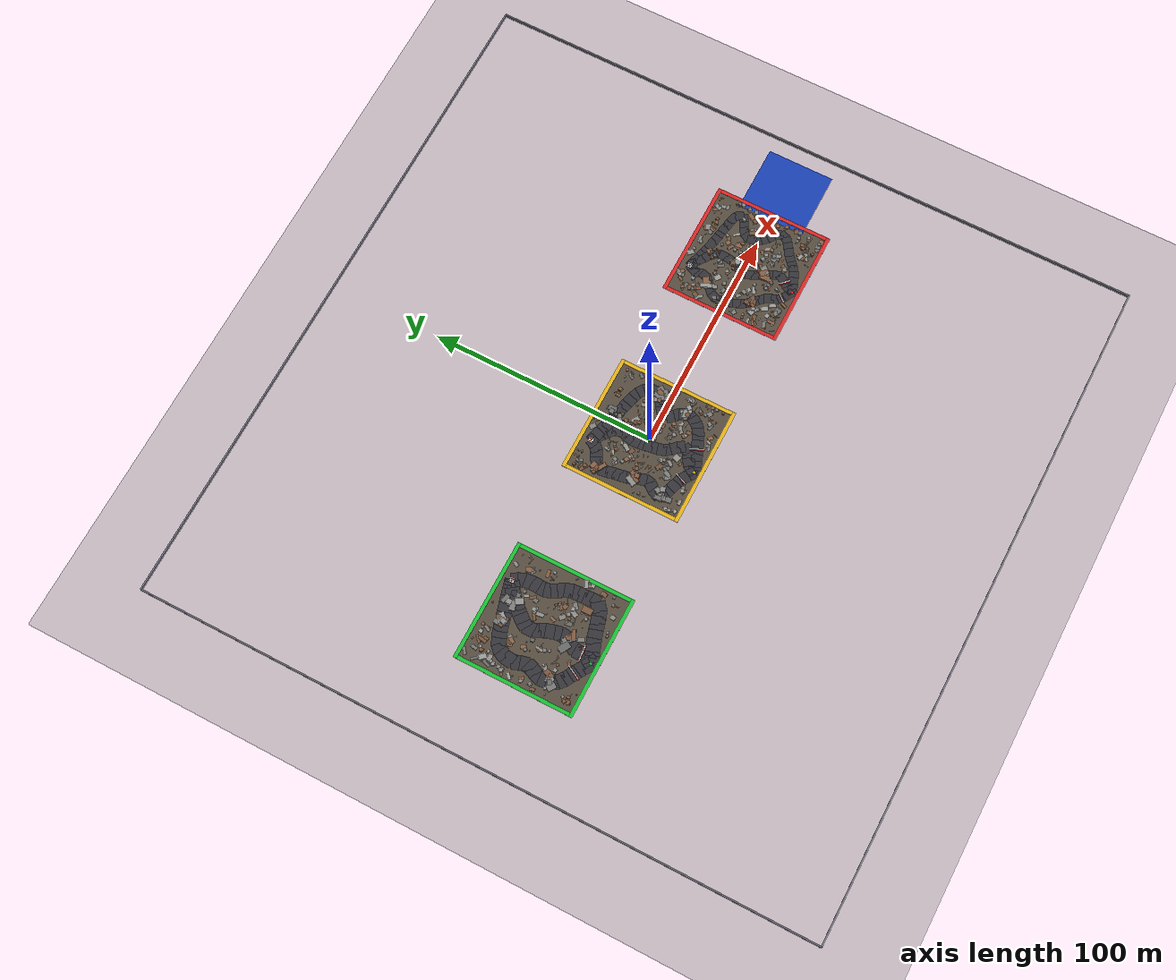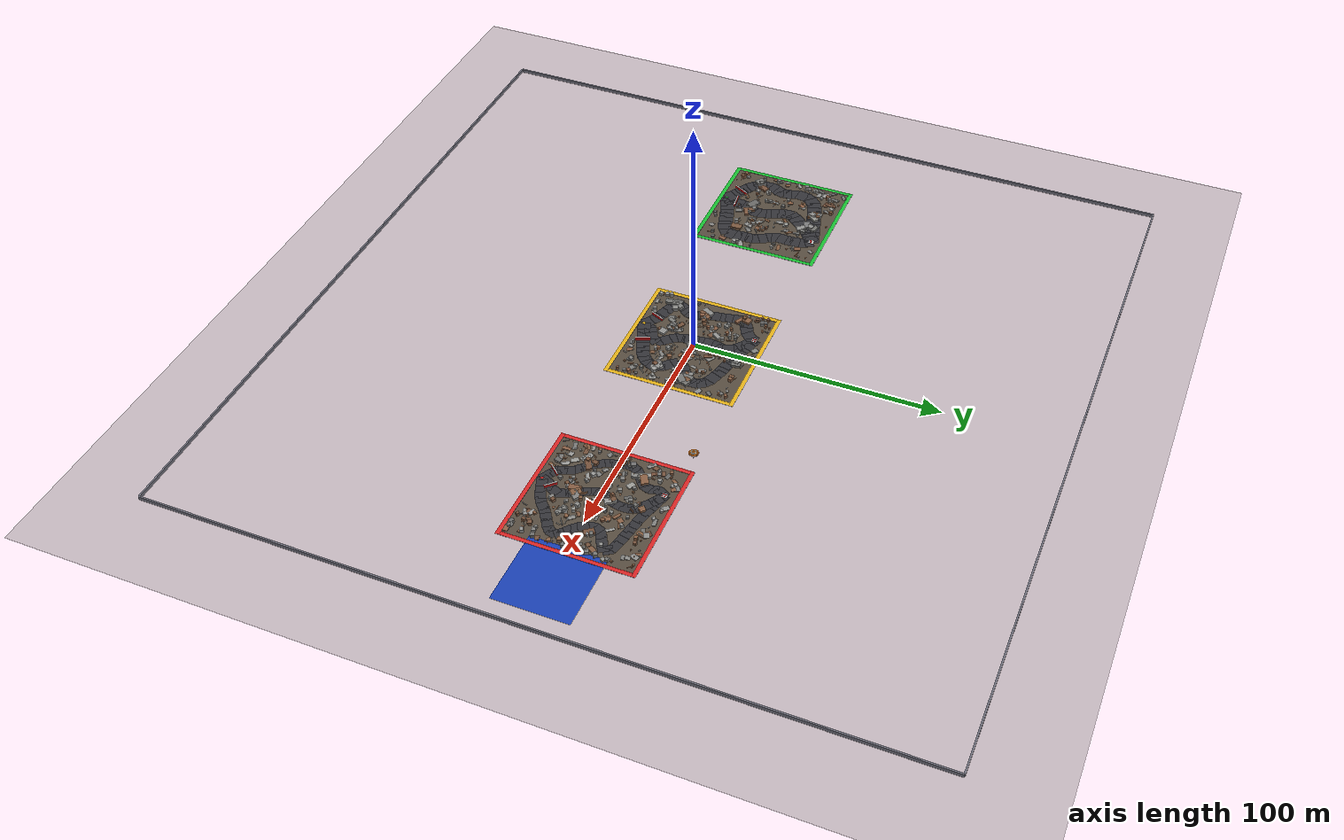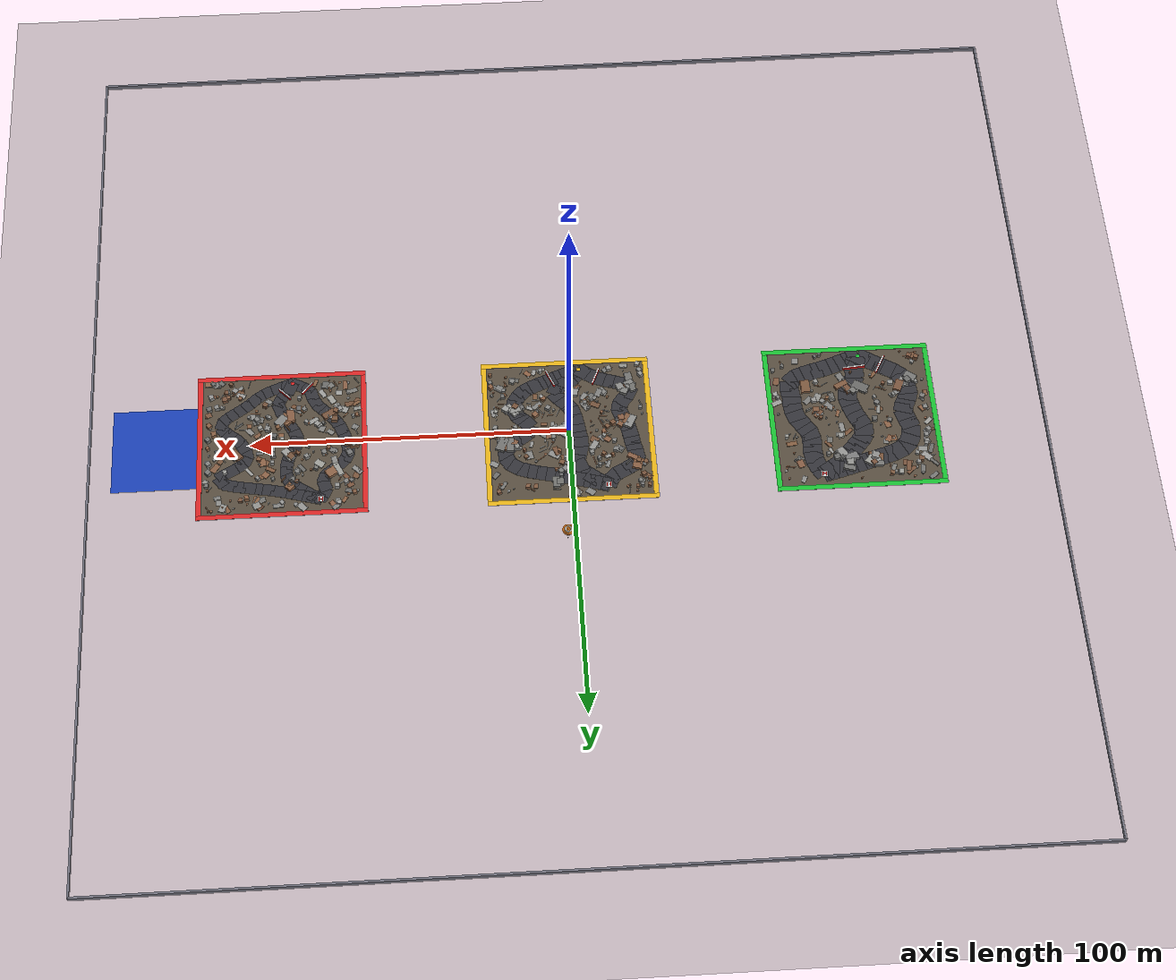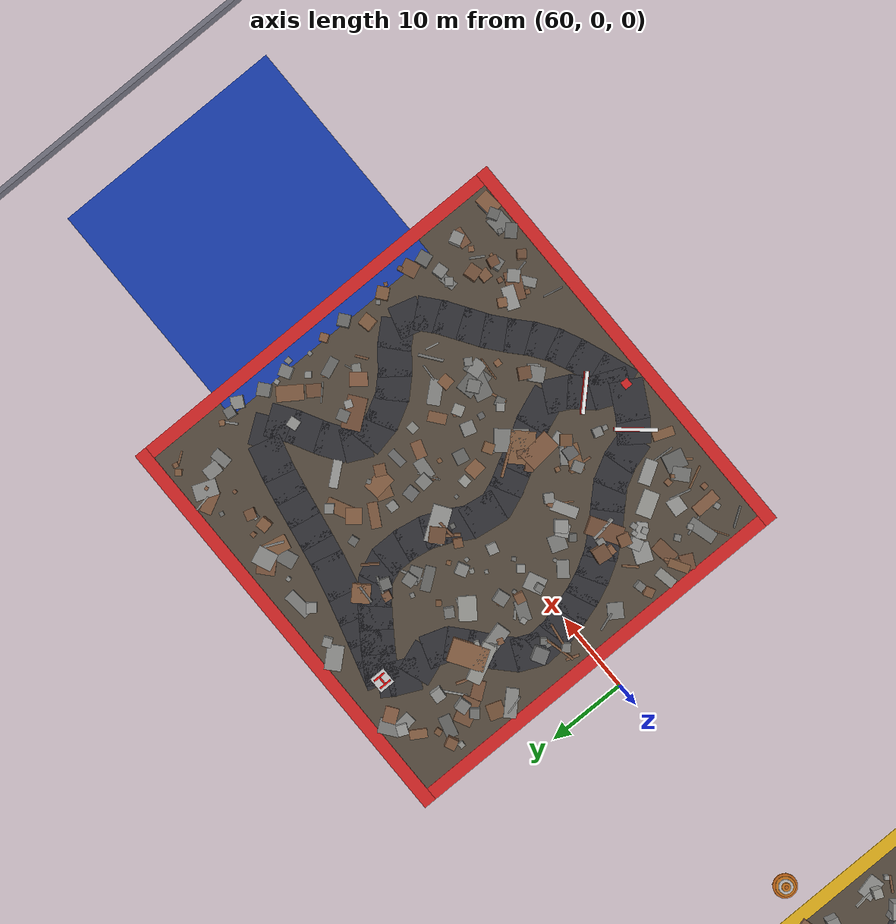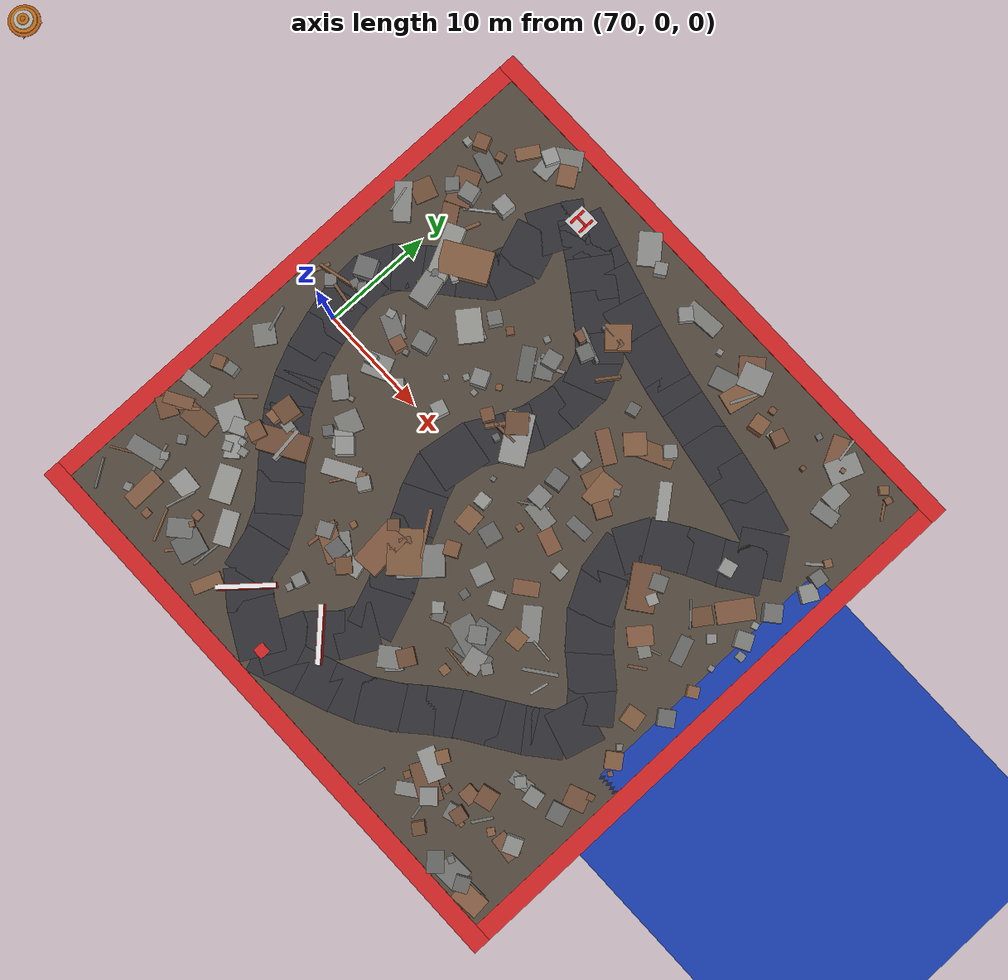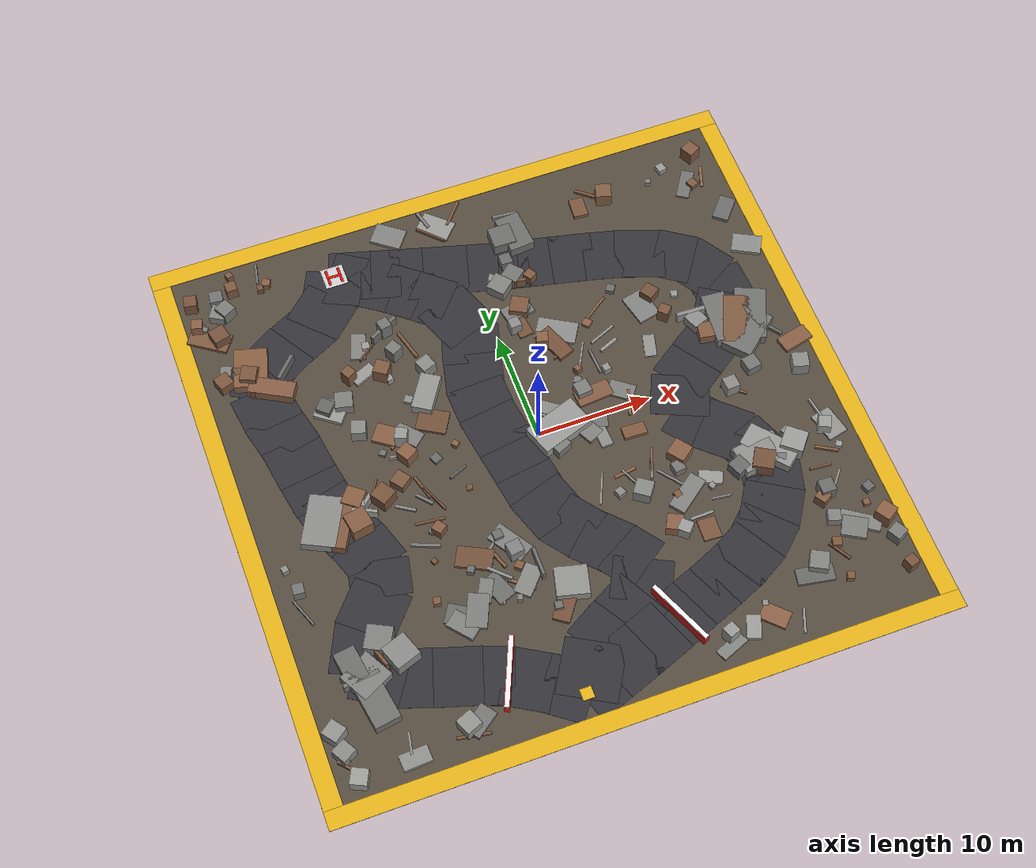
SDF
<sdf version="1.6">
 <world name="navitas_arena">
  <physics type="ode">
   <max_step_size>0.001</max_step_size>
   <real_time_factor>1</real_time_factor>
   <gravity>0 0 -9.8</gravity>
  </physics>
  <wind><linear_velocity>2.0000 -1.0000 0.0000</linear_velocity></wind>
  <scene>
   <ambient>0.4800 0.5000 0.5200 1.0000</ambient>
   <background>0.6200 0.7000 0.7800 1.0000</background>
   <shadows>false</shadows>
  </scene>
  <light name="sun" type="directional">
   <cast_shadows>false</cast_shadows>
   <pose>0 0 120 0 0 0</pose>
   <diffuse>0.8200 0.8000 0.7400 1.0000</diffuse>
   <specular>0.1 0.1 0.1 1</specular>
   <attenuation>
    <range>1200</range>
    <constant>0.9</constant>
    <linear>0.01</linear>
    <quadratic>0.001</quadratic>
   </attenuation>
   <direction>-0.5000 0.2500 -0.8200</direction>
  </light>
  <model name="ground_plane">
   <static>true</static>
   <link name="link">
    <collision name="collision">
     <geometry><plane><normal>0 0 1</normal><size>400 400</size></plane></geometry>
     <surface><friction><ode><mu>0.820</mu><mu2>0.820</mu2></ode></friction></surface>
    </collision>
    <visual name="visual">
     <cast_shadows>false</cast_shadows>
     <geometry><plane><normal>0 0 1</normal><size>400 400</size></plane></geometry>
     <material><ambient>0.280 0.270 0.250 1</ambient><diffuse>0.280 0.270 0.250 1</diffuse></material>
    </visual>
   </link>
  </model>
  <model name="ub_N">
   <static>true</static>
   <pose>0.000 150.000 0.750 0 0 0.000</pose>
   <link name="link">
    <collision name="col"><geometry><box><size>300.000 0.600 1.500</size></box></geometry></collision>
    <visual name="vis">
     <geometry><box><size>300.000 0.600 1.500</size></box></geometry>
     <material><ambient>0.45 0.45 0.50 1</ambient><diffuse>0.45 0.45 0.50 1</diffuse></material>
    </visual>
   </link>
  </model>
  <model name="ub_S">
   <static>true</static>
   <pose>0.000 -150.000 0.750 0 0 0.000</pose>
   <link name="link">
    <collision name="col"><geometry><box><size>300.000 0.600 1.500</size></box></geometry></collision>
    <visual name="vis">
     <geometry><box><size>300.000 0.600 1.500</size></box></geometry>
     <material><ambient>0.45 0.45 0.50 1</ambient><diffuse>0.45 0.45 0.50 1</diffuse></material>
    </visual>
   </link>
  </model>
  <model name="ub_W">
   <static>true</static>
   <pose>-150.000 0.000 0.750 0 0 0.000</pose>
   <link name="link">
    <collision name="col"><geometry><box><size>0.600 300.000 1.500</size></box></geometry></collision>
    <visual name="vis">
     <geometry><box><size>0.600 300.000 1.500</size></box></geometry>
     <material><ambient>0.45 0.45 0.50 1</ambient><diffuse>0.45 0.45 0.50 1</diffuse></material>
    </visual>
   </link>
  </model>
  <model name="ub_E">
   <static>true</static>
   <pose>150.000 0.000 0.750 0 0 0.000</pose>
   <link name="link">
    <collision name="col"><geometry><box><size>0.600 300.000 1.500</size></box></geometry></collision>
    <visual name="vis">
     <geometry><box><size>0.600 300.000 1.500</size></box></geometry>
     <material><ambient>0.45 0.45 0.50 1</ambient><diffuse>0.45 0.45 0.50 1</diffuse></material>
    </visual>
   </link>
  </model>
  <model name="landing">
   <static>true</static>
   <pose>128.000 0.000 0.010 0 0 0.000</pose>
   <link name="link">
    <collision name="col"><geometry><box><size>30.000 30.000 0.020</size></box></geometry></collision>
    <visual name="vis">
     <geometry><box><size>30.000 30.000 0.020</size></box></geometry>
     <material><ambient>0.10 0.25 0.70 1</ambient><diffuse>0.10 0.25 0.70 1</diffuse></material>
    </visual>
   </link>
  </model>
  <model name="gd_kolay">
   <static>true</static>
   <pose>-90.000 0.000 0.010 0 0 0.000</pose>
   <link name="link">
    <collision name="col"><geometry><box><size>50.000 50.000 0.020</size></box></geometry></collision>
    <visual name="vis">
     <geometry><box><size>50.000 50.000 0.020</size></box></geometry>
     <material><ambient>0.34 0.30 0.25 1</ambient><diffuse>0.34 0.30 0.25 1</diffuse></material>
    </visual>
   </link>
  </model>
  <model name="brd_kolay_N">
   <static>true</static>
   <pose>-90.000 25.800 0.040 0 0 0.000</pose>
   <link name="link">
    <collision name="col"><geometry><box><size>53.200 1.600 0.080</size></box></geometry></collision>
    <visual name="vis">
     <geometry><box><size>53.200 1.600 0.080</size></box></geometry>
     <material><ambient>0.10 0.75 0.20 1</ambient><diffuse>0.10 0.75 0.20 1</diffuse></material>
    </visual>
   </link>
  </model>
  <model name="brd_kolay_S">
   <static>true</static>
   <pose>-90.000 -25.800 0.040 0 0 0.000</pose>
   <link name="link">
    <collision name="col"><geometry><box><size>53.200 1.600 0.080</size></box></geometry></collision>
    <visual name="vis">
     <geometry><box><size>53.200 1.600 0.080</size></box></geometry>
     <material><ambient>0.10 0.75 0.20 1</ambient><diffuse>0.10 0.75 0.20 1</diffuse></material>
    </visual>
   </link>
  </model>
  <model name="brd_kolay_W">
   <static>true</static>
   <pose>-115.800 0.000 0.040 0 0 0.000</pose>
   <link name="link">
    <collision name="col"><geometry><box><size>1.600 50.000 0.080</size></box></geometry></collision>
    <visual name="vis">
     <geometry><box><size>1.600 50.000 0.080</size></box></geometry>
     <material><ambient>0.10 0.75 0.20 1</ambient><diffuse>0.10 0.75 0.20 1</diffuse></material>
    </visual>
   </link>
  </model>
  <model name="brd_kolay_E">
   <static>true</static>
   <pose>-64.200 0.000 0.040 0 0 0.000</pose>
   <link name="link">
    <collision name="col"><geometry><box><size>1.600 50.000 0.080</size></box></geometry></collision>
    <visual name="vis">
     <geometry><box><size>1.600 50.000 0.080</size></box></geometry>
     <material><ambient>0.10 0.75 0.20 1</ambient><diffuse>0.10 0.75 0.20 1</diffuse></material>
    </visual>
   </link>
  </model>
  <model name="road_kolay_1_0">
   <static>true</static>
   <pose>-95.516 -22.070 0.040 0 0 2.562</pose>
   <link name="link">
    <collision name="col"><geometry><box><size>4.297 6.000 0.020</size></box></geometry></collision>
    <visual name="vis">
     <geometry><box><size>4.297 6.000 0.020</size></box></geometry>
     <material><ambient>0.20 0.20 0.22 1</ambient><diffuse>0.20 0.20 0.22 1</diffuse></material>
    </visual>
   </link>
  </model>
  <model name="road_kolay_1_1">
   <static>true</static>
   <pose>-98.194 -20.320 0.040 0 0 2.564</pose>
   <link name="link">
    <collision name="col"><geometry><box><size>3.902 6.000 0.020</size></box></geometry></collision>
    <visual name="vis">
     <geometry><box><size>3.902 6.000 0.020</size></box></geometry>
     <material><ambient>0.20 0.20 0.22 1</ambient><diffuse>0.20 0.20 0.22 1</diffuse></material>
    </visual>
   </link>
  </model>
  <model name="road_kolay_1_2">
   <static>true</static>
   <pose>-100.643 -18.833 0.040 0 0 2.631</pose>
   <link name="link">
    <collision name="col"><geometry><box><size>3.630 6.000 0.020</size></box></geometry></collision>
    <visual name="vis">
     <geometry><box><size>3.630 6.000 0.020</size></box></geometry>
     <material><ambient>0.20 0.20 0.22 1</ambient><diffuse>0.20 0.20 0.22 1</diffuse></material>
    </visual>
   </link>
  </model>
  <model name="road_kolay_1_3">
   <static>true</static>
   <pose>-103.113 -17.444 0.040 0 0 2.628</pose>
   <link name="link">
    <collision name="col"><geometry><box><size>3.838 6.000 0.020</size></box></geometry></collision>
    <visual name="vis">
     <geometry><box><size>3.838 6.000 0.020</size></box></geometry>
     <material><ambient>0.20 0.20 0.22 1</ambient><diffuse>0.20 0.20 0.22 1</diffuse></material>
    </visual>
   </link>
  </model>
  <model name="road_kolay_1_4">
   <static>true</static>
   <pose>-105.395 -15.861 0.040 0 0 2.432</pose>
   <link name="link">
    <collision name="col"><geometry><box><size>3.544 6.000 0.020</size></box></geometry></collision>
    <visual name="vis">
     <geometry><box><size>3.544 6.000 0.020</size></box></geometry>
     <material><ambient>0.20 0.20 0.22 1</ambient><diffuse>0.20 0.20 0.22 1</diffuse></material>
    </visual>
   </link>
  </model>
  <model name="road_kolay_1_5">
   <static>true</static>
   <pose>-106.995 -13.926 0.040 0 0 2.078</pose>
   <link name="link">
    <collision name="col"><geometry><box><size>3.357 6.000 0.020</size></box></geometry></collision>
    <visual name="vis">
     <geometry><box><size>3.357 6.000 0.020</size></box></geometry>
     <material><ambient>0.20 0.20 0.22 1</ambient><diffuse>0.20 0.20 0.22 1</diffuse></material>
    </visual>
   </link>
  </model>
  <model name="road_kolay_1_6">
   <static>true</static>
   <pose>-107.912 -11.639 0.040 0 0 1.829</pose>
   <link name="link">
    <collision name="col"><geometry><box><size>3.409 6.000 0.020</size></box></geometry></collision>
    <visual name="vis">
     <geometry><box><size>3.409 6.000 0.020</size></box></geometry>
     <material><ambient>0.20 0.20 0.22 1</ambient><diffuse>0.20 0.20 0.22 1</diffuse></material>
    </visual>
   </link>
  </model>
  <model name="road_kolay_1_7">
   <static>true</static>
   <pose>-108.301 -9.213 0.040 0 0 1.628</pose>
   <link name="link">
    <collision name="col"><geometry><box><size>3.330 6.000 0.020</size></box></geometry></collision>
    <visual name="vis">
     <geometry><box><size>3.330 6.000 0.020</size></box></geometry>
     <material><ambient>0.20 0.20 0.22 1</ambient><diffuse>0.20 0.20 0.22 1</diffuse></material>
    </visual>
   </link>
  </model>
  <model name="road_kolay_1_8">
   <static>true</static>
   <pose>-108.031 -6.833 0.040 0 0 1.288</pose>
   <link name="link">
    <collision name="col"><geometry><box><size>3.330 6.000 0.020</size></box></geometry></collision>
    <visual name="vis">
     <geometry><box><size>3.330 6.000 0.020</size></box></geometry>
     <material><ambient>0.20 0.20 0.22 1</ambient><diffuse>0.20 0.20 0.22 1</diffuse></material>
    </visual>
   </link>
  </model>
  <model name="road_kolay_1_9">
   <static>true</static>
   <pose>-107.102 -4.500 0.040 0 0 1.102</pose>
   <link name="link">
    <collision name="col"><geometry><box><size>3.515 6.000 0.020</size></box></geometry></collision>
    <visual name="vis">
     <geometry><box><size>3.515 6.000 0.020</size></box></geometry>
     <material><ambient>0.20 0.20 0.22 1</ambient><diffuse>0.20 0.20 0.22 1</diffuse></material>
    </visual>
   </link>
  </model>
  <model name="road_kolay_1_10">
   <static>true</static>
   <pose>-106.165 -2.167 0.040 0 0 1.282</pose>
   <link name="link">
    <collision name="col"><geometry><box><size>3.334 6.000 0.020</size></box></geometry></collision>
    <visual name="vis">
     <geometry><box><size>3.334 6.000 0.020</size></box></geometry>
     <material><ambient>0.20 0.20 0.22 1</ambient><diffuse>0.20 0.20 0.22 1</diffuse></material>
    </visual>
   </link>
  </model>
  <model name="road_kolay_1_11">
   <static>true</static>
   <pose>-106.307 0.750 0.040 0 0 1.844</pose>
   <link name="link">
    <collision name="col"><geometry><box><size>4.535 6.000 0.020</size></box></geometry></collision>
    <visual name="vis">
     <geometry><box><size>4.535 6.000 0.020</size></box></geometry>
     <material><ambient>0.20 0.20 0.22 1</ambient><diffuse>0.20 0.20 0.22 1</diffuse></material>
    </visual>
   </link>
  </model>
  <model name="road_kolay_1_12">
   <static>true</static>
   <pose>-107.200 3.667 0.040 0 0 1.903</pose>
   <link name="link">
    <collision name="col"><geometry><box><size>3.369 6.000 0.020</size></box></geometry></collision>
    <visual name="vis">
     <geometry><box><size>3.369 6.000 0.020</size></box></geometry>
     <material><ambient>0.20 0.20 0.22 1</ambient><diffuse>0.20 0.20 0.22 1</diffuse></material>
    </visual>
   </link>
  </model>
  <model name="road_kolay_1_13">
   <static>true</static>
   <pose>-107.395 6.630 0.040 0 0 1.455</pose>
   <link name="link">
    <collision name="col"><geometry><box><size>4.517 6.000 0.020</size></box></geometry></collision>
    <visual name="vis">
     <geometry><box><size>4.517 6.000 0.020</size></box></geometry>
     <material><ambient>0.20 0.20 0.22 1</ambient><diffuse>0.20 0.20 0.22 1</diffuse></material>
    </visual>
   </link>
  </model>
  <model name="road_kolay_1_14">
   <static>true</static>
   <pose>-106.656 9.639 0.040 0 0 1.158</pose>
   <link name="link">
    <collision name="col"><geometry><box><size>3.548 6.000 0.020</size></box></geometry></collision>
    <visual name="vis">
     <geometry><box><size>3.548 6.000 0.020</size></box></geometry>
     <material><ambient>0.20 0.20 0.22 1</ambient><diffuse>0.20 0.20 0.22 1</diffuse></material>
    </visual>
   </link>
  </model>
  <model name="road_kolay_1_15">
   <static>true</static>
   <pose>-105.067 11.926 0.040 0 0 0.793</pose>
   <link name="link">
    <collision name="col"><geometry><box><size>3.916 6.000 0.020</size></box></geometry></collision>
    <visual name="vis">
     <geometry><box><size>3.916 6.000 0.020</size></box></geometry>
     <material><ambient>0.20 0.20 0.22 1</ambient><diffuse>0.20 0.20 0.22 1</diffuse></material>
    </visual>
   </link>
  </model>
  <model name="road_kolay_1_16">
   <static>true</static>
   <pose>-102.551 13.717 0.040 0 0 0.457</pose>
   <link name="link">
    <collision name="col"><geometry><box><size>4.149 6.000 0.020</size></box></geometry></collision>
    <visual name="vis">
     <geometry><box><size>4.149 6.000 0.020</size></box></geometry>
     <material><ambient>0.20 0.20 0.22 1</ambient><diffuse>0.20 0.20 0.22 1</diffuse></material>
    </visual>
   </link>
  </model>
  <model name="road_kolay_1_17">
   <static>true</static>
   <pose>-99.868 14.853 0.040 0 0 0.329</pose>
   <link name="link">
    <collision name="col"><geometry><box><size>3.490 6.000 0.020</size></box></geometry></collision>
    <visual name="vis">
     <geometry><box><size>3.490 6.000 0.020</size></box></geometry>
     <material><ambient>0.20 0.20 0.22 1</ambient><diffuse>0.20 0.20 0.22 1</diffuse></material>
    </visual>
   </link>
  </model>
  <model name="road_kolay_1_18">
   <static>true</static>
   <pose>-97.321 15.657 0.040 0 0 0.284</pose>
   <link name="link">
    <collision name="col"><geometry><box><size>3.652 6.000 0.020</size></box></geometry></collision>
    <visual name="vis">
     <geometry><box><size>3.652 6.000 0.020</size></box></geometry>
     <material><ambient>0.20 0.20 0.22 1</ambient><diffuse>0.20 0.20 0.22 1</diffuse></material>
    </visual>
   </link>
  </model>
  <model name="road_kolay_1_19">
   <static>true</static>
   <pose>-94.676 16.409 0.040 0 0 0.270</pose>
   <link name="link">
    <collision name="col"><geometry><box><size>3.648 6.000 0.020</size></box></geometry></collision>
    <visual name="vis">
     <geometry><box><size>3.648 6.000 0.020</size></box></geometry>
     <material><ambient>0.20 0.20 0.22 1</ambient><diffuse>0.20 0.20 0.22 1</diffuse></material>
    </visual>
   </link>
  </model>
  <model name="road_kolay_1_20">
   <static>true</static>
   <pose>-92.118 17.138 0.040 0 0 0.285</pose>
   <link name="link">
    <collision name="col"><geometry><box><size>3.473 6.000 0.020</size></box></geometry></collision>
    <visual name="vis">
     <geometry><box><size>3.473 6.000 0.020</size></box></geometry>
     <material><ambient>0.20 0.20 0.22 1</ambient><diffuse>0.20 0.20 0.22 1</diffuse></material>
    </visual>
   </link>
  </model>
  <model name="road_kolay_1_21">
   <static>true</static>
   <pose>-89.523 17.910 0.040 0 0 0.293</pose>
   <link name="link">
    <collision name="col"><geometry><box><size>3.741 6.000 0.020</size></box></geometry></collision>
    <visual name="vis">
     <geometry><box><size>3.741 6.000 0.020</size></box></geometry>
     <material><ambient>0.20 0.20 0.22 1</ambient><diffuse>0.20 0.20 0.22 1</diffuse></material>
    </visual>
   </link>
  </model>
  <model name="road_kolay_1_22">
   <static>true</static>
   <pose>-86.726 18.730 0.040 0 0 0.278</pose>
   <link name="link">
    <collision name="col"><geometry><box><size>3.890 6.000 0.020</size></box></geometry></collision>
    <visual name="vis">
     <geometry><box><size>3.890 6.000 0.020</size></box></geometry>
     <material><ambient>0.20 0.20 0.22 1</ambient><diffuse>0.20 0.20 0.22 1</diffuse></material>
    </visual>
   </link>
  </model>
  <model name="road_kolay_1_23">
   <static>true</static>
   <pose>-83.912 19.520 0.040 0 0 0.269</pose>
   <link name="link">
    <collision name="col"><geometry><box><size>3.755 6.000 0.020</size></box></geometry></collision>
    <visual name="vis">
     <geometry><box><size>3.755 6.000 0.020</size></box></geometry>
     <material><ambient>0.20 0.20 0.22 1</ambient><diffuse>0.20 0.20 0.22 1</diffuse></material>
    </visual>
   </link>
  </model>
  <model name="road_kolay_1_24">
   <static>true</static>
   <pose>-81.360 20.220 0.040 0 0 0.266</pose>
   <link name="link">
    <collision name="col"><geometry><box><size>3.336 6.000 0.020</size></box></geometry></collision>
    <visual name="vis">
     <geometry><box><size>3.336 6.000 0.020</size></box></geometry>
     <material><ambient>0.20 0.20 0.22 1</ambient><diffuse>0.20 0.20 0.22 1</diffuse></material>
    </visual>
   </link>
  </model>
  <model name="road_kolay_1_25">
   <static>true</static>
   <pose>-79.350 20.770 0.040 0 0 0.269</pose>
   <link name="link">
    <collision name="col"><geometry><box><size>2.632 6.000 0.020</size></box></geometry></collision>
    <visual name="vis">
     <geometry><box><size>2.632 6.000 0.020</size></box></geometry>
     <material><ambient>0.20 0.20 0.22 1</ambient><diffuse>0.20 0.20 0.22 1</diffuse></material>
    </visual>
   </link>
  </model>
  <model name="road_kolay_2_0">
   <static>true</static>
   <pose>-93.450 -21.935 0.040 0 0 1.027</pose>
   <link name="link">
    <collision name="col"><geometry><box><size>3.389 6.000 0.020</size></box></geometry></collision>
    <visual name="vis">
     <geometry><box><size>3.389 6.000 0.020</size></box></geometry>
     <material><ambient>0.20 0.20 0.22 1</ambient><diffuse>0.20 0.20 0.22 1</diffuse></material>
    </visual>
   </link>
  </model>
  <model name="road_kolay_2_1">
   <static>true</static>
   <pose>-92.504 -19.519 0.040 0 0 1.352</pose>
   <link name="link">
    <collision name="col"><geometry><box><size>3.670 6.000 0.020</size></box></geometry></collision>
    <visual name="vis">
     <geometry><box><size>3.670 6.000 0.020</size></box></geometry>
     <material><ambient>0.20 0.20 0.22 1</ambient><diffuse>0.20 0.20 0.22 1</diffuse></material>
    </visual>
   </link>
  </model>
  <model name="road_kolay_2_2">
   <static>true</static>
   <pose>-92.175 -16.583 0.040 0 0 1.553</pose>
   <link name="link">
    <collision name="col"><geometry><box><size>4.067 6.000 0.020</size></box></geometry></collision>
    <visual name="vis">
     <geometry><box><size>4.067 6.000 0.020</size></box></geometry>
     <material><ambient>0.20 0.20 0.22 1</ambient><diffuse>0.20 0.20 0.22 1</diffuse></material>
    </visual>
   </link>
  </model>
  <model name="road_kolay_2_3">
   <static>true</static>
   <pose>-91.289 -13.328 0.040 0 0 1.097</pose>
   <link name="link">
    <collision name="col"><geometry><box><size>4.657 6.000 0.020</size></box></geometry></collision>
    <visual name="vis">
     <geometry><box><size>4.657 6.000 0.020</size></box></geometry>
     <material><ambient>0.20 0.20 0.22 1</ambient><diffuse>0.20 0.20 0.22 1</diffuse></material>
    </visual>
   </link>
  </model>
  <model name="road_kolay_2_4">
   <static>true</static>
   <pose>-89.827 -10.426 0.040 0 0 1.113</pose>
   <link name="link">
    <collision name="col"><geometry><box><size>3.642 6.000 0.020</size></box></geometry></collision>
    <visual name="vis">
     <geometry><box><size>3.642 6.000 0.020</size></box></geometry>
     <material><ambient>0.20 0.20 0.22 1</ambient><diffuse>0.20 0.20 0.22 1</diffuse></material>
    </visual>
   </link>
  </model>
  <model name="road_kolay_2_5">
   <static>true</static>
   <pose>-89.065 -7.898 0.040 0 0 1.451</pose>
   <link name="link">
    <collision name="col"><geometry><box><size>3.514 6.000 0.020</size></box></geometry></collision>
    <visual name="vis">
     <geometry><box><size>3.514 6.000 0.020</size></box></geometry>
     <material><ambient>0.20 0.20 0.22 1</ambient><diffuse>0.20 0.20 0.22 1</diffuse></material>
    </visual>
   </link>
  </model>
  <model name="road_kolay_2_6">
   <static>true</static>
   <pose>-89.223 -5.200 0.040 0 0 1.792</pose>
   <link name="link">
    <collision name="col"><geometry><box><size>3.770 6.000 0.020</size></box></geometry></collision>
    <visual name="vis">
     <geometry><box><size>3.770 6.000 0.020</size></box></geometry>
     <material><ambient>0.20 0.20 0.22 1</ambient><diffuse>0.20 0.20 0.22 1</diffuse></material>
    </visual>
   </link>
  </model>
  <model name="road_kolay_2_7">
   <static>true</static>
   <pose>-89.991 -2.400 0.040 0 0 1.884</pose>
   <link name="link">
    <collision name="col"><geometry><box><size>3.843 6.000 0.020</size></box></geometry></collision>
    <visual name="vis">
     <geometry><box><size>3.843 6.000 0.020</size></box></geometry>
     <material><ambient>0.20 0.20 0.22 1</ambient><diffuse>0.20 0.20 0.22 1</diffuse></material>
    </visual>
   </link>
  </model>
  <model name="road_kolay_2_8">
   <static>true</static>
   <pose>-90.962 0.167 0.040 0 0 1.988</pose>
   <link name="link">
    <collision name="col"><geometry><box><size>3.452 6.000 0.020</size></box></geometry></collision>
    <visual name="vis">
     <geometry><box><size>3.452 6.000 0.020</size></box></geometry>
     <material><ambient>0.20 0.20 0.22 1</ambient><diffuse>0.20 0.20 0.22 1</diffuse></material>
    </visual>
   </link>
  </model>
  <model name="road_kolay_2_9">
   <static>true</static>
   <pose>-92.051 2.500 0.040 0 0 2.026</pose>
   <link name="link">
    <collision name="col"><geometry><box><size>3.498 6.000 0.020</size></box></geometry></collision>
    <visual name="vis">
     <geometry><box><size>3.498 6.000 0.020</size></box></geometry>
     <material><ambient>0.20 0.20 0.22 1</ambient><diffuse>0.20 0.20 0.22 1</diffuse></material>
    </visual>
   </link>
  </model>
  <model name="road_kolay_2_10">
   <static>true</static>
   <pose>-92.623 5.344 0.040 0 0 1.571</pose>
   <link name="link">
    <collision name="col"><geometry><box><size>4.255 6.000 0.020</size></box></geometry></collision>
    <visual name="vis">
     <geometry><box><size>4.255 6.000 0.020</size></box></geometry>
     <material><ambient>0.20 0.20 0.22 1</ambient><diffuse>0.20 0.20 0.22 1</diffuse></material>
    </visual>
   </link>
  </model>
  <model name="road_kolay_2_11">
   <static>true</static>
   <pose>-91.972 8.077 0.040 0 0 1.018</pose>
   <link name="link">
    <collision name="col"><geometry><box><size>3.379 6.000 0.020</size></box></geometry></collision>
    <visual name="vis">
     <geometry><box><size>3.379 6.000 0.020</size></box></geometry>
     <material><ambient>0.20 0.20 0.22 1</ambient><diffuse>0.20 0.20 0.22 1</diffuse></material>
    </visual>
   </link>
  </model>
  <model name="road_kolay_2_12">
   <static>true</static>
   <pose>-90.460 10.157 0.040 0 0 0.873</pose>
   <link name="link">
    <collision name="col"><geometry><box><size>3.577 6.000 0.020</size></box></geometry></collision>
    <visual name="vis">
     <geometry><box><size>3.577 6.000 0.020</size></box></geometry>
     <material><ambient>0.20 0.20 0.22 1</ambient><diffuse>0.20 0.20 0.22 1</diffuse></material>
    </visual>
   </link>
  </model>
  <model name="road_kolay_2_13">
   <static>true</static>
   <pose>-88.810 12.091 0.040 0 0 0.855</pose>
   <link name="link">
    <collision name="col"><geometry><box><size>3.308 6.000 0.020</size></box></geometry></collision>
    <visual name="vis">
     <geometry><box><size>3.308 6.000 0.020</size></box></geometry>
     <material><ambient>0.20 0.20 0.22 1</ambient><diffuse>0.20 0.20 0.22 1</diffuse></material>
    </visual>
   </link>
  </model>
  <model name="road_kolay_2_14">
   <static>true</static>
   <pose>-87.152 14.014 0.040 0 0 0.863</pose>
   <link name="link">
    <collision name="col"><geometry><box><size>3.570 6.000 0.020</size></box></geometry></collision>
    <visual name="vis">
     <geometry><box><size>3.570 6.000 0.020</size></box></geometry>
     <material><ambient>0.20 0.20 0.22 1</ambient><diffuse>0.20 0.20 0.22 1</diffuse></material>
    </visual>
   </link>
  </model>
  <model name="road_kolay_2_15">
   <static>true</static>
   <pose>-84.983 16.264 0.040 0 0 0.760</pose>
   <link name="link">
    <collision name="col"><geometry><box><size>4.488 6.000 0.020</size></box></geometry></collision>
    <visual name="vis">
     <geometry><box><size>4.488 6.000 0.020</size></box></geometry>
     <material><ambient>0.20 0.20 0.22 1</ambient><diffuse>0.20 0.20 0.22 1</diffuse></material>
    </visual>
   </link>
  </model>
  <model name="road_kolay_2_16">
   <static>true</static>
   <pose>-82.556 18.320 0.040 0 0 0.629</pose>
   <link name="link">
    <collision name="col"><geometry><box><size>3.689 6.000 0.020</size></box></geometry></collision>
    <visual name="vis">
     <geometry><box><size>3.689 6.000 0.020</size></box></geometry>
     <material><ambient>0.20 0.20 0.22 1</ambient><diffuse>0.20 0.20 0.22 1</diffuse></material>
    </visual>
   </link>
  </model>
  <model name="road_kolay_2_17">
   <static>true</static>
   <pose>-80.330 19.840 0.040 0 0 0.567</pose>
   <link name="link">
    <collision name="col"><geometry><box><size>3.505 6.000 0.020</size></box></geometry></collision>
    <visual name="vis">
     <geometry><box><size>3.505 6.000 0.020</size></box></geometry>
     <material><ambient>0.20 0.20 0.22 1</ambient><diffuse>0.20 0.20 0.22 1</diffuse></material>
    </visual>
   </link>
  </model>
  <model name="road_kolay_2_18">
   <static>true</static>
   <pose>-78.873 20.770 0.040 0 0 0.571</pose>
   <link name="link">
    <collision name="col"><geometry><box><size>1.751 6.000 0.020</size></box></geometry></collision>
    <visual name="vis">
     <geometry><box><size>1.751 6.000 0.020</size></box></geometry>
     <material><ambient>0.20 0.20 0.22 1</ambient><diffuse>0.20 0.20 0.22 1</diffuse></material>
    </visual>
   </link>
  </model>
  <model name="road_kolay_3_0">
   <static>true</static>
   <pose>-92.817 -22.494 0.040 0 0 0.377</pose>
   <link name="link">
    <collision name="col"><geometry><box><size>3.647 6.000 0.020</size></box></geometry></collision>
    <visual name="vis">
     <geometry><box><size>3.647 6.000 0.020</size></box></geometry>
     <material><ambient>0.20 0.20 0.22 1</ambient><diffuse>0.20 0.20 0.22 1</diffuse></material>
    </visual>
   </link>
  </model>
  <model name="road_kolay_3_1">
   <static>true</static>
   <pose>-90.336 -21.514 0.040 0 0 0.375</pose>
   <link name="link">
    <collision name="col"><geometry><box><size>3.489 6.000 0.020</size></box></geometry></collision>
    <visual name="vis">
     <geometry><box><size>3.489 6.000 0.020</size></box></geometry>
     <material><ambient>0.20 0.20 0.22 1</ambient><diffuse>0.20 0.20 0.22 1</diffuse></material>
    </visual>
   </link>
  </model>
  <model name="road_kolay_3_2">
   <static>true</static>
   <pose>-87.783 -20.524 0.040 0 0 0.365</pose>
   <link name="link">
    <collision name="col"><geometry><box><size>3.787 6.000 0.020</size></box></geometry></collision>
    <visual name="vis">
     <geometry><box><size>3.787 6.000 0.020</size></box></geometry>
     <material><ambient>0.20 0.20 0.22 1</ambient><diffuse>0.20 0.20 0.22 1</diffuse></material>
    </visual>
   </link>
  </model>
  <model name="road_kolay_3_3">
   <static>true</static>
   <pose>-85.203 -19.574 0.040 0 0 0.340</pose>
   <link name="link">
    <collision name="col"><geometry><box><size>3.513 6.000 0.020</size></box></geometry></collision>
    <visual name="vis">
     <geometry><box><size>3.513 6.000 0.020</size></box></geometry>
     <material><ambient>0.20 0.20 0.22 1</ambient><diffuse>0.20 0.20 0.22 1</diffuse></material>
    </visual>
   </link>
  </model>
  <model name="road_kolay_3_4">
   <static>true</static>
   <pose>-82.713 -18.775 0.040 0 0 0.281</pose>
   <link name="link">
    <collision name="col"><geometry><box><size>3.518 6.000 0.020</size></box></geometry></collision>
    <visual name="vis">
     <geometry><box><size>3.518 6.000 0.020</size></box></geometry>
     <material><ambient>0.20 0.20 0.22 1</ambient><diffuse>0.20 0.20 0.22 1</diffuse></material>
    </visual>
   </link>
  </model>
  <model name="road_kolay_3_5">
   <static>true</static>
   <pose>-80.083 -18.038 0.040 0 0 0.267</pose>
   <link name="link">
    <collision name="col"><geometry><box><size>3.745 6.000 0.020</size></box></geometry></collision>
    <visual name="vis">
     <geometry><box><size>3.745 6.000 0.020</size></box></geometry>
     <material><ambient>0.20 0.20 0.22 1</ambient><diffuse>0.20 0.20 0.22 1</diffuse></material>
    </visual>
   </link>
  </model>
  <model name="road_kolay_3_6">
   <static>true</static>
   <pose>-77.370 -17.263 0.040 0 0 0.290</pose>
   <link name="link">
    <collision name="col"><geometry><box><size>3.699 6.000 0.020</size></box></geometry></collision>
    <visual name="vis">
     <geometry><box><size>3.699 6.000 0.020</size></box></geometry>
     <material><ambient>0.20 0.20 0.22 1</ambient><diffuse>0.20 0.20 0.22 1</diffuse></material>
    </visual>
   </link>
  </model>
  <model name="road_kolay_3_7">
   <static>true</static>
   <pose>-74.865 -16.423 0.040 0 0 0.361</pose>
   <link name="link">
    <collision name="col"><geometry><box><size>3.388 6.000 0.020</size></box></geometry></collision>
    <visual name="vis">
     <geometry><box><size>3.388 6.000 0.020</size></box></geometry>
     <material><ambient>0.20 0.20 0.22 1</ambient><diffuse>0.20 0.20 0.22 1</diffuse></material>
    </visual>
   </link>
  </model>
  <model name="road_kolay_3_8">
   <static>true</static>
   <pose>-72.375 -14.872 0.040 0 0 0.698</pose>
   <link name="link">
    <collision name="col"><geometry><box><size>4.361 6.000 0.020</size></box></geometry></collision>
    <visual name="vis">
     <geometry><box><size>4.361 6.000 0.020</size></box></geometry>
     <material><ambient>0.20 0.20 0.22 1</ambient><diffuse>0.20 0.20 0.22 1</diffuse></material>
    </visual>
   </link>
  </model>
  <model name="road_kolay_3_9">
   <static>true</static>
   <pose>-70.939 -12.340 0.040 0 0 1.493</pose>
   <link name="link">
    <collision name="col"><geometry><box><size>3.749 6.000 0.020</size></box></geometry></collision>
    <visual name="vis">
     <geometry><box><size>3.749 6.000 0.020</size></box></geometry>
     <material><ambient>0.20 0.20 0.22 1</ambient><diffuse>0.20 0.20 0.22 1</diffuse></material>
    </visual>
   </link>
  </model>
  <model name="road_kolay_3_10">
   <static>true</static>
   <pose>-71.006 -9.460 0.040 0 0 1.691</pose>
   <link name="link">
    <collision name="col"><geometry><box><size>3.841 6.000 0.020</size></box></geometry></collision>
    <visual name="vis">
     <geometry><box><size>3.841 6.000 0.020</size></box></geometry>
     <material><ambient>0.20 0.20 0.22 1</ambient><diffuse>0.20 0.20 0.22 1</diffuse></material>
    </visual>
   </link>
  </model>
  <model name="road_kolay_3_11">
   <static>true</static>
   <pose>-71.169 -6.600 0.040 0 0 1.562</pose>
   <link name="link">
    <collision name="col"><geometry><box><size>3.700 6.000 0.020</size></box></geometry></collision>
    <visual name="vis">
     <geometry><box><size>3.700 6.000 0.020</size></box></geometry>
     <material><ambient>0.20 0.20 0.22 1</ambient><diffuse>0.20 0.20 0.22 1</diffuse></material>
    </visual>
   </link>
  </model>
  <model name="road_kolay_3_12">
   <static>true</static>
   <pose>-71.288 -3.800 0.040 0 0 1.665</pose>
   <link name="link">
    <collision name="col"><geometry><box><size>3.712 6.000 0.020</size></box></geometry></collision>
    <visual name="vis">
     <geometry><box><size>3.712 6.000 0.020</size></box></geometry>
     <material><ambient>0.20 0.20 0.22 1</ambient><diffuse>0.20 0.20 0.22 1</diffuse></material>
    </visual>
   </link>
  </model>
  <model name="road_kolay_3_13">
   <static>true</static>
   <pose>-71.848 -1.117 0.040 0 0 1.893</pose>
   <link name="link">
    <collision name="col"><geometry><box><size>3.606 6.000 0.020</size></box></geometry></collision>
    <visual name="vis">
     <geometry><box><size>3.606 6.000 0.020</size></box></geometry>
     <material><ambient>0.20 0.20 0.22 1</ambient><diffuse>0.20 0.20 0.22 1</diffuse></material>
    </visual>
   </link>
  </model>
  <model name="road_kolay_3_14">
   <static>true</static>
   <pose>-73.018 1.333 0.040 0 0 2.137</pose>
   <link name="link">
    <collision name="col"><geometry><box><size>3.665 6.000 0.020</size></box></geometry></collision>
    <visual name="vis">
     <geometry><box><size>3.665 6.000 0.020</size></box></geometry>
     <material><ambient>0.20 0.20 0.22 1</ambient><diffuse>0.20 0.20 0.22 1</diffuse></material>
    </visual>
   </link>
  </model>
  <model name="road_kolay_3_15">
   <static>true</static>
   <pose>-74.485 3.667 0.040 0 0 2.127</pose>
   <link name="link">
    <collision name="col"><geometry><box><size>3.648 6.000 0.020</size></box></geometry></collision>
    <visual name="vis">
     <geometry><box><size>3.648 6.000 0.020</size></box></geometry>
     <material><ambient>0.20 0.20 0.22 1</ambient><diffuse>0.20 0.20 0.22 1</diffuse></material>
    </visual>
   </link>
  </model>
  <model name="road_kolay_3_16">
   <static>true</static>
   <pose>-75.562 6.137 0.040 0 0 1.834</pose>
   <link name="link">
    <collision name="col"><geometry><box><size>3.599 6.000 0.020</size></box></geometry></collision>
    <visual name="vis">
     <geometry><box><size>3.599 6.000 0.020</size></box></geometry>
     <material><ambient>0.20 0.20 0.22 1</ambient><diffuse>0.20 0.20 0.22 1</diffuse></material>
    </visual>
   </link>
  </model>
  <model name="road_kolay_3_17">
   <static>true</static>
   <pose>-75.861 8.910 0.040 0 0 1.536</pose>
   <link name="link">
    <collision name="col"><geometry><box><size>3.842 6.000 0.020</size></box></geometry></collision>
    <visual name="vis">
     <geometry><box><size>3.842 6.000 0.020</size></box></geometry>
     <material><ambient>0.20 0.20 0.22 1</ambient><diffuse>0.20 0.20 0.22 1</diffuse></material>
    </visual>
   </link>
  </model>
  <model name="road_kolay_3_18">
   <static>true</static>
   <pose>-75.747 11.690 0.040 0 0 1.523</pose>
   <link name="link">
    <collision name="col"><geometry><box><size>3.523 6.000 0.020</size></box></geometry></collision>
    <visual name="vis">
     <geometry><box><size>3.523 6.000 0.020</size></box></geometry>
     <material><ambient>0.20 0.20 0.22 1</ambient><diffuse>0.20 0.20 0.22 1</diffuse></material>
    </visual>
   </link>
  </model>
  <model name="road_kolay_3_19">
   <static>true</static>
   <pose>-75.890 14.583 0.040 0 0 1.700</pose>
   <link name="link">
    <collision name="col"><geometry><box><size>4.093 6.000 0.020</size></box></geometry></collision>
    <visual name="vis">
     <geometry><box><size>4.093 6.000 0.020</size></box></geometry>
     <material><ambient>0.20 0.20 0.22 1</ambient><diffuse>0.20 0.20 0.22 1</diffuse></material>
    </visual>
   </link>
  </model>
  <model name="road_kolay_3_20">
   <static>true</static>
   <pose>-76.620 17.519 0.040 0 0 1.941</pose>
   <link name="link">
    <collision name="col"><geometry><box><size>3.800 6.000 0.020</size></box></geometry></collision>
    <visual name="vis">
     <geometry><box><size>3.800 6.000 0.020</size></box></geometry>
     <material><ambient>0.20 0.20 0.22 1</ambient><diffuse>0.20 0.20 0.22 1</diffuse></material>
    </visual>
   </link>
  </model>
  <model name="road_kolay_3_21">
   <static>true</static>
   <pose>-77.830 19.935 0.040 0 0 2.143</pose>
   <link name="link">
    <collision name="col"><geometry><box><size>3.433 6.000 0.020</size></box></geometry></collision>
    <visual name="vis">
     <geometry><box><size>3.433 6.000 0.020</size></box></geometry>
     <material><ambient>0.20 0.20 0.22 1</ambient><diffuse>0.20 0.20 0.22 1</diffuse></material>
    </visual>
   </link>
  </model>
  <model name="bar_kolay_1">
   <static>true</static>
   <pose>-100.575 -18.837 0.500 0 0 4.223</pose>
   <link name="link">
    <collision name="col"><geometry><box><size>7.000 0.500 1.000</size></box></geometry></collision>
    <visual name="vis">
     <geometry><box><size>7.000 0.500 1.000</size></box></geometry>
     <material><ambient>0.85 0.10 0.10 1</ambient><diffuse>0.85 0.10 0.10 1</diffuse></material>
    </visual>
   </link>
  </model>
  <model name="bar_kolay_1b">
   <static>true</static>
   <pose>-100.575 -18.837 1.000 0 0 4.223</pose>
   <link name="link">
    <collision name="col"><geometry><box><size>7.000 0.400 0.300</size></box></geometry></collision>
    <visual name="vis">
     <geometry><box><size>7.000 0.400 0.300</size></box></geometry>
     <material><ambient>0.95 0.95 0.95 1</ambient><diffuse>0.95 0.95 0.95 1</diffuse></material>
    </visual>
   </link>
  </model>
  <model name="blk_kolay_1_0_0">
   <static>true</static>
   <pose>-107.466 -12.030 0.500 0 0 0.603</pose>
   <link name="link">
    <collision name="col"><geometry><box><size>2.747 2.083 1.000</size></box></geometry></collision>
    <visual name="vis">
     <geometry><box><size>2.747 2.083 1.000</size></box></geometry>
     <material><ambient>0.44 0.44 0.44 1</ambient><diffuse>0.44 0.44 0.44 1</diffuse></material>
    </visual>
   </link>
  </model>
  <model name="blk_kolay_1_0_1">
   <static>true</static>
   <pose>-109.596 -13.677 0.500 0 0 2.502</pose>
   <link name="link">
    <collision name="col"><geometry><box><size>3.801 2.501 1.000</size></box></geometry></collision>
    <visual name="vis">
     <geometry><box><size>3.801 2.501 1.000</size></box></geometry>
     <material><ambient>0.46 0.46 0.45 1</ambient><diffuse>0.46 0.46 0.45 1</diffuse></material>
    </visual>
   </link>
  </model>
  <model name="blk_kolay_1_0_2">
   <static>true</static>
   <pose>-105.107 -11.199 0.500 0 0 1.743</pose>
   <link name="link">
    <collision name="col"><geometry><box><size>2.251 0.246 1.000</size></box></geometry></collision>
    <visual name="vis">
     <geometry><box><size>2.251 0.246 1.000</size></box></geometry>
     <material><ambient>0.49 0.34 0.25 1</ambient><diffuse>0.49 0.34 0.25 1</diffuse></material>
    </visual>
   </link>
  </model>
  <model name="blk_kolay_1_0_3">
   <static>true</static>
   <pose>-107.616 -11.819 0.500 0 0 1.541</pose>
   <link name="link">
    <collision name="col"><geometry><box><size>1.082 1.082 1.000</size></box></geometry></collision>
    <visual name="vis">
     <geometry><box><size>1.082 1.082 1.000</size></box></geometry>
     <material><ambient>0.53 0.37 0.27 1</ambient><diffuse>0.53 0.37 0.27 1</diffuse></material>
    </visual>
   </link>
  </model>
  <model name="blk_kolay_1_0_4">
   <static>true</static>
   <pose>-111.173 -11.648 0.500 0 0 0.430</pose>
   <link name="link">
    <collision name="col"><geometry><box><size>0.993 0.993 1.000</size></box></geometry></collision>
    <visual name="vis">
     <geometry><box><size>0.993 0.993 1.000</size></box></geometry>
     <material><ambient>0.54 0.54 0.53 1</ambient><diffuse>0.54 0.54 0.53 1</diffuse></material>
    </visual>
   </link>
  </model>
  <model name="blk_kolay_1_0_5">
   <static>true</static>
   <pose>-107.015 -10.429 0.500 0 0 0.044</pose>
   <link name="link">
    <collision name="col"><geometry><box><size>3.448 0.409 1.000</size></box></geometry></collision>
    <visual name="vis">
     <geometry><box><size>3.448 0.409 1.000</size></box></geometry>
     <material><ambient>0.57 0.57 0.56 1</ambient><diffuse>0.57 0.57 0.56 1</diffuse></material>
    </visual>
   </link>
  </model>
  <model name="blk_kolay_1_0_6">
   <static>true</static>
   <pose>-107.442 -12.112 0.500 0 0 2.524</pose>
   <link name="link">
    <collision name="col"><geometry><box><size>2.960 1.422 1.000</size></box></geometry></collision>
    <visual name="vis">
     <geometry><box><size>2.960 1.422 1.000</size></box></geometry>
     <material><ambient>0.57 0.57 0.56 1</ambient><diffuse>0.57 0.57 0.56 1</diffuse></material>
    </visual>
   </link>
  </model>
  <model name="blk_kolay_1_0_7">
   <static>true</static>
   <pose>-105.522 -10.430 0.500 0 0 1.151</pose>
   <link name="link">
    <collision name="col"><geometry><box><size>3.960 2.487 1.000</size></box></geometry></collision>
    <visual name="vis">
     <geometry><box><size>3.960 2.487 1.000</size></box></geometry>
     <material><ambient>0.47 0.33 0.24 1</ambient><diffuse>0.47 0.33 0.24 1</diffuse></material>
    </visual>
   </link>
  </model>
  <model name="blk_kolay_1_0_8">
   <static>true</static>
   <pose>-108.389 -12.230 0.790 0 0 0.513</pose>
   <link name="link">
    <collision name="col"><geometry><box><size>1.889 1.889 1.580</size></box></geometry></collision>
    <visual name="vis">
     <geometry><box><size>1.889 1.889 1.580</size></box></geometry>
     <material><ambient>0.42 0.42 0.41 1</ambient><diffuse>0.42 0.42 0.41 1</diffuse></material>
    </visual>
   </link>
  </model>
  <model name="blk_kolay_1_1_0">
   <static>true</static>
   <pose>-94.679 16.506 0.615 0 0 2.246</pose>
   <link name="link">
    <collision name="col"><geometry><box><size>1.745 1.745 1.229</size></box></geometry></collision>
    <visual name="vis">
     <geometry><box><size>1.745 1.745 1.229</size></box></geometry>
     <material><ambient>0.59 0.59 0.58 1</ambient><diffuse>0.59 0.59 0.58 1</diffuse></material>
    </visual>
   </link>
  </model>
  <model name="blk_kolay_1_1_1">
   <static>true</static>
   <pose>-95.653 15.428 0.500 0 0 0.608</pose>
   <link name="link">
    <collision name="col"><geometry><box><size>0.809 0.809 1.000</size></box></geometry></collision>
    <visual name="vis">
     <geometry><box><size>0.809 0.809 1.000</size></box></geometry>
     <material><ambient>0.52 0.52 0.51 1</ambient><diffuse>0.52 0.52 0.51 1</diffuse></material>
    </visual>
   </link>
  </model>
  <model name="blk_kolay_1_1_2">
   <static>true</static>
   <pose>-95.092 15.694 0.757 0 0 1.229</pose>
   <link name="link">
    <collision name="col"><geometry><box><size>2.191 2.191 1.515</size></box></geometry></collision>
    <visual name="vis">
     <geometry><box><size>2.191 2.191 1.515</size></box></geometry>
     <material><ambient>0.55 0.55 0.54 1</ambient><diffuse>0.55 0.55 0.54 1</diffuse></material>
    </visual>
   </link>
  </model>
  <model name="blk_kolay_1_1_3">
   <static>true</static>
   <pose>-94.352 18.257 0.710 0 0 0.504</pose>
   <link name="link">
    <collision name="col"><geometry><box><size>1.588 1.588 1.420</size></box></geometry></collision>
    <visual name="vis">
     <geometry><box><size>1.588 1.588 1.420</size></box></geometry>
     <material><ambient>0.47 0.33 0.24 1</ambient><diffuse>0.47 0.33 0.24 1</diffuse></material>
    </visual>
   </link>
  </model>
  <model name="blk_kolay_1_1_4">
   <static>true</static>
   <pose>-93.833 16.455 0.500 0 0 0.879</pose>
   <link name="link">
    <collision name="col"><geometry><box><size>4.776 2.167 1.000</size></box></geometry></collision>
    <visual name="vis">
     <geometry><box><size>4.776 2.167 1.000</size></box></geometry>
     <material><ambient>0.60 0.60 0.58 1</ambient><diffuse>0.60 0.60 0.58 1</diffuse></material>
    </visual>
   </link>
  </model>
  <model name="blk_kolay_1_1_5">
   <static>true</static>
   <pose>-93.541 14.595 0.500 0 0 1.538</pose>
   <link name="link">
    <collision name="col"><geometry><box><size>0.969 0.969 1.000</size></box></geometry></collision>
    <visual name="vis">
     <geometry><box><size>0.969 0.969 1.000</size></box></geometry>
     <material><ambient>0.47 0.33 0.23 1</ambient><diffuse>0.47 0.33 0.23 1</diffuse></material>
    </visual>
   </link>
  </model>
  <model name="blk_kolay_1_1_6">
   <static>true</static>
   <pose>-95.481 17.961 0.500 0 0 3.052</pose>
   <link name="link">
    <collision name="col"><geometry><box><size>3.701 2.669 1.000</size></box></geometry></collision>
    <visual name="vis">
     <geometry><box><size>3.701 2.669 1.000</size></box></geometry>
     <material><ambient>0.46 0.46 0.45 1</ambient><diffuse>0.46 0.46 0.45 1</diffuse></material>
    </visual>
   </link>
  </model>
  <model name="blk_kolay_1_1_7">
   <static>true</static>
   <pose>-95.131 16.755 0.500 0 0 1.947</pose>
   <link name="link">
    <collision name="col"><geometry><box><size>2.573 2.242 1.000</size></box></geometry></collision>
    <visual name="vis">
     <geometry><box><size>2.573 2.242 1.000</size></box></geometry>
     <material><ambient>0.60 0.60 0.59 1</ambient><diffuse>0.60 0.60 0.59 1</diffuse></material>
    </visual>
   </link>
  </model>
  <model name="blk_kolay_1_1_8">
   <static>true</static>
   <pose>-96.204 16.308 0.500 0 0 1.418</pose>
   <link name="link">
    <collision name="col"><geometry><box><size>2.642 2.360 1.000</size></box></geometry></collision>
    <visual name="vis">
     <geometry><box><size>2.642 2.360 1.000</size></box></geometry>
     <material><ambient>0.47 0.33 0.23 1</ambient><diffuse>0.47 0.33 0.23 1</diffuse></material>
    </visual>
   </link>
  </model>
  <model name="bar_kolay_2">
   <static>true</static>
   <pose>-92.203 -18.167 0.500 0 0 3.241</pose>
   <link name="link">
    <collision name="col"><geometry><box><size>7.000 0.500 1.000</size></box></geometry></collision>
    <visual name="vis">
     <geometry><box><size>7.000 0.500 1.000</size></box></geometry>
     <material><ambient>0.85 0.10 0.10 1</ambient><diffuse>0.85 0.10 0.10 1</diffuse></material>
    </visual>
   </link>
  </model>
  <model name="bar_kolay_2b">
   <static>true</static>
   <pose>-92.203 -18.167 1.000 0 0 3.241</pose>
   <link name="link">
    <collision name="col"><geometry><box><size>7.000 0.400 0.300</size></box></geometry></collision>
    <visual name="vis">
     <geometry><box><size>7.000 0.400 0.300</size></box></geometry>
     <material><ambient>0.95 0.95 0.95 1</ambient><diffuse>0.95 0.95 0.95 1</diffuse></material>
    </visual>
   </link>
  </model>
  <model name="blk_kolay_2_0_0">
   <static>true</static>
   <pose>-92.080 -9.148 0.500 0 0 2.538</pose>
   <link name="link">
    <collision name="col"><geometry><box><size>0.883 0.883 1.000</size></box></geometry></collision>
    <visual name="vis">
     <geometry><box><size>0.883 0.883 1.000</size></box></geometry>
     <material><ambient>0.60 0.60 0.58 1</ambient><diffuse>0.60 0.60 0.58 1</diffuse></material>
    </visual>
   </link>
  </model>
  <model name="blk_kolay_2_0_1">
   <static>true</static>
   <pose>-89.170 -9.912 0.500 0 0 2.079</pose>
   <link name="link">
    <collision name="col"><geometry><box><size>2.839 1.976 1.000</size></box></geometry></collision>
    <visual name="vis">
     <geometry><box><size>2.839 1.976 1.000</size></box></geometry>
     <material><ambient>0.47 0.33 0.24 1</ambient><diffuse>0.47 0.33 0.24 1</diffuse></material>
    </visual>
   </link>
  </model>
  <model name="blk_kolay_2_0_2">
   <static>true</static>
   <pose>-89.441 -8.740 0.500 0 0 2.241</pose>
   <link name="link">
    <collision name="col"><geometry><box><size>0.587 0.587 1.000</size></box></geometry></collision>
    <visual name="vis">
     <geometry><box><size>0.587 0.587 1.000</size></box></geometry>
     <material><ambient>0.46 0.46 0.45 1</ambient><diffuse>0.46 0.46 0.45 1</diffuse></material>
    </visual>
   </link>
  </model>
  <model name="blk_kolay_2_0_3">
   <static>true</static>
   <pose>-89.310 -12.367 0.500 0 0 2.321</pose>
   <link name="link">
    <collision name="col"><geometry><box><size>3.957 0.406 1.000</size></box></geometry></collision>
    <visual name="vis">
     <geometry><box><size>3.957 0.406 1.000</size></box></geometry>
     <material><ambient>0.57 0.57 0.56 1</ambient><diffuse>0.57 0.57 0.56 1</diffuse></material>
    </visual>
   </link>
  </model>
  <model name="blk_kolay_2_0_4">
   <static>true</static>
   <pose>-90.811 -9.279 0.554 0 0 2.414</pose>
   <link name="link">
    <collision name="col"><geometry><box><size>1.856 1.856 1.108</size></box></geometry></collision>
    <visual name="vis">
     <geometry><box><size>1.856 1.856 1.108</size></box></geometry>
     <material><ambient>0.47 0.47 0.46 1</ambient><diffuse>0.47 0.47 0.46 1</diffuse></material>
    </visual>
   </link>
  </model>
  <model name="blk_kolay_2_0_5">
   <static>true</static>
   <pose>-90.971 -9.099 0.500 0 0 0.135</pose>
   <link name="link">
    <collision name="col"><geometry><box><size>4.091 0.365 1.000</size></box></geometry></collision>
    <visual name="vis">
     <geometry><box><size>4.091 0.365 1.000</size></box></geometry>
     <material><ambient>0.53 0.53 0.51 1</ambient><diffuse>0.53 0.53 0.51 1</diffuse></material>
    </visual>
   </link>
  </model>
  <model name="blk_kolay_2_0_6">
   <static>true</static>
   <pose>-87.655 -10.543 0.500 0 0 2.174</pose>
   <link name="link">
    <collision name="col"><geometry><box><size>2.273 0.274 1.000</size></box></geometry></collision>
    <visual name="vis">
     <geometry><box><size>2.273 0.274 1.000</size></box></geometry>
     <material><ambient>0.56 0.56 0.54 1</ambient><diffuse>0.56 0.56 0.54 1</diffuse></material>
    </visual>
   </link>
  </model>
  <model name="blk_kolay_2_0_7">
   <static>true</static>
   <pose>-87.249 -11.677 0.500 0 0 0.437</pose>
   <link name="link">
    <collision name="col"><geometry><box><size>4.437 1.712 1.000</size></box></geometry></collision>
    <visual name="vis">
     <geometry><box><size>4.437 1.712 1.000</size></box></geometry>
     <material><ambient>0.50 0.35 0.25 1</ambient><diffuse>0.50 0.35 0.25 1</diffuse></material>
    </visual>
   </link>
  </model>
  <model name="blk_kolay_2_0_8">
   <static>true</static>
   <pose>-93.241 -10.618 0.500 0 0 2.614</pose>
   <link name="link">
    <collision name="col"><geometry><box><size>4.998 3.035 1.000</size></box></geometry></collision>
    <visual name="vis">
     <geometry><box><size>4.998 3.035 1.000</size></box></geometry>
     <material><ambient>0.41 0.41 0.40 1</ambient><diffuse>0.41 0.41 0.40 1</diffuse></material>
    </visual>
   </link>
  </model>
  <model name="blk_kolay_2_1_0">
   <static>true</static>
   <pose>-83.805 14.969 0.500 0 0 1.939</pose>
   <link name="link">
    <collision name="col"><geometry><box><size>4.080 0.279 1.000</size></box></geometry></collision>
    <visual name="vis">
     <geometry><box><size>4.080 0.279 1.000</size></box></geometry>
     <material><ambient>0.52 0.52 0.51 1</ambient><diffuse>0.52 0.52 0.51 1</diffuse></material>
    </visual>
   </link>
  </model>
  <model name="blk_kolay_2_1_1">
   <static>true</static>
   <pose>-86.926 17.687 0.676 0 0 1.601</pose>
   <link name="link">
    <collision name="col"><geometry><box><size>2.127 2.127 1.352</size></box></geometry></collision>
    <visual name="vis">
     <geometry><box><size>2.127 2.127 1.352</size></box></geometry>
     <material><ambient>0.56 0.56 0.55 1</ambient><diffuse>0.56 0.56 0.55 1</diffuse></material>
    </visual>
   </link>
  </model>
  <model name="blk_kolay_2_1_2">
   <static>true</static>
   <pose>-84.924 13.983 0.500 0 0 2.114</pose>
   <link name="link">
    <collision name="col"><geometry><box><size>3.614 2.442 1.000</size></box></geometry></collision>
    <visual name="vis">
     <geometry><box><size>3.614 2.442 1.000</size></box></geometry>
     <material><ambient>0.57 0.57 0.56 1</ambient><diffuse>0.57 0.57 0.56 1</diffuse></material>
    </visual>
   </link>
  </model>
  <model name="blk_kolay_2_1_3">
   <static>true</static>
   <pose>-86.510 19.530 0.500 0 0 2.823</pose>
   <link name="link">
    <collision name="col"><geometry><box><size>3.739 1.695 1.000</size></box></geometry></collision>
    <visual name="vis">
     <geometry><box><size>3.739 1.695 1.000</size></box></geometry>
     <material><ambient>0.44 0.44 0.43 1</ambient><diffuse>0.44 0.44 0.43 1</diffuse></material>
    </visual>
   </link>
  </model>
  <model name="blk_kolay_2_1_4">
   <static>true</static>
   <pose>-87.639 15.641 0.500 0 0 0.318</pose>
   <link name="link">
    <collision name="col"><geometry><box><size>4.168 2.451 1.000</size></box></geometry></collision>
    <visual name="vis">
     <geometry><box><size>4.168 2.451 1.000</size></box></geometry>
     <material><ambient>0.48 0.48 0.48 1</ambient><diffuse>0.48 0.48 0.48 1</diffuse></material>
    </visual>
   </link>
  </model>
  <model name="blk_kolay_2_1_5">
   <static>true</static>
   <pose>-86.099 16.277 0.500 0 0 2.417</pose>
   <link name="link">
    <collision name="col"><geometry><box><size>4.138 0.405 1.000</size></box></geometry></collision>
    <visual name="vis">
     <geometry><box><size>4.138 0.405 1.000</size></box></geometry>
     <material><ambient>0.47 0.47 0.46 1</ambient><diffuse>0.47 0.47 0.46 1</diffuse></material>
    </visual>
   </link>
  </model>
  <model name="blk_kolay_2_1_6">
   <static>true</static>
   <pose>-83.005 15.458 0.618 0 0 1.739</pose>
   <link name="link">
    <collision name="col"><geometry><box><size>1.735 1.735 1.236</size></box></geometry></collision>
    <visual name="vis">
     <geometry><box><size>1.735 1.735 1.236</size></box></geometry>
     <material><ambient>0.42 0.42 0.41 1</ambient><diffuse>0.42 0.42 0.41 1</diffuse></material>
    </visual>
   </link>
  </model>
  <model name="blk_kolay_2_1_7">
   <static>true</static>
   <pose>-87.917 17.124 0.638 0 0 2.934</pose>
   <link name="link">
    <collision name="col"><geometry><box><size>1.423 1.423 1.276</size></box></geometry></collision>
    <visual name="vis">
     <geometry><box><size>1.423 1.423 1.276</size></box></geometry>
     <material><ambient>0.44 0.44 0.43 1</ambient><diffuse>0.44 0.44 0.43 1</diffuse></material>
    </visual>
   </link>
  </model>
  <model name="blk_kolay_2_1_8">
   <static>true</static>
   <pose>-82.990 13.513 0.500 0 0 2.143</pose>
   <link name="link">
    <collision name="col"><geometry><box><size>0.688 0.688 1.000</size></box></geometry></collision>
    <visual name="vis">
     <geometry><box><size>0.688 0.688 1.000</size></box></geometry>
     <material><ambient>0.47 0.47 0.46 1</ambient><diffuse>0.47 0.47 0.46 1</diffuse></material>
    </visual>
   </link>
  </model>
  <model name="deb_kolay_0">
   <static>true</static>
   <pose>-96.002 -2.222 0.111 0 0 3.036</pose>
   <link name="link">
    <collision name="col"><geometry><box><size>1.737 0.191 0.221</size></box></geometry></collision>
    <visual name="vis">
     <geometry><box><size>1.737 0.191 0.221</size></box></geometry>
     <material><ambient>0.41 0.41 0.40 1</ambient><diffuse>0.41 0.41 0.40 1</diffuse></material>
    </visual>
   </link>
  </model>
  <model name="deb_kolay_1">
   <static>true</static>
   <pose>-100.731 -11.601 0.508 0 0 2.578</pose>
   <link name="link">
    <collision name="col"><geometry><box><size>1.034 1.034 1.016</size></box></geometry></collision>
    <visual name="vis">
     <geometry><box><size>1.034 1.034 1.016</size></box></geometry>
     <material><ambient>0.48 0.33 0.24 1</ambient><diffuse>0.48 0.33 0.24 1</diffuse></material>
    </visual>
   </link>
  </model>
  <model name="deb_kolay_2">
   <static>true</static>
   <pose>-71.590 15.373 0.131 0 0 2.639</pose>
   <link name="link">
    <collision name="col"><geometry><box><size>2.124 1.834 0.262</size></box></geometry></collision>
    <visual name="vis">
     <geometry><box><size>2.124 1.834 0.262</size></box></geometry>
     <material><ambient>0.40 0.40 0.39 1</ambient><diffuse>0.40 0.40 0.39 1</diffuse></material>
    </visual>
   </link>
  </model>
  <model name="deb_kolay_3">
   <static>true</static>
   <pose>-79.308 -7.609 0.137 0 0 1.115</pose>
   <link name="link">
    <collision name="col"><geometry><box><size>3.014 1.987 0.275</size></box></geometry></collision>
    <visual name="vis">
     <geometry><box><size>3.014 1.987 0.275</size></box></geometry>
     <material><ambient>0.56 0.56 0.55 1</ambient><diffuse>0.56 0.56 0.55 1</diffuse></material>
    </visual>
   </link>
  </model>
  <model name="deb_kolay_4">
   <static>true</static>
   <pose>-68.069 7.036 0.649 0 0 1.401</pose>
   <link name="link">
    <collision name="col"><geometry><box><size>1.051 1.051 1.299</size></box></geometry></collision>
    <visual name="vis">
     <geometry><box><size>1.051 1.051 1.299</size></box></geometry>
     <material><ambient>0.60 0.60 0.58 1</ambient><diffuse>0.60 0.60 0.58 1</diffuse></material>
    </visual>
   </link>
  </model>
  <model name="deb_kolay_5">
   <static>true</static>
   <pose>-111.878 8.421 0.259 0 0 1.767</pose>
   <link name="link">
    <collision name="col"><geometry><box><size>0.704 0.704 0.519</size></box></geometry></collision>
    <visual name="vis">
     <geometry><box><size>0.704 0.704 0.519</size></box></geometry>
     <material><ambient>0.60 0.60 0.58 1</ambient><diffuse>0.60 0.60 0.58 1</diffuse></material>
    </visual>
   </link>
  </model>
  <model name="deb_kolay_6">
   <static>true</static>
   <pose>-113.180 18.769 0.171 0 0 2.312</pose>
   <link name="link">
    <collision name="col"><geometry><box><size>3.441 1.029 0.342</size></box></geometry></collision>
    <visual name="vis">
     <geometry><box><size>3.441 1.029 0.342</size></box></geometry>
     <material><ambient>0.41 0.41 0.40 1</ambient><diffuse>0.41 0.41 0.40 1</diffuse></material>
    </visual>
   </link>
  </model>
  <model name="deb_kolay_7">
   <static>true</static>
   <pose>-107.602 -23.747 0.227 0 0 0.650</pose>
   <link name="link">
    <collision name="col"><geometry><box><size>0.489 0.489 0.453</size></box></geometry></collision>
    <visual name="vis">
     <geometry><box><size>0.489 0.489 0.453</size></box></geometry>
     <material><ambient>0.47 0.33 0.24 1</ambient><diffuse>0.47 0.33 0.24 1</diffuse></material>
    </visual>
   </link>
  </model>
  <model name="deb_kolay_8">
   <static>true</static>
   <pose>-78.709 -2.027 0.187 0 0 0.319</pose>
   <link name="link">
    <collision name="col"><geometry><box><size>2.051 0.212 0.374</size></box></geometry></collision>
    <visual name="vis">
     <geometry><box><size>2.051 0.212 0.374</size></box></geometry>
     <material><ambient>0.42 0.42 0.42 1</ambient><diffuse>0.42 0.42 0.42 1</diffuse></material>
    </visual>
   </link>
  </model>
  <model name="deb_kolay_9">
   <static>true</static>
   <pose>-69.327 -19.851 0.651 0 0 1.354</pose>
   <link name="link">
    <collision name="col"><geometry><box><size>1.083 1.083 1.303</size></box></geometry></collision>
    <visual name="vis">
     <geometry><box><size>1.083 1.083 1.303</size></box></geometry>
     <material><ambient>0.44 0.44 0.43 1</ambient><diffuse>0.44 0.44 0.43 1</diffuse></material>
    </visual>
   </link>
  </model>
  <model name="deb_kolay_10">
   <static>true</static>
   <pose>-101.617 9.143 0.168 0 0 2.882</pose>
   <link name="link">
    <collision name="col"><geometry><box><size>0.705 0.705 0.336</size></box></geometry></collision>
    <visual name="vis">
     <geometry><box><size>0.705 0.705 0.336</size></box></geometry>
     <material><ambient>0.55 0.55 0.54 1</ambient><diffuse>0.55 0.55 0.54 1</diffuse></material>
    </visual>
   </link>
  </model>
  <model name="deb_kolay_11">
   <static>true</static>
   <pose>-89.987 23.363 0.330 0 0 2.803</pose>
   <link name="link">
    <collision name="col"><geometry><box><size>0.515 0.515 0.661</size></box></geometry></collision>
    <visual name="vis">
     <geometry><box><size>0.515 0.515 0.661</size></box></geometry>
     <material><ambient>0.49 0.35 0.25 1</ambient><diffuse>0.49 0.35 0.25 1</diffuse></material>
    </visual>
   </link>
  </model>
  <model name="deb_kolay_12">
   <static>true</static>
   <pose>-81.868 -12.493 0.123 0 0 0.534</pose>
   <link name="link">
    <collision name="col"><geometry><box><size>2.913 0.177 0.247</size></box></geometry></collision>
    <visual name="vis">
     <geometry><box><size>2.913 0.177 0.247</size></box></geometry>
     <material><ambient>0.44 0.44 0.43 1</ambient><diffuse>0.44 0.44 0.43 1</diffuse></material>
    </visual>
   </link>
  </model>
  <model name="deb_kolay_13">
   <static>true</static>
   <pose>-67.368 22.252 0.167 0 0 1.337</pose>
   <link name="link">
    <collision name="col"><geometry><box><size>0.575 0.575 0.334</size></box></geometry></collision>
    <visual name="vis">
     <geometry><box><size>0.575 0.575 0.334</size></box></geometry>
     <material><ambient>0.52 0.37 0.26 1</ambient><diffuse>0.52 0.37 0.26 1</diffuse></material>
    </visual>
   </link>
  </model>
  <model name="deb_kolay_14">
   <static>true</static>
   <pose>-66.635 -8.527 0.602 0 0 0.726</pose>
   <link name="link">
    <collision name="col"><geometry><box><size>0.950 0.950 1.205</size></box></geometry></collision>
    <visual name="vis">
     <geometry><box><size>0.950 0.950 1.205</size></box></geometry>
     <material><ambient>0.52 0.52 0.51 1</ambient><diffuse>0.52 0.52 0.51 1</diffuse></material>
    </visual>
   </link>
  </model>
  <model name="deb_kolay_15">
   <static>true</static>
   <pose>-100.354 3.798 0.153 0 0 1.852</pose>
   <link name="link">
    <collision name="col"><geometry><box><size>2.459 1.764 0.306</size></box></geometry></collision>
    <visual name="vis">
     <geometry><box><size>2.459 1.764 0.306</size></box></geometry>
     <material><ambient>0.54 0.38 0.27 1</ambient><diffuse>0.54 0.38 0.27 1</diffuse></material>
    </visual>
   </link>
  </model>
  <model name="deb_kolay_16">
   <static>true</static>
   <pose>-71.904 22.791 0.109 0 0 1.092</pose>
   <link name="link">
    <collision name="col"><geometry><box><size>2.384 1.381 0.217</size></box></geometry></collision>
    <visual name="vis">
     <geometry><box><size>2.384 1.381 0.217</size></box></geometry>
     <material><ambient>0.55 0.55 0.54 1</ambient><diffuse>0.55 0.55 0.54 1</diffuse></material>
    </visual>
   </link>
  </model>
  <model name="deb_kolay_17">
   <static>true</static>
   <pose>-97.297 -6.266 0.692 0 0 2.311</pose>
   <link name="link">
    <collision name="col"><geometry><box><size>0.957 0.957 1.384</size></box></geometry></collision>
    <visual name="vis">
     <geometry><box><size>0.957 0.957 1.384</size></box></geometry>
     <material><ambient>0.55 0.55 0.54 1</ambient><diffuse>0.55 0.55 0.54 1</diffuse></material>
    </visual>
   </link>
  </model>
  <model name="deb_kolay_18">
   <static>true</static>
   <pose>-111.795 10.482 0.189 0 0 1.843</pose>
   <link name="link">
    <collision name="col"><geometry><box><size>0.703 0.703 0.378</size></box></geometry></collision>
    <visual name="vis">
     <geometry><box><size>0.703 0.703 0.378</size></box></geometry>
     <material><ambient>0.54 0.54 0.53 1</ambient><diffuse>0.54 0.54 0.53 1</diffuse></material>
    </visual>
   </link>
  </model>
  <model name="deb_kolay_19">
   <static>true</static>
   <pose>-99.482 20.101 0.116 0 0 1.750</pose>
   <link name="link">
    <collision name="col"><geometry><box><size>2.808 0.290 0.233</size></box></geometry></collision>
    <visual name="vis">
     <geometry><box><size>2.808 0.290 0.233</size></box></geometry>
     <material><ambient>0.51 0.36 0.26 1</ambient><diffuse>0.51 0.36 0.26 1</diffuse></material>
    </visual>
   </link>
  </model>
  <model name="deb_kolay_20">
   <static>true</static>
   <pose>-112.916 -1.889 0.495 0 0 1.794</pose>
   <link name="link">
    <collision name="col"><geometry><box><size>1.430 1.430 0.991</size></box></geometry></collision>
    <visual name="vis">
     <geometry><box><size>1.430 1.430 0.991</size></box></geometry>
     <material><ambient>0.52 0.52 0.51 1</ambient><diffuse>0.52 0.52 0.51 1</diffuse></material>
    </visual>
   </link>
  </model>
  <model name="deb_kolay_21">
   <static>true</static>
   <pose>-66.365 -6.209 0.117 0 0 0.407</pose>
   <link name="link">
    <collision name="col"><geometry><box><size>3.357 1.596 0.233</size></box></geometry></collision>
    <visual name="vis">
     <geometry><box><size>3.357 1.596 0.233</size></box></geometry>
     <material><ambient>0.60 0.60 0.59 1</ambient><diffuse>0.60 0.60 0.59 1</diffuse></material>
    </visual>
   </link>
  </model>
  <model name="deb_kolay_22">
   <static>true</static>
   <pose>-112.354 -20.847 0.799 0 0 2.678</pose>
   <link name="link">
    <collision name="col"><geometry><box><size>1.399 1.399 1.598</size></box></geometry></collision>
    <visual name="vis">
     <geometry><box><size>1.399 1.399 1.598</size></box></geometry>
     <material><ambient>0.49 0.34 0.24 1</ambient><diffuse>0.49 0.34 0.24 1</diffuse></material>
    </visual>
   </link>
  </model>
  <model name="deb_kolay_23">
   <static>true</static>
   <pose>-101.167 2.630 0.612 0 0 1.078</pose>
   <link name="link">
    <collision name="col"><geometry><box><size>1.273 1.273 1.224</size></box></geometry></collision>
    <visual name="vis">
     <geometry><box><size>1.273 1.273 1.224</size></box></geometry>
     <material><ambient>0.45 0.45 0.44 1</ambient><diffuse>0.45 0.45 0.44 1</diffuse></material>
    </visual>
   </link>
  </model>
  <model name="deb_kolay_24">
   <static>true</static>
   <pose>-85.254 -2.083 0.145 0 0 2.637</pose>
   <link name="link">
    <collision name="col"><geometry><box><size>2.065 0.244 0.291</size></box></geometry></collision>
    <visual name="vis">
     <geometry><box><size>2.065 0.244 0.291</size></box></geometry>
     <material><ambient>0.58 0.58 0.57 1</ambient><diffuse>0.58 0.58 0.57 1</diffuse></material>
    </visual>
   </link>
  </model>
  <model name="deb_kolay_25">
   <static>true</static>
   <pose>-76.251 -6.573 0.159 0 0 0.723</pose>
   <link name="link">
    <collision name="col"><geometry><box><size>3.124 1.762 0.317</size></box></geometry></collision>
    <visual name="vis">
     <geometry><box><size>3.124 1.762 0.317</size></box></geometry>
     <material><ambient>0.48 0.48 0.47 1</ambient><diffuse>0.48 0.48 0.47 1</diffuse></material>
    </visual>
   </link>
  </model>
  <model name="deb_kolay_26">
   <static>true</static>
   <pose>-83.326 -2.533 0.203 0 0 1.327</pose>
   <link name="link">
    <collision name="col"><geometry><box><size>0.581 0.581 0.405</size></box></geometry></collision>
    <visual name="vis">
     <geometry><box><size>0.581 0.581 0.405</size></box></geometry>
     <material><ambient>0.59 0.59 0.58 1</ambient><diffuse>0.59 0.59 0.58 1</diffuse></material>
    </visual>
   </link>
  </model>
  <model name="deb_kolay_27">
   <static>true</static>
   <pose>-112.613 -4.624 0.232 0 0 0.917</pose>
   <link name="link">
    <collision name="col"><geometry><box><size>0.674 0.674 0.465</size></box></geometry></collision>
    <visual name="vis">
     <geometry><box><size>0.674 0.674 0.465</size></box></geometry>
     <material><ambient>0.49 0.49 0.48 1</ambient><diffuse>0.49 0.49 0.48 1</diffuse></material>
    </visual>
   </link>
  </model>
  <model name="deb_kolay_28">
   <static>true</static>
   <pose>-85.096 7.355 0.417 0 0 1.737</pose>
   <link name="link">
    <collision name="col"><geometry><box><size>1.596 1.596 0.834</size></box></geometry></collision>
    <visual name="vis">
     <geometry><box><size>1.596 1.596 0.834</size></box></geometry>
     <material><ambient>0.59 0.59 0.57 1</ambient><diffuse>0.59 0.59 0.57 1</diffuse></material>
    </visual>
   </link>
  </model>
  <model name="deb_kolay_29">
   <static>true</static>
   <pose>-81.550 8.585 0.117 0 0 1.534</pose>
   <link name="link">
    <collision name="col"><geometry><box><size>2.020 1.723 0.233</size></box></geometry></collision>
    <visual name="vis">
     <geometry><box><size>2.020 1.723 0.233</size></box></geometry>
     <material><ambient>0.43 0.43 0.42 1</ambient><diffuse>0.43 0.43 0.42 1</diffuse></material>
    </visual>
   </link>
  </model>
  <model name="deb_kolay_30">
   <static>true</static>
   <pose>-81.622 -23.687 0.600 0 0 3.088</pose>
   <link name="link">
    <collision name="col"><geometry><box><size>0.968 0.968 1.200</size></box></geometry></collision>
    <visual name="vis">
     <geometry><box><size>0.968 0.968 1.200</size></box></geometry>
     <material><ambient>0.46 0.46 0.45 1</ambient><diffuse>0.46 0.46 0.45 1</diffuse></material>
    </visual>
   </link>
  </model>
  <model name="deb_kolay_31">
   <static>true</static>
   <pose>-102.434 21.828 0.404 0 0 1.457</pose>
   <link name="link">
    <collision name="col"><geometry><box><size>1.532 1.532 0.808</size></box></geometry></collision>
    <visual name="vis">
     <geometry><box><size>1.532 1.532 0.808</size></box></geometry>
     <material><ambient>0.60 0.60 0.58 1</ambient><diffuse>0.60 0.60 0.58 1</diffuse></material>
    </visual>
   </link>
  </model>
  <model name="deb_kolay_32">
   <static>true</static>
   <pose>-112.841 16.080 0.105 0 0 0.079</pose>
   <link name="link">
    <collision name="col"><geometry><box><size>1.868 0.163 0.210</size></box></geometry></collision>
    <visual name="vis">
     <geometry><box><size>1.868 0.163 0.210</size></box></geometry>
     <material><ambient>0.48 0.48 0.48 1</ambient><diffuse>0.48 0.48 0.48 1</diffuse></material>
    </visual>
   </link>
  </model>
  <model name="deb_kolay_33">
   <static>true</static>
   <pose>-80.631 -6.961 0.322 0 0 0.145</pose>
   <link name="link">
    <collision name="col"><geometry><box><size>0.419 0.419 0.644</size></box></geometry></collision>
    <visual name="vis">
     <geometry><box><size>0.419 0.419 0.644</size></box></geometry>
     <material><ambient>0.46 0.32 0.23 1</ambient><diffuse>0.46 0.32 0.23 1</diffuse></material>
    </visual>
   </link>
  </model>
  <model name="deb_kolay_34">
   <static>true</static>
   <pose>-109.784 16.143 0.120 0 0 1.919</pose>
   <link name="link">
    <collision name="col"><geometry><box><size>2.166 0.262 0.240</size></box></geometry></collision>
    <visual name="vis">
     <geometry><box><size>2.166 0.262 0.240</size></box></geometry>
     <material><ambient>0.57 0.57 0.56 1</ambient><diffuse>0.57 0.57 0.56 1</diffuse></material>
    </visual>
   </link>
  </model>
  <model name="deb_kolay_35">
   <static>true</static>
   <pose>-84.007 -3.347 0.179 0 0 0.812</pose>
   <link name="link">
    <collision name="col"><geometry><box><size>0.604 0.604 0.357</size></box></geometry></collision>
    <visual name="vis">
     <geometry><box><size>0.604 0.604 0.357</size></box></geometry>
     <material><ambient>0.51 0.36 0.26 1</ambient><diffuse>0.51 0.36 0.26 1</diffuse></material>
    </visual>
   </link>
  </model>
  <model name="deb_kolay_36">
   <static>true</static>
   <pose>-77.851 -10.136 0.250 0 0 2.086</pose>
   <link name="link">
    <collision name="col"><geometry><box><size>0.731 0.731 0.499</size></box></geometry></collision>
    <visual name="vis">
     <geometry><box><size>0.731 0.731 0.499</size></box></geometry>
     <material><ambient>0.47 0.47 0.46 1</ambient><diffuse>0.47 0.47 0.46 1</diffuse></material>
    </visual>
   </link>
  </model>
  <model name="deb_kolay_37">
   <static>true</static>
   <pose>-111.758 8.758 0.282 0 0 0.051</pose>
   <link name="link">
    <collision name="col"><geometry><box><size>0.772 0.772 0.564</size></box></geometry></collision>
    <visual name="vis">
     <geometry><box><size>0.772 0.772 0.564</size></box></geometry>
     <material><ambient>0.56 0.56 0.55 1</ambient><diffuse>0.56 0.56 0.55 1</diffuse></material>
    </visual>
   </link>
  </model>
  <model name="deb_kolay_38">
   <static>true</static>
   <pose>-111.700 -21.938 0.172 0 0 1.080</pose>
   <link name="link">
    <collision name="col"><geometry><box><size>2.121 1.877 0.344</size></box></geometry></collision>
    <visual name="vis">
     <geometry><box><size>2.121 1.877 0.344</size></box></geometry>
     <material><ambient>0.50 0.35 0.25 1</ambient><diffuse>0.50 0.35 0.25 1</diffuse></material>
    </visual>
   </link>
  </model>
  <model name="deb_kolay_39">
   <static>true</static>
   <pose>-77.983 -6.365 0.528 0 0 1.813</pose>
   <link name="link">
    <collision name="col"><geometry><box><size>1.556 1.556 1.057</size></box></geometry></collision>
    <visual name="vis">
     <geometry><box><size>1.556 1.556 1.057</size></box></geometry>
     <material><ambient>0.59 0.59 0.58 1</ambient><diffuse>0.59 0.59 0.58 1</diffuse></material>
    </visual>
   </link>
  </model>
  <model name="deb_kolay_40">
   <static>true</static>
   <pose>-82.392 -9.271 0.168 0 0 0.236</pose>
   <link name="link">
    <collision name="col"><geometry><box><size>2.805 0.263 0.336</size></box></geometry></collision>
    <visual name="vis">
     <geometry><box><size>2.805 0.263 0.336</size></box></geometry>
     <material><ambient>0.45 0.45 0.44 1</ambient><diffuse>0.45 0.45 0.44 1</diffuse></material>
    </visual>
   </link>
  </model>
  <model name="deb_kolay_41">
   <static>true</static>
   <pose>-111.977 11.085 0.453 0 0 0.420</pose>
   <link name="link">
    <collision name="col"><geometry><box><size>1.462 1.462 0.906</size></box></geometry></collision>
    <visual name="vis">
     <geometry><box><size>1.462 1.462 0.906</size></box></geometry>
     <material><ambient>0.56 0.56 0.55 1</ambient><diffuse>0.56 0.56 0.55 1</diffuse></material>
    </visual>
   </link>
  </model>
  <model name="deb_kolay_42">
   <static>true</static>
   <pose>-100.749 21.871 0.497 0 0 1.460</pose>
   <link name="link">
    <collision name="col"><geometry><box><size>1.015 1.015 0.994</size></box></geometry></collision>
    <visual name="vis">
     <geometry><box><size>1.015 1.015 0.994</size></box></geometry>
     <material><ambient>0.47 0.47 0.46 1</ambient><diffuse>0.47 0.47 0.46 1</diffuse></material>
    </visual>
   </link>
  </model>
  <model name="deb_kolay_43">
   <static>true</static>
   <pose>-97.096 -15.183 0.306 0 0 2.922</pose>
   <link name="link">
    <collision name="col"><geometry><box><size>0.783 0.783 0.611</size></box></geometry></collision>
    <visual name="vis">
     <geometry><box><size>0.783 0.783 0.611</size></box></geometry>
     <material><ambient>0.46 0.46 0.45 1</ambient><diffuse>0.46 0.46 0.45 1</diffuse></material>
    </visual>
   </link>
  </model>
  <model name="deb_kolay_44">
   <static>true</static>
   <pose>-78.428 -3.125 0.188 0 0 2.985</pose>
   <link name="link">
    <collision name="col"><geometry><box><size>2.029 1.820 0.375</size></box></geometry></collision>
    <visual name="vis">
     <geometry><box><size>2.029 1.820 0.375</size></box></geometry>
     <material><ambient>0.50 0.35 0.25 1</ambient><diffuse>0.50 0.35 0.25 1</diffuse></material>
    </visual>
   </link>
  </model>
  <model name="deb_kolay_45">
   <static>true</static>
   <pose>-108.210 18.779 0.678 0 0 2.006</pose>
   <link name="link">
    <collision name="col"><geometry><box><size>1.163 1.163 1.357</size></box></geometry></collision>
    <visual name="vis">
     <geometry><box><size>1.163 1.163 1.357</size></box></geometry>
     <material><ambient>0.58 0.58 0.57 1</ambient><diffuse>0.58 0.58 0.57 1</diffuse></material>
    </visual>
   </link>
  </model>
  <model name="deb_kolay_46">
   <static>true</static>
   <pose>-113.356 -1.368 0.164 0 0 2.588</pose>
   <link name="link">
    <collision name="col"><geometry><box><size>1.579 0.280 0.328</size></box></geometry></collision>
    <visual name="vis">
     <geometry><box><size>1.579 0.280 0.328</size></box></geometry>
     <material><ambient>0.61 0.61 0.59 1</ambient><diffuse>0.61 0.61 0.59 1</diffuse></material>
    </visual>
   </link>
  </model>
  <model name="deb_kolay_47">
   <static>true</static>
   <pose>-98.172 3.718 0.325 0 0 2.843</pose>
   <link name="link">
    <collision name="col"><geometry><box><size>0.608 0.608 0.650</size></box></geometry></collision>
    <visual name="vis">
     <geometry><box><size>0.608 0.608 0.650</size></box></geometry>
     <material><ambient>0.42 0.42 0.41 1</ambient><diffuse>0.42 0.42 0.41 1</diffuse></material>
    </visual>
   </link>
  </model>
  <model name="deb_kolay_48">
   <static>true</static>
   <pose>-98.027 -15.254 0.185 0 0 0.854</pose>
   <link name="link">
    <collision name="col"><geometry><box><size>2.819 1.029 0.370</size></box></geometry></collision>
    <visual name="vis">
     <geometry><box><size>2.819 1.029 0.370</size></box></geometry>
     <material><ambient>0.51 0.36 0.25 1</ambient><diffuse>0.51 0.36 0.25 1</diffuse></material>
    </visual>
   </link>
  </model>
  <model name="deb_kolay_49">
   <static>true</static>
   <pose>-81.547 12.712 0.108 0 0 1.983</pose>
   <link name="link">
    <collision name="col"><geometry><box><size>1.955 1.011 0.216</size></box></geometry></collision>
    <visual name="vis">
     <geometry><box><size>1.955 1.011 0.216</size></box></geometry>
     <material><ambient>0.60 0.60 0.59 1</ambient><diffuse>0.60 0.60 0.59 1</diffuse></material>
    </visual>
   </link>
  </model>
  <model name="deb_kolay_50">
   <static>true</static>
   <pose>-84.418 2.161 0.266 0 0 2.775</pose>
   <link name="link">
    <collision name="col"><geometry><box><size>0.518 0.518 0.531</size></box></geometry></collision>
    <visual name="vis">
     <geometry><box><size>0.518 0.518 0.531</size></box></geometry>
     <material><ambient>0.50 0.50 0.49 1</ambient><diffuse>0.50 0.50 0.49 1</diffuse></material>
    </visual>
   </link>
  </model>
  <model name="deb_kolay_51">
   <static>true</static>
   <pose>-81.763 -3.447 0.284 0 0 1.338</pose>
   <link name="link">
    <collision name="col"><geometry><box><size>0.702 0.702 0.569</size></box></geometry></collision>
    <visual name="vis">
     <geometry><box><size>0.702 0.702 0.569</size></box></geometry>
     <material><ambient>0.50 0.35 0.25 1</ambient><diffuse>0.50 0.35 0.25 1</diffuse></material>
    </visual>
   </link>
  </model>
  <model name="deb_kolay_52">
   <static>true</static>
   <pose>-101.394 8.987 0.337 0 0 2.942</pose>
   <link name="link">
    <collision name="col"><geometry><box><size>0.658 0.658 0.674</size></box></geometry></collision>
    <visual name="vis">
     <geometry><box><size>0.658 0.658 0.674</size></box></geometry>
     <material><ambient>0.50 0.35 0.25 1</ambient><diffuse>0.50 0.35 0.25 1</diffuse></material>
    </visual>
   </link>
  </model>
  <model name="deb_kolay_53">
   <static>true</static>
   <pose>-71.538 17.122 0.192 0 0 1.865</pose>
   <link name="link">
    <collision name="col"><geometry><box><size>2.695 2.127 0.383</size></box></geometry></collision>
    <visual name="vis">
     <geometry><box><size>2.695 2.127 0.383</size></box></geometry>
     <material><ambient>0.52 0.36 0.26 1</ambient><diffuse>0.52 0.36 0.26 1</diffuse></material>
    </visual>
   </link>
  </model>
  <model name="deb_kolay_54">
   <static>true</static>
   <pose>-100.235 -10.441 0.146 0 0 2.290</pose>
   <link name="link">
    <collision name="col"><geometry><box><size>2.135 0.214 0.292</size></box></geometry></collision>
    <visual name="vis">
     <geometry><box><size>2.135 0.214 0.292</size></box></geometry>
     <material><ambient>0.54 0.54 0.53 1</ambient><diffuse>0.54 0.54 0.53 1</diffuse></material>
    </visual>
   </link>
  </model>
  <model name="deb_kolay_55">
   <static>true</static>
   <pose>-75.973 -12.256 0.158 0 0 0.203</pose>
   <link name="link">
    <collision name="col"><geometry><box><size>2.849 1.583 0.316</size></box></geometry></collision>
    <visual name="vis">
     <geometry><box><size>2.849 1.583 0.316</size></box></geometry>
     <material><ambient>0.45 0.45 0.44 1</ambient><diffuse>0.45 0.45 0.44 1</diffuse></material>
    </visual>
   </link>
  </model>
  <model name="deb_kolay_56">
   <static>true</static>
   <pose>-94.748 -8.897 0.493 0 0 0.368</pose>
   <link name="link">
    <collision name="col"><geometry><box><size>1.126 1.126 0.985</size></box></geometry></collision>
    <visual name="vis">
     <geometry><box><size>1.126 1.126 0.985</size></box></geometry>
     <material><ambient>0.50 0.50 0.49 1</ambient><diffuse>0.50 0.50 0.49 1</diffuse></material>
    </visual>
   </link>
  </model>
  <model name="deb_kolay_57">
   <static>true</static>
   <pose>-81.002 7.693 0.113 0 0 1.915</pose>
   <link name="link">
    <collision name="col"><geometry><box><size>2.131 0.167 0.226</size></box></geometry></collision>
    <visual name="vis">
     <geometry><box><size>2.131 0.167 0.226</size></box></geometry>
     <material><ambient>0.58 0.58 0.57 1</ambient><diffuse>0.58 0.58 0.57 1</diffuse></material>
    </visual>
   </link>
  </model>
  <model name="deb_kolay_58">
   <static>true</static>
   <pose>-100.552 -9.505 0.124 0 0 2.655</pose>
   <link name="link">
    <collision name="col"><geometry><box><size>2.565 0.190 0.248</size></box></geometry></collision>
    <visual name="vis">
     <geometry><box><size>2.565 0.190 0.248</size></box></geometry>
     <material><ambient>0.51 0.36 0.26 1</ambient><diffuse>0.51 0.36 0.26 1</diffuse></material>
    </visual>
   </link>
  </model>
  <model name="deb_kolay_59">
   <static>true</static>
   <pose>-112.557 2.171 0.183 0 0 1.108</pose>
   <link name="link">
    <collision name="col"><geometry><box><size>0.664 0.664 0.367</size></box></geometry></collision>
    <visual name="vis">
     <geometry><box><size>0.664 0.664 0.367</size></box></geometry>
     <material><ambient>0.52 0.36 0.26 1</ambient><diffuse>0.52 0.36 0.26 1</diffuse></material>
    </visual>
   </link>
  </model>
  <model name="deb_kolay_60">
   <static>true</static>
   <pose>-66.201 -18.562 0.414 0 0 1.528</pose>
   <link name="link">
    <collision name="col"><geometry><box><size>1.235 1.235 0.828</size></box></geometry></collision>
    <visual name="vis">
     <geometry><box><size>1.235 1.235 0.828</size></box></geometry>
     <material><ambient>0.42 0.42 0.41 1</ambient><diffuse>0.42 0.42 0.41 1</diffuse></material>
    </visual>
   </link>
  </model>
  <model name="deb_kolay_61">
   <static>true</static>
   <pose>-103.114 21.441 0.138 0 0 1.202</pose>
   <link name="link">
    <collision name="col"><geometry><box><size>2.296 0.162 0.275</size></box></geometry></collision>
    <visual name="vis">
     <geometry><box><size>2.296 0.162 0.275</size></box></geometry>
     <material><ambient>0.42 0.42 0.41 1</ambient><diffuse>0.42 0.42 0.41 1</diffuse></material>
    </visual>
   </link>
  </model>
  <model name="deb_kolay_62">
   <static>true</static>
   <pose>-82.764 -4.062 0.146 0 0 2.331</pose>
   <link name="link">
    <collision name="col"><geometry><box><size>2.878 1.918 0.291</size></box></geometry></collision>
    <visual name="vis">
     <geometry><box><size>2.878 1.918 0.291</size></box></geometry>
     <material><ambient>0.51 0.51 0.50 1</ambient><diffuse>0.51 0.51 0.50 1</diffuse></material>
    </visual>
   </link>
  </model>
  <model name="deb_kolay_63">
   <static>true</static>
   <pose>-100.232 9.161 0.117 0 0 0.987</pose>
   <link name="link">
    <collision name="col"><geometry><box><size>2.514 1.614 0.234</size></box></geometry></collision>
    <visual name="vis">
     <geometry><box><size>2.514 1.614 0.234</size></box></geometry>
     <material><ambient>0.55 0.38 0.27 1</ambient><diffuse>0.55 0.38 0.27 1</diffuse></material>
    </visual>
   </link>
  </model>
  <model name="deb_kolay_64">
   <static>true</static>
   <pose>-96.437 1.851 0.605 0 0 0.019</pose>
   <link name="link">
    <collision name="col"><geometry><box><size>1.519 1.519 1.211</size></box></geometry></collision>
    <visual name="vis">
     <geometry><box><size>1.519 1.519 1.211</size></box></geometry>
     <material><ambient>0.40 0.40 0.39 1</ambient><diffuse>0.40 0.40 0.39 1</diffuse></material>
    </visual>
   </link>
  </model>
  <model name="deb_kolay_65">
   <static>true</static>
   <pose>-78.777 -0.887 0.291 0 0 1.323</pose>
   <link name="link">
    <collision name="col"><geometry><box><size>0.798 0.798 0.581</size></box></geometry></collision>
    <visual name="vis">
     <geometry><box><size>0.798 0.798 0.581</size></box></geometry>
     <material><ambient>0.52 0.52 0.51 1</ambient><diffuse>0.52 0.52 0.51 1</diffuse></material>
    </visual>
   </link>
  </model>
  <model name="deb_kolay_66">
   <static>true</static>
   <pose>-97.893 -10.260 0.076 0 0 0.947</pose>
   <link name="link">
    <collision name="col"><geometry><box><size>1.715 0.284 0.151</size></box></geometry></collision>
    <visual name="vis">
     <geometry><box><size>1.715 0.284 0.151</size></box></geometry>
     <material><ambient>0.47 0.47 0.46 1</ambient><diffuse>0.47 0.47 0.46 1</diffuse></material>
    </visual>
   </link>
  </model>
  <model name="deb_kolay_67">
   <static>true</static>
   <pose>-97.893 -4.353 0.487 0 0 0.770</pose>
   <link name="link">
    <collision name="col"><geometry><box><size>1.453 1.453 0.975</size></box></geometry></collision>
    <visual name="vis">
     <geometry><box><size>1.453 1.453 0.975</size></box></geometry>
     <material><ambient>0.48 0.48 0.47 1</ambient><diffuse>0.48 0.48 0.47 1</diffuse></material>
    </visual>
   </link>
  </model>
  <model name="deb_kolay_68">
   <static>true</static>
   <pose>-112.449 -23.106 0.241 0 0 2.069</pose>
   <link name="link">
    <collision name="col"><geometry><box><size>0.627 0.627 0.482</size></box></geometry></collision>
    <visual name="vis">
     <geometry><box><size>0.627 0.627 0.482</size></box></geometry>
     <material><ambient>0.46 0.32 0.23 1</ambient><diffuse>0.46 0.32 0.23 1</diffuse></material>
    </visual>
   </link>
  </model>
  <model name="deb_kolay_69">
   <static>true</static>
   <pose>-105.677 18.545 0.170 0 0 0.152</pose>
   <link name="link">
    <collision name="col"><geometry><box><size>0.575 0.575 0.341</size></box></geometry></collision>
    <visual name="vis">
     <geometry><box><size>0.575 0.575 0.341</size></box></geometry>
     <material><ambient>0.43 0.43 0.42 1</ambient><diffuse>0.43 0.43 0.42 1</diffuse></material>
    </visual>
   </link>
  </model>
  <model name="deb_kolay_70">
   <static>true</static>
   <pose>-69.808 13.044 0.232 0 0 1.111</pose>
   <link name="link">
    <collision name="col"><geometry><box><size>0.597 0.597 0.465</size></box></geometry></collision>
    <visual name="vis">
     <geometry><box><size>0.597 0.597 0.465</size></box></geometry>
     <material><ambient>0.50 0.35 0.25 1</ambient><diffuse>0.50 0.35 0.25 1</diffuse></material>
    </visual>
   </link>
  </model>
  <model name="deb_kolay_71">
   <static>true</static>
   <pose>-66.963 18.614 0.301 0 0 2.976</pose>
   <link name="link">
    <collision name="col"><geometry><box><size>0.625 0.625 0.602</size></box></geometry></collision>
    <visual name="vis">
     <geometry><box><size>0.625 0.625 0.602</size></box></geometry>
     <material><ambient>0.51 0.36 0.26 1</ambient><diffuse>0.51 0.36 0.26 1</diffuse></material>
    </visual>
   </link>
  </model>
  <model name="deb_kolay_72">
   <static>true</static>
   <pose>-80.459 14.143 0.638 0 0 0.171</pose>
   <link name="link">
    <collision name="col"><geometry><box><size>1.190 1.190 1.276</size></box></geometry></collision>
    <visual name="vis">
     <geometry><box><size>1.190 1.190 1.276</size></box></geometry>
     <material><ambient>0.46 0.46 0.45 1</ambient><diffuse>0.46 0.46 0.45 1</diffuse></material>
    </visual>
   </link>
  </model>
  <model name="deb_kolay_73">
   <static>true</static>
   <pose>-105.722 21.342 0.145 0 0 0.764</pose>
   <link name="link">
    <collision name="col"><geometry><box><size>3.577 1.127 0.290</size></box></geometry></collision>
    <visual name="vis">
     <geometry><box><size>3.577 1.127 0.290</size></box></geometry>
     <material><ambient>0.46 0.32 0.23 1</ambient><diffuse>0.46 0.32 0.23 1</diffuse></material>
    </visual>
   </link>
  </model>
  <model name="deb_kolay_74">
   <static>true</static>
   <pose>-107.592 20.485 0.276 0 0 1.469</pose>
   <link name="link">
    <collision name="col"><geometry><box><size>0.509 0.509 0.552</size></box></geometry></collision>
    <visual name="vis">
     <geometry><box><size>0.509 0.509 0.552</size></box></geometry>
     <material><ambient>0.56 0.56 0.55 1</ambient><diffuse>0.56 0.56 0.55 1</diffuse></material>
    </visual>
   </link>
  </model>
  <model name="deb_kolay_75">
   <static>true</static>
   <pose>-106.447 23.536 0.166 0 0 2.788</pose>
   <link name="link">
    <collision name="col"><geometry><box><size>0.764 0.764 0.333</size></box></geometry></collision>
    <visual name="vis">
     <geometry><box><size>0.764 0.764 0.333</size></box></geometry>
     <material><ambient>0.50 0.35 0.25 1</ambient><diffuse>0.50 0.35 0.25 1</diffuse></material>
    </visual>
   </link>
  </model>
  <model name="deb_kolay_76">
   <static>true</static>
   <pose>-112.480 7.136 0.108 0 0 2.477</pose>
   <link name="link">
    <collision name="col"><geometry><box><size>2.322 1.359 0.217</size></box></geometry></collision>
    <visual name="vis">
     <geometry><box><size>2.322 1.359 0.217</size></box></geometry>
     <material><ambient>0.46 0.46 0.45 1</ambient><diffuse>0.46 0.46 0.45 1</diffuse></material>
    </visual>
   </link>
  </model>
  <model name="deb_kolay_77">
   <static>true</static>
   <pose>-98.881 -10.238 0.188 0 0 2.964</pose>
   <link name="link">
    <collision name="col"><geometry><box><size>1.821 0.230 0.375</size></box></geometry></collision>
    <visual name="vis">
     <geometry><box><size>1.821 0.230 0.375</size></box></geometry>
     <material><ambient>0.54 0.38 0.27 1</ambient><diffuse>0.54 0.38 0.27 1</diffuse></material>
    </visual>
   </link>
  </model>
  <model name="deb_kolay_78">
   <static>true</static>
   <pose>-73.662 -21.998 0.200 0 0 1.507</pose>
   <link name="link">
    <collision name="col"><geometry><box><size>2.050 1.842 0.399</size></box></geometry></collision>
    <visual name="vis">
     <geometry><box><size>2.050 1.842 0.399</size></box></geometry>
     <material><ambient>0.53 0.53 0.52 1</ambient><diffuse>0.53 0.53 0.52 1</diffuse></material>
    </visual>
   </link>
  </model>
  <model name="deb_kolay_79">
   <static>true</static>
   <pose>-82.293 -6.972 0.563 0 0 1.355</pose>
   <link name="link">
    <collision name="col"><geometry><box><size>1.066 1.066 1.126</size></box></geometry></collision>
    <visual name="vis">
     <geometry><box><size>1.066 1.066 1.126</size></box></geometry>
     <material><ambient>0.51 0.36 0.25 1</ambient><diffuse>0.51 0.36 0.25 1</diffuse></material>
    </visual>
   </link>
  </model>
  <model name="deb_kolay_80">
   <static>true</static>
   <pose>-109.189 17.796 0.794 0 0 1.437</pose>
   <link name="link">
    <collision name="col"><geometry><box><size>1.492 1.492 1.588</size></box></geometry></collision>
    <visual name="vis">
     <geometry><box><size>1.492 1.492 1.588</size></box></geometry>
     <material><ambient>0.46 0.32 0.23 1</ambient><diffuse>0.46 0.32 0.23 1</diffuse></material>
    </visual>
   </link>
  </model>
  <model name="deb_kolay_81">
   <static>true</static>
   <pose>-99.574 22.329 0.671 0 0 1.248</pose>
   <link name="link">
    <collision name="col"><geometry><box><size>1.282 1.282 1.343</size></box></geometry></collision>
    <visual name="vis">
     <geometry><box><size>1.282 1.282 1.343</size></box></geometry>
     <material><ambient>0.48 0.34 0.24 1</ambient><diffuse>0.48 0.34 0.24 1</diffuse></material>
    </visual>
   </link>
  </model>
  <model name="deb_kolay_82">
   <static>true</static>
   <pose>-80.669 -3.787 0.206 0 0 0.685</pose>
   <link name="link">
    <collision name="col"><geometry><box><size>0.603 0.603 0.411</size></box></geometry></collision>
    <visual name="vis">
     <geometry><box><size>0.603 0.603 0.411</size></box></geometry>
     <material><ambient>0.52 0.36 0.26 1</ambient><diffuse>0.52 0.36 0.26 1</diffuse></material>
    </visual>
   </link>
  </model>
  <model name="deb_kolay_83">
   <static>true</static>
   <pose>-66.661 19.423 0.205 0 0 0.118</pose>
   <link name="link">
    <collision name="col"><geometry><box><size>0.715 0.715 0.411</size></box></geometry></collision>
    <visual name="vis">
     <geometry><box><size>0.715 0.715 0.411</size></box></geometry>
     <material><ambient>0.53 0.53 0.52 1</ambient><diffuse>0.53 0.53 0.52 1</diffuse></material>
    </visual>
   </link>
  </model>
  <model name="deb_kolay_84">
   <static>true</static>
   <pose>-71.231 15.438 0.288 0 0 2.475</pose>
   <link name="link">
    <collision name="col"><geometry><box><size>0.775 0.775 0.576</size></box></geometry></collision>
    <visual name="vis">
     <geometry><box><size>0.775 0.775 0.576</size></box></geometry>
     <material><ambient>0.54 0.54 0.52 1</ambient><diffuse>0.54 0.54 0.52 1</diffuse></material>
    </visual>
   </link>
  </model>
  <model name="deb_kolay_85">
   <static>true</static>
   <pose>-98.240 -2.234 0.116 0 0 2.997</pose>
   <link name="link">
    <collision name="col"><geometry><box><size>2.389 1.220 0.231</size></box></geometry></collision>
    <visual name="vis">
     <geometry><box><size>2.389 1.220 0.231</size></box></geometry>
     <material><ambient>0.45 0.32 0.23 1</ambient><diffuse>0.45 0.32 0.23 1</diffuse></material>
    </visual>
   </link>
  </model>
  <model name="deb_kolay_86">
   <static>true</static>
   <pose>-71.355 7.222 0.216 0 0 1.067</pose>
   <link name="link">
    <collision name="col"><geometry><box><size>0.551 0.551 0.431</size></box></geometry></collision>
    <visual name="vis">
     <geometry><box><size>0.551 0.551 0.431</size></box></geometry>
     <material><ambient>0.46 0.46 0.45 1</ambient><diffuse>0.46 0.46 0.45 1</diffuse></material>
    </visual>
   </link>
  </model>
  <model name="deb_kolay_87">
   <static>true</static>
   <pose>-85.100 6.811 0.172 0 0 3.123</pose>
   <link name="link">
    <collision name="col"><geometry><box><size>2.889 1.356 0.343</size></box></geometry></collision>
    <visual name="vis">
     <geometry><box><size>2.889 1.356 0.343</size></box></geometry>
     <material><ambient>0.52 0.52 0.51 1</ambient><diffuse>0.52 0.52 0.51 1</diffuse></material>
    </visual>
   </link>
  </model>
  <model name="deb_kolay_88">
   <static>true</static>
   <pose>-109.129 22.574 0.283 0 0 0.769</pose>
   <link name="link">
    <collision name="col"><geometry><box><size>0.697 0.697 0.566</size></box></geometry></collision>
    <visual name="vis">
     <geometry><box><size>0.697 0.697 0.566</size></box></geometry>
     <material><ambient>0.46 0.46 0.45 1</ambient><diffuse>0.46 0.46 0.45 1</diffuse></material>
    </visual>
   </link>
  </model>
  <model name="deb_kolay_89">
   <static>true</static>
   <pose>-110.949 -19.391 0.446 0 0 0.977</pose>
   <link name="link">
    <collision name="col"><geometry><box><size>1.097 1.097 0.891</size></box></geometry></collision>
    <visual name="vis">
     <geometry><box><size>1.097 1.097 0.891</size></box></geometry>
     <material><ambient>0.53 0.53 0.52 1</ambient><diffuse>0.53 0.53 0.52 1</diffuse></material>
    </visual>
   </link>
  </model>
  <model name="deb_kolay_90">
   <static>true</static>
   <pose>-104.841 18.642 0.171 0 0 2.913</pose>
   <link name="link">
    <collision name="col"><geometry><box><size>2.911 1.933 0.343</size></box></geometry></collision>
    <visual name="vis">
     <geometry><box><size>2.911 1.933 0.343</size></box></geometry>
     <material><ambient>0.46 0.32 0.23 1</ambient><diffuse>0.46 0.32 0.23 1</diffuse></material>
    </visual>
   </link>
  </model>
  <model name="deb_kolay_91">
   <static>true</static>
   <pose>-112.744 6.972 0.781 0 0 0.410</pose>
   <link name="link">
    <collision name="col"><geometry><box><size>1.417 1.417 1.563</size></box></geometry></collision>
    <visual name="vis">
     <geometry><box><size>1.417 1.417 1.563</size></box></geometry>
     <material><ambient>0.55 0.55 0.54 1</ambient><diffuse>0.55 0.55 0.54 1</diffuse></material>
    </visual>
   </link>
  </model>
  <model name="deb_kolay_92">
   <static>true</static>
   <pose>-105.123 19.707 0.183 0 0 1.434</pose>
   <link name="link">
    <collision name="col"><geometry><box><size>3.490 1.378 0.367</size></box></geometry></collision>
    <visual name="vis">
     <geometry><box><size>3.490 1.378 0.367</size></box></geometry>
     <material><ambient>0.47 0.33 0.24 1</ambient><diffuse>0.47 0.33 0.24 1</diffuse></material>
    </visual>
   </link>
  </model>
  <model name="deb_kolay_93">
   <static>true</static>
   <pose>-85.816 4.214 0.192 0 0 1.705</pose>
   <link name="link">
    <collision name="col"><geometry><box><size>3.171 1.578 0.384</size></box></geometry></collision>
    <visual name="vis">
     <geometry><box><size>3.171 1.578 0.384</size></box></geometry>
     <material><ambient>0.55 0.55 0.54 1</ambient><diffuse>0.55 0.55 0.54 1</diffuse></material>
    </visual>
   </link>
  </model>
  <model name="deb_kolay_94">
   <static>true</static>
   <pose>-97.404 -5.191 0.301 0 0 0.264</pose>
   <link name="link">
    <collision name="col"><geometry><box><size>0.556 0.556 0.602</size></box></geometry></collision>
    <visual name="vis">
     <geometry><box><size>0.556 0.556 0.602</size></box></geometry>
     <material><ambient>0.41 0.41 0.40 1</ambient><diffuse>0.41 0.41 0.40 1</diffuse></material>
    </visual>
   </link>
  </model>
  <model name="deb_kolay_95">
   <static>true</static>
   <pose>-113.678 -7.482 0.195 0 0 1.683</pose>
   <link name="link">
    <collision name="col"><geometry><box><size>2.096 1.258 0.389</size></box></geometry></collision>
    <visual name="vis">
     <geometry><box><size>2.096 1.258 0.389</size></box></geometry>
     <material><ambient>0.50 0.35 0.25 1</ambient><diffuse>0.50 0.35 0.25 1</diffuse></material>
    </visual>
   </link>
  </model>
  <model name="deb_kolay_96">
   <static>true</static>
   <pose>-111.930 8.561 0.530 0 0 0.161</pose>
   <link name="link">
    <collision name="col"><geometry><box><size>1.347 1.347 1.060</size></box></geometry></collision>
    <visual name="vis">
     <geometry><box><size>1.347 1.347 1.060</size></box></geometry>
     <material><ambient>0.55 0.55 0.54 1</ambient><diffuse>0.55 0.55 0.54 1</diffuse></material>
    </visual>
   </link>
  </model>
  <model name="deb_kolay_97">
   <static>true</static>
   <pose>-110.934 15.372 0.131 0 0 1.859</pose>
   <link name="link">
    <collision name="col"><geometry><box><size>3.525 1.461 0.262</size></box></geometry></collision>
    <visual name="vis">
     <geometry><box><size>3.525 1.461 0.262</size></box></geometry>
     <material><ambient>0.56 0.56 0.54 1</ambient><diffuse>0.56 0.56 0.54 1</diffuse></material>
    </visual>
   </link>
  </model>
  <model name="deb_kolay_98">
   <static>true</static>
   <pose>-69.078 -21.053 0.110 0 0 1.766</pose>
   <link name="link">
    <collision name="col"><geometry><box><size>2.547 0.256 0.221</size></box></geometry></collision>
    <visual name="vis">
     <geometry><box><size>2.547 0.256 0.221</size></box></geometry>
     <material><ambient>0.49 0.35 0.25 1</ambient><diffuse>0.49 0.35 0.25 1</diffuse></material>
    </visual>
   </link>
  </model>
  <model name="deb_kolay_99">
   <static>true</static>
   <pose>-113.321 -12.569 0.204 0 0 0.782</pose>
   <link name="link">
    <collision name="col"><geometry><box><size>0.753 0.753 0.408</size></box></geometry></collision>
    <visual name="vis">
     <geometry><box><size>0.753 0.753 0.408</size></box></geometry>
     <material><ambient>0.48 0.48 0.47 1</ambient><diffuse>0.48 0.48 0.47 1</diffuse></material>
    </visual>
   </link>
  </model>
  <model name="deb_kolay_100">
   <static>true</static>
   <pose>-112.863 13.612 0.185 0 0 1.220</pose>
   <link name="link">
    <collision name="col"><geometry><box><size>3.396 1.262 0.370</size></box></geometry></collision>
    <visual name="vis">
     <geometry><box><size>3.396 1.262 0.370</size></box></geometry>
     <material><ambient>0.41 0.41 0.40 1</ambient><diffuse>0.41 0.41 0.40 1</diffuse></material>
    </visual>
   </link>
  </model>
  <model name="deb_kolay_101">
   <static>true</static>
   <pose>-111.496 12.152 0.757 0 0 2.790</pose>
   <link name="link">
    <collision name="col"><geometry><box><size>1.100 1.100 1.515</size></box></geometry></collision>
    <visual name="vis">
     <geometry><box><size>1.100 1.100 1.515</size></box></geometry>
     <material><ambient>0.58 0.58 0.57 1</ambient><diffuse>0.58 0.58 0.57 1</diffuse></material>
    </visual>
   </link>
  </model>
  <model name="deb_kolay_102">
   <static>true</static>
   <pose>-103.874 -7.721 0.156 0 0 0.556</pose>
   <link name="link">
    <collision name="col"><geometry><box><size>3.460 1.488 0.312</size></box></geometry></collision>
    <visual name="vis">
     <geometry><box><size>3.460 1.488 0.312</size></box></geometry>
     <material><ambient>0.53 0.53 0.52 1</ambient><diffuse>0.53 0.53 0.52 1</diffuse></material>
    </visual>
   </link>
  </model>
  <model name="deb_kolay_103">
   <static>true</static>
   <pose>-79.718 -12.136 0.106 0 0 2.789</pose>
   <link name="link">
    <collision name="col"><geometry><box><size>2.770 0.225 0.213</size></box></geometry></collision>
    <visual name="vis">
     <geometry><box><size>2.770 0.225 0.213</size></box></geometry>
     <material><ambient>0.45 0.32 0.23 1</ambient><diffuse>0.45 0.32 0.23 1</diffuse></material>
    </visual>
   </link>
  </model>
  <model name="deb_kolay_104">
   <static>true</static>
   <pose>-79.547 0.436 0.578 0 0 2.535</pose>
   <link name="link">
    <collision name="col"><geometry><box><size>0.953 0.953 1.156</size></box></geometry></collision>
    <visual name="vis">
     <geometry><box><size>0.953 0.953 1.156</size></box></geometry>
     <material><ambient>0.46 0.32 0.23 1</ambient><diffuse>0.46 0.32 0.23 1</diffuse></material>
    </visual>
   </link>
  </model>
  <model name="deb_kolay_105">
   <static>true</static>
   <pose>-79.251 -12.974 0.799 0 0 0.375</pose>
   <link name="link">
    <collision name="col"><geometry><box><size>1.244 1.244 1.598</size></box></geometry></collision>
    <visual name="vis">
     <geometry><box><size>1.244 1.244 1.598</size></box></geometry>
     <material><ambient>0.57 0.57 0.56 1</ambient><diffuse>0.57 0.57 0.56 1</diffuse></material>
    </visual>
   </link>
  </model>
  <model name="deb_kolay_106">
   <static>true</static>
   <pose>-70.075 15.358 0.262 0 0 2.431</pose>
   <link name="link">
    <collision name="col"><geometry><box><size>0.460 0.460 0.524</size></box></geometry></collision>
    <visual name="vis">
     <geometry><box><size>0.460 0.460 0.524</size></box></geometry>
     <material><ambient>0.51 0.51 0.50 1</ambient><diffuse>0.51 0.51 0.50 1</diffuse></material>
    </visual>
   </link>
  </model>
  <model name="deb_kolay_107">
   <static>true</static>
   <pose>-81.230 0.408 0.331 0 0 0.158</pose>
   <link name="link">
    <collision name="col"><geometry><box><size>0.406 0.406 0.663</size></box></geometry></collision>
    <visual name="vis">
     <geometry><box><size>0.406 0.406 0.663</size></box></geometry>
     <material><ambient>0.41 0.41 0.40 1</ambient><diffuse>0.41 0.41 0.40 1</diffuse></material>
    </visual>
   </link>
  </model>
  <model name="deb_kolay_108">
   <static>true</static>
   <pose>-83.879 -7.443 0.144 0 0 1.720</pose>
   <link name="link">
    <collision name="col"><geometry><box><size>3.108 1.773 0.288</size></box></geometry></collision>
    <visual name="vis">
     <geometry><box><size>3.108 1.773 0.288</size></box></geometry>
     <material><ambient>0.41 0.41 0.40 1</ambient><diffuse>0.41 0.41 0.40 1</diffuse></material>
    </visual>
   </link>
  </model>
  <model name="deb_kolay_109">
   <static>true</static>
   <pose>-108.282 15.158 0.430 0 0 1.199</pose>
   <link name="link">
    <collision name="col"><geometry><box><size>1.168 1.168 0.859</size></box></geometry></collision>
    <visual name="vis">
     <geometry><box><size>1.168 1.168 0.859</size></box></geometry>
     <material><ambient>0.58 0.58 0.57 1</ambient><diffuse>0.58 0.58 0.57 1</diffuse></material>
    </visual>
   </link>
  </model>
  <model name="deb_kolay_110">
   <static>true</static>
   <pose>-87.406 -14.901 0.163 0 0 2.005</pose>
   <link name="link">
    <collision name="col"><geometry><box><size>2.914 2.057 0.325</size></box></geometry></collision>
    <visual name="vis">
     <geometry><box><size>2.914 2.057 0.325</size></box></geometry>
     <material><ambient>0.48 0.48 0.47 1</ambient><diffuse>0.48 0.48 0.47 1</diffuse></material>
    </visual>
   </link>
  </model>
  <model name="deb_kolay_111">
   <static>true</static>
   <pose>-111.368 9.793 0.162 0 0 0.206</pose>
   <link name="link">
    <collision name="col"><geometry><box><size>0.598 0.598 0.324</size></box></geometry></collision>
    <visual name="vis">
     <geometry><box><size>0.598 0.598 0.324</size></box></geometry>
     <material><ambient>0.59 0.59 0.58 1</ambient><diffuse>0.59 0.59 0.58 1</diffuse></material>
    </visual>
   </link>
  </model>
  <model name="deb_kolay_112">
   <static>true</static>
   <pose>-66.313 -1.989 0.294 0 0 0.131</pose>
   <link name="link">
    <collision name="col"><geometry><box><size>0.651 0.651 0.589</size></box></geometry></collision>
    <visual name="vis">
     <geometry><box><size>0.651 0.651 0.589</size></box></geometry>
     <material><ambient>0.40 0.40 0.40 1</ambient><diffuse>0.40 0.40 0.40 1</diffuse></material>
    </visual>
   </link>
  </model>
  <model name="deb_kolay_113">
   <static>true</static>
   <pose>-110.203 -21.600 0.756 0 0 2.665</pose>
   <link name="link">
    <collision name="col"><geometry><box><size>1.354 1.354 1.513</size></box></geometry></collision>
    <visual name="vis">
     <geometry><box><size>1.354 1.354 1.513</size></box></geometry>
     <material><ambient>0.48 0.33 0.24 1</ambient><diffuse>0.48 0.33 0.24 1</diffuse></material>
    </visual>
   </link>
  </model>
  <model name="deb_kolay_114">
   <static>true</static>
   <pose>-100.480 2.970 0.144 0 0 3.129</pose>
   <link name="link">
    <collision name="col"><geometry><box><size>2.110 0.163 0.289</size></box></geometry></collision>
    <visual name="vis">
     <geometry><box><size>2.110 0.163 0.289</size></box></geometry>
     <material><ambient>0.42 0.42 0.42 1</ambient><diffuse>0.42 0.42 0.42 1</diffuse></material>
    </visual>
   </link>
  </model>
  <model name="deb_kolay_115">
   <static>true</static>
   <pose>-87.666 6.030 0.141 0 0 0.714</pose>
   <link name="link">
    <collision name="col"><geometry><box><size>3.089 1.174 0.281</size></box></geometry></collision>
    <visual name="vis">
     <geometry><box><size>3.089 1.174 0.281</size></box></geometry>
     <material><ambient>0.47 0.33 0.23 1</ambient><diffuse>0.47 0.33 0.23 1</diffuse></material>
    </visual>
   </link>
  </model>
  <model name="deb_kolay_116">
   <static>true</static>
   <pose>-100.627 0.830 0.198 0 0 2.982</pose>
   <link name="link">
    <collision name="col"><geometry><box><size>0.415 0.415 0.395</size></box></geometry></collision>
    <visual name="vis">
     <geometry><box><size>0.415 0.415 0.395</size></box></geometry>
     <material><ambient>0.50 0.35 0.25 1</ambient><diffuse>0.50 0.35 0.25 1</diffuse></material>
    </visual>
   </link>
  </model>
  <model name="deb_kolay_117">
   <static>true</static>
   <pose>-101.555 9.120 0.115 0 0 0.129</pose>
   <link name="link">
    <collision name="col"><geometry><box><size>2.219 1.997 0.231</size></box></geometry></collision>
    <visual name="vis">
     <geometry><box><size>2.219 1.997 0.231</size></box></geometry>
     <material><ambient>0.52 0.37 0.26 1</ambient><diffuse>0.52 0.37 0.26 1</diffuse></material>
    </visual>
   </link>
  </model>
  <model name="deb_kolay_118">
   <static>true</static>
   <pose>-69.462 9.462 0.139 0 0 0.149</pose>
   <link name="link">
    <collision name="col"><geometry><box><size>3.253 1.464 0.277</size></box></geometry></collision>
    <visual name="vis">
     <geometry><box><size>3.253 1.464 0.277</size></box></geometry>
     <material><ambient>0.51 0.36 0.25 1</ambient><diffuse>0.51 0.36 0.25 1</diffuse></material>
    </visual>
   </link>
  </model>
  <model name="deb_kolay_119">
   <static>true</static>
   <pose>-109.493 -21.770 0.087 0 0 2.898</pose>
   <link name="link">
    <collision name="col"><geometry><box><size>2.512 0.161 0.173</size></box></geometry></collision>
    <visual name="vis">
     <geometry><box><size>2.512 0.161 0.173</size></box></geometry>
     <material><ambient>0.53 0.37 0.27 1</ambient><diffuse>0.53 0.37 0.27 1</diffuse></material>
    </visual>
   </link>
  </model>
  <model name="deb_kolay_120">
   <static>true</static>
   <pose>-77.312 -1.715 0.319 0 0 0.114</pose>
   <link name="link">
    <collision name="col"><geometry><box><size>0.581 0.581 0.638</size></box></geometry></collision>
    <visual name="vis">
     <geometry><box><size>0.581 0.581 0.638</size></box></geometry>
     <material><ambient>0.51 0.35 0.25 1</ambient><diffuse>0.51 0.35 0.25 1</diffuse></material>
    </visual>
   </link>
  </model>
  <model name="deb_kolay_121">
   <static>true</static>
   <pose>-79.053 -1.368 0.185 0 0 0.758</pose>
   <link name="link">
    <collision name="col"><geometry><box><size>3.394 1.347 0.370</size></box></geometry></collision>
    <visual name="vis">
     <geometry><box><size>3.394 1.347 0.370</size></box></geometry>
     <material><ambient>0.47 0.33 0.24 1</ambient><diffuse>0.47 0.33 0.24 1</diffuse></material>
    </visual>
   </link>
  </model>
  <model name="deb_kolay_122">
   <static>true</static>
   <pose>-79.506 -2.078 0.144 0 0 2.115</pose>
   <link name="link">
    <collision name="col"><geometry><box><size>2.988 1.107 0.288</size></box></geometry></collision>
    <visual name="vis">
     <geometry><box><size>2.988 1.107 0.288</size></box></geometry>
     <material><ambient>0.48 0.48 0.47 1</ambient><diffuse>0.48 0.48 0.47 1</diffuse></material>
    </visual>
   </link>
  </model>
  <model name="deb_kolay_123">
   <static>true</static>
   <pose>-99.258 9.998 0.106 0 0 1.288</pose>
   <link name="link">
    <collision name="col"><geometry><box><size>2.107 1.762 0.212</size></box></geometry></collision>
    <visual name="vis">
     <geometry><box><size>2.107 1.762 0.212</size></box></geometry>
     <material><ambient>0.51 0.51 0.50 1</ambient><diffuse>0.51 0.51 0.50 1</diffuse></material>
    </visual>
   </link>
  </model>
  <model name="deb_kolay_124">
   <static>true</static>
   <pose>-98.049 8.363 0.195 0 0 0.450</pose>
   <link name="link">
    <collision name="col"><geometry><box><size>0.435 0.435 0.390</size></box></geometry></collision>
    <visual name="vis">
     <geometry><box><size>0.435 0.435 0.390</size></box></geometry>
     <material><ambient>0.43 0.43 0.42 1</ambient><diffuse>0.43 0.43 0.42 1</diffuse></material>
    </visual>
   </link>
  </model>
  <model name="deb_kolay_125">
   <static>true</static>
   <pose>-113.766 6.631 0.135 0 0 0.567</pose>
   <link name="link">
    <collision name="col"><geometry><box><size>2.041 1.007 0.271</size></box></geometry></collision>
    <visual name="vis">
     <geometry><box><size>2.041 1.007 0.271</size></box></geometry>
     <material><ambient>0.48 0.34 0.24 1</ambient><diffuse>0.48 0.34 0.24 1</diffuse></material>
    </visual>
   </link>
  </model>
  <model name="deb_kolay_126">
   <static>true</static>
   <pose>-80.672 -5.880 0.408 0 0 0.687</pose>
   <link name="link">
    <collision name="col"><geometry><box><size>1.392 1.392 0.816</size></box></geometry></collision>
    <visual name="vis">
     <geometry><box><size>1.392 1.392 0.816</size></box></geometry>
     <material><ambient>0.54 0.54 0.53 1</ambient><diffuse>0.54 0.54 0.53 1</diffuse></material>
    </visual>
   </link>
  </model>
  <model name="deb_kolay_127">
   <static>true</static>
   <pose>-100.308 20.118 0.154 0 0 1.126</pose>
   <link name="link">
    <collision name="col"><geometry><box><size>2.766 1.277 0.308</size></box></geometry></collision>
    <visual name="vis">
     <geometry><box><size>2.766 1.277 0.308</size></box></geometry>
     <material><ambient>0.47 0.47 0.46 1</ambient><diffuse>0.47 0.47 0.46 1</diffuse></material>
    </visual>
   </link>
  </model>
  <model name="deb_kolay_128">
   <static>true</static>
   <pose>-98.215 -2.113 0.137 0 0 1.422</pose>
   <link name="link">
    <collision name="col"><geometry><box><size>3.192 1.086 0.275</size></box></geometry></collision>
    <visual name="vis">
     <geometry><box><size>3.192 1.086 0.275</size></box></geometry>
     <material><ambient>0.56 0.56 0.55 1</ambient><diffuse>0.56 0.56 0.55 1</diffuse></material>
    </visual>
   </link>
  </model>
  <model name="deb_kolay_129">
   <static>true</static>
   <pose>-112.407 -5.687 0.789 0 0 2.687</pose>
   <link name="link">
    <collision name="col"><geometry><box><size>1.435 1.435 1.577</size></box></geometry></collision>
    <visual name="vis">
     <geometry><box><size>1.435 1.435 1.577</size></box></geometry>
     <material><ambient>0.47 0.47 0.46 1</ambient><diffuse>0.47 0.47 0.46 1</diffuse></material>
    </visual>
   </link>
  </model>
  <model name="deb_kolay_130">
   <static>true</static>
   <pose>-69.086 5.898 0.187 0 0 1.176</pose>
   <link name="link">
    <collision name="col"><geometry><box><size>0.408 0.408 0.374</size></box></geometry></collision>
    <visual name="vis">
     <geometry><box><size>0.408 0.408 0.374</size></box></geometry>
     <material><ambient>0.47 0.47 0.46 1</ambient><diffuse>0.47 0.47 0.46 1</diffuse></material>
    </visual>
   </link>
  </model>
  <model name="deb_kolay_131">
   <static>true</static>
   <pose>-111.201 16.352 0.143 0 0 2.365</pose>
   <link name="link">
    <collision name="col"><geometry><box><size>3.333 2.057 0.286</size></box></geometry></collision>
    <visual name="vis">
     <geometry><box><size>3.333 2.057 0.286</size></box></geometry>
     <material><ambient>0.61 0.61 0.60 1</ambient><diffuse>0.61 0.61 0.60 1</diffuse></material>
    </visual>
   </link>
  </model>
  <model name="deb_kolay_132">
   <static>true</static>
   <pose>-109.347 21.035 0.195 0 0 1.385</pose>
   <link name="link">
    <collision name="col"><geometry><box><size>2.880 1.421 0.389</size></box></geometry></collision>
    <visual name="vis">
     <geometry><box><size>2.880 1.421 0.389</size></box></geometry>
     <material><ambient>0.45 0.45 0.44 1</ambient><diffuse>0.45 0.45 0.44 1</diffuse></material>
    </visual>
   </link>
  </model>
  <model name="deb_kolay_133">
   <static>true</static>
   <pose>-97.773 -5.238 0.134 0 0 1.905</pose>
   <link name="link">
    <collision name="col"><geometry><box><size>2.837 0.255 0.268</size></box></geometry></collision>
    <visual name="vis">
     <geometry><box><size>2.837 0.255 0.268</size></box></geometry>
     <material><ambient>0.55 0.38 0.27 1</ambient><diffuse>0.55 0.38 0.27 1</diffuse></material>
    </visual>
   </link>
  </model>
  <model name="deb_kolay_134">
   <static>true</static>
   <pose>-66.887 -14.422 0.182 0 0 1.361</pose>
   <link name="link">
    <collision name="col"><geometry><box><size>2.731 1.789 0.364</size></box></geometry></collision>
    <visual name="vis">
     <geometry><box><size>2.731 1.789 0.364</size></box></geometry>
     <material><ambient>0.49 0.34 0.25 1</ambient><diffuse>0.49 0.34 0.25 1</diffuse></material>
    </visual>
   </link>
  </model>
  <model name="deb_kolay_135">
   <static>true</static>
   <pose>-113.327 3.363 0.179 0 0 0.739</pose>
   <link name="link">
    <collision name="col"><geometry><box><size>2.918 1.231 0.358</size></box></geometry></collision>
    <visual name="vis">
     <geometry><box><size>2.918 1.231 0.358</size></box></geometry>
     <material><ambient>0.62 0.62 0.60 1</ambient><diffuse>0.62 0.62 0.60 1</diffuse></material>
    </visual>
   </link>
  </model>
  <model name="deb_kolay_136">
   <static>true</static>
   <pose>-111.929 -1.563 0.200 0 0 2.187</pose>
   <link name="link">
    <collision name="col"><geometry><box><size>2.178 1.519 0.399</size></box></geometry></collision>
    <visual name="vis">
     <geometry><box><size>2.178 1.519 0.399</size></box></geometry>
     <material><ambient>0.53 0.37 0.26 1</ambient><diffuse>0.53 0.37 0.26 1</diffuse></material>
    </visual>
   </link>
  </model>
  <model name="deb_kolay_137">
   <static>true</static>
   <pose>-70.527 16.609 0.125 0 0 2.326</pose>
   <link name="link">
    <collision name="col"><geometry><box><size>2.930 0.155 0.250</size></box></geometry></collision>
    <visual name="vis">
     <geometry><box><size>2.930 0.155 0.250</size></box></geometry>
     <material><ambient>0.44 0.44 0.43 1</ambient><diffuse>0.44 0.44 0.43 1</diffuse></material>
    </visual>
   </link>
  </model>
  <model name="deb_kolay_138">
   <static>true</static>
   <pose>-83.861 -6.823 0.154 0 0 2.539</pose>
   <link name="link">
    <collision name="col"><geometry><box><size>1.980 0.255 0.309</size></box></geometry></collision>
    <visual name="vis">
     <geometry><box><size>1.980 0.255 0.309</size></box></geometry>
     <material><ambient>0.58 0.58 0.57 1</ambient><diffuse>0.58 0.58 0.57 1</diffuse></material>
    </visual>
   </link>
  </model>
  <model name="deb_kolay_139">
   <static>true</static>
   <pose>-80.895 10.191 0.112 0 0 2.247</pose>
   <link name="link">
    <collision name="col"><geometry><box><size>2.909 1.071 0.224</size></box></geometry></collision>
    <visual name="vis">
     <geometry><box><size>2.909 1.071 0.224</size></box></geometry>
     <material><ambient>0.47 0.33 0.23 1</ambient><diffuse>0.47 0.33 0.23 1</diffuse></material>
    </visual>
   </link>
  </model>
  <model name="deb_kolay_140">
   <static>true</static>
   <pose>-66.705 -7.771 0.739 0 0 2.046</pose>
   <link name="link">
    <collision name="col"><geometry><box><size>1.137 1.137 1.478</size></box></geometry></collision>
    <visual name="vis">
     <geometry><box><size>1.137 1.137 1.478</size></box></geometry>
     <material><ambient>0.49 0.49 0.48 1</ambient><diffuse>0.49 0.49 0.48 1</diffuse></material>
    </visual>
   </link>
  </model>
  <model name="deb_kolay_141">
   <static>true</static>
   <pose>-103.016 -11.908 0.441 0 0 3.063</pose>
   <link name="link">
    <collision name="col"><geometry><box><size>1.502 1.502 0.882</size></box></geometry></collision>
    <visual name="vis">
     <geometry><box><size>1.502 1.502 0.882</size></box></geometry>
     <material><ambient>0.57 0.57 0.56 1</ambient><diffuse>0.57 0.57 0.56 1</diffuse></material>
    </visual>
   </link>
  </model>
  <model name="deb_kolay_142">
   <static>true</static>
   <pose>-103.382 -6.885 0.700 0 0 0.604</pose>
   <link name="link">
    <collision name="col"><geometry><box><size>1.064 1.064 1.401</size></box></geometry></collision>
    <visual name="vis">
     <geometry><box><size>1.064 1.064 1.401</size></box></geometry>
     <material><ambient>0.54 0.54 0.53 1</ambient><diffuse>0.54 0.54 0.53 1</diffuse></material>
    </visual>
   </link>
  </model>
  <model name="deb_kolay_143">
   <static>true</static>
   <pose>-81.879 2.931 0.249 0 0 2.707</pose>
   <link name="link">
    <collision name="col"><geometry><box><size>0.476 0.476 0.499</size></box></geometry></collision>
    <visual name="vis">
     <geometry><box><size>0.476 0.476 0.499</size></box></geometry>
     <material><ambient>0.52 0.52 0.51 1</ambient><diffuse>0.52 0.52 0.51 1</diffuse></material>
    </visual>
   </link>
  </model>
  <model name="deb_kolay_144">
   <static>true</static>
   <pose>-85.143 -1.214 0.150 0 0 1.243</pose>
   <link name="link">
    <collision name="col"><geometry><box><size>2.426 1.064 0.300</size></box></geometry></collision>
    <visual name="vis">
     <geometry><box><size>2.426 1.064 0.300</size></box></geometry>
     <material><ambient>0.54 0.38 0.27 1</ambient><diffuse>0.54 0.38 0.27 1</diffuse></material>
    </visual>
   </link>
  </model>
  <model name="deb_kolay_145">
   <static>true</static>
   <pose>-68.270 17.997 0.174 0 0 2.933</pose>
   <link name="link">
    <collision name="col"><geometry><box><size>2.785 0.285 0.348</size></box></geometry></collision>
    <visual name="vis">
     <geometry><box><size>2.785 0.285 0.348</size></box></geometry>
     <material><ambient>0.50 0.35 0.25 1</ambient><diffuse>0.50 0.35 0.25 1</diffuse></material>
    </visual>
   </link>
  </model>
  <model name="deb_kolay_146">
   <static>true</static>
   <pose>-112.384 23.760 0.193 0 0 0.662</pose>
   <link name="link">
    <collision name="col"><geometry><box><size>3.083 1.260 0.387</size></box></geometry></collision>
    <visual name="vis">
     <geometry><box><size>3.083 1.260 0.387</size></box></geometry>
     <material><ambient>0.46 0.46 0.45 1</ambient><diffuse>0.46 0.46 0.45 1</diffuse></material>
    </visual>
   </link>
  </model>
  <model name="deb_kolay_147">
   <static>true</static>
   <pose>-110.248 13.486 0.183 0 0 3.095</pose>
   <link name="link">
    <collision name="col"><geometry><box><size>2.862 1.671 0.367</size></box></geometry></collision>
    <visual name="vis">
     <geometry><box><size>2.862 1.671 0.367</size></box></geometry>
     <material><ambient>0.57 0.57 0.56 1</ambient><diffuse>0.57 0.57 0.56 1</diffuse></material>
    </visual>
   </link>
  </model>
  <model name="deb_kolay_148">
   <static>true</static>
   <pose>-102.066 22.547 0.181 0 0 2.882</pose>
   <link name="link">
    <collision name="col"><geometry><box><size>1.989 0.269 0.363</size></box></geometry></collision>
    <visual name="vis">
     <geometry><box><size>1.989 0.269 0.363</size></box></geometry>
     <material><ambient>0.47 0.47 0.46 1</ambient><diffuse>0.47 0.47 0.46 1</diffuse></material>
    </visual>
   </link>
  </model>
  <model name="chic_kolay_0">
   <static>true</static>
   <pose>-90.911 -16.430 0.500 0 0 2.411</pose>
   <link name="link">
    <collision name="col"><geometry><box><size>0.618 0.618 1.000</size></box></geometry></collision>
    <visual name="vis">
     <geometry><box><size>0.618 0.618 1.000</size></box></geometry>
     <material><ambient>0.49 0.35 0.25 1</ambient><diffuse>0.49 0.35 0.25 1</diffuse></material>
    </visual>
   </link>
  </model>
  <model name="chic_kolay_1">
   <static>true</static>
   <pose>-80.196 -23.047 0.500 0 0 0.520</pose>
   <link name="link">
    <collision name="col"><geometry><box><size>1.000 1.000 1.000</size></box></geometry></collision>
    <visual name="vis">
     <geometry><box><size>1.000 1.000 1.000</size></box></geometry>
     <material><ambient>0.45 0.45 0.45 1</ambient><diffuse>0.45 0.45 0.45 1</diffuse></material>
    </visual>
   </link>
  </model>
  <model name="chic_kolay_2">
   <static>true</static>
   <pose>-75.887 -11.678 0.500 0 0 1.593</pose>
   <link name="link">
    <collision name="col"><geometry><box><size>4.420 2.785 1.000</size></box></geometry></collision>
    <visual name="vis">
     <geometry><box><size>4.420 2.785 1.000</size></box></geometry>
     <material><ambient>0.48 0.34 0.24 1</ambient><diffuse>0.48 0.34 0.24 1</diffuse></material>
    </visual>
   </link>
  </model>
  <model name="chic_kolay_3">
   <static>true</static>
   <pose>-66.035 -9.025 0.657 0 0 0.033</pose>
   <link name="link">
    <collision name="col"><geometry><box><size>1.482 1.482 1.313</size></box></geometry></collision>
    <visual name="vis">
     <geometry><box><size>1.482 1.482 1.313</size></box></geometry>
     <material><ambient>0.62 0.62 0.61 1</ambient><diffuse>0.62 0.62 0.61 1</diffuse></material>
    </visual>
   </link>
  </model>
  <model name="chic_kolay_4">
   <static>true</static>
   <pose>-76.095 -2.866 0.500 0 0 0.515</pose>
   <link name="link">
    <collision name="col"><geometry><box><size>2.194 0.404 1.000</size></box></geometry></collision>
    <visual name="vis">
     <geometry><box><size>2.194 0.404 1.000</size></box></geometry>
     <material><ambient>0.43 0.43 0.42 1</ambient><diffuse>0.43 0.43 0.42 1</diffuse></material>
    </visual>
   </link>
  </model>
  <model name="chic_kolay_5">
   <static>true</static>
   <pose>-70.607 6.839 0.500 0 0 1.107</pose>
   <link name="link">
    <collision name="col"><geometry><box><size>2.160 0.215 1.000</size></box></geometry></collision>
    <visual name="vis">
     <geometry><box><size>2.160 0.215 1.000</size></box></geometry>
     <material><ambient>0.44 0.44 0.43 1</ambient><diffuse>0.44 0.44 0.43 1</diffuse></material>
    </visual>
   </link>
  </model>
  <model name="chic_kolay_6">
   <static>true</static>
   <pose>-80.651 13.890 0.500 0 0 2.435</pose>
   <link name="link">
    <collision name="col"><geometry><box><size>0.953 0.953 1.000</size></box></geometry></collision>
    <visual name="vis">
     <geometry><box><size>0.953 0.953 1.000</size></box></geometry>
     <material><ambient>0.52 0.36 0.26 1</ambient><diffuse>0.52 0.36 0.26 1</diffuse></material>
    </visual>
   </link>
  </model>
  <model name="kb_kolay">
   <static>true</static>
   <pose>-94.094 -23.000 0.070 0 0 0.000</pose>
   <link name="link">
    <collision name="col"><geometry><box><size>1.000 1.000 0.040</size></box></geometry></collision>
    <visual name="vis">
     <geometry><box><size>1.000 1.000 0.040</size></box></geometry>
     <material><ambient>0.10 0.75 0.20 1</ambient><diffuse>0.10 0.75 0.20 1</diffuse></material>
    </visual>
   </link>
  </model>
  <model name="hbpad_kolay">
   <static>true</static>
   <pose>-78.515 21.000 0.070 0 0 0.000</pose>
   <link name="link">
    <collision name="col"><geometry><box><size>2.000 2.000 0.040</size></box></geometry></collision>
    <visual name="vis">
     <geometry><box><size>2.000 2.000 0.040</size></box></geometry>
     <material><ambient>0.82 0.82 0.82 1</ambient><diffuse>0.82 0.82 0.82 1</diffuse></material>
    </visual>
   </link>
  </model>
  <model name="H_kolay_l">
   <static>true</static>
   <pose>-79.065 21.000 0.100 0 0 0.000</pose>
   <link name="link">
    <collision name="col"><geometry><box><size>0.220 1.550 0.100</size></box></geometry></collision>
    <visual name="vis">
     <geometry><box><size>0.220 1.550 0.100</size></box></geometry>
     <material><ambient>0.90 0.05 0.05 1</ambient><diffuse>0.90 0.05 0.05 1</diffuse></material>
    </visual>
   </link>
  </model>
  <model name="H_kolay_r">
   <static>true</static>
   <pose>-77.965 21.000 0.100 0 0 0.000</pose>
   <link name="link">
    <collision name="col"><geometry><box><size>0.220 1.550 0.100</size></box></geometry></collision>
    <visual name="vis">
     <geometry><box><size>0.220 1.550 0.100</size></box></geometry>
     <material><ambient>0.90 0.05 0.05 1</ambient><diffuse>0.90 0.05 0.05 1</diffuse></material>
    </visual>
   </link>
  </model>
  <model name="H_kolay_b">
   <static>true</static>
   <pose>-78.515 21.000 0.100 0 0 0.000</pose>
   <link name="link">
    <collision name="col"><geometry><box><size>1.100 0.220 0.100</size></box></geometry></collision>
    <visual name="vis">
     <geometry><box><size>1.100 0.220 0.100</size></box></geometry>
     <material><ambient>0.90 0.05 0.05 1</ambient><diffuse>0.90 0.05 0.05 1</diffuse></material>
    </visual>
   </link>
  </model>
  <model name="gd_orta">
   <static>true</static>
   <pose>0.000 0.000 0.010 0 0 0.000</pose>
   <link name="link">
    <collision name="col"><geometry><box><size>50.000 50.000 0.020</size></box></geometry></collision>
    <visual name="vis">
     <geometry><box><size>50.000 50.000 0.020</size></box></geometry>
     <material><ambient>0.34 0.30 0.25 1</ambient><diffuse>0.34 0.30 0.25 1</diffuse></material>
    </visual>
   </link>
  </model>
  <model name="brd_orta_N">
   <static>true</static>
   <pose>0.000 25.800 0.040 0 0 0.000</pose>
   <link name="link">
    <collision name="col"><geometry><box><size>53.200 1.600 0.080</size></box></geometry></collision>
    <visual name="vis">
     <geometry><box><size>53.200 1.600 0.080</size></box></geometry>
     <material><ambient>0.90 0.70 0.10 1</ambient><diffuse>0.90 0.70 0.10 1</diffuse></material>
    </visual>
   </link>
  </model>
  <model name="brd_orta_S">
   <static>true</static>
   <pose>0.000 -25.800 0.040 0 0 0.000</pose>
   <link name="link">
    <collision name="col"><geometry><box><size>53.200 1.600 0.080</size></box></geometry></collision>
    <visual name="vis">
     <geometry><box><size>53.200 1.600 0.080</size></box></geometry>
     <material><ambient>0.90 0.70 0.10 1</ambient><diffuse>0.90 0.70 0.10 1</diffuse></material>
    </visual>
   </link>
  </model>
  <model name="brd_orta_W">
   <static>true</static>
   <pose>-25.800 0.000 0.040 0 0 0.000</pose>
   <link name="link">
    <collision name="col"><geometry><box><size>1.600 50.000 0.080</size></box></geometry></collision>
    <visual name="vis">
     <geometry><box><size>1.600 50.000 0.080</size></box></geometry>
     <material><ambient>0.90 0.70 0.10 1</ambient><diffuse>0.90 0.70 0.10 1</diffuse></material>
    </visual>
   </link>
  </model>
  <model name="brd_orta_E">
   <static>true</static>
   <pose>25.800 0.000 0.040 0 0 0.000</pose>
   <link name="link">
    <collision name="col"><geometry><box><size>1.600 50.000 0.080</size></box></geometry></collision>
    <visual name="vis">
     <geometry><box><size>1.600 50.000 0.080</size></box></geometry>
     <material><ambient>0.90 0.70 0.10 1</ambient><diffuse>0.90 0.70 0.10 1</diffuse></material>
    </visual>
   </link>
  </model>
  <model name="road_orta_1_0">
   <static>true</static>
   <pose>-5.700 -22.070 0.040 0 0 2.495</pose>
   <link name="link">
    <collision name="col"><geometry><box><size>3.987 5.000 0.020</size></box></geometry></collision>
    <visual name="vis">
     <geometry><box><size>3.987 5.000 0.020</size></box></geometry>
     <material><ambient>0.20 0.20 0.22 1</ambient><diffuse>0.20 0.20 0.22 1</diffuse></material>
    </visual>
   </link>
  </model>
  <model name="road_orta_1_1">
   <static>true</static>
   <pose>-8.295 -20.320 0.040 0 0 2.600</pose>
   <link name="link">
    <collision name="col"><geometry><box><size>4.081 5.000 0.020</size></box></geometry></collision>
    <visual name="vis">
     <geometry><box><size>4.081 5.000 0.020</size></box></geometry>
     <material><ambient>0.20 0.20 0.22 1</ambient><diffuse>0.20 0.20 0.22 1</diffuse></material>
    </visual>
   </link>
  </model>
  <model name="road_orta_1_2">
   <static>true</static>
   <pose>-10.809 -19.058 0.040 0 0 2.775</pose>
   <link name="link">
    <collision name="col"><geometry><box><size>3.366 5.000 0.020</size></box></geometry></collision>
    <visual name="vis">
     <geometry><box><size>3.366 5.000 0.020</size></box></geometry>
     <material><ambient>0.20 0.20 0.22 1</ambient><diffuse>0.20 0.20 0.22 1</diffuse></material>
    </visual>
   </link>
  </model>
  <model name="road_orta_1_3">
   <static>true</static>
   <pose>-13.417 -18.160 0.040 0 0 2.839</pose>
   <link name="link">
    <collision name="col"><geometry><box><size>3.953 5.000 0.020</size></box></geometry></collision>
    <visual name="vis">
     <geometry><box><size>3.953 5.000 0.020</size></box></geometry>
     <material><ambient>0.20 0.20 0.22 1</ambient><diffuse>0.20 0.20 0.22 1</diffuse></material>
    </visual>
   </link>
  </model>
  <model name="road_orta_1_4">
   <static>true</static>
   <pose>-16.300 -17.214 0.040 0 0 2.810</pose>
   <link name="link">
    <collision name="col"><geometry><box><size>3.917 5.000 0.020</size></box></geometry></collision>
    <visual name="vis">
     <geometry><box><size>3.917 5.000 0.020</size></box></geometry>
     <material><ambient>0.20 0.20 0.22 1</ambient><diffuse>0.20 0.20 0.22 1</diffuse></material>
    </visual>
   </link>
  </model>
  <model name="road_orta_1_5">
   <static>true</static>
   <pose>-19.071 -15.861 0.040 0 0 2.572</pose>
   <link name="link">
    <collision name="col"><geometry><box><size>4.094 5.000 0.020</size></box></geometry></collision>
    <visual name="vis">
     <geometry><box><size>4.094 5.000 0.020</size></box></geometry>
     <material><ambient>0.20 0.20 0.22 1</ambient><diffuse>0.20 0.20 0.22 1</diffuse></material>
    </visual>
   </link>
  </model>
  <model name="road_orta_1_6">
   <static>true</static>
   <pose>-19.651 -13.328 0.040 0 0 1.142</pose>
   <link name="link">
    <collision name="col"><geometry><box><size>4.577 5.000 0.020</size></box></geometry></collision>
    <visual name="vis">
     <geometry><box><size>4.577 5.000 0.020</size></box></geometry>
     <material><ambient>0.20 0.20 0.22 1</ambient><diffuse>0.20 0.20 0.22 1</diffuse></material>
    </visual>
   </link>
  </model>
  <model name="road_orta_1_7">
   <static>true</static>
   <pose>-17.834 -10.426 0.040 0 0 0.863</pose>
   <link name="link">
    <collision name="col"><geometry><box><size>4.138 5.000 0.020</size></box></geometry></collision>
    <visual name="vis">
     <geometry><box><size>4.138 5.000 0.020</size></box></geometry>
     <material><ambient>0.20 0.20 0.22 1</ambient><diffuse>0.20 0.20 0.22 1</diffuse></material>
    </visual>
   </link>
  </model>
  <model name="road_orta_1_8">
   <static>true</static>
   <pose>-16.542 -8.014 0.040 0 0 1.371</pose>
   <link name="link">
    <collision name="col"><geometry><box><size>3.310 5.000 0.020</size></box></geometry></collision>
    <visual name="vis">
     <geometry><box><size>3.310 5.000 0.020</size></box></geometry>
     <material><ambient>0.20 0.20 0.22 1</ambient><diffuse>0.20 0.20 0.22 1</diffuse></material>
    </visual>
   </link>
  </model>
  <model name="road_orta_1_9">
   <static>true</static>
   <pose>-16.684 -5.667 0.040 0 0 1.886</pose>
   <link name="link">
    <collision name="col"><geometry><box><size>3.354 5.000 0.020</size></box></geometry></collision>
    <visual name="vis">
     <geometry><box><size>3.354 5.000 0.020</size></box></geometry>
     <material><ambient>0.20 0.20 0.22 1</ambient><diffuse>0.20 0.20 0.22 1</diffuse></material>
    </visual>
   </link>
  </model>
  <model name="road_orta_1_10">
   <static>true</static>
   <pose>-17.594 -3.333 0.040 0 0 1.997</pose>
   <link name="link">
    <collision name="col"><geometry><box><size>3.462 5.000 0.020</size></box></geometry></collision>
    <visual name="vis">
     <geometry><box><size>3.462 5.000 0.020</size></box></geometry>
     <material><ambient>0.20 0.20 0.22 1</ambient><diffuse>0.20 0.20 0.22 1</diffuse></material>
    </visual>
   </link>
  </model>
  <model name="road_orta_1_11">
   <static>true</static>
   <pose>-18.474 -0.883 0.040 0 0 1.838</pose>
   <link name="link">
    <collision name="col"><geometry><box><size>3.561 5.000 0.020</size></box></geometry></collision>
    <visual name="vis">
     <geometry><box><size>3.561 5.000 0.020</size></box></geometry>
     <material><ambient>0.20 0.20 0.22 1</ambient><diffuse>0.20 0.20 0.22 1</diffuse></material>
    </visual>
   </link>
  </model>
  <model name="road_orta_1_12">
   <static>true</static>
   <pose>-19.076 1.800 0.040 0 0 1.748</pose>
   <link name="link">
    <collision name="col"><geometry><box><size>3.744 5.000 0.020</size></box></geometry></collision>
    <visual name="vis">
     <geometry><box><size>3.744 5.000 0.020</size></box></geometry>
     <material><ambient>0.20 0.20 0.22 1</ambient><diffuse>0.20 0.20 0.22 1</diffuse></material>
    </visual>
   </link>
  </model>
  <model name="road_orta_1_13">
   <static>true</static>
   <pose>-19.529 4.600 0.040 0 0 1.715</pose>
   <link name="link">
    <collision name="col"><geometry><box><size>3.729 5.000 0.020</size></box></geometry></collision>
    <visual name="vis">
     <geometry><box><size>3.729 5.000 0.020</size></box></geometry>
     <material><ambient>0.20 0.20 0.22 1</ambient><diffuse>0.20 0.20 0.22 1</diffuse></material>
    </visual>
   </link>
  </model>
  <model name="road_orta_1_14">
   <static>true</static>
   <pose>-20.082 7.460 0.040 0 0 1.806</pose>
   <link name="link">
    <collision name="col"><geometry><box><size>3.903 5.000 0.020</size></box></geometry></collision>
    <visual name="vis">
     <geometry><box><size>3.903 5.000 0.020</size></box></geometry>
     <material><ambient>0.20 0.20 0.22 1</ambient><diffuse>0.20 0.20 0.22 1</diffuse></material>
    </visual>
   </link>
  </model>
  <model name="road_orta_1_15">
   <static>true</static>
   <pose>-20.626 10.340 0.040 0 0 1.707</pose>
   <link name="link">
    <collision name="col"><geometry><box><size>3.766 5.000 0.020</size></box></geometry></collision>
    <visual name="vis">
     <geometry><box><size>3.766 5.000 0.020</size></box></geometry>
     <material><ambient>0.20 0.20 0.22 1</ambient><diffuse>0.20 0.20 0.22 1</diffuse></material>
    </visual>
   </link>
  </model>
  <model name="road_orta_1_16">
   <static>true</static>
   <pose>-20.249 12.833 0.040 0 0 1.082</pose>
   <link name="link">
    <collision name="col"><geometry><box><size>3.331 5.000 0.020</size></box></geometry></collision>
    <visual name="vis">
     <geometry><box><size>3.331 5.000 0.020</size></box></geometry>
     <material><ambient>0.20 0.20 0.22 1</ambient><diffuse>0.20 0.20 0.22 1</diffuse></material>
    </visual>
   </link>
  </model>
  <model name="road_orta_1_17">
   <static>true</static>
   <pose>-18.395 14.688 0.040 0 0 0.547</pose>
   <link name="link">
    <collision name="col"><geometry><box><size>3.905 5.000 0.020</size></box></geometry></collision>
    <visual name="vis">
     <geometry><box><size>3.905 5.000 0.020</size></box></geometry>
     <material><ambient>0.20 0.20 0.22 1</ambient><diffuse>0.20 0.20 0.22 1</diffuse></material>
    </visual>
   </link>
  </model>
  <model name="road_orta_1_18">
   <static>true</static>
   <pose>-15.749 16.153 0.040 0 0 0.465</pose>
   <link name="link">
    <collision name="col"><geometry><box><size>3.949 5.000 0.020</size></box></geometry></collision>
    <visual name="vis">
     <geometry><box><size>3.949 5.000 0.020</size></box></geometry>
     <material><ambient>0.20 0.20 0.22 1</ambient><diffuse>0.20 0.20 0.22 1</diffuse></material>
    </visual>
   </link>
  </model>
  <model name="road_orta_1_19">
   <static>true</static>
   <pose>-13.321 17.854 0.040 0 0 0.762</pose>
   <link name="link">
    <collision name="col"><geometry><box><size>3.846 5.000 0.020</size></box></geometry></collision>
    <visual name="vis">
     <geometry><box><size>3.846 5.000 0.020</size></box></geometry>
     <material><ambient>0.20 0.20 0.22 1</ambient><diffuse>0.20 0.20 0.22 1</diffuse></material>
    </visual>
   </link>
  </model>
  <model name="road_orta_1_20">
   <static>true</static>
   <pose>-11.770 19.935 0.040 0 0 1.143</pose>
   <link name="link">
    <collision name="col"><geometry><box><size>3.240 5.000 0.020</size></box></geometry></collision>
    <visual name="vis">
     <geometry><box><size>3.240 5.000 0.020</size></box></geometry>
     <material><ambient>0.20 0.20 0.22 1</ambient><diffuse>0.20 0.20 0.22 1</diffuse></material>
    </visual>
   </link>
  </model>
  <model name="road_orta_2_0">
   <static>true</static>
   <pose>-3.463 -21.250 0.040 0 0 1.049</pose>
   <link name="link">
    <collision name="col"><geometry><box><size>4.936 5.000 0.020</size></box></geometry></collision>
    <visual name="vis">
     <geometry><box><size>4.936 5.000 0.020</size></box></geometry>
     <material><ambient>0.20 0.20 0.22 1</ambient><diffuse>0.20 0.20 0.22 1</diffuse></material>
    </visual>
   </link>
  </model>
  <model name="road_orta_2_1">
   <static>true</static>
   <pose>-1.335 -18.833 0.040 0 0 0.536</pose>
   <link name="link">
    <collision name="col"><geometry><box><size>3.511 5.000 0.020</size></box></geometry></collision>
    <visual name="vis">
     <geometry><box><size>3.511 5.000 0.020</size></box></geometry>
     <material><ambient>0.20 0.20 0.22 1</ambient><diffuse>0.20 0.20 0.22 1</diffuse></material>
    </visual>
   </link>
  </model>
  <model name="road_orta_2_2">
   <static>true</static>
   <pose>1.156 -17.444 0.040 0 0 0.486</pose>
   <link name="link">
    <collision name="col"><geometry><box><size>3.995 5.000 0.020</size></box></geometry></collision>
    <visual name="vis">
     <geometry><box><size>3.995 5.000 0.020</size></box></geometry>
     <material><ambient>0.20 0.20 0.22 1</ambient><diffuse>0.20 0.20 0.22 1</diffuse></material>
    </visual>
   </link>
  </model>
  <model name="road_orta_2_3">
   <static>true</static>
   <pose>3.175 -15.427 0.040 0 0 1.106</pose>
   <link name="link">
    <collision name="col"><geometry><box><size>3.799 5.000 0.020</size></box></geometry></collision>
    <visual name="vis">
     <geometry><box><size>3.799 5.000 0.020</size></box></geometry>
     <material><ambient>0.20 0.20 0.22 1</ambient><diffuse>0.20 0.20 0.22 1</diffuse></material>
    </visual>
   </link>
  </model>
  <model name="road_orta_2_4">
   <static>true</static>
   <pose>3.120 -13.153 0.040 0 0 2.196</pose>
   <link name="link">
    <collision name="col"><geometry><box><size>3.312 5.000 0.020</size></box></geometry></collision>
    <visual name="vis">
     <geometry><box><size>3.312 5.000 0.020</size></box></geometry>
     <material><ambient>0.20 0.20 0.22 1</ambient><diffuse>0.20 0.20 0.22 1</diffuse></material>
    </visual>
   </link>
  </model>
  <model name="road_orta_2_5">
   <static>true</static>
   <pose>1.414 -11.124 0.040 0 0 2.332</pose>
   <link name="link">
    <collision name="col"><geometry><box><size>3.802 5.000 0.020</size></box></geometry></collision>
    <visual name="vis">
     <geometry><box><size>3.802 5.000 0.020</size></box></geometry>
     <material><ambient>0.20 0.20 0.22 1</ambient><diffuse>0.20 0.20 0.22 1</diffuse></material>
    </visual>
   </link>
  </model>
  <model name="road_orta_2_6">
   <static>true</static>
   <pose>-0.355 -9.036 0.040 0 0 2.208</pose>
   <link name="link">
    <collision name="col"><geometry><box><size>3.480 5.000 0.020</size></box></geometry></collision>
    <visual name="vis">
     <geometry><box><size>3.480 5.000 0.020</size></box></geometry>
     <material><ambient>0.20 0.20 0.22 1</ambient><diffuse>0.20 0.20 0.22 1</diffuse></material>
    </visual>
   </link>
  </model>
  <model name="road_orta_2_7">
   <static>true</static>
   <pose>-1.581 -6.600 0.040 0 0 1.887</pose>
   <link name="link">
    <collision name="col"><geometry><box><size>3.846 5.000 0.020</size></box></geometry></collision>
    <visual name="vis">
     <geometry><box><size>3.846 5.000 0.020</size></box></geometry>
     <material><ambient>0.20 0.20 0.22 1</ambient><diffuse>0.20 0.20 0.22 1</diffuse></material>
    </visual>
   </link>
  </model>
  <model name="road_orta_2_8">
   <static>true</static>
   <pose>-2.257 -3.800 0.040 0 0 1.725</pose>
   <link name="link">
    <collision name="col"><geometry><box><size>3.734 5.000 0.020</size></box></geometry></collision>
    <visual name="vis">
     <geometry><box><size>3.734 5.000 0.020</size></box></geometry>
     <material><ambient>0.20 0.20 0.22 1</ambient><diffuse>0.20 0.20 0.22 1</diffuse></material>
    </visual>
   </link>
  </model>
  <model name="road_orta_2_9">
   <static>true</static>
   <pose>-2.696 -1.000 0.040 0 0 1.727</pose>
   <link name="link">
    <collision name="col"><geometry><box><size>3.734 5.000 0.020</size></box></geometry></collision>
    <visual name="vis">
     <geometry><box><size>3.734 5.000 0.020</size></box></geometry>
     <material><ambient>0.20 0.20 0.22 1</ambient><diffuse>0.20 0.20 0.22 1</diffuse></material>
    </visual>
   </link>
  </model>
  <model name="road_orta_2_10">
   <static>true</static>
   <pose>-3.121 1.800 0.040 0 0 1.716</pose>
   <link name="link">
    <collision name="col"><geometry><box><size>3.730 5.000 0.020</size></box></geometry></collision>
    <visual name="vis">
     <geometry><box><size>3.730 5.000 0.020</size></box></geometry>
     <material><ambient>0.20 0.20 0.22 1</ambient><diffuse>0.20 0.20 0.22 1</diffuse></material>
    </visual>
   </link>
  </model>
  <model name="road_orta_2_11">
   <static>true</static>
   <pose>-3.380 4.600 0.040 0 0 1.609</pose>
   <link name="link">
    <collision name="col"><geometry><box><size>3.702 5.000 0.020</size></box></geometry></collision>
    <visual name="vis">
     <geometry><box><size>3.702 5.000 0.020</size></box></geometry>
     <material><ambient>0.20 0.20 0.22 1</ambient><diffuse>0.20 0.20 0.22 1</diffuse></material>
    </visual>
   </link>
  </model>
  <model name="road_orta_2_12">
   <static>true</static>
   <pose>-3.095 7.460 0.040 0 0 1.342</pose>
   <link name="link">
    <collision name="col"><geometry><box><size>3.898 5.000 0.020</size></box></geometry></collision>
    <visual name="vis">
     <geometry><box><size>3.898 5.000 0.020</size></box></geometry>
     <material><ambient>0.20 0.20 0.22 1</ambient><diffuse>0.20 0.20 0.22 1</diffuse></material>
    </visual>
   </link>
  </model>
  <model name="road_orta_2_13">
   <static>true</static>
   <pose>-2.367 10.340 0.040 0 0 1.304</pose>
   <link name="link">
    <collision name="col"><geometry><box><size>3.844 5.000 0.020</size></box></geometry></collision>
    <visual name="vis">
     <geometry><box><size>3.844 5.000 0.020</size></box></geometry>
     <material><ambient>0.20 0.20 0.22 1</ambient><diffuse>0.20 0.20 0.22 1</diffuse></material>
    </visual>
   </link>
  </model>
  <model name="road_orta_2_14">
   <static>true</static>
   <pose>-2.613 13.394 0.040 0 0 1.941</pose>
   <link name="link">
    <collision name="col"><geometry><box><size>4.406 5.000 0.020</size></box></geometry></collision>
    <visual name="vis">
     <geometry><box><size>4.406 5.000 0.020</size></box></geometry>
     <material><ambient>0.20 0.20 0.22 1</ambient><diffuse>0.20 0.20 0.22 1</diffuse></material>
    </visual>
   </link>
  </model>
  <model name="road_orta_2_15">
   <static>true</static>
   <pose>-4.235 15.866 0.040 0 0 2.438</pose>
   <link name="link">
    <collision name="col"><geometry><box><size>3.490 5.000 0.020</size></box></geometry></collision>
    <visual name="vis">
     <geometry><box><size>3.490 5.000 0.020</size></box></geometry>
     <material><ambient>0.20 0.20 0.22 1</ambient><diffuse>0.20 0.20 0.22 1</diffuse></material>
    </visual>
   </link>
  </model>
  <model name="road_orta_2_16">
   <static>true</static>
   <pose>-6.234 17.512 0.040 0 0 2.468</pose>
   <link name="link">
    <collision name="col"><geometry><box><size>3.490 5.000 0.020</size></box></geometry></collision>
    <visual name="vis">
     <geometry><box><size>3.490 5.000 0.020</size></box></geometry>
     <material><ambient>0.20 0.20 0.22 1</ambient><diffuse>0.20 0.20 0.22 1</diffuse></material>
    </visual>
   </link>
  </model>
  <model name="road_orta_2_17">
   <static>true</static>
   <pose>-8.411 19.110 0.040 0 0 2.546</pose>
   <link name="link">
    <collision name="col"><geometry><box><size>3.715 5.000 0.020</size></box></geometry></collision>
    <visual name="vis">
     <geometry><box><size>3.715 5.000 0.020</size></box></geometry>
     <material><ambient>0.20 0.20 0.22 1</ambient><diffuse>0.20 0.20 0.22 1</diffuse></material>
    </visual>
   </link>
  </model>
  <model name="road_orta_2_18">
   <static>true</static>
   <pose>-10.430 20.450 0.040 0 0 2.570</pose>
   <link name="link">
    <collision name="col"><geometry><box><size>2.932 5.000 0.020</size></box></geometry></collision>
    <visual name="vis">
     <geometry><box><size>2.932 5.000 0.020</size></box></geometry>
     <material><ambient>0.20 0.20 0.22 1</ambient><diffuse>0.20 0.20 0.22 1</diffuse></material>
    </visual>
   </link>
  </model>
  <model name="road_orta_3_0">
   <static>true</static>
   <pose>-3.080 -22.494 0.040 0 0 0.350</pose>
   <link name="link">
    <collision name="col"><geometry><box><size>3.856 5.000 0.020</size></box></geometry></collision>
    <visual name="vis">
     <geometry><box><size>3.856 5.000 0.020</size></box></geometry>
     <material><ambient>0.20 0.20 0.22 1</ambient><diffuse>0.20 0.20 0.22 1</diffuse></material>
    </visual>
   </link>
  </model>
  <model name="road_orta_3_1">
   <static>true</static>
   <pose>-0.406 -21.514 0.040 0 0 0.353</pose>
   <link name="link">
    <collision name="col"><geometry><box><size>3.640 5.000 0.020</size></box></geometry></collision>
    <visual name="vis">
     <geometry><box><size>3.640 5.000 0.020</size></box></geometry>
     <material><ambient>0.20 0.20 0.22 1</ambient><diffuse>0.20 0.20 0.22 1</diffuse></material>
    </visual>
   </link>
  </model>
  <model name="road_orta_3_2">
   <static>true</static>
   <pose>2.202 -20.524 0.040 0 0 0.371</pose>
   <link name="link">
    <collision name="col"><geometry><box><size>3.739 5.000 0.020</size></box></geometry></collision>
    <visual name="vis">
     <geometry><box><size>3.739 5.000 0.020</size></box></geometry>
     <material><ambient>0.20 0.20 0.22 1</ambient><diffuse>0.20 0.20 0.22 1</diffuse></material>
    </visual>
   </link>
  </model>
  <model name="road_orta_3_3">
   <static>true</static>
   <pose>4.733 -19.506 0.040 0 0 0.395</pose>
   <link name="link">
    <collision name="col"><geometry><box><size>3.517 5.000 0.020</size></box></geometry></collision>
    <visual name="vis">
     <geometry><box><size>3.517 5.000 0.020</size></box></geometry>
     <material><ambient>0.20 0.20 0.22 1</ambient><diffuse>0.20 0.20 0.22 1</diffuse></material>
    </visual>
   </link>
  </model>
  <model name="road_orta_3_4">
   <static>true</static>
   <pose>7.215 -18.499 0.040 0 0 0.376</pose>
   <link name="link">
    <collision name="col"><geometry><box><size>3.640 5.000 0.020</size></box></geometry></collision>
    <visual name="vis">
     <geometry><box><size>3.640 5.000 0.020</size></box></geometry>
     <material><ambient>0.20 0.20 0.22 1</ambient><diffuse>0.20 0.20 0.22 1</diffuse></material>
    </visual>
   </link>
  </model>
  <model name="road_orta_3_5">
   <static>true</static>
   <pose>9.740 -17.455 0.040 0 0 0.408</pose>
   <link name="link">
    <collision name="col"><geometry><box><size>3.626 5.000 0.020</size></box></geometry></collision>
    <visual name="vis">
     <geometry><box><size>3.626 5.000 0.020</size></box></geometry>
     <material><ambient>0.20 0.20 0.22 1</ambient><diffuse>0.20 0.20 0.22 1</diffuse></material>
    </visual>
   </link>
  </model>
  <model name="road_orta_3_6">
   <static>true</static>
   <pose>12.071 -16.302 0.040 0 0 0.516</pose>
   <link name="link">
    <collision name="col"><geometry><box><size>3.384 5.000 0.020</size></box></geometry></collision>
    <visual name="vis">
     <geometry><box><size>3.384 5.000 0.020</size></box></geometry>
     <material><ambient>0.20 0.20 0.22 1</ambient><diffuse>0.20 0.20 0.22 1</diffuse></material>
    </visual>
   </link>
  </model>
  <model name="road_orta_3_7">
   <static>true</static>
   <pose>14.060 -14.833 0.040 0 0 0.755</pose>
   <link name="link">
    <collision name="col"><geometry><box><size>3.397 5.000 0.020</size></box></geometry></collision>
    <visual name="vis">
     <geometry><box><size>3.397 5.000 0.020</size></box></geometry>
     <material><ambient>0.20 0.20 0.22 1</ambient><diffuse>0.20 0.20 0.22 1</diffuse></material>
    </visual>
   </link>
  </model>
  <model name="road_orta_3_8">
   <static>true</static>
   <pose>15.695 -12.817 0.040 0 0 1.013</pose>
   <link name="link">
    <collision name="col"><geometry><box><size>3.637 5.000 0.020</size></box></geometry></collision>
    <visual name="vis">
     <geometry><box><size>3.637 5.000 0.020</size></box></geometry>
     <material><ambient>0.20 0.20 0.22 1</ambient><diffuse>0.20 0.20 0.22 1</diffuse></material>
    </visual>
   </link>
  </model>
  <model name="road_orta_3_9">
   <static>true</static>
   <pose>16.743 -10.426 0.040 0 0 1.313</pose>
   <link name="link">
    <collision name="col"><geometry><box><size>3.444 5.000 0.020</size></box></geometry></collision>
    <visual name="vis">
     <geometry><box><size>3.444 5.000 0.020</size></box></geometry>
     <material><ambient>0.20 0.20 0.22 1</ambient><diffuse>0.20 0.20 0.22 1</diffuse></material>
    </visual>
   </link>
  </model>
  <model name="road_orta_3_10">
   <static>true</static>
   <pose>16.413 -7.598 0.040 0 0 1.959</pose>
   <link name="link">
    <collision name="col"><geometry><box><size>4.353 5.000 0.020</size></box></geometry></collision>
    <visual name="vis">
     <geometry><box><size>4.353 5.000 0.020</size></box></geometry>
     <material><ambient>0.20 0.20 0.22 1</ambient><diffuse>0.20 0.20 0.22 1</diffuse></material>
    </visual>
   </link>
  </model>
  <model name="road_orta_3_11">
   <static>true</static>
   <pose>14.669 -5.000 0.040 0 0 2.399</pose>
   <link name="link">
    <collision name="col"><geometry><box><size>3.858 5.000 0.020</size></box></geometry></collision>
    <visual name="vis">
     <geometry><box><size>3.858 5.000 0.020</size></box></geometry>
     <material><ambient>0.20 0.20 0.22 1</ambient><diffuse>0.20 0.20 0.22 1</diffuse></material>
    </visual>
   </link>
  </model>
  <model name="road_orta_3_12">
   <static>true</static>
   <pose>12.776 -3.000 0.040 0 0 2.248</pose>
   <link name="link">
    <collision name="col"><geometry><box><size>3.465 5.000 0.020</size></box></geometry></collision>
    <visual name="vis">
     <geometry><box><size>3.465 5.000 0.020</size></box></geometry>
     <material><ambient>0.20 0.20 0.22 1</ambient><diffuse>0.20 0.20 0.22 1</diffuse></material>
    </visual>
   </link>
  </model>
  <model name="road_orta_3_13">
   <static>true</static>
   <pose>12.566 -0.625 0.040 0 0 1.163</pose>
   <link name="link">
    <collision name="col"><geometry><box><size>3.895 5.000 0.020</size></box></geometry></collision>
    <visual name="vis">
     <geometry><box><size>3.895 5.000 0.020</size></box></geometry>
     <material><ambient>0.20 0.20 0.22 1</ambient><diffuse>0.20 0.20 0.22 1</diffuse></material>
    </visual>
   </link>
  </model>
  <model name="road_orta_3_14">
   <static>true</static>
   <pose>14.409 1.625 0.040 0 0 0.611</pose>
   <link name="link">
    <collision name="col"><geometry><box><size>3.951 5.000 0.020</size></box></geometry></collision>
    <visual name="vis">
     <geometry><box><size>3.951 5.000 0.020</size></box></geometry>
     <material><ambient>0.20 0.20 0.22 1</ambient><diffuse>0.20 0.20 0.22 1</diffuse></material>
    </visual>
   </link>
  </model>
  <model name="road_orta_3_15">
   <static>true</static>
   <pose>16.948 3.375 0.040 0 0 0.596</pose>
   <link name="link">
    <collision name="col"><geometry><box><size>4.016 5.000 0.020</size></box></geometry></collision>
    <visual name="vis">
     <geometry><box><size>4.016 5.000 0.020</size></box></geometry>
     <material><ambient>0.20 0.20 0.22 1</ambient><diffuse>0.20 0.20 0.22 1</diffuse></material>
    </visual>
   </link>
  </model>
  <model name="road_orta_3_16">
   <static>true</static>
   <pose>19.176 5.723 0.040 0 0 1.003</pose>
   <link name="link">
    <collision name="col"><geometry><box><size>4.393 5.000 0.020</size></box></geometry></collision>
    <visual name="vis">
     <geometry><box><size>4.393 5.000 0.020</size></box></geometry>
     <material><ambient>0.20 0.20 0.22 1</ambient><diffuse>0.20 0.20 0.22 1</diffuse></material>
    </visual>
   </link>
  </model>
  <model name="road_orta_3_17">
   <static>true</static>
   <pose>20.046 8.426 0.040 0 0 1.627</pose>
   <link name="link">
    <collision name="col"><geometry><box><size>3.365 5.000 0.020</size></box></geometry></collision>
    <visual name="vis">
     <geometry><box><size>3.365 5.000 0.020</size></box></geometry>
     <material><ambient>0.20 0.20 0.22 1</ambient><diffuse>0.20 0.20 0.22 1</diffuse></material>
    </visual>
   </link>
  </model>
  <model name="road_orta_3_18">
   <static>true</static>
   <pose>19.238 10.817 0.040 0 0 2.138</pose>
   <link name="link">
    <collision name="col"><geometry><box><size>3.652 5.000 0.020</size></box></geometry></collision>
    <visual name="vis">
     <geometry><box><size>3.652 5.000 0.020</size></box></geometry>
     <material><ambient>0.20 0.20 0.22 1</ambient><diffuse>0.20 0.20 0.22 1</diffuse></material>
    </visual>
   </link>
  </model>
  <model name="road_orta_3_19">
   <static>true</static>
   <pose>17.422 12.704 0.040 0 0 2.548</pose>
   <link name="link">
    <collision name="col"><geometry><box><size>3.498 5.000 0.020</size></box></geometry></collision>
    <visual name="vis">
     <geometry><box><size>3.498 5.000 0.020</size></box></geometry>
     <material><ambient>0.20 0.20 0.22 1</ambient><diffuse>0.20 0.20 0.22 1</diffuse></material>
    </visual>
   </link>
  </model>
  <model name="road_orta_3_20">
   <static>true</static>
   <pose>14.699 14.016 0.040 0 0 2.800</pose>
   <link name="link">
    <collision name="col"><geometry><box><size>4.394 5.000 0.020</size></box></geometry></collision>
    <visual name="vis">
     <geometry><box><size>4.394 5.000 0.020</size></box></geometry>
     <material><ambient>0.20 0.20 0.22 1</ambient><diffuse>0.20 0.20 0.22 1</diffuse></material>
    </visual>
   </link>
  </model>
  <model name="road_orta_3_21">
   <static>true</static>
   <pose>11.716 14.952 0.040 0 0 2.886</pose>
   <link name="link">
    <collision name="col"><geometry><box><size>3.664 5.000 0.020</size></box></geometry></collision>
    <visual name="vis">
     <geometry><box><size>3.664 5.000 0.020</size></box></geometry>
     <material><ambient>0.20 0.20 0.22 1</ambient><diffuse>0.20 0.20 0.22 1</diffuse></material>
    </visual>
   </link>
  </model>
  <model name="road_orta_3_22">
   <static>true</static>
   <pose>8.961 15.629 0.040 0 0 2.915</pose>
   <link name="link">
    <collision name="col"><geometry><box><size>3.810 5.000 0.020</size></box></geometry></collision>
    <visual name="vis">
     <geometry><box><size>3.810 5.000 0.020</size></box></geometry>
     <material><ambient>0.20 0.20 0.22 1</ambient><diffuse>0.20 0.20 0.22 1</diffuse></material>
    </visual>
   </link>
  </model>
  <model name="road_orta_3_23">
   <static>true</static>
   <pose>6.139 16.268 0.040 0 0 2.922</pose>
   <link name="link">
    <collision name="col"><geometry><box><size>3.776 5.000 0.020</size></box></geometry></collision>
    <visual name="vis">
     <geometry><box><size>3.776 5.000 0.020</size></box></geometry>
     <material><ambient>0.20 0.20 0.22 1</ambient><diffuse>0.20 0.20 0.22 1</diffuse></material>
    </visual>
   </link>
  </model>
  <model name="road_orta_3_24">
   <static>true</static>
   <pose>3.441 16.887 0.040 0 0 2.909</pose>
   <link name="link">
    <collision name="col"><geometry><box><size>3.560 5.000 0.020</size></box></geometry></collision>
    <visual name="vis">
     <geometry><box><size>3.560 5.000 0.020</size></box></geometry>
     <material><ambient>0.20 0.20 0.22 1</ambient><diffuse>0.20 0.20 0.22 1</diffuse></material>
    </visual>
   </link>
  </model>
  <model name="road_orta_3_25">
   <static>true</static>
   <pose>0.850 17.550 0.040 0 0 2.873</pose>
   <link name="link">
    <collision name="col"><geometry><box><size>3.589 5.000 0.020</size></box></geometry></collision>
    <visual name="vis">
     <geometry><box><size>3.589 5.000 0.020</size></box></geometry>
     <material><ambient>0.20 0.20 0.22 1</ambient><diffuse>0.20 0.20 0.22 1</diffuse></material>
    </visual>
   </link>
  </model>
  <model name="road_orta_3_26">
   <static>true</static>
   <pose>-1.904 18.320 0.040 0 0 2.865</pose>
   <link name="link">
    <collision name="col"><geometry><box><size>3.930 5.000 0.020</size></box></geometry></collision>
    <visual name="vis">
     <geometry><box><size>3.930 5.000 0.020</size></box></geometry>
     <material><ambient>0.20 0.20 0.22 1</ambient><diffuse>0.20 0.20 0.22 1</diffuse></material>
    </visual>
   </link>
  </model>
  <model name="road_orta_3_27">
   <static>true</static>
   <pose>-4.759 19.133 0.040 0 0 2.864</pose>
   <link name="link">
    <collision name="col"><geometry><box><size>3.805 5.000 0.020</size></box></geometry></collision>
    <visual name="vis">
     <geometry><box><size>3.805 5.000 0.020</size></box></geometry>
     <material><ambient>0.20 0.20 0.22 1</ambient><diffuse>0.20 0.20 0.22 1</diffuse></material>
    </visual>
   </link>
  </model>
  <model name="road_orta_3_28">
   <static>true</static>
   <pose>-7.390 19.885 0.040 0 0 2.863</pose>
   <link name="link">
    <collision name="col"><geometry><box><size>3.470 5.000 0.020</size></box></geometry></collision>
    <visual name="vis">
     <geometry><box><size>3.470 5.000 0.020</size></box></geometry>
     <material><ambient>0.20 0.20 0.22 1</ambient><diffuse>0.20 0.20 0.22 1</diffuse></material>
    </visual>
   </link>
  </model>
  <model name="road_orta_3_29">
   <static>true</static>
   <pose>-9.955 20.619 0.040 0 0 2.863</pose>
   <link name="link">
    <collision name="col"><geometry><box><size>3.665 5.000 0.020</size></box></geometry></collision>
    <visual name="vis">
     <geometry><box><size>3.665 5.000 0.020</size></box></geometry>
     <material><ambient>0.20 0.20 0.22 1</ambient><diffuse>0.20 0.20 0.22 1</diffuse></material>
    </visual>
   </link>
  </model>
  <model name="bar_orta_1">
   <static>true</static>
   <pose>-9.658 -19.500 0.500 0 0 4.308</pose>
   <link name="link">
    <collision name="col"><geometry><box><size>6.000 0.500 1.000</size></box></geometry></collision>
    <visual name="vis">
     <geometry><box><size>6.000 0.500 1.000</size></box></geometry>
     <material><ambient>0.85 0.10 0.10 1</ambient><diffuse>0.85 0.10 0.10 1</diffuse></material>
    </visual>
   </link>
  </model>
  <model name="bar_orta_1b">
   <static>true</static>
   <pose>-9.658 -19.500 1.000 0 0 4.308</pose>
   <link name="link">
    <collision name="col"><geometry><box><size>6.000 0.400 0.300</size></box></geometry></collision>
    <visual name="vis">
     <geometry><box><size>6.000 0.400 0.300</size></box></geometry>
     <material><ambient>0.95 0.95 0.95 1</ambient><diffuse>0.95 0.95 0.95 1</diffuse></material>
    </visual>
   </link>
  </model>
  <model name="blk_orta_1_0_0">
   <static>true</static>
   <pose>-20.149 -17.893 0.500 0 0 1.729</pose>
   <link name="link">
    <collision name="col"><geometry><box><size>4.793 2.223 1.000</size></box></geometry></collision>
    <visual name="vis">
     <geometry><box><size>4.793 2.223 1.000</size></box></geometry>
     <material><ambient>0.44 0.44 0.43 1</ambient><diffuse>0.44 0.44 0.43 1</diffuse></material>
    </visual>
   </link>
  </model>
  <model name="blk_orta_1_0_1">
   <static>true</static>
   <pose>-18.009 -13.861 0.500 0 0 2.092</pose>
   <link name="link">
    <collision name="col"><geometry><box><size>0.652 0.652 1.000</size></box></geometry></collision>
    <visual name="vis">
     <geometry><box><size>0.652 0.652 1.000</size></box></geometry>
     <material><ambient>0.59 0.59 0.58 1</ambient><diffuse>0.59 0.59 0.58 1</diffuse></material>
    </visual>
   </link>
  </model>
  <model name="blk_orta_1_0_2">
   <static>true</static>
   <pose>-17.036 -15.044 0.647 0 0 0.344</pose>
   <link name="link">
    <collision name="col"><geometry><box><size>2.237 2.237 1.294</size></box></geometry></collision>
    <visual name="vis">
     <geometry><box><size>2.237 2.237 1.294</size></box></geometry>
     <material><ambient>0.54 0.54 0.53 1</ambient><diffuse>0.54 0.54 0.53 1</diffuse></material>
    </visual>
   </link>
  </model>
  <model name="blk_orta_1_0_3">
   <static>true</static>
   <pose>-21.038 -14.723 0.500 0 0 1.711</pose>
   <link name="link">
    <collision name="col"><geometry><box><size>2.816 1.821 1.000</size></box></geometry></collision>
    <visual name="vis">
     <geometry><box><size>2.816 1.821 1.000</size></box></geometry>
     <material><ambient>0.43 0.43 0.42 1</ambient><diffuse>0.43 0.43 0.42 1</diffuse></material>
    </visual>
   </link>
  </model>
  <model name="blk_orta_1_0_4">
   <static>true</static>
   <pose>-18.336 -13.358 0.628 0 0 1.096</pose>
   <link name="link">
    <collision name="col"><geometry><box><size>2.135 2.135 1.255</size></box></geometry></collision>
    <visual name="vis">
     <geometry><box><size>2.135 2.135 1.255</size></box></geometry>
     <material><ambient>0.50 0.50 0.49 1</ambient><diffuse>0.50 0.50 0.49 1</diffuse></material>
    </visual>
   </link>
  </model>
  <model name="blk_orta_1_0_5">
   <static>true</static>
   <pose>-20.205 -15.966 0.500 0 0 2.066</pose>
   <link name="link">
    <collision name="col"><geometry><box><size>2.810 2.992 1.000</size></box></geometry></collision>
    <visual name="vis">
     <geometry><box><size>2.810 2.992 1.000</size></box></geometry>
     <material><ambient>0.51 0.51 0.50 1</ambient><diffuse>0.51 0.51 0.50 1</diffuse></material>
    </visual>
   </link>
  </model>
  <model name="blk_orta_1_0_6">
   <static>true</static>
   <pose>-20.641 -16.072 0.500 0 0 0.109</pose>
   <link name="link">
    <collision name="col"><geometry><box><size>3.028 0.337 1.000</size></box></geometry></collision>
    <visual name="vis">
     <geometry><box><size>3.028 0.337 1.000</size></box></geometry>
     <material><ambient>0.46 0.46 0.45 1</ambient><diffuse>0.46 0.46 0.45 1</diffuse></material>
    </visual>
   </link>
  </model>
  <model name="blk_orta_1_0_7">
   <static>true</static>
   <pose>-18.822 -14.323 0.500 0 0 1.889</pose>
   <link name="link">
    <collision name="col"><geometry><box><size>2.859 0.285 1.000</size></box></geometry></collision>
    <visual name="vis">
     <geometry><box><size>2.859 0.285 1.000</size></box></geometry>
     <material><ambient>0.49 0.34 0.25 1</ambient><diffuse>0.49 0.34 0.25 1</diffuse></material>
    </visual>
   </link>
  </model>
  <model name="blk_orta_1_1_0">
   <static>true</static>
   <pose>-16.685 -3.077 0.737 0 0 1.754</pose>
   <link name="link">
    <collision name="col"><geometry><box><size>1.858 1.858 1.474</size></box></geometry></collision>
    <visual name="vis">
     <geometry><box><size>1.858 1.858 1.474</size></box></geometry>
     <material><ambient>0.52 0.36 0.26 1</ambient><diffuse>0.52 0.36 0.26 1</diffuse></material>
    </visual>
   </link>
  </model>
  <model name="blk_orta_1_1_1">
   <static>true</static>
   <pose>-16.377 -0.786 0.590 0 0 2.468</pose>
   <link name="link">
    <collision name="col"><geometry><box><size>1.656 1.656 1.180</size></box></geometry></collision>
    <visual name="vis">
     <geometry><box><size>1.656 1.656 1.180</size></box></geometry>
     <material><ambient>0.53 0.37 0.26 1</ambient><diffuse>0.53 0.37 0.26 1</diffuse></material>
    </visual>
   </link>
  </model>
  <model name="blk_orta_1_1_2">
   <static>true</static>
   <pose>-18.215 -2.101 0.500 0 0 2.199</pose>
   <link name="link">
    <collision name="col"><geometry><box><size>2.712 0.243 1.000</size></box></geometry></collision>
    <visual name="vis">
     <geometry><box><size>2.712 0.243 1.000</size></box></geometry>
     <material><ambient>0.54 0.54 0.53 1</ambient><diffuse>0.54 0.54 0.53 1</diffuse></material>
    </visual>
   </link>
  </model>
  <model name="blk_orta_1_1_3">
   <static>true</static>
   <pose>-15.929 -1.718 0.500 0 0 1.350</pose>
   <link name="link">
    <collision name="col"><geometry><box><size>2.886 0.377 1.000</size></box></geometry></collision>
    <visual name="vis">
     <geometry><box><size>2.886 0.377 1.000</size></box></geometry>
     <material><ambient>0.61 0.61 0.60 1</ambient><diffuse>0.61 0.61 0.60 1</diffuse></material>
    </visual>
   </link>
  </model>
  <model name="blk_orta_1_1_4">
   <static>true</static>
   <pose>-16.239 -2.095 0.500 0 0 0.749</pose>
   <link name="link">
    <collision name="col"><geometry><box><size>3.449 0.325 1.000</size></box></geometry></collision>
    <visual name="vis">
     <geometry><box><size>3.449 0.325 1.000</size></box></geometry>
     <material><ambient>0.57 0.57 0.56 1</ambient><diffuse>0.57 0.57 0.56 1</diffuse></material>
    </visual>
   </link>
  </model>
  <model name="blk_orta_1_1_5">
   <static>true</static>
   <pose>-19.382 -1.922 0.500 0 0 1.105</pose>
   <link name="link">
    <collision name="col"><geometry><box><size>4.570 2.865 1.000</size></box></geometry></collision>
    <visual name="vis">
     <geometry><box><size>4.570 2.865 1.000</size></box></geometry>
     <material><ambient>0.55 0.55 0.54 1</ambient><diffuse>0.55 0.55 0.54 1</diffuse></material>
    </visual>
   </link>
  </model>
  <model name="blk_orta_1_1_6">
   <static>true</static>
   <pose>-15.894 -2.207 0.500 0 0 2.724</pose>
   <link name="link">
    <collision name="col"><geometry><box><size>2.157 0.282 1.000</size></box></geometry></collision>
    <visual name="vis">
     <geometry><box><size>2.157 0.282 1.000</size></box></geometry>
     <material><ambient>0.61 0.61 0.60 1</ambient><diffuse>0.61 0.61 0.60 1</diffuse></material>
    </visual>
   </link>
  </model>
  <model name="blk_orta_1_1_7">
   <static>true</static>
   <pose>-18.073 -2.748 0.500 0 0 1.082</pose>
   <link name="link">
    <collision name="col"><geometry><box><size>4.290 1.547 1.000</size></box></geometry></collision>
    <visual name="vis">
     <geometry><box><size>4.290 1.547 1.000</size></box></geometry>
     <material><ambient>0.50 0.35 0.25 1</ambient><diffuse>0.50 0.35 0.25 1</diffuse></material>
    </visual>
   </link>
  </model>
  <model name="blk_orta_1_2_0">
   <static>true</static>
   <pose>-21.146 13.248 0.784 0 0 2.707</pose>
   <link name="link">
    <collision name="col"><geometry><box><size>1.366 1.366 1.569</size></box></geometry></collision>
    <visual name="vis">
     <geometry><box><size>1.366 1.366 1.569</size></box></geometry>
     <material><ambient>0.48 0.34 0.24 1</ambient><diffuse>0.48 0.34 0.24 1</diffuse></material>
    </visual>
   </link>
  </model>
  <model name="blk_orta_1_2_1">
   <static>true</static>
   <pose>-21.885 14.120 0.500 0 0 0.223</pose>
   <link name="link">
    <collision name="col"><geometry><box><size>0.718 0.718 1.000</size></box></geometry></collision>
    <visual name="vis">
     <geometry><box><size>0.718 0.718 1.000</size></box></geometry>
     <material><ambient>0.47 0.33 0.23 1</ambient><diffuse>0.47 0.33 0.23 1</diffuse></material>
    </visual>
   </link>
  </model>
  <model name="blk_orta_1_2_2">
   <static>true</static>
   <pose>-22.861 14.408 0.500 0 0 2.817</pose>
   <link name="link">
    <collision name="col"><geometry><box><size>0.949 0.949 1.000</size></box></geometry></collision>
    <visual name="vis">
     <geometry><box><size>0.949 0.949 1.000</size></box></geometry>
     <material><ambient>0.50 0.50 0.49 1</ambient><diffuse>0.50 0.50 0.49 1</diffuse></material>
    </visual>
   </link>
  </model>
  <model name="blk_orta_1_2_3">
   <static>true</static>
   <pose>-17.999 13.156 0.500 0 0 0.816</pose>
   <link name="link">
    <collision name="col"><geometry><box><size>2.528 0.319 1.000</size></box></geometry></collision>
    <visual name="vis">
     <geometry><box><size>2.528 0.319 1.000</size></box></geometry>
     <material><ambient>0.41 0.41 0.40 1</ambient><diffuse>0.41 0.41 0.40 1</diffuse></material>
    </visual>
   </link>
  </model>
  <model name="blk_orta_1_2_4">
   <static>true</static>
   <pose>-20.802 12.752 0.500 0 0 1.107</pose>
   <link name="link">
    <collision name="col"><geometry><box><size>2.508 0.384 1.000</size></box></geometry></collision>
    <visual name="vis">
     <geometry><box><size>2.508 0.384 1.000</size></box></geometry>
     <material><ambient>0.46 0.32 0.23 1</ambient><diffuse>0.46 0.32 0.23 1</diffuse></material>
    </visual>
   </link>
  </model>
  <model name="blk_orta_1_2_5">
   <static>true</static>
   <pose>-23.310 13.545 0.526 0 0 1.918</pose>
   <link name="link">
    <collision name="col"><geometry><box><size>1.274 1.274 1.052</size></box></geometry></collision>
    <visual name="vis">
     <geometry><box><size>1.274 1.274 1.052</size></box></geometry>
     <material><ambient>0.48 0.34 0.24 1</ambient><diffuse>0.48 0.34 0.24 1</diffuse></material>
    </visual>
   </link>
  </model>
  <model name="blk_orta_1_2_6">
   <static>true</static>
   <pose>-19.649 11.595 0.500 0 0 2.629</pose>
   <link name="link">
    <collision name="col"><geometry><box><size>3.914 1.537 1.000</size></box></geometry></collision>
    <visual name="vis">
     <geometry><box><size>3.914 1.537 1.000</size></box></geometry>
     <material><ambient>0.53 0.37 0.27 1</ambient><diffuse>0.53 0.37 0.27 1</diffuse></material>
    </visual>
   </link>
  </model>
  <model name="blk_orta_1_2_7">
   <static>true</static>
   <pose>-20.815 14.042 0.500 0 0 1.297</pose>
   <link name="link">
    <collision name="col"><geometry><box><size>3.724 2.874 1.000</size></box></geometry></collision>
    <visual name="vis">
     <geometry><box><size>3.724 2.874 1.000</size></box></geometry>
     <material><ambient>0.53 0.37 0.26 1</ambient><diffuse>0.53 0.37 0.26 1</diffuse></material>
    </visual>
   </link>
  </model>
  <model name="bar_orta_3">
   <static>true</static>
   <pose>4.742 -19.500 0.500 0 0 1.964</pose>
   <link name="link">
    <collision name="col"><geometry><box><size>6.000 0.500 1.000</size></box></geometry></collision>
    <visual name="vis">
     <geometry><box><size>6.000 0.500 1.000</size></box></geometry>
     <material><ambient>0.85 0.10 0.10 1</ambient><diffuse>0.85 0.10 0.10 1</diffuse></material>
    </visual>
   </link>
  </model>
  <model name="bar_orta_3b">
   <static>true</static>
   <pose>4.742 -19.500 1.000 0 0 1.964</pose>
   <link name="link">
    <collision name="col"><geometry><box><size>6.000 0.400 0.300</size></box></geometry></collision>
    <visual name="vis">
     <geometry><box><size>6.000 0.400 0.300</size></box></geometry>
     <material><ambient>0.95 0.95 0.95 1</ambient><diffuse>0.95 0.95 0.95 1</diffuse></material>
    </visual>
   </link>
  </model>
  <model name="blk_orta_3_0_0">
   <static>true</static>
   <pose>19.340 -7.349 0.500 0 0 2.051</pose>
   <link name="link">
    <collision name="col"><geometry><box><size>0.785 0.785 1.000</size></box></geometry></collision>
    <visual name="vis">
     <geometry><box><size>0.785 0.785 1.000</size></box></geometry>
     <material><ambient>0.53 0.53 0.52 1</ambient><diffuse>0.53 0.53 0.52 1</diffuse></material>
    </visual>
   </link>
  </model>
  <model name="blk_orta_3_0_1">
   <static>true</static>
   <pose>19.468 -8.472 0.726 0 0 0.873</pose>
   <link name="link">
    <collision name="col"><geometry><box><size>1.946 1.946 1.453</size></box></geometry></collision>
    <visual name="vis">
     <geometry><box><size>1.946 1.946 1.453</size></box></geometry>
     <material><ambient>0.61 0.61 0.60 1</ambient><diffuse>0.61 0.61 0.60 1</diffuse></material>
    </visual>
   </link>
  </model>
  <model name="blk_orta_3_0_2">
   <static>true</static>
   <pose>17.496 -8.129 0.500 0 0 2.262</pose>
   <link name="link">
    <collision name="col"><geometry><box><size>4.613 2.178 1.000</size></box></geometry></collision>
    <visual name="vis">
     <geometry><box><size>4.613 2.178 1.000</size></box></geometry>
     <material><ambient>0.60 0.60 0.59 1</ambient><diffuse>0.60 0.60 0.59 1</diffuse></material>
    </visual>
   </link>
  </model>
  <model name="blk_orta_3_0_3">
   <static>true</static>
   <pose>14.354 -8.950 0.523 0 0 0.402</pose>
   <link name="link">
    <collision name="col"><geometry><box><size>1.334 1.334 1.046</size></box></geometry></collision>
    <visual name="vis">
     <geometry><box><size>1.334 1.334 1.046</size></box></geometry>
     <material><ambient>0.42 0.42 0.42 1</ambient><diffuse>0.42 0.42 0.42 1</diffuse></material>
    </visual>
   </link>
  </model>
  <model name="blk_orta_3_0_4">
   <static>true</static>
   <pose>17.931 -9.467 0.500 0 0 1.197</pose>
   <link name="link">
    <collision name="col"><geometry><box><size>0.752 0.752 1.000</size></box></geometry></collision>
    <visual name="vis">
     <geometry><box><size>0.752 0.752 1.000</size></box></geometry>
     <material><ambient>0.47 0.47 0.46 1</ambient><diffuse>0.47 0.47 0.46 1</diffuse></material>
    </visual>
   </link>
  </model>
  <model name="blk_orta_3_0_5">
   <static>true</static>
   <pose>15.954 -7.142 0.500 0 0 0.232</pose>
   <link name="link">
    <collision name="col"><geometry><box><size>3.565 0.251 1.000</size></box></geometry></collision>
    <visual name="vis">
     <geometry><box><size>3.565 0.251 1.000</size></box></geometry>
     <material><ambient>0.43 0.43 0.42 1</ambient><diffuse>0.43 0.43 0.42 1</diffuse></material>
    </visual>
   </link>
  </model>
  <model name="blk_orta_3_0_6">
   <static>true</static>
   <pose>16.422 -9.257 0.688 0 0 1.046</pose>
   <link name="link">
    <collision name="col"><geometry><box><size>1.780 1.780 1.376</size></box></geometry></collision>
    <visual name="vis">
     <geometry><box><size>1.780 1.780 1.376</size></box></geometry>
     <material><ambient>0.46 0.32 0.23 1</ambient><diffuse>0.46 0.32 0.23 1</diffuse></material>
    </visual>
   </link>
  </model>
  <model name="blk_orta_3_0_7">
   <static>true</static>
   <pose>16.453 -8.391 0.500 0 0 0.126</pose>
   <link name="link">
    <collision name="col"><geometry><box><size>3.896 2.533 1.000</size></box></geometry></collision>
    <visual name="vis">
     <geometry><box><size>3.896 2.533 1.000</size></box></geometry>
     <material><ambient>0.56 0.56 0.55 1</ambient><diffuse>0.56 0.56 0.55 1</diffuse></material>
    </visual>
   </link>
  </model>
  <model name="blk_orta_3_1_0">
   <static>true</static>
   <pose>20.190 2.924 0.500 0 0 0.713</pose>
   <link name="link">
    <collision name="col"><geometry><box><size>4.472 2.703 1.000</size></box></geometry></collision>
    <visual name="vis">
     <geometry><box><size>4.472 2.703 1.000</size></box></geometry>
     <material><ambient>0.45 0.45 0.44 1</ambient><diffuse>0.45 0.45 0.44 1</diffuse></material>
    </visual>
   </link>
  </model>
  <model name="blk_orta_3_1_1">
   <static>true</static>
   <pose>16.790 6.327 0.500 0 0 3.101</pose>
   <link name="link">
    <collision name="col"><geometry><box><size>3.450 0.368 1.000</size></box></geometry></collision>
    <visual name="vis">
     <geometry><box><size>3.450 0.368 1.000</size></box></geometry>
     <material><ambient>0.55 0.55 0.54 1</ambient><diffuse>0.55 0.55 0.54 1</diffuse></material>
    </visual>
   </link>
  </model>
  <model name="blk_orta_3_1_2">
   <static>true</static>
   <pose>17.806 4.000 0.500 0 0 2.981</pose>
   <link name="link">
    <collision name="col"><geometry><box><size>3.260 1.501 1.000</size></box></geometry></collision>
    <visual name="vis">
     <geometry><box><size>3.260 1.501 1.000</size></box></geometry>
     <material><ambient>0.52 0.36 0.26 1</ambient><diffuse>0.52 0.36 0.26 1</diffuse></material>
    </visual>
   </link>
  </model>
  <model name="blk_orta_3_1_3">
   <static>true</static>
   <pose>21.097 4.455 0.500 0 0 1.163</pose>
   <link name="link">
    <collision name="col"><geometry><box><size>4.969 2.766 1.000</size></box></geometry></collision>
    <visual name="vis">
     <geometry><box><size>4.969 2.766 1.000</size></box></geometry>
     <material><ambient>0.44 0.44 0.43 1</ambient><diffuse>0.44 0.44 0.43 1</diffuse></material>
    </visual>
   </link>
  </model>
  <model name="blk_orta_3_1_4">
   <static>true</static>
   <pose>16.517 5.565 0.500 0 0 1.950</pose>
   <link name="link">
    <collision name="col"><geometry><box><size>1.452 1.452 1.000</size></box></geometry></collision>
    <visual name="vis">
     <geometry><box><size>1.452 1.452 1.000</size></box></geometry>
     <material><ambient>0.56 0.56 0.55 1</ambient><diffuse>0.56 0.56 0.55 1</diffuse></material>
    </visual>
   </link>
  </model>
  <model name="blk_orta_3_1_5">
   <static>true</static>
   <pose>20.539 4.770 0.500 0 0 2.059</pose>
   <link name="link">
    <collision name="col"><geometry><box><size>1.079 1.079 1.000</size></box></geometry></collision>
    <visual name="vis">
     <geometry><box><size>1.079 1.079 1.000</size></box></geometry>
     <material><ambient>0.43 0.43 0.43 1</ambient><diffuse>0.43 0.43 0.43 1</diffuse></material>
    </visual>
   </link>
  </model>
  <model name="blk_orta_3_1_6">
   <static>true</static>
   <pose>19.721 4.301 0.500 0 0 1.171</pose>
   <link name="link">
    <collision name="col"><geometry><box><size>4.713 2.270 1.000</size></box></geometry></collision>
    <visual name="vis">
     <geometry><box><size>4.713 2.270 1.000</size></box></geometry>
     <material><ambient>0.50 0.35 0.25 1</ambient><diffuse>0.50 0.35 0.25 1</diffuse></material>
    </visual>
   </link>
  </model>
  <model name="blk_orta_3_1_7">
   <static>true</static>
   <pose>18.563 4.970 0.500 0 0 1.492</pose>
   <link name="link">
    <collision name="col"><geometry><box><size>4.703 2.086 1.000</size></box></geometry></collision>
    <visual name="vis">
     <geometry><box><size>4.703 2.086 1.000</size></box></geometry>
     <material><ambient>0.45 0.45 0.44 1</ambient><diffuse>0.45 0.45 0.44 1</diffuse></material>
    </visual>
   </link>
  </model>
  <model name="blk_orta_3_2_0">
   <static>true</static>
   <pose>4.671 14.782 0.500 0 0 2.136</pose>
   <link name="link">
    <collision name="col"><geometry><box><size>0.847 0.847 1.000</size></box></geometry></collision>
    <visual name="vis">
     <geometry><box><size>0.847 0.847 1.000</size></box></geometry>
     <material><ambient>0.51 0.35 0.25 1</ambient><diffuse>0.51 0.35 0.25 1</diffuse></material>
    </visual>
   </link>
  </model>
  <model name="blk_orta_3_2_1">
   <static>true</static>
   <pose>2.116 15.078 0.500 0 0 3.109</pose>
   <link name="link">
    <collision name="col"><geometry><box><size>2.148 0.305 1.000</size></box></geometry></collision>
    <visual name="vis">
     <geometry><box><size>2.148 0.305 1.000</size></box></geometry>
     <material><ambient>0.46 0.32 0.23 1</ambient><diffuse>0.46 0.32 0.23 1</diffuse></material>
    </visual>
   </link>
  </model>
  <model name="blk_orta_3_2_2">
   <static>true</static>
   <pose>4.955 19.475 0.500 0 0 1.657</pose>
   <link name="link">
    <collision name="col"><geometry><box><size>3.569 2.222 1.000</size></box></geometry></collision>
    <visual name="vis">
     <geometry><box><size>3.569 2.222 1.000</size></box></geometry>
     <material><ambient>0.43 0.43 0.42 1</ambient><diffuse>0.43 0.43 0.42 1</diffuse></material>
    </visual>
   </link>
  </model>
  <model name="blk_orta_3_2_3">
   <static>true</static>
   <pose>1.571 15.349 0.500 0 0 2.722</pose>
   <link name="link">
    <collision name="col"><geometry><box><size>0.961 0.961 1.000</size></box></geometry></collision>
    <visual name="vis">
     <geometry><box><size>0.961 0.961 1.000</size></box></geometry>
     <material><ambient>0.56 0.56 0.54 1</ambient><diffuse>0.56 0.56 0.54 1</diffuse></material>
    </visual>
   </link>
  </model>
  <model name="blk_orta_3_2_4">
   <static>true</static>
   <pose>2.806 14.690 0.500 0 0 2.918</pose>
   <link name="link">
    <collision name="col"><geometry><box><size>2.852 0.281 1.000</size></box></geometry></collision>
    <visual name="vis">
     <geometry><box><size>2.852 0.281 1.000</size></box></geometry>
     <material><ambient>0.48 0.34 0.24 1</ambient><diffuse>0.48 0.34 0.24 1</diffuse></material>
    </visual>
   </link>
  </model>
  <model name="blk_orta_3_2_5">
   <static>true</static>
   <pose>3.313 15.399 0.502 0 0 0.717</pose>
   <link name="link">
    <collision name="col"><geometry><box><size>1.520 1.520 1.004</size></box></geometry></collision>
    <visual name="vis">
     <geometry><box><size>1.520 1.520 1.004</size></box></geometry>
     <material><ambient>0.46 0.46 0.45 1</ambient><diffuse>0.46 0.46 0.45 1</diffuse></material>
    </visual>
   </link>
  </model>
  <model name="blk_orta_3_2_6">
   <static>true</static>
   <pose>3.735 19.343 0.584 0 0 1.559</pose>
   <link name="link">
    <collision name="col"><geometry><box><size>2.037 2.037 1.168</size></box></geometry></collision>
    <visual name="vis">
     <geometry><box><size>2.037 2.037 1.168</size></box></geometry>
     <material><ambient>0.43 0.43 0.42 1</ambient><diffuse>0.43 0.43 0.42 1</diffuse></material>
    </visual>
   </link>
  </model>
  <model name="blk_orta_3_2_7">
   <static>true</static>
   <pose>3.237 17.009 0.500 0 0 0.012</pose>
   <link name="link">
    <collision name="col"><geometry><box><size>1.039 1.039 1.000</size></box></geometry></collision>
    <visual name="vis">
     <geometry><box><size>1.039 1.039 1.000</size></box></geometry>
     <material><ambient>0.42 0.42 0.42 1</ambient><diffuse>0.42 0.42 0.42 1</diffuse></material>
    </visual>
   </link>
  </model>
  <model name="deb_orta_0">
   <static>true</static>
   <pose>-1.246 22.924 0.111 0 0 2.398</pose>
   <link name="link">
    <collision name="col"><geometry><box><size>2.995 1.968 0.221</size></box></geometry></collision>
    <visual name="vis">
     <geometry><box><size>2.995 1.968 0.221</size></box></geometry>
     <material><ambient>0.60 0.60 0.59 1</ambient><diffuse>0.60 0.60 0.59 1</diffuse></material>
    </visual>
   </link>
  </model>
  <model name="deb_orta_1">
   <static>true</static>
   <pose>11.576 -20.803 0.176 0 0 2.882</pose>
   <link name="link">
    <collision name="col"><geometry><box><size>0.472 0.472 0.352</size></box></geometry></collision>
    <visual name="vis">
     <geometry><box><size>0.472 0.472 0.352</size></box></geometry>
     <material><ambient>0.56 0.56 0.55 1</ambient><diffuse>0.56 0.56 0.55 1</diffuse></material>
    </visual>
   </link>
  </model>
  <model name="deb_orta_2">
   <static>true</static>
   <pose>-6.836 1.411 0.243 0 0 2.250</pose>
   <link name="link">
    <collision name="col"><geometry><box><size>0.533 0.533 0.485</size></box></geometry></collision>
    <visual name="vis">
     <geometry><box><size>0.533 0.533 0.485</size></box></geometry>
     <material><ambient>0.54 0.38 0.27 1</ambient><diffuse>0.54 0.38 0.27 1</diffuse></material>
    </visual>
   </link>
  </model>
  <model name="deb_orta_3">
   <static>true</static>
   <pose>4.867 21.886 0.189 0 0 3.061</pose>
   <link name="link">
    <collision name="col"><geometry><box><size>2.239 0.285 0.378</size></box></geometry></collision>
    <visual name="vis">
     <geometry><box><size>2.239 0.285 0.378</size></box></geometry>
     <material><ambient>0.45 0.45 0.44 1</ambient><diffuse>0.45 0.45 0.44 1</diffuse></material>
    </visual>
   </link>
  </model>
  <model name="deb_orta_4">
   <static>true</static>
   <pose>13.818 20.640 0.689 0 0 2.856</pose>
   <link name="link">
    <collision name="col"><geometry><box><size>1.384 1.384 1.379</size></box></geometry></collision>
    <visual name="vis">
     <geometry><box><size>1.384 1.384 1.379</size></box></geometry>
     <material><ambient>0.51 0.36 0.26 1</ambient><diffuse>0.51 0.36 0.26 1</diffuse></material>
    </visual>
   </link>
  </model>
  <model name="deb_orta_5">
   <static>true</static>
   <pose>-6.619 -13.716 0.324 0 0 1.196</pose>
   <link name="link">
    <collision name="col"><geometry><box><size>0.456 0.456 0.648</size></box></geometry></collision>
    <visual name="vis">
     <geometry><box><size>0.456 0.456 0.648</size></box></geometry>
     <material><ambient>0.51 0.51 0.50 1</ambient><diffuse>0.51 0.51 0.50 1</diffuse></material>
    </visual>
   </link>
  </model>
  <model name="deb_orta_6">
   <static>true</static>
   <pose>8.550 7.274 0.084 0 0 0.402</pose>
   <link name="link">
    <collision name="col"><geometry><box><size>2.570 0.221 0.167</size></box></geometry></collision>
    <visual name="vis">
     <geometry><box><size>2.570 0.221 0.167</size></box></geometry>
     <material><ambient>0.56 0.56 0.55 1</ambient><diffuse>0.56 0.56 0.55 1</diffuse></material>
    </visual>
   </link>
  </model>
  <model name="deb_orta_7">
   <static>true</static>
   <pose>9.891 -11.800 0.088 0 0 0.019</pose>
   <link name="link">
    <collision name="col"><geometry><box><size>2.017 0.246 0.176</size></box></geometry></collision>
    <visual name="vis">
     <geometry><box><size>2.017 0.246 0.176</size></box></geometry>
     <material><ambient>0.57 0.57 0.56 1</ambient><diffuse>0.57 0.57 0.56 1</diffuse></material>
    </visual>
   </link>
  </model>
  <model name="deb_orta_8">
   <static>true</static>
   <pose>-21.642 21.846 0.611 0 0 1.461</pose>
   <link name="link">
    <collision name="col"><geometry><box><size>1.124 1.124 1.223</size></box></geometry></collision>
    <visual name="vis">
     <geometry><box><size>1.124 1.124 1.223</size></box></geometry>
     <material><ambient>0.44 0.44 0.44 1</ambient><diffuse>0.44 0.44 0.44 1</diffuse></material>
    </visual>
   </link>
  </model>
  <model name="deb_orta_9">
   <static>true</static>
   <pose>22.989 19.816 0.109 0 0 1.255</pose>
   <link name="link">
    <collision name="col"><geometry><box><size>2.165 0.266 0.217</size></box></geometry></collision>
    <visual name="vis">
     <geometry><box><size>2.165 0.266 0.217</size></box></geometry>
     <material><ambient>0.54 0.38 0.27 1</ambient><diffuse>0.54 0.38 0.27 1</diffuse></material>
    </visual>
   </link>
  </model>
  <model name="deb_orta_10">
   <static>true</static>
   <pose>-13.969 -22.441 0.632 0 0 1.959</pose>
   <link name="link">
    <collision name="col"><geometry><box><size>1.462 1.462 1.264</size></box></geometry></collision>
    <visual name="vis">
     <geometry><box><size>1.462 1.462 1.264</size></box></geometry>
     <material><ambient>0.57 0.57 0.56 1</ambient><diffuse>0.57 0.57 0.56 1</diffuse></material>
    </visual>
   </link>
  </model>
  <model name="deb_orta_11">
   <static>true</static>
   <pose>15.892 8.939 0.170 0 0 1.336</pose>
   <link name="link">
    <collision name="col"><geometry><box><size>0.598 0.598 0.340</size></box></geometry></collision>
    <visual name="vis">
     <geometry><box><size>0.598 0.598 0.340</size></box></geometry>
     <material><ambient>0.59 0.59 0.58 1</ambient><diffuse>0.59 0.59 0.58 1</diffuse></material>
    </visual>
   </link>
  </model>
  <model name="deb_orta_12">
   <static>true</static>
   <pose>4.338 -7.650 0.321 0 0 1.867</pose>
   <link name="link">
    <collision name="col"><geometry><box><size>0.700 0.700 0.641</size></box></geometry></collision>
    <visual name="vis">
     <geometry><box><size>0.700 0.700 0.641</size></box></geometry>
     <material><ambient>0.53 0.53 0.52 1</ambient><diffuse>0.53 0.53 0.52 1</diffuse></material>
    </visual>
   </link>
  </model>
  <model name="deb_orta_13">
   <static>true</static>
   <pose>3.843 -0.801 0.165 0 0 2.038</pose>
   <link name="link">
    <collision name="col"><geometry><box><size>2.766 1.570 0.331</size></box></geometry></collision>
    <visual name="vis">
     <geometry><box><size>2.766 1.570 0.331</size></box></geometry>
     <material><ambient>0.50 0.50 0.49 1</ambient><diffuse>0.50 0.50 0.49 1</diffuse></material>
    </visual>
   </link>
  </model>
  <model name="deb_orta_14">
   <static>true</static>
   <pose>-7.962 4.651 0.115 0 0 2.113</pose>
   <link name="link">
    <collision name="col"><geometry><box><size>1.587 0.255 0.230</size></box></geometry></collision>
    <visual name="vis">
     <geometry><box><size>1.587 0.255 0.230</size></box></geometry>
     <material><ambient>0.50 0.35 0.25 1</ambient><diffuse>0.50 0.35 0.25 1</diffuse></material>
    </visual>
   </link>
  </model>
  <model name="deb_orta_15">
   <static>true</static>
   <pose>-14.538 -0.216 0.119 0 0 1.006</pose>
   <link name="link">
    <collision name="col"><geometry><box><size>1.825 0.155 0.239</size></box></geometry></collision>
    <visual name="vis">
     <geometry><box><size>1.825 0.155 0.239</size></box></geometry>
     <material><ambient>0.49 0.35 0.25 1</ambient><diffuse>0.49 0.35 0.25 1</diffuse></material>
    </visual>
   </link>
  </model>
  <model name="deb_orta_16">
   <static>true</static>
   <pose>-6.000 -12.513 0.108 0 0 2.441</pose>
   <link name="link">
    <collision name="col"><geometry><box><size>2.328 0.280 0.216</size></box></geometry></collision>
    <visual name="vis">
     <geometry><box><size>2.328 0.280 0.216</size></box></geometry>
     <material><ambient>0.54 0.38 0.27 1</ambient><diffuse>0.54 0.38 0.27 1</diffuse></material>
    </visual>
   </link>
  </model>
  <model name="deb_orta_17">
   <static>true</static>
   <pose>-8.887 11.477 0.737 0 0 2.080</pose>
   <link name="link">
    <collision name="col"><geometry><box><size>1.063 1.063 1.473</size></box></geometry></collision>
    <visual name="vis">
     <geometry><box><size>1.063 1.063 1.473</size></box></geometry>
     <material><ambient>0.48 0.48 0.47 1</ambient><diffuse>0.48 0.48 0.47 1</diffuse></material>
    </visual>
   </link>
  </model>
  <model name="deb_orta_18">
   <static>true</static>
   <pose>22.705 -5.974 0.182 0 0 1.719</pose>
   <link name="link">
    <collision name="col"><geometry><box><size>2.216 0.202 0.365</size></box></geometry></collision>
    <visual name="vis">
     <geometry><box><size>2.216 0.202 0.365</size></box></geometry>
     <material><ambient>0.61 0.61 0.59 1</ambient><diffuse>0.61 0.61 0.59 1</diffuse></material>
    </visual>
   </link>
  </model>
  <model name="deb_orta_19">
   <static>true</static>
   <pose>-11.115 -4.610 0.116 0 0 3.035</pose>
   <link name="link">
    <collision name="col"><geometry><box><size>2.524 0.191 0.233</size></box></geometry></collision>
    <visual name="vis">
     <geometry><box><size>2.524 0.191 0.233</size></box></geometry>
     <material><ambient>0.49 0.34 0.24 1</ambient><diffuse>0.49 0.34 0.24 1</diffuse></material>
    </visual>
   </link>
  </model>
  <model name="deb_orta_20">
   <static>true</static>
   <pose>12.748 8.779 0.114 0 0 1.794</pose>
   <link name="link">
    <collision name="col"><geometry><box><size>2.857 2.041 0.229</size></box></geometry></collision>
    <visual name="vis">
     <geometry><box><size>2.857 2.041 0.229</size></box></geometry>
     <material><ambient>0.51 0.51 0.50 1</ambient><diffuse>0.51 0.51 0.50 1</diffuse></material>
    </visual>
   </link>
  </model>
  <model name="deb_orta_21">
   <static>true</static>
   <pose>-5.426 -12.348 0.146 0 0 0.842</pose>
   <link name="link">
    <collision name="col"><geometry><box><size>2.744 1.489 0.292</size></box></geometry></collision>
    <visual name="vis">
     <geometry><box><size>2.744 1.489 0.292</size></box></geometry>
     <material><ambient>0.53 0.53 0.52 1</ambient><diffuse>0.53 0.53 0.52 1</diffuse></material>
    </visual>
   </link>
  </model>
  <model name="deb_orta_22">
   <static>true</static>
   <pose>-23.681 -21.279 0.572 0 0 2.094</pose>
   <link name="link">
    <collision name="col"><geometry><box><size>1.360 1.360 1.144</size></box></geometry></collision>
    <visual name="vis">
     <geometry><box><size>1.360 1.360 1.144</size></box></geometry>
     <material><ambient>0.54 0.54 0.53 1</ambient><diffuse>0.54 0.54 0.53 1</diffuse></material>
    </visual>
   </link>
  </model>
  <model name="deb_orta_23">
   <static>true</static>
   <pose>8.854 -7.788 0.116 0 0 2.235</pose>
   <link name="link">
    <collision name="col"><geometry><box><size>2.721 0.194 0.232</size></box></geometry></collision>
    <visual name="vis">
     <geometry><box><size>2.721 0.194 0.232</size></box></geometry>
     <material><ambient>0.56 0.56 0.55 1</ambient><diffuse>0.56 0.56 0.55 1</diffuse></material>
    </visual>
   </link>
  </model>
  <model name="deb_orta_24">
   <static>true</static>
   <pose>21.910 19.250 0.246 0 0 0.372</pose>
   <link name="link">
    <collision name="col"><geometry><box><size>0.781 0.781 0.492</size></box></geometry></collision>
    <visual name="vis">
     <geometry><box><size>0.781 0.781 0.492</size></box></geometry>
     <material><ambient>0.50 0.35 0.25 1</ambient><diffuse>0.50 0.35 0.25 1</diffuse></material>
    </visual>
   </link>
  </model>
  <model name="deb_orta_25">
   <static>true</static>
   <pose>-10.262 3.665 0.112 0 0 2.310</pose>
   <link name="link">
    <collision name="col"><geometry><box><size>2.404 1.459 0.224</size></box></geometry></collision>
    <visual name="vis">
     <geometry><box><size>2.404 1.459 0.224</size></box></geometry>
     <material><ambient>0.49 0.49 0.48 1</ambient><diffuse>0.49 0.49 0.48 1</diffuse></material>
    </visual>
   </link>
  </model>
  <model name="deb_orta_26">
   <static>true</static>
   <pose>12.645 21.479 0.138 0 0 2.456</pose>
   <link name="link">
    <collision name="col"><geometry><box><size>2.420 0.284 0.277</size></box></geometry></collision>
    <visual name="vis">
     <geometry><box><size>2.420 0.284 0.277</size></box></geometry>
     <material><ambient>0.47 0.33 0.23 1</ambient><diffuse>0.47 0.33 0.23 1</diffuse></material>
    </visual>
   </link>
  </model>
  <model name="deb_orta_27">
   <static>true</static>
   <pose>8.024 -12.673 0.596 0 0 0.824</pose>
   <link name="link">
    <collision name="col"><geometry><box><size>1.078 1.078 1.193</size></box></geometry></collision>
    <visual name="vis">
     <geometry><box><size>1.078 1.078 1.193</size></box></geometry>
     <material><ambient>0.61 0.61 0.60 1</ambient><diffuse>0.61 0.61 0.60 1</diffuse></material>
    </visual>
   </link>
  </model>
  <model name="deb_orta_28">
   <static>true</static>
   <pose>6.138 -8.271 0.639 0 0 2.513</pose>
   <link name="link">
    <collision name="col"><geometry><box><size>1.467 1.467 1.277</size></box></geometry></collision>
    <visual name="vis">
     <geometry><box><size>1.467 1.467 1.277</size></box></geometry>
     <material><ambient>0.53 0.53 0.52 1</ambient><diffuse>0.53 0.53 0.52 1</diffuse></material>
    </visual>
   </link>
  </model>
  <model name="deb_orta_29">
   <static>true</static>
   <pose>-10.919 3.285 0.785 0 0 2.721</pose>
   <link name="link">
    <collision name="col"><geometry><box><size>1.028 1.028 1.569</size></box></geometry></collision>
    <visual name="vis">
     <geometry><box><size>1.028 1.028 1.569</size></box></geometry>
     <material><ambient>0.60 0.60 0.59 1</ambient><diffuse>0.60 0.60 0.59 1</diffuse></material>
    </visual>
   </link>
  </model>
  <model name="deb_orta_30">
   <static>true</static>
   <pose>23.120 -1.546 0.655 0 0 1.302</pose>
   <link name="link">
    <collision name="col"><geometry><box><size>1.401 1.401 1.310</size></box></geometry></collision>
    <visual name="vis">
     <geometry><box><size>1.401 1.401 1.310</size></box></geometry>
     <material><ambient>0.54 0.54 0.53 1</ambient><diffuse>0.54 0.54 0.53 1</diffuse></material>
    </visual>
   </link>
  </model>
  <model name="deb_orta_31">
   <static>true</static>
   <pose>8.059 1.513 0.122 0 0 2.485</pose>
   <link name="link">
    <collision name="col"><geometry><box><size>2.243 1.500 0.243</size></box></geometry></collision>
    <visual name="vis">
     <geometry><box><size>2.243 1.500 0.243</size></box></geometry>
     <material><ambient>0.49 0.49 0.48 1</ambient><diffuse>0.49 0.49 0.48 1</diffuse></material>
    </visual>
   </link>
  </model>
  <model name="deb_orta_32">
   <static>true</static>
   <pose>11.877 -8.816 0.151 0 0 2.703</pose>
   <link name="link">
    <collision name="col"><geometry><box><size>2.035 1.159 0.302</size></box></geometry></collision>
    <visual name="vis">
     <geometry><box><size>2.035 1.159 0.302</size></box></geometry>
     <material><ambient>0.61 0.61 0.60 1</ambient><diffuse>0.61 0.61 0.60 1</diffuse></material>
    </visual>
   </link>
  </model>
  <model name="deb_orta_33">
   <static>true</static>
   <pose>-5.612 -9.663 0.622 0 0 0.118</pose>
   <link name="link">
    <collision name="col"><geometry><box><size>1.192 1.192 1.244</size></box></geometry></collision>
    <visual name="vis">
     <geometry><box><size>1.192 1.192 1.244</size></box></geometry>
     <material><ambient>0.51 0.51 0.50 1</ambient><diffuse>0.51 0.51 0.50 1</diffuse></material>
    </visual>
   </link>
  </model>
  <model name="deb_orta_34">
   <static>true</static>
   <pose>-10.704 -1.414 0.119 0 0 1.853</pose>
   <link name="link">
    <collision name="col"><geometry><box><size>2.383 0.267 0.237</size></box></geometry></collision>
    <visual name="vis">
     <geometry><box><size>2.383 0.267 0.237</size></box></geometry>
     <material><ambient>0.45 0.32 0.23 1</ambient><diffuse>0.45 0.32 0.23 1</diffuse></material>
    </visual>
   </link>
  </model>
  <model name="deb_orta_35">
   <static>true</static>
   <pose>8.988 9.983 0.087 0 0 0.618</pose>
   <link name="link">
    <collision name="col"><geometry><box><size>2.637 0.230 0.174</size></box></geometry></collision>
    <visual name="vis">
     <geometry><box><size>2.637 0.230 0.174</size></box></geometry>
     <material><ambient>0.50 0.35 0.25 1</ambient><diffuse>0.50 0.35 0.25 1</diffuse></material>
    </visual>
   </link>
  </model>
  <model name="deb_orta_36">
   <static>true</static>
   <pose>18.208 20.868 0.200 0 0 2.785</pose>
   <link name="link">
    <collision name="col"><geometry><box><size>0.498 0.498 0.400</size></box></geometry></collision>
    <visual name="vis">
     <geometry><box><size>0.498 0.498 0.400</size></box></geometry>
     <material><ambient>0.50 0.50 0.49 1</ambient><diffuse>0.50 0.50 0.49 1</diffuse></material>
    </visual>
   </link>
  </model>
  <model name="deb_orta_37">
   <static>true</static>
   <pose>-7.494 12.076 0.111 0 0 1.843</pose>
   <link name="link">
    <collision name="col"><geometry><box><size>2.971 0.289 0.221</size></box></geometry></collision>
    <visual name="vis">
     <geometry><box><size>2.971 0.289 0.221</size></box></geometry>
     <material><ambient>0.49 0.34 0.25 1</ambient><diffuse>0.49 0.34 0.25 1</diffuse></material>
    </visual>
   </link>
  </model>
  <model name="deb_orta_38">
   <static>true</static>
   <pose>-23.735 -22.351 0.183 0 0 2.310</pose>
   <link name="link">
    <collision name="col"><geometry><box><size>1.893 0.202 0.366</size></box></geometry></collision>
    <visual name="vis">
     <geometry><box><size>1.893 0.202 0.366</size></box></geometry>
     <material><ambient>0.52 0.37 0.26 1</ambient><diffuse>0.52 0.37 0.26 1</diffuse></material>
    </visual>
   </link>
  </model>
  <model name="deb_orta_39">
   <static>true</static>
   <pose>-2.124 23.887 0.171 0 0 1.824</pose>
   <link name="link">
    <collision name="col"><geometry><box><size>1.881 0.279 0.342</size></box></geometry></collision>
    <visual name="vis">
     <geometry><box><size>1.881 0.279 0.342</size></box></geometry>
     <material><ambient>0.50 0.50 0.49 1</ambient><diffuse>0.50 0.50 0.49 1</diffuse></material>
    </visual>
   </link>
  </model>
  <model name="deb_orta_40">
   <static>true</static>
   <pose>9.884 -22.411 0.189 0 0 1.202</pose>
   <link name="link">
    <collision name="col"><geometry><box><size>1.998 1.193 0.377</size></box></geometry></collision>
    <visual name="vis">
     <geometry><box><size>1.998 1.193 0.377</size></box></geometry>
     <material><ambient>0.61 0.61 0.60 1</ambient><diffuse>0.61 0.61 0.60 1</diffuse></material>
    </visual>
   </link>
  </model>
  <model name="deb_orta_41">
   <static>true</static>
   <pose>-23.249 18.399 0.158 0 0 2.534</pose>
   <link name="link">
    <collision name="col"><geometry><box><size>3.571 1.774 0.316</size></box></geometry></collision>
    <visual name="vis">
     <geometry><box><size>3.571 1.774 0.316</size></box></geometry>
     <material><ambient>0.50 0.35 0.25 1</ambient><diffuse>0.50 0.35 0.25 1</diffuse></material>
    </visual>
   </link>
  </model>
  <model name="deb_orta_42">
   <static>true</static>
   <pose>3.034 11.786 0.436 0 0 2.479</pose>
   <link name="link">
    <collision name="col"><geometry><box><size>0.912 0.912 0.872</size></box></geometry></collision>
    <visual name="vis">
     <geometry><box><size>0.912 0.912 0.872</size></box></geometry>
     <material><ambient>0.44 0.44 0.43 1</ambient><diffuse>0.44 0.44 0.43 1</diffuse></material>
    </visual>
   </link>
  </model>
  <model name="deb_orta_43">
   <static>true</static>
   <pose>-10.027 9.227 0.300 0 0 1.807</pose>
   <link name="link">
    <collision name="col"><geometry><box><size>0.545 0.545 0.601</size></box></geometry></collision>
    <visual name="vis">
     <geometry><box><size>0.545 0.545 0.601</size></box></geometry>
     <material><ambient>0.60 0.60 0.59 1</ambient><diffuse>0.60 0.60 0.59 1</diffuse></material>
    </visual>
   </link>
  </model>
  <model name="deb_orta_44">
   <static>true</static>
   <pose>-14.030 5.216 0.657 0 0 2.843</pose>
   <link name="link">
    <collision name="col"><geometry><box><size>1.258 1.258 1.315</size></box></geometry></collision>
    <visual name="vis">
     <geometry><box><size>1.258 1.258 1.315</size></box></geometry>
     <material><ambient>0.53 0.53 0.52 1</ambient><diffuse>0.53 0.53 0.52 1</diffuse></material>
    </visual>
   </link>
  </model>
  <model name="deb_orta_45">
   <static>true</static>
   <pose>-7.937 -12.143 0.138 0 0 1.935</pose>
   <link name="link">
    <collision name="col"><geometry><box><size>2.558 1.637 0.276</size></box></geometry></collision>
    <visual name="vis">
     <geometry><box><size>2.558 1.637 0.276</size></box></geometry>
     <material><ambient>0.43 0.43 0.42 1</ambient><diffuse>0.43 0.43 0.42 1</diffuse></material>
    </visual>
   </link>
  </model>
  <model name="deb_orta_46">
   <static>true</static>
   <pose>-7.087 -9.602 0.115 0 0 1.903</pose>
   <link name="link">
    <collision name="col"><geometry><box><size>2.209 0.279 0.231</size></box></geometry></collision>
    <visual name="vis">
     <geometry><box><size>2.209 0.279 0.231</size></box></geometry>
     <material><ambient>0.50 0.35 0.25 1</ambient><diffuse>0.50 0.35 0.25 1</diffuse></material>
    </visual>
   </link>
  </model>
  <model name="deb_orta_47">
   <static>true</static>
   <pose>-8.856 -9.048 0.172 0 0 2.671</pose>
   <link name="link">
    <collision name="col"><geometry><box><size>3.031 1.862 0.344</size></box></geometry></collision>
    <visual name="vis">
     <geometry><box><size>3.031 1.862 0.344</size></box></geometry>
     <material><ambient>0.45 0.32 0.23 1</ambient><diffuse>0.45 0.32 0.23 1</diffuse></material>
    </visual>
   </link>
  </model>
  <model name="deb_orta_48">
   <static>true</static>
   <pose>-3.226 -15.184 0.178 0 0 0.942</pose>
   <link name="link">
    <collision name="col"><geometry><box><size>3.540 1.458 0.356</size></box></geometry></collision>
    <visual name="vis">
     <geometry><box><size>3.540 1.458 0.356</size></box></geometry>
     <material><ambient>0.46 0.32 0.23 1</ambient><diffuse>0.46 0.32 0.23 1</diffuse></material>
    </visual>
   </link>
  </model>
  <model name="deb_orta_49">
   <static>true</static>
   <pose>-13.055 -22.311 0.182 0 0 0.639</pose>
   <link name="link">
    <collision name="col"><geometry><box><size>2.518 1.527 0.364</size></box></geometry></collision>
    <visual name="vis">
     <geometry><box><size>2.518 1.527 0.364</size></box></geometry>
     <material><ambient>0.46 0.46 0.45 1</ambient><diffuse>0.46 0.46 0.45 1</diffuse></material>
    </visual>
   </link>
  </model>
  <model name="deb_orta_50">
   <static>true</static>
   <pose>7.721 8.766 0.172 0 0 0.736</pose>
   <link name="link">
    <collision name="col"><geometry><box><size>0.715 0.715 0.344</size></box></geometry></collision>
    <visual name="vis">
     <geometry><box><size>0.715 0.715 0.344</size></box></geometry>
     <material><ambient>0.55 0.38 0.27 1</ambient><diffuse>0.55 0.38 0.27 1</diffuse></material>
    </visual>
   </link>
  </model>
  <model name="deb_orta_51">
   <static>true</static>
   <pose>-18.708 -22.188 0.188 0 0 1.373</pose>
   <link name="link">
    <collision name="col"><geometry><box><size>1.857 0.191 0.377</size></box></geometry></collision>
    <visual name="vis">
     <geometry><box><size>1.857 0.191 0.377</size></box></geometry>
     <material><ambient>0.56 0.56 0.55 1</ambient><diffuse>0.56 0.56 0.55 1</diffuse></material>
    </visual>
   </link>
  </model>
  <model name="deb_orta_52">
   <static>true</static>
   <pose>16.339 -19.920 0.149 0 0 2.965</pose>
   <link name="link">
    <collision name="col"><geometry><box><size>3.126 1.423 0.298</size></box></geometry></collision>
    <visual name="vis">
     <geometry><box><size>3.126 1.423 0.298</size></box></geometry>
     <material><ambient>0.41 0.41 0.40 1</ambient><diffuse>0.41 0.41 0.40 1</diffuse></material>
    </visual>
   </link>
  </model>
  <model name="deb_orta_53">
   <static>true</static>
   <pose>19.861 21.772 0.271 0 0 0.218</pose>
   <link name="link">
    <collision name="col"><geometry><box><size>0.777 0.777 0.541</size></box></geometry></collision>
    <visual name="vis">
     <geometry><box><size>0.777 0.777 0.541</size></box></geometry>
     <material><ambient>0.59 0.59 0.58 1</ambient><diffuse>0.59 0.59 0.58 1</diffuse></material>
    </visual>
   </link>
  </model>
  <model name="deb_orta_54">
   <static>true</static>
   <pose>16.748 -1.530 0.627 0 0 1.629</pose>
   <link name="link">
    <collision name="col"><geometry><box><size>1.173 1.173 1.255</size></box></geometry></collision>
    <visual name="vis">
     <geometry><box><size>1.173 1.173 1.255</size></box></geometry>
     <material><ambient>0.54 0.54 0.53 1</ambient><diffuse>0.54 0.54 0.53 1</diffuse></material>
    </visual>
   </link>
  </model>
  <model name="deb_orta_55">
   <static>true</static>
   <pose>-9.148 6.878 0.158 0 0 2.571</pose>
   <link name="link">
    <collision name="col"><geometry><box><size>0.700 0.700 0.315</size></box></geometry></collision>
    <visual name="vis">
     <geometry><box><size>0.700 0.700 0.315</size></box></geometry>
     <material><ambient>0.54 0.54 0.53 1</ambient><diffuse>0.54 0.54 0.53 1</diffuse></material>
    </visual>
   </link>
  </model>
  <model name="deb_orta_56">
   <static>true</static>
   <pose>-21.217 20.411 0.628 0 0 2.067</pose>
   <link name="link">
    <collision name="col"><geometry><box><size>1.270 1.270 1.256</size></box></geometry></collision>
    <visual name="vis">
     <geometry><box><size>1.270 1.270 1.256</size></box></geometry>
     <material><ambient>0.48 0.48 0.47 1</ambient><diffuse>0.48 0.48 0.47 1</diffuse></material>
    </visual>
   </link>
  </model>
  <model name="deb_orta_57">
   <static>true</static>
   <pose>-12.611 -2.762 0.094 0 0 2.564</pose>
   <link name="link">
    <collision name="col"><geometry><box><size>1.806 0.277 0.187</size></box></geometry></collision>
    <visual name="vis">
     <geometry><box><size>1.806 0.277 0.187</size></box></geometry>
     <material><ambient>0.51 0.51 0.50 1</ambient><diffuse>0.51 0.51 0.50 1</diffuse></material>
    </visual>
   </link>
  </model>
  <model name="deb_orta_58">
   <static>true</static>
   <pose>21.587 -12.601 0.144 0 0 0.895</pose>
   <link name="link">
    <collision name="col"><geometry><box><size>1.929 0.205 0.289</size></box></geometry></collision>
    <visual name="vis">
     <geometry><box><size>1.929 0.205 0.289</size></box></geometry>
     <material><ambient>0.53 0.53 0.51 1</ambient><diffuse>0.53 0.53 0.51 1</diffuse></material>
    </visual>
   </link>
  </model>
  <model name="deb_orta_59">
   <static>true</static>
   <pose>-10.943 13.037 0.283 0 0 1.387</pose>
   <link name="link">
    <collision name="col"><geometry><box><size>0.661 0.661 0.567</size></box></geometry></collision>
    <visual name="vis">
     <geometry><box><size>0.661 0.661 0.567</size></box></geometry>
     <material><ambient>0.61 0.61 0.60 1</ambient><diffuse>0.61 0.61 0.60 1</diffuse></material>
    </visual>
   </link>
  </model>
  <model name="deb_orta_60">
   <static>true</static>
   <pose>9.513 -9.587 0.199 0 0 0.651</pose>
   <link name="link">
    <collision name="col"><geometry><box><size>3.525 1.457 0.398</size></box></geometry></collision>
    <visual name="vis">
     <geometry><box><size>3.525 1.457 0.398</size></box></geometry>
     <material><ambient>0.51 0.51 0.50 1</ambient><diffuse>0.51 0.51 0.50 1</diffuse></material>
    </visual>
   </link>
  </model>
  <model name="deb_orta_61">
   <static>true</static>
   <pose>7.592 -2.565 0.190 0 0 3.102</pose>
   <link name="link">
    <collision name="col"><geometry><box><size>2.001 1.110 0.380</size></box></geometry></collision>
    <visual name="vis">
     <geometry><box><size>2.001 1.110 0.380</size></box></geometry>
     <material><ambient>0.50 0.35 0.25 1</ambient><diffuse>0.50 0.35 0.25 1</diffuse></material>
    </visual>
   </link>
  </model>
  <model name="deb_orta_62">
   <static>true</static>
   <pose>-12.235 -0.418 0.444 0 0 2.216</pose>
   <link name="link">
    <collision name="col"><geometry><box><size>1.281 1.281 0.887</size></box></geometry></collision>
    <visual name="vis">
     <geometry><box><size>1.281 1.281 0.887</size></box></geometry>
     <material><ambient>0.49 0.35 0.25 1</ambient><diffuse>0.49 0.35 0.25 1</diffuse></material>
    </visual>
   </link>
  </model>
  <model name="deb_orta_63">
   <static>true</static>
   <pose>-12.157 -6.549 0.137 0 0 2.764</pose>
   <link name="link">
    <collision name="col"><geometry><box><size>2.403 0.289 0.275</size></box></geometry></collision>
    <visual name="vis">
     <geometry><box><size>2.403 0.289 0.275</size></box></geometry>
     <material><ambient>0.46 0.46 0.45 1</ambient><diffuse>0.46 0.46 0.45 1</diffuse></material>
    </visual>
   </link>
  </model>
  <model name="deb_orta_64">
   <static>true</static>
   <pose>11.886 -22.064 0.135 0 0 2.352</pose>
   <link name="link">
    <collision name="col"><geometry><box><size>2.336 1.550 0.270</size></box></geometry></collision>
    <visual name="vis">
     <geometry><box><size>2.336 1.550 0.270</size></box></geometry>
     <material><ambient>0.55 0.38 0.27 1</ambient><diffuse>0.55 0.38 0.27 1</diffuse></material>
    </visual>
   </link>
  </model>
  <model name="deb_orta_65">
   <static>true</static>
   <pose>-12.931 -11.662 0.286 0 0 1.376</pose>
   <link name="link">
    <collision name="col"><geometry><box><size>0.618 0.618 0.572</size></box></geometry></collision>
    <visual name="vis">
     <geometry><box><size>0.618 0.618 0.572</size></box></geometry>
     <material><ambient>0.50 0.35 0.25 1</ambient><diffuse>0.50 0.35 0.25 1</diffuse></material>
    </visual>
   </link>
  </model>
  <model name="deb_orta_66">
   <static>true</static>
   <pose>5.715 2.056 0.130 0 0 0.082</pose>
   <link name="link">
    <collision name="col"><geometry><box><size>3.145 1.574 0.261</size></box></geometry></collision>
    <visual name="vis">
     <geometry><box><size>3.145 1.574 0.261</size></box></geometry>
     <material><ambient>0.52 0.36 0.26 1</ambient><diffuse>0.52 0.36 0.26 1</diffuse></material>
    </visual>
   </link>
  </model>
  <model name="deb_orta_67">
   <static>true</static>
   <pose>2.745 12.195 0.460 0 0 1.072</pose>
   <link name="link">
    <collision name="col"><geometry><box><size>1.562 1.562 0.920</size></box></geometry></collision>
    <visual name="vis">
     <geometry><box><size>1.562 1.562 0.920</size></box></geometry>
     <material><ambient>0.49 0.34 0.24 1</ambient><diffuse>0.49 0.34 0.24 1</diffuse></material>
    </visual>
   </link>
  </model>
  <model name="deb_orta_68">
   <static>true</static>
   <pose>-19.934 23.979 0.328 0 0 0.369</pose>
   <link name="link">
    <collision name="col"><geometry><box><size>0.537 0.537 0.656</size></box></geometry></collision>
    <visual name="vis">
     <geometry><box><size>0.537 0.537 0.656</size></box></geometry>
     <material><ambient>0.51 0.36 0.26 1</ambient><diffuse>0.51 0.36 0.26 1</diffuse></material>
    </visual>
   </link>
  </model>
  <model name="deb_orta_69">
   <static>true</static>
   <pose>-7.901 4.196 0.149 0 0 2.609</pose>
   <link name="link">
    <collision name="col"><geometry><box><size>2.623 2.110 0.298</size></box></geometry></collision>
    <visual name="vis">
     <geometry><box><size>2.623 2.110 0.298</size></box></geometry>
     <material><ambient>0.45 0.32 0.23 1</ambient><diffuse>0.45 0.32 0.23 1</diffuse></material>
    </visual>
   </link>
  </model>
  <model name="deb_orta_70">
   <static>true</static>
   <pose>9.654 -7.193 0.402 0 0 1.721</pose>
   <link name="link">
    <collision name="col"><geometry><box><size>0.981 0.981 0.803</size></box></geometry></collision>
    <visual name="vis">
     <geometry><box><size>0.981 0.981 0.803</size></box></geometry>
     <material><ambient>0.46 0.46 0.45 1</ambient><diffuse>0.46 0.46 0.45 1</diffuse></material>
    </visual>
   </link>
  </model>
  <model name="deb_orta_71">
   <static>true</static>
   <pose>-23.855 22.123 0.649 0 0 2.942</pose>
   <link name="link">
    <collision name="col"><geometry><box><size>1.100 1.100 1.298</size></box></geometry></collision>
    <visual name="vis">
     <geometry><box><size>1.100 1.100 1.298</size></box></geometry>
     <material><ambient>0.46 0.32 0.23 1</ambient><diffuse>0.46 0.32 0.23 1</diffuse></material>
    </visual>
   </link>
  </model>
  <model name="deb_orta_72">
   <static>true</static>
   <pose>-7.143 -8.460 0.120 0 0 0.717</pose>
   <link name="link">
    <collision name="col"><geometry><box><size>1.600 0.214 0.240</size></box></geometry></collision>
    <visual name="vis">
     <geometry><box><size>1.600 0.214 0.240</size></box></geometry>
     <material><ambient>0.54 0.54 0.53 1</ambient><diffuse>0.54 0.54 0.53 1</diffuse></material>
    </visual>
   </link>
  </model>
  <model name="deb_orta_73">
   <static>true</static>
   <pose>4.372 7.789 0.185 0 0 1.935</pose>
   <link name="link">
    <collision name="col"><geometry><box><size>3.221 1.459 0.369</size></box></geometry></collision>
    <visual name="vis">
     <geometry><box><size>3.221 1.459 0.369</size></box></geometry>
     <material><ambient>0.46 0.32 0.23 1</ambient><diffuse>0.46 0.32 0.23 1</diffuse></material>
    </visual>
   </link>
  </model>
  <model name="deb_orta_74">
   <static>true</static>
   <pose>-5.529 23.321 0.151 0 0 2.485</pose>
   <link name="link">
    <collision name="col"><geometry><box><size>2.756 2.047 0.303</size></box></geometry></collision>
    <visual name="vis">
     <geometry><box><size>2.756 2.047 0.303</size></box></geometry>
     <material><ambient>0.51 0.51 0.50 1</ambient><diffuse>0.51 0.51 0.50 1</diffuse></material>
    </visual>
   </link>
  </model>
  <model name="deb_orta_75">
   <static>true</static>
   <pose>-16.026 8.557 0.443 0 0 2.412</pose>
   <link name="link">
    <collision name="col"><geometry><box><size>0.990 0.990 0.886</size></box></geometry></collision>
    <visual name="vis">
     <geometry><box><size>0.990 0.990 0.886</size></box></geometry>
     <material><ambient>0.60 0.60 0.59 1</ambient><diffuse>0.60 0.60 0.59 1</diffuse></material>
    </visual>
   </link>
  </model>
  <model name="deb_orta_76">
   <static>true</static>
   <pose>7.833 -22.476 0.788 0 0 0.351</pose>
   <link name="link">
    <collision name="col"><geometry><box><size>0.994 0.994 1.576</size></box></geometry></collision>
    <visual name="vis">
     <geometry><box><size>0.994 0.994 1.576</size></box></geometry>
     <material><ambient>0.60 0.60 0.59 1</ambient><diffuse>0.60 0.60 0.59 1</diffuse></material>
    </visual>
   </link>
  </model>
  <model name="deb_orta_77">
   <static>true</static>
   <pose>23.777 -17.120 0.743 0 0 2.150</pose>
   <link name="link">
    <collision name="col"><geometry><box><size>1.371 1.371 1.485</size></box></geometry></collision>
    <visual name="vis">
     <geometry><box><size>1.371 1.371 1.485</size></box></geometry>
     <material><ambient>0.55 0.38 0.27 1</ambient><diffuse>0.55 0.38 0.27 1</diffuse></material>
    </visual>
   </link>
  </model>
  <model name="deb_orta_78">
   <static>true</static>
   <pose>2.301 10.654 0.104 0 0 1.697</pose>
   <link name="link">
    <collision name="col"><geometry><box><size>2.567 1.254 0.208</size></box></geometry></collision>
    <visual name="vis">
     <geometry><box><size>2.567 1.254 0.208</size></box></geometry>
     <material><ambient>0.46 0.32 0.23 1</ambient><diffuse>0.46 0.32 0.23 1</diffuse></material>
    </visual>
   </link>
  </model>
  <model name="deb_orta_79">
   <static>true</static>
   <pose>-14.039 -1.448 0.724 0 0 0.572</pose>
   <link name="link">
    <collision name="col"><geometry><box><size>1.518 1.518 1.447</size></box></geometry></collision>
    <visual name="vis">
     <geometry><box><size>1.518 1.518 1.447</size></box></geometry>
     <material><ambient>0.47 0.33 0.23 1</ambient><diffuse>0.47 0.33 0.23 1</diffuse></material>
    </visual>
   </link>
  </model>
  <model name="deb_orta_80">
   <static>true</static>
   <pose>-18.691 -23.443 0.182 0 0 0.048</pose>
   <link name="link">
    <collision name="col"><geometry><box><size>2.388 1.388 0.365</size></box></geometry></collision>
    <visual name="vis">
     <geometry><box><size>2.388 1.388 0.365</size></box></geometry>
     <material><ambient>0.56 0.56 0.54 1</ambient><diffuse>0.56 0.56 0.54 1</diffuse></material>
    </visual>
   </link>
  </model>
  <model name="deb_orta_81">
   <static>true</static>
   <pose>-17.729 21.831 0.309 0 0 2.942</pose>
   <link name="link">
    <collision name="col"><geometry><box><size>0.540 0.540 0.617</size></box></geometry></collision>
    <visual name="vis">
     <geometry><box><size>0.540 0.540 0.617</size></box></geometry>
     <material><ambient>0.45 0.32 0.23 1</ambient><diffuse>0.45 0.32 0.23 1</diffuse></material>
    </visual>
   </link>
  </model>
  <model name="deb_orta_82">
   <static>true</static>
   <pose>7.741 -6.078 0.146 0 0 1.203</pose>
   <link name="link">
    <collision name="col"><geometry><box><size>2.465 0.254 0.292</size></box></geometry></collision>
    <visual name="vis">
     <geometry><box><size>2.465 0.254 0.292</size></box></geometry>
     <material><ambient>0.49 0.49 0.48 1</ambient><diffuse>0.49 0.49 0.48 1</diffuse></material>
    </visual>
   </link>
  </model>
  <model name="deb_orta_83">
   <static>true</static>
   <pose>6.044 5.810 0.150 0 0 1.097</pose>
   <link name="link">
    <collision name="col"><geometry><box><size>2.791 0.165 0.299</size></box></geometry></collision>
    <visual name="vis">
     <geometry><box><size>2.791 0.165 0.299</size></box></geometry>
     <material><ambient>0.57 0.57 0.56 1</ambient><diffuse>0.57 0.57 0.56 1</diffuse></material>
    </visual>
   </link>
  </model>
  <model name="deb_orta_84">
   <static>true</static>
   <pose>-11.529 13.372 0.106 0 0 1.283</pose>
   <link name="link">
    <collision name="col"><geometry><box><size>2.548 1.287 0.212</size></box></geometry></collision>
    <visual name="vis">
     <geometry><box><size>2.548 1.287 0.212</size></box></geometry>
     <material><ambient>0.51 0.51 0.50 1</ambient><diffuse>0.51 0.51 0.50 1</diffuse></material>
    </visual>
   </link>
  </model>
  <model name="deb_orta_85">
   <static>true</static>
   <pose>8.234 0.172 0.132 0 0 1.256</pose>
   <link name="link">
    <collision name="col"><geometry><box><size>2.441 0.241 0.264</size></box></geometry></collision>
    <visual name="vis">
     <geometry><box><size>2.441 0.241 0.264</size></box></geometry>
     <material><ambient>0.55 0.38 0.27 1</ambient><diffuse>0.55 0.38 0.27 1</diffuse></material>
    </visual>
   </link>
  </model>
  <model name="deb_orta_86">
   <static>true</static>
   <pose>2.534 12.044 0.150 0 0 0.174</pose>
   <link name="link">
    <collision name="col"><geometry><box><size>2.604 1.554 0.299</size></box></geometry></collision>
    <visual name="vis">
     <geometry><box><size>2.604 1.554 0.299</size></box></geometry>
     <material><ambient>0.48 0.48 0.47 1</ambient><diffuse>0.48 0.48 0.47 1</diffuse></material>
    </visual>
   </link>
  </model>
  <model name="deb_orta_87">
   <static>true</static>
   <pose>4.968 -1.687 0.146 0 0 1.608</pose>
   <link name="link">
    <collision name="col"><geometry><box><size>2.862 1.029 0.292</size></box></geometry></collision>
    <visual name="vis">
     <geometry><box><size>2.862 1.029 0.292</size></box></geometry>
     <material><ambient>0.55 0.55 0.54 1</ambient><diffuse>0.55 0.55 0.54 1</diffuse></material>
    </visual>
   </link>
  </model>
  <model name="deb_orta_88">
   <static>true</static>
   <pose>-23.952 19.650 0.660 0 0 2.904</pose>
   <link name="link">
    <collision name="col"><geometry><box><size>0.929 0.929 1.320</size></box></geometry></collision>
    <visual name="vis">
     <geometry><box><size>0.929 0.929 1.320</size></box></geometry>
     <material><ambient>0.54 0.38 0.27 1</ambient><diffuse>0.54 0.38 0.27 1</diffuse></material>
    </visual>
   </link>
  </model>
  <model name="deb_orta_89">
   <static>true</static>
   <pose>-11.092 3.477 0.146 0 0 0.643</pose>
   <link name="link">
    <collision name="col"><geometry><box><size>2.216 0.238 0.292</size></box></geometry></collision>
    <visual name="vis">
     <geometry><box><size>2.216 0.238 0.292</size></box></geometry>
     <material><ambient>0.48 0.33 0.24 1</ambient><diffuse>0.48 0.33 0.24 1</diffuse></material>
    </visual>
   </link>
  </model>
  <model name="deb_orta_90">
   <static>true</static>
   <pose>1.185 -1.838 0.481 0 0 1.995</pose>
   <link name="link">
    <collision name="col"><geometry><box><size>1.429 1.429 0.961</size></box></geometry></collision>
    <visual name="vis">
     <geometry><box><size>1.429 1.429 0.961</size></box></geometry>
     <material><ambient>0.48 0.48 0.47 1</ambient><diffuse>0.48 0.48 0.47 1</diffuse></material>
    </visual>
   </link>
  </model>
  <model name="deb_orta_91">
   <static>true</static>
   <pose>23.874 1.089 0.187 0 0 0.233</pose>
   <link name="link">
    <collision name="col"><geometry><box><size>2.739 1.456 0.375</size></box></geometry></collision>
    <visual name="vis">
     <geometry><box><size>2.739 1.456 0.375</size></box></geometry>
     <material><ambient>0.53 0.37 0.27 1</ambient><diffuse>0.53 0.37 0.27 1</diffuse></material>
    </visual>
   </link>
  </model>
  <model name="deb_orta_92">
   <static>true</static>
   <pose>-23.019 -7.055 0.536 0 0 3.068</pose>
   <link name="link">
    <collision name="col"><geometry><box><size>0.947 0.947 1.072</size></box></geometry></collision>
    <visual name="vis">
     <geometry><box><size>0.947 0.947 1.072</size></box></geometry>
     <material><ambient>0.46 0.46 0.45 1</ambient><diffuse>0.46 0.46 0.45 1</diffuse></material>
    </visual>
   </link>
  </model>
  <model name="deb_orta_93">
   <static>true</static>
   <pose>4.914 3.709 0.172 0 0 2.599</pose>
   <link name="link">
    <collision name="col"><geometry><box><size>0.651 0.651 0.344</size></box></geometry></collision>
    <visual name="vis">
     <geometry><box><size>0.651 0.651 0.344</size></box></geometry>
     <material><ambient>0.48 0.48 0.47 1</ambient><diffuse>0.48 0.48 0.47 1</diffuse></material>
    </visual>
   </link>
  </model>
  <model name="deb_orta_94">
   <static>true</static>
   <pose>23.519 15.789 0.183 0 0 0.878</pose>
   <link name="link">
    <collision name="col"><geometry><box><size>2.447 1.444 0.366</size></box></geometry></collision>
    <visual name="vis">
     <geometry><box><size>2.447 1.444 0.366</size></box></geometry>
     <material><ambient>0.42 0.42 0.41 1</ambient><diffuse>0.42 0.42 0.41 1</diffuse></material>
    </visual>
   </link>
  </model>
  <model name="deb_orta_95">
   <static>true</static>
   <pose>-23.195 -8.880 0.181 0 0 1.931</pose>
   <link name="link">
    <collision name="col"><geometry><box><size>2.641 0.184 0.362</size></box></geometry></collision>
    <visual name="vis">
     <geometry><box><size>2.641 0.184 0.362</size></box></geometry>
     <material><ambient>0.47 0.47 0.46 1</ambient><diffuse>0.47 0.47 0.46 1</diffuse></material>
    </visual>
   </link>
  </model>
  <model name="deb_orta_96">
   <static>true</static>
   <pose>23.650 -14.196 0.288 0 0 0.324</pose>
   <link name="link">
    <collision name="col"><geometry><box><size>0.787 0.787 0.575</size></box></geometry></collision>
    <visual name="vis">
     <geometry><box><size>0.787 0.787 0.575</size></box></geometry>
     <material><ambient>0.41 0.41 0.40 1</ambient><diffuse>0.41 0.41 0.40 1</diffuse></material>
    </visual>
   </link>
  </model>
  <model name="deb_orta_97">
   <static>true</static>
   <pose>-17.111 22.186 0.301 0 0 2.725</pose>
   <link name="link">
    <collision name="col"><geometry><box><size>0.717 0.717 0.602</size></box></geometry></collision>
    <visual name="vis">
     <geometry><box><size>0.717 0.717 0.602</size></box></geometry>
     <material><ambient>0.53 0.37 0.26 1</ambient><diffuse>0.53 0.37 0.26 1</diffuse></material>
    </visual>
   </link>
  </model>
  <model name="deb_orta_98">
   <static>true</static>
   <pose>-10.883 -2.548 0.127 0 0 2.281</pose>
   <link name="link">
    <collision name="col"><geometry><box><size>1.609 0.273 0.254</size></box></geometry></collision>
    <visual name="vis">
     <geometry><box><size>1.609 0.273 0.254</size></box></geometry>
     <material><ambient>0.46 0.46 0.45 1</ambient><diffuse>0.46 0.46 0.45 1</diffuse></material>
    </visual>
   </link>
  </model>
  <model name="deb_orta_99">
   <static>true</static>
   <pose>23.845 -21.818 0.626 0 0 1.858</pose>
   <link name="link">
    <collision name="col"><geometry><box><size>0.919 0.919 1.252</size></box></geometry></collision>
    <visual name="vis">
     <geometry><box><size>0.919 0.919 1.252</size></box></geometry>
     <material><ambient>0.47 0.33 0.23 1</ambient><diffuse>0.47 0.33 0.23 1</diffuse></material>
    </visual>
   </link>
  </model>
  <model name="deb_orta_100">
   <static>true</static>
   <pose>-5.678 -10.947 0.262 0 0 2.417</pose>
   <link name="link">
    <collision name="col"><geometry><box><size>0.681 0.681 0.524</size></box></geometry></collision>
    <visual name="vis">
     <geometry><box><size>0.681 0.681 0.524</size></box></geometry>
     <material><ambient>0.51 0.36 0.26 1</ambient><diffuse>0.51 0.36 0.26 1</diffuse></material>
    </visual>
   </link>
  </model>
  <model name="deb_orta_101">
   <static>true</static>
   <pose>18.896 -21.103 0.323 0 0 1.224</pose>
   <link name="link">
    <collision name="col"><geometry><box><size>0.596 0.596 0.646</size></box></geometry></collision>
    <visual name="vis">
     <geometry><box><size>0.596 0.596 0.646</size></box></geometry>
     <material><ambient>0.49 0.35 0.25 1</ambient><diffuse>0.49 0.35 0.25 1</diffuse></material>
    </visual>
   </link>
  </model>
  <model name="deb_orta_102">
   <static>true</static>
   <pose>19.176 -17.903 0.240 0 0 2.832</pose>
   <link name="link">
    <collision name="col"><geometry><box><size>0.783 0.783 0.479</size></box></geometry></collision>
    <visual name="vis">
     <geometry><box><size>0.783 0.783 0.479</size></box></geometry>
     <material><ambient>0.49 0.34 0.24 1</ambient><diffuse>0.49 0.34 0.24 1</diffuse></material>
    </visual>
   </link>
  </model>
  <model name="deb_orta_103">
   <static>true</static>
   <pose>-6.432 -7.796 0.300 0 0 1.640</pose>
   <link name="link">
    <collision name="col"><geometry><box><size>0.788 0.788 0.601</size></box></geometry></collision>
    <visual name="vis">
     <geometry><box><size>0.788 0.788 0.601</size></box></geometry>
     <material><ambient>0.43 0.43 0.43 1</ambient><diffuse>0.43 0.43 0.43 1</diffuse></material>
    </visual>
   </link>
  </model>
  <model name="deb_orta_104">
   <static>true</static>
   <pose>-23.923 -19.562 0.692 0 0 2.216</pose>
   <link name="link">
    <collision name="col"><geometry><box><size>1.431 1.431 1.384</size></box></geometry></collision>
    <visual name="vis">
     <geometry><box><size>1.431 1.431 1.384</size></box></geometry>
     <material><ambient>0.57 0.57 0.56 1</ambient><diffuse>0.57 0.57 0.56 1</diffuse></material>
    </visual>
   </link>
  </model>
  <model name="deb_orta_105">
   <static>true</static>
   <pose>7.576 3.815 0.336 0 0 1.718</pose>
   <link name="link">
    <collision name="col"><geometry><box><size>0.643 0.643 0.673</size></box></geometry></collision>
    <visual name="vis">
     <geometry><box><size>0.643 0.643 0.673</size></box></geometry>
     <material><ambient>0.57 0.57 0.56 1</ambient><diffuse>0.57 0.57 0.56 1</diffuse></material>
    </visual>
   </link>
  </model>
  <model name="deb_orta_106">
   <static>true</static>
   <pose>-8.789 0.713 0.154 0 0 1.967</pose>
   <link name="link">
    <collision name="col"><geometry><box><size>0.787 0.787 0.307</size></box></geometry></collision>
    <visual name="vis">
     <geometry><box><size>0.787 0.787 0.307</size></box></geometry>
     <material><ambient>0.41 0.41 0.40 1</ambient><diffuse>0.41 0.41 0.40 1</diffuse></material>
    </visual>
   </link>
  </model>
  <model name="deb_orta_107">
   <static>true</static>
   <pose>3.334 8.097 0.746 0 0 1.293</pose>
   <link name="link">
    <collision name="col"><geometry><box><size>1.010 1.010 1.493</size></box></geometry></collision>
    <visual name="vis">
     <geometry><box><size>1.010 1.010 1.493</size></box></geometry>
     <material><ambient>0.54 0.38 0.27 1</ambient><diffuse>0.54 0.38 0.27 1</diffuse></material>
    </visual>
   </link>
  </model>
  <model name="deb_orta_108">
   <static>true</static>
   <pose>13.872 -23.291 0.163 0 0 1.215</pose>
   <link name="link">
    <collision name="col"><geometry><box><size>2.123 0.200 0.325</size></box></geometry></collision>
    <visual name="vis">
     <geometry><box><size>2.123 0.200 0.325</size></box></geometry>
     <material><ambient>0.58 0.58 0.57 1</ambient><diffuse>0.58 0.58 0.57 1</diffuse></material>
    </visual>
   </link>
  </model>
  <model name="deb_orta_109">
   <static>true</static>
   <pose>11.950 4.801 0.110 0 0 1.316</pose>
   <link name="link">
    <collision name="col"><geometry><box><size>2.146 1.034 0.221</size></box></geometry></collision>
    <visual name="vis">
     <geometry><box><size>2.146 1.034 0.221</size></box></geometry>
     <material><ambient>0.57 0.57 0.56 1</ambient><diffuse>0.57 0.57 0.56 1</diffuse></material>
    </visual>
   </link>
  </model>
  <model name="deb_orta_110">
   <static>true</static>
   <pose>7.644 -23.306 0.124 0 0 0.381</pose>
   <link name="link">
    <collision name="col"><geometry><box><size>2.526 1.026 0.248</size></box></geometry></collision>
    <visual name="vis">
     <geometry><box><size>2.526 1.026 0.248</size></box></geometry>
     <material><ambient>0.52 0.52 0.51 1</ambient><diffuse>0.52 0.52 0.51 1</diffuse></material>
    </visual>
   </link>
  </model>
  <model name="deb_orta_111">
   <static>true</static>
   <pose>-7.509 -1.147 0.172 0 0 0.405</pose>
   <link name="link">
    <collision name="col"><geometry><box><size>1.691 0.187 0.344</size></box></geometry></collision>
    <visual name="vis">
     <geometry><box><size>1.691 0.187 0.344</size></box></geometry>
     <material><ambient>0.40 0.40 0.39 1</ambient><diffuse>0.40 0.40 0.39 1</diffuse></material>
    </visual>
   </link>
  </model>
  <model name="deb_orta_112">
   <static>true</static>
   <pose>-22.410 18.046 0.638 0 0 1.820</pose>
   <link name="link">
    <collision name="col"><geometry><box><size>1.407 1.407 1.276</size></box></geometry></collision>
    <visual name="vis">
     <geometry><box><size>1.407 1.407 1.276</size></box></geometry>
     <material><ambient>0.46 0.32 0.23 1</ambient><diffuse>0.46 0.32 0.23 1</diffuse></material>
    </visual>
   </link>
  </model>
  <model name="deb_orta_113">
   <static>true</static>
   <pose>2.011 1.611 0.180 0 0 2.502</pose>
   <link name="link">
    <collision name="col"><geometry><box><size>2.880 1.213 0.359</size></box></geometry></collision>
    <visual name="vis">
     <geometry><box><size>2.880 1.213 0.359</size></box></geometry>
     <material><ambient>0.53 0.53 0.52 1</ambient><diffuse>0.53 0.53 0.52 1</diffuse></material>
    </visual>
   </link>
  </model>
  <model name="deb_orta_114">
   <static>true</static>
   <pose>10.869 11.300 0.250 0 0 2.567</pose>
   <link name="link">
    <collision name="col"><geometry><box><size>0.736 0.736 0.500</size></box></geometry></collision>
    <visual name="vis">
     <geometry><box><size>0.736 0.736 0.500</size></box></geometry>
     <material><ambient>0.42 0.42 0.41 1</ambient><diffuse>0.42 0.42 0.41 1</diffuse></material>
    </visual>
   </link>
  </model>
  <model name="deb_orta_115">
   <static>true</static>
   <pose>-14.372 8.274 0.556 0 0 2.919</pose>
   <link name="link">
    <collision name="col"><geometry><box><size>1.526 1.526 1.112</size></box></geometry></collision>
    <visual name="vis">
     <geometry><box><size>1.526 1.526 1.112</size></box></geometry>
     <material><ambient>0.49 0.49 0.48 1</ambient><diffuse>0.49 0.49 0.48 1</diffuse></material>
    </visual>
   </link>
  </model>
  <model name="deb_orta_116">
   <static>true</static>
   <pose>-11.563 -14.292 0.195 0 0 2.261</pose>
   <link name="link">
    <collision name="col"><geometry><box><size>2.521 1.589 0.391</size></box></geometry></collision>
    <visual name="vis">
     <geometry><box><size>2.521 1.589 0.391</size></box></geometry>
     <material><ambient>0.50 0.50 0.49 1</ambient><diffuse>0.50 0.50 0.49 1</diffuse></material>
    </visual>
   </link>
  </model>
  <model name="deb_orta_117">
   <static>true</static>
   <pose>-10.424 9.993 0.726 0 0 0.965</pose>
   <link name="link">
    <collision name="col"><geometry><box><size>1.275 1.275 1.452</size></box></geometry></collision>
    <visual name="vis">
     <geometry><box><size>1.275 1.275 1.452</size></box></geometry>
     <material><ambient>0.50 0.35 0.25 1</ambient><diffuse>0.50 0.35 0.25 1</diffuse></material>
    </visual>
   </link>
  </model>
  <model name="deb_orta_118">
   <static>true</static>
   <pose>-3.975 -15.411 0.348 0 0 3.013</pose>
   <link name="link">
    <collision name="col"><geometry><box><size>0.649 0.649 0.697</size></box></geometry></collision>
    <visual name="vis">
     <geometry><box><size>0.649 0.649 0.697</size></box></geometry>
     <material><ambient>0.43 0.43 0.42 1</ambient><diffuse>0.43 0.43 0.42 1</diffuse></material>
    </visual>
   </link>
  </model>
  <model name="deb_orta_119">
   <static>true</static>
   <pose>-21.841 20.436 0.443 0 0 2.603</pose>
   <link name="link">
    <collision name="col"><geometry><box><size>1.343 1.343 0.887</size></box></geometry></collision>
    <visual name="vis">
     <geometry><box><size>1.343 1.343 0.887</size></box></geometry>
     <material><ambient>0.52 0.52 0.51 1</ambient><diffuse>0.52 0.52 0.51 1</diffuse></material>
    </visual>
   </link>
  </model>
  <model name="deb_orta_120">
   <static>true</static>
   <pose>-23.213 -23.635 0.583 0 0 2.700</pose>
   <link name="link">
    <collision name="col"><geometry><box><size>1.374 1.374 1.165</size></box></geometry></collision>
    <visual name="vis">
     <geometry><box><size>1.374 1.374 1.165</size></box></geometry>
     <material><ambient>0.62 0.62 0.60 1</ambient><diffuse>0.62 0.62 0.60 1</diffuse></material>
    </visual>
   </link>
  </model>
  <model name="deb_orta_121">
   <static>true</static>
   <pose>-11.106 12.430 0.187 0 0 0.649</pose>
   <link name="link">
    <collision name="col"><geometry><box><size>1.720 0.155 0.373</size></box></geometry></collision>
    <visual name="vis">
     <geometry><box><size>1.720 0.155 0.373</size></box></geometry>
     <material><ambient>0.47 0.33 0.23 1</ambient><diffuse>0.47 0.33 0.23 1</diffuse></material>
    </visual>
   </link>
  </model>
  <model name="deb_orta_122">
   <static>true</static>
   <pose>-6.791 9.159 0.668 0 0 0.355</pose>
   <link name="link">
    <collision name="col"><geometry><box><size>1.263 1.263 1.336</size></box></geometry></collision>
    <visual name="vis">
     <geometry><box><size>1.263 1.263 1.336</size></box></geometry>
     <material><ambient>0.54 0.54 0.53 1</ambient><diffuse>0.54 0.54 0.53 1</diffuse></material>
    </visual>
   </link>
  </model>
  <model name="deb_orta_123">
   <static>true</static>
   <pose>22.331 2.882 0.167 0 0 2.226</pose>
   <link name="link">
    <collision name="col"><geometry><box><size>2.357 0.276 0.334</size></box></geometry></collision>
    <visual name="vis">
     <geometry><box><size>2.357 0.276 0.334</size></box></geometry>
     <material><ambient>0.43 0.43 0.42 1</ambient><diffuse>0.43 0.43 0.42 1</diffuse></material>
    </visual>
   </link>
  </model>
  <model name="deb_orta_124">
   <static>true</static>
   <pose>1.679 10.424 0.604 0 0 0.063</pose>
   <link name="link">
    <collision name="col"><geometry><box><size>0.958 0.958 1.208</size></box></geometry></collision>
    <visual name="vis">
     <geometry><box><size>0.958 0.958 1.208</size></box></geometry>
     <material><ambient>0.55 0.55 0.54 1</ambient><diffuse>0.55 0.55 0.54 1</diffuse></material>
    </visual>
   </link>
  </model>
  <model name="deb_orta_125">
   <static>true</static>
   <pose>5.799 -6.828 0.113 0 0 1.989</pose>
   <link name="link">
    <collision name="col"><geometry><box><size>2.511 0.195 0.227</size></box></geometry></collision>
    <visual name="vis">
     <geometry><box><size>2.511 0.195 0.227</size></box></geometry>
     <material><ambient>0.55 0.55 0.54 1</ambient><diffuse>0.55 0.55 0.54 1</diffuse></material>
    </visual>
   </link>
  </model>
  <model name="deb_orta_126">
   <static>true</static>
   <pose>22.933 -15.426 0.214 0 0 3.069</pose>
   <link name="link">
    <collision name="col"><geometry><box><size>0.551 0.551 0.427</size></box></geometry></collision>
    <visual name="vis">
     <geometry><box><size>0.551 0.551 0.427</size></box></geometry>
     <material><ambient>0.52 0.36 0.26 1</ambient><diffuse>0.52 0.36 0.26 1</diffuse></material>
    </visual>
   </link>
  </model>
  <model name="deb_orta_127">
   <static>true</static>
   <pose>-11.762 -13.311 0.144 0 0 2.586</pose>
   <link name="link">
    <collision name="col"><geometry><box><size>1.961 1.757 0.287</size></box></geometry></collision>
    <visual name="vis">
     <geometry><box><size>1.961 1.757 0.287</size></box></geometry>
     <material><ambient>0.42 0.42 0.41 1</ambient><diffuse>0.42 0.42 0.41 1</diffuse></material>
    </visual>
   </link>
  </model>
  <model name="deb_orta_128">
   <static>true</static>
   <pose>19.795 -15.827 0.473 0 0 2.837</pose>
   <link name="link">
    <collision name="col"><geometry><box><size>1.068 1.068 0.947</size></box></geometry></collision>
    <visual name="vis">
     <geometry><box><size>1.068 1.068 0.947</size></box></geometry>
     <material><ambient>0.51 0.51 0.50 1</ambient><diffuse>0.51 0.51 0.50 1</diffuse></material>
    </visual>
   </link>
  </model>
  <model name="deb_orta_129">
   <static>true</static>
   <pose>-6.093 -12.198 0.124 0 0 0.622</pose>
   <link name="link">
    <collision name="col"><geometry><box><size>2.556 0.158 0.248</size></box></geometry></collision>
    <visual name="vis">
     <geometry><box><size>2.556 0.158 0.248</size></box></geometry>
     <material><ambient>0.56 0.56 0.55 1</ambient><diffuse>0.56 0.56 0.55 1</diffuse></material>
    </visual>
   </link>
  </model>
  <model name="deb_orta_130">
   <static>true</static>
   <pose>-10.980 1.652 0.658 0 0 2.117</pose>
   <link name="link">
    <collision name="col"><geometry><box><size>1.248 1.248 1.317</size></box></geometry></collision>
    <visual name="vis">
     <geometry><box><size>1.248 1.248 1.317</size></box></geometry>
     <material><ambient>0.55 0.38 0.27 1</ambient><diffuse>0.55 0.38 0.27 1</diffuse></material>
    </visual>
   </link>
  </model>
  <model name="deb_orta_131">
   <static>true</static>
   <pose>21.089 -17.134 0.179 0 0 1.045</pose>
   <link name="link">
    <collision name="col"><geometry><box><size>1.829 2.114 0.359</size></box></geometry></collision>
    <visual name="vis">
     <geometry><box><size>1.829 2.114 0.359</size></box></geometry>
     <material><ambient>0.49 0.49 0.48 1</ambient><diffuse>0.49 0.49 0.48 1</diffuse></material>
    </visual>
   </link>
  </model>
  <model name="deb_orta_132">
   <static>true</static>
   <pose>5.253 4.576 0.344 0 0 2.019</pose>
   <link name="link">
    <collision name="col"><geometry><box><size>0.534 0.534 0.687</size></box></geometry></collision>
    <visual name="vis">
     <geometry><box><size>0.534 0.534 0.687</size></box></geometry>
     <material><ambient>0.51 0.36 0.26 1</ambient><diffuse>0.51 0.36 0.26 1</diffuse></material>
    </visual>
   </link>
  </model>
  <model name="deb_orta_133">
   <static>true</static>
   <pose>11.683 -9.647 0.224 0 0 0.395</pose>
   <link name="link">
    <collision name="col"><geometry><box><size>0.476 0.476 0.447</size></box></geometry></collision>
    <visual name="vis">
     <geometry><box><size>0.476 0.476 0.447</size></box></geometry>
     <material><ambient>0.58 0.58 0.57 1</ambient><diffuse>0.58 0.58 0.57 1</diffuse></material>
    </visual>
   </link>
  </model>
  <model name="deb_orta_134">
   <static>true</static>
   <pose>23.069 -9.728 0.239 0 0 2.543</pose>
   <link name="link">
    <collision name="col"><geometry><box><size>0.538 0.538 0.479</size></box></geometry></collision>
    <visual name="vis">
     <geometry><box><size>0.538 0.538 0.479</size></box></geometry>
     <material><ambient>0.61 0.61 0.60 1</ambient><diffuse>0.61 0.61 0.60 1</diffuse></material>
    </visual>
   </link>
  </model>
  <model name="deb_orta_135">
   <static>true</static>
   <pose>22.893 22.286 0.680 0 0 0.474</pose>
   <link name="link">
    <collision name="col"><geometry><box><size>1.216 1.216 1.361</size></box></geometry></collision>
    <visual name="vis">
     <geometry><box><size>1.216 1.216 1.361</size></box></geometry>
     <material><ambient>0.51 0.35 0.25 1</ambient><diffuse>0.51 0.35 0.25 1</diffuse></material>
    </visual>
   </link>
  </model>
  <model name="deb_orta_136">
   <static>true</static>
   <pose>-10.701 -5.728 0.497 0 0 2.223</pose>
   <link name="link">
    <collision name="col"><geometry><box><size>0.929 0.929 0.994</size></box></geometry></collision>
    <visual name="vis">
     <geometry><box><size>0.929 0.929 0.994</size></box></geometry>
     <material><ambient>0.52 0.36 0.26 1</ambient><diffuse>0.52 0.36 0.26 1</diffuse></material>
    </visual>
   </link>
  </model>
  <model name="deb_orta_137">
   <static>true</static>
   <pose>20.813 -11.068 0.148 0 0 3.054</pose>
   <link name="link">
    <collision name="col"><geometry><box><size>1.906 0.152 0.297</size></box></geometry></collision>
    <visual name="vis">
     <geometry><box><size>1.906 0.152 0.297</size></box></geometry>
     <material><ambient>0.53 0.37 0.27 1</ambient><diffuse>0.53 0.37 0.27 1</diffuse></material>
    </visual>
   </link>
  </model>
  <model name="deb_orta_138">
   <static>true</static>
   <pose>11.345 20.345 0.199 0 0 1.494</pose>
   <link name="link">
    <collision name="col"><geometry><box><size>1.901 1.303 0.398</size></box></geometry></collision>
    <visual name="vis">
     <geometry><box><size>1.901 1.303 0.398</size></box></geometry>
     <material><ambient>0.48 0.34 0.24 1</ambient><diffuse>0.48 0.34 0.24 1</diffuse></material>
    </visual>
   </link>
  </model>
  <model name="deb_orta_139">
   <static>true</static>
   <pose>4.917 2.532 0.460 0 0 1.689</pose>
   <link name="link">
    <collision name="col"><geometry><box><size>1.259 1.259 0.920</size></box></geometry></collision>
    <visual name="vis">
     <geometry><box><size>1.259 1.259 0.920</size></box></geometry>
     <material><ambient>0.49 0.49 0.48 1</ambient><diffuse>0.49 0.49 0.48 1</diffuse></material>
    </visual>
   </link>
  </model>
  <model name="deb_orta_140">
   <static>true</static>
   <pose>8.732 -9.406 0.213 0 0 1.850</pose>
   <link name="link">
    <collision name="col"><geometry><box><size>0.596 0.596 0.426</size></box></geometry></collision>
    <visual name="vis">
     <geometry><box><size>0.596 0.596 0.426</size></box></geometry>
     <material><ambient>0.49 0.35 0.25 1</ambient><diffuse>0.49 0.35 0.25 1</diffuse></material>
    </visual>
   </link>
  </model>
  <model name="deb_orta_141">
   <static>true</static>
   <pose>-11.972 -8.174 0.168 0 0 0.398</pose>
   <link name="link">
    <collision name="col"><geometry><box><size>0.454 0.454 0.337</size></box></geometry></collision>
    <visual name="vis">
     <geometry><box><size>0.454 0.454 0.337</size></box></geometry>
     <material><ambient>0.47 0.33 0.24 1</ambient><diffuse>0.47 0.33 0.24 1</diffuse></material>
    </visual>
   </link>
  </model>
  <model name="deb_orta_142">
   <static>true</static>
   <pose>9.973 -13.148 0.111 0 0 1.526</pose>
   <link name="link">
    <collision name="col"><geometry><box><size>1.921 1.544 0.222</size></box></geometry></collision>
    <visual name="vis">
     <geometry><box><size>1.921 1.544 0.222</size></box></geometry>
     <material><ambient>0.48 0.34 0.24 1</ambient><diffuse>0.48 0.34 0.24 1</diffuse></material>
    </visual>
   </link>
  </model>
  <model name="deb_orta_143">
   <static>true</static>
   <pose>5.004 8.990 0.123 0 0 2.603</pose>
   <link name="link">
    <collision name="col"><geometry><box><size>3.527 2.078 0.246</size></box></geometry></collision>
    <visual name="vis">
     <geometry><box><size>3.527 2.078 0.246</size></box></geometry>
     <material><ambient>0.55 0.55 0.54 1</ambient><diffuse>0.55 0.55 0.54 1</diffuse></material>
    </visual>
   </link>
  </model>
  <model name="deb_orta_144">
   <static>true</static>
   <pose>-10.159 -13.510 0.200 0 0 1.155</pose>
   <link name="link">
    <collision name="col"><geometry><box><size>2.976 1.769 0.400</size></box></geometry></collision>
    <visual name="vis">
     <geometry><box><size>2.976 1.769 0.400</size></box></geometry>
     <material><ambient>0.49 0.49 0.48 1</ambient><diffuse>0.49 0.49 0.48 1</diffuse></material>
    </visual>
   </link>
  </model>
  <model name="deb_orta_145">
   <static>true</static>
   <pose>19.639 -13.976 0.531 0 0 0.568</pose>
   <link name="link">
    <collision name="col"><geometry><box><size>1.015 1.015 1.062</size></box></geometry></collision>
    <visual name="vis">
     <geometry><box><size>1.015 1.015 1.062</size></box></geometry>
     <material><ambient>0.52 0.37 0.26 1</ambient><diffuse>0.52 0.37 0.26 1</diffuse></material>
    </visual>
   </link>
  </model>
  <model name="deb_orta_146">
   <static>true</static>
   <pose>-10.105 -2.740 0.159 0 0 1.972</pose>
   <link name="link">
    <collision name="col"><geometry><box><size>2.788 0.155 0.317</size></box></geometry></collision>
    <visual name="vis">
     <geometry><box><size>2.788 0.155 0.317</size></box></geometry>
     <material><ambient>0.52 0.36 0.26 1</ambient><diffuse>0.52 0.36 0.26 1</diffuse></material>
    </visual>
   </link>
  </model>
  <model name="deb_orta_147">
   <static>true</static>
   <pose>-15.968 8.291 0.496 0 0 0.837</pose>
   <link name="link">
    <collision name="col"><geometry><box><size>1.262 1.262 0.992</size></box></geometry></collision>
    <visual name="vis">
     <geometry><box><size>1.262 1.262 0.992</size></box></geometry>
     <material><ambient>0.40 0.40 0.40 1</ambient><diffuse>0.40 0.40 0.40 1</diffuse></material>
    </visual>
   </link>
  </model>
  <model name="deb_orta_148">
   <static>true</static>
   <pose>8.668 6.045 0.163 0 0 0.386</pose>
   <link name="link">
    <collision name="col"><geometry><box><size>1.809 0.235 0.326</size></box></geometry></collision>
    <visual name="vis">
     <geometry><box><size>1.809 0.235 0.326</size></box></geometry>
     <material><ambient>0.62 0.62 0.60 1</ambient><diffuse>0.62 0.62 0.60 1</diffuse></material>
    </visual>
   </link>
  </model>
  <model name="deb_orta_149">
   <static>true</static>
   <pose>-11.374 1.872 0.200 0 0 2.960</pose>
   <link name="link">
    <collision name="col"><geometry><box><size>2.124 0.197 0.399</size></box></geometry></collision>
    <visual name="vis">
     <geometry><box><size>2.124 0.197 0.399</size></box></geometry>
     <material><ambient>0.57 0.57 0.56 1</ambient><diffuse>0.57 0.57 0.56 1</diffuse></material>
    </visual>
   </link>
  </model>
  <model name="deb_orta_150">
   <static>true</static>
   <pose>23.906 11.586 0.172 0 0 2.644</pose>
   <link name="link">
    <collision name="col"><geometry><box><size>2.581 1.828 0.345</size></box></geometry></collision>
    <visual name="vis">
     <geometry><box><size>2.581 1.828 0.345</size></box></geometry>
     <material><ambient>0.55 0.55 0.54 1</ambient><diffuse>0.55 0.55 0.54 1</diffuse></material>
    </visual>
   </link>
  </model>
  <model name="deb_orta_151">
   <static>true</static>
   <pose>19.215 -0.175 0.507 0 0 1.744</pose>
   <link name="link">
    <collision name="col"><geometry><box><size>1.259 1.259 1.014</size></box></geometry></collision>
    <visual name="vis">
     <geometry><box><size>1.259 1.259 1.014</size></box></geometry>
     <material><ambient>0.46 0.46 0.45 1</ambient><diffuse>0.46 0.46 0.45 1</diffuse></material>
    </visual>
   </link>
  </model>
  <model name="deb_orta_152">
   <static>true</static>
   <pose>21.794 -16.767 0.174 0 0 2.541</pose>
   <link name="link">
    <collision name="col"><geometry><box><size>3.456 1.294 0.348</size></box></geometry></collision>
    <visual name="vis">
     <geometry><box><size>3.456 1.294 0.348</size></box></geometry>
     <material><ambient>0.52 0.52 0.51 1</ambient><diffuse>0.52 0.52 0.51 1</diffuse></material>
    </visual>
   </link>
  </model>
  <model name="deb_orta_153">
   <static>true</static>
   <pose>-11.997 4.240 0.185 0 0 2.511</pose>
   <link name="link">
    <collision name="col"><geometry><box><size>2.048 1.755 0.370</size></box></geometry></collision>
    <visual name="vis">
     <geometry><box><size>2.048 1.755 0.370</size></box></geometry>
     <material><ambient>0.53 0.37 0.27 1</ambient><diffuse>0.53 0.37 0.27 1</diffuse></material>
    </visual>
   </link>
  </model>
  <model name="deb_orta_154">
   <static>true</static>
   <pose>-8.921 13.974 0.791 0 0 0.241</pose>
   <link name="link">
    <collision name="col"><geometry><box><size>0.980 0.980 1.582</size></box></geometry></collision>
    <visual name="vis">
     <geometry><box><size>0.980 0.980 1.582</size></box></geometry>
     <material><ambient>0.46 0.46 0.45 1</ambient><diffuse>0.46 0.46 0.45 1</diffuse></material>
    </visual>
   </link>
  </model>
  <model name="deb_orta_155">
   <static>true</static>
   <pose>19.095 -18.654 0.102 0 0 2.094</pose>
   <link name="link">
    <collision name="col"><geometry><box><size>2.083 0.248 0.203</size></box></geometry></collision>
    <visual name="vis">
     <geometry><box><size>2.083 0.248 0.203</size></box></geometry>
     <material><ambient>0.45 0.32 0.23 1</ambient><diffuse>0.45 0.32 0.23 1</diffuse></material>
    </visual>
   </link>
  </model>
  <model name="deb_orta_156">
   <static>true</static>
   <pose>3.075 -6.635 0.103 0 0 1.155</pose>
   <link name="link">
    <collision name="col"><geometry><box><size>2.990 0.177 0.207</size></box></geometry></collision>
    <visual name="vis">
     <geometry><box><size>2.990 0.177 0.207</size></box></geometry>
     <material><ambient>0.57 0.57 0.56 1</ambient><diffuse>0.57 0.57 0.56 1</diffuse></material>
    </visual>
   </link>
  </model>
  <model name="deb_orta_157">
   <static>true</static>
   <pose>-9.494 -10.020 0.328 0 0 1.014</pose>
   <link name="link">
    <collision name="col"><geometry><box><size>0.595 0.595 0.657</size></box></geometry></collision>
    <visual name="vis">
     <geometry><box><size>0.595 0.595 0.657</size></box></geometry>
     <material><ambient>0.43 0.43 0.42 1</ambient><diffuse>0.43 0.43 0.42 1</diffuse></material>
    </visual>
   </link>
  </model>
  <model name="deb_orta_158">
   <static>true</static>
   <pose>-8.963 -12.016 0.148 0 0 1.106</pose>
   <link name="link">
    <collision name="col"><geometry><box><size>2.088 1.146 0.295</size></box></geometry></collision>
    <visual name="vis">
     <geometry><box><size>2.088 1.146 0.295</size></box></geometry>
     <material><ambient>0.50 0.50 0.49 1</ambient><diffuse>0.50 0.50 0.49 1</diffuse></material>
    </visual>
   </link>
  </model>
  <model name="deb_orta_159">
   <static>true</static>
   <pose>-12.775 2.721 0.156 0 0 0.937</pose>
   <link name="link">
    <collision name="col"><geometry><box><size>0.551 0.551 0.312</size></box></geometry></collision>
    <visual name="vis">
     <geometry><box><size>0.551 0.551 0.312</size></box></geometry>
     <material><ambient>0.44 0.44 0.43 1</ambient><diffuse>0.44 0.44 0.43 1</diffuse></material>
    </visual>
   </link>
  </model>
  <model name="deb_orta_160">
   <static>true</static>
   <pose>1.587 0.811 0.144 0 0 2.291</pose>
   <link name="link">
    <collision name="col"><geometry><box><size>2.448 0.225 0.289</size></box></geometry></collision>
    <visual name="vis">
     <geometry><box><size>2.448 0.225 0.289</size></box></geometry>
     <material><ambient>0.57 0.57 0.55 1</ambient><diffuse>0.57 0.57 0.55 1</diffuse></material>
    </visual>
   </link>
  </model>
  <model name="deb_orta_161">
   <static>true</static>
   <pose>-23.580 -21.526 0.298 0 0 1.121</pose>
   <link name="link">
    <collision name="col"><geometry><box><size>0.649 0.649 0.597</size></box></geometry></collision>
    <visual name="vis">
     <geometry><box><size>0.649 0.649 0.597</size></box></geometry>
     <material><ambient>0.59 0.59 0.57 1</ambient><diffuse>0.59 0.59 0.57 1</diffuse></material>
    </visual>
   </link>
  </model>
  <model name="deb_orta_162">
   <static>true</static>
   <pose>-13.214 10.495 0.750 0 0 0.495</pose>
   <link name="link">
    <collision name="col"><geometry><box><size>0.936 0.936 1.499</size></box></geometry></collision>
    <visual name="vis">
     <geometry><box><size>0.936 0.936 1.499</size></box></geometry>
     <material><ambient>0.50 0.35 0.25 1</ambient><diffuse>0.50 0.35 0.25 1</diffuse></material>
    </visual>
   </link>
  </model>
  <model name="deb_orta_163">
   <static>true</static>
   <pose>-7.088 -2.810 0.160 0 0 1.378</pose>
   <link name="link">
    <collision name="col"><geometry><box><size>0.479 0.479 0.320</size></box></geometry></collision>
    <visual name="vis">
     <geometry><box><size>0.479 0.479 0.320</size></box></geometry>
     <material><ambient>0.48 0.33 0.24 1</ambient><diffuse>0.48 0.33 0.24 1</diffuse></material>
    </visual>
   </link>
  </model>
  <model name="deb_orta_164">
   <static>true</static>
   <pose>22.003 -9.675 0.126 0 0 2.612</pose>
   <link name="link">
    <collision name="col"><geometry><box><size>1.997 0.253 0.251</size></box></geometry></collision>
    <visual name="vis">
     <geometry><box><size>1.997 0.253 0.251</size></box></geometry>
     <material><ambient>0.50 0.35 0.25 1</ambient><diffuse>0.50 0.35 0.25 1</diffuse></material>
    </visual>
   </link>
  </model>
  <model name="deb_orta_165">
   <static>true</static>
   <pose>14.226 7.170 0.657 0 0 0.809</pose>
   <link name="link">
    <collision name="col"><geometry><box><size>0.952 0.952 1.314</size></box></geometry></collision>
    <visual name="vis">
     <geometry><box><size>0.952 0.952 1.314</size></box></geometry>
     <material><ambient>0.49 0.34 0.25 1</ambient><diffuse>0.49 0.34 0.25 1</diffuse></material>
    </visual>
   </link>
  </model>
  <model name="deb_orta_166">
   <static>true</static>
   <pose>23.960 -19.000 0.569 0 0 0.499</pose>
   <link name="link">
    <collision name="col"><geometry><box><size>1.185 1.185 1.138</size></box></geometry></collision>
    <visual name="vis">
     <geometry><box><size>1.185 1.185 1.138</size></box></geometry>
     <material><ambient>0.48 0.48 0.47 1</ambient><diffuse>0.48 0.48 0.47 1</diffuse></material>
    </visual>
   </link>
  </model>
  <model name="deb_orta_167">
   <static>true</static>
   <pose>-23.368 19.284 0.345 0 0 2.597</pose>
   <link name="link">
    <collision name="col"><geometry><box><size>0.450 0.450 0.690</size></box></geometry></collision>
    <visual name="vis">
     <geometry><box><size>0.450 0.450 0.690</size></box></geometry>
     <material><ambient>0.49 0.49 0.48 1</ambient><diffuse>0.49 0.49 0.48 1</diffuse></material>
    </visual>
   </link>
  </model>
  <model name="deb_orta_168">
   <static>true</static>
   <pose>23.183 -7.585 0.124 0 0 1.797</pose>
   <link name="link">
    <collision name="col"><geometry><box><size>2.626 1.812 0.248</size></box></geometry></collision>
    <visual name="vis">
     <geometry><box><size>2.626 1.812 0.248</size></box></geometry>
     <material><ambient>0.57 0.57 0.56 1</ambient><diffuse>0.57 0.57 0.56 1</diffuse></material>
    </visual>
   </link>
  </model>
  <model name="deb_orta_169">
   <static>true</static>
   <pose>-5.663 -8.682 0.122 0 0 2.132</pose>
   <link name="link">
    <collision name="col"><geometry><box><size>3.407 1.710 0.244</size></box></geometry></collision>
    <visual name="vis">
     <geometry><box><size>3.407 1.710 0.244</size></box></geometry>
     <material><ambient>0.50 0.50 0.49 1</ambient><diffuse>0.50 0.50 0.49 1</diffuse></material>
    </visual>
   </link>
  </model>
  <model name="deb_orta_170">
   <static>true</static>
   <pose>16.996 -1.713 0.107 0 0 2.469</pose>
   <link name="link">
    <collision name="col"><geometry><box><size>2.319 0.227 0.214</size></box></geometry></collision>
    <visual name="vis">
     <geometry><box><size>2.319 0.227 0.214</size></box></geometry>
     <material><ambient>0.51 0.35 0.25 1</ambient><diffuse>0.51 0.35 0.25 1</diffuse></material>
    </visual>
   </link>
  </model>
  <model name="deb_orta_171">
   <static>true</static>
   <pose>13.798 9.557 0.501 0 0 2.173</pose>
   <link name="link">
    <collision name="col"><geometry><box><size>1.206 1.206 1.001</size></box></geometry></collision>
    <visual name="vis">
     <geometry><box><size>1.206 1.206 1.001</size></box></geometry>
     <material><ambient>0.45 0.32 0.23 1</ambient><diffuse>0.45 0.32 0.23 1</diffuse></material>
    </visual>
   </link>
  </model>
  <model name="deb_orta_172">
   <static>true</static>
   <pose>21.319 19.522 0.103 0 0 1.007</pose>
   <link name="link">
    <collision name="col"><geometry><box><size>2.890 1.153 0.207</size></box></geometry></collision>
    <visual name="vis">
     <geometry><box><size>2.890 1.153 0.207</size></box></geometry>
     <material><ambient>0.45 0.45 0.44 1</ambient><diffuse>0.45 0.45 0.44 1</diffuse></material>
    </visual>
   </link>
  </model>
  <model name="deb_orta_173">
   <static>true</static>
   <pose>6.982 4.924 0.163 0 0 1.619</pose>
   <link name="link">
    <collision name="col"><geometry><box><size>2.467 0.206 0.325</size></box></geometry></collision>
    <visual name="vis">
     <geometry><box><size>2.467 0.206 0.325</size></box></geometry>
     <material><ambient>0.48 0.48 0.47 1</ambient><diffuse>0.48 0.48 0.47 1</diffuse></material>
    </visual>
   </link>
  </model>
  <model name="deb_orta_174">
   <static>true</static>
   <pose>4.288 -0.293 0.152 0 0 2.780</pose>
   <link name="link">
    <collision name="col"><geometry><box><size>3.432 1.185 0.303</size></box></geometry></collision>
    <visual name="vis">
     <geometry><box><size>3.432 1.185 0.303</size></box></geometry>
     <material><ambient>0.44 0.44 0.43 1</ambient><diffuse>0.44 0.44 0.43 1</diffuse></material>
    </visual>
   </link>
  </model>
  <model name="deb_orta_175">
   <static>true</static>
   <pose>16.965 -19.154 0.542 0 0 1.078</pose>
   <link name="link">
    <collision name="col"><geometry><box><size>1.570 1.570 1.084</size></box></geometry></collision>
    <visual name="vis">
     <geometry><box><size>1.570 1.570 1.084</size></box></geometry>
     <material><ambient>0.51 0.51 0.50 1</ambient><diffuse>0.51 0.51 0.50 1</diffuse></material>
    </visual>
   </link>
  </model>
  <model name="deb_orta_176">
   <static>true</static>
   <pose>12.067 -10.803 0.116 0 0 3.020</pose>
   <link name="link">
    <collision name="col"><geometry><box><size>1.664 0.152 0.232</size></box></geometry></collision>
    <visual name="vis">
     <geometry><box><size>1.664 0.152 0.232</size></box></geometry>
     <material><ambient>0.54 0.54 0.53 1</ambient><diffuse>0.54 0.54 0.53 1</diffuse></material>
    </visual>
   </link>
  </model>
  <model name="deb_orta_177">
   <static>true</static>
   <pose>-17.615 23.471 0.185 0 0 1.386</pose>
   <link name="link">
    <collision name="col"><geometry><box><size>2.047 0.209 0.370</size></box></geometry></collision>
    <visual name="vis">
     <geometry><box><size>2.047 0.209 0.370</size></box></geometry>
     <material><ambient>0.44 0.44 0.43 1</ambient><diffuse>0.44 0.44 0.43 1</diffuse></material>
    </visual>
   </link>
  </model>
  <model name="deb_orta_178">
   <static>true</static>
   <pose>-23.373 19.586 0.084 0 0 1.742</pose>
   <link name="link">
    <collision name="col"><geometry><box><size>2.180 0.279 0.167</size></box></geometry></collision>
    <visual name="vis">
     <geometry><box><size>2.180 0.279 0.167</size></box></geometry>
     <material><ambient>0.55 0.55 0.54 1</ambient><diffuse>0.55 0.55 0.54 1</diffuse></material>
    </visual>
   </link>
  </model>
  <model name="deb_orta_179">
   <static>true</static>
   <pose>-20.147 22.448 0.593 0 0 0.035</pose>
   <link name="link">
    <collision name="col"><geometry><box><size>0.962 0.962 1.186</size></box></geometry></collision>
    <visual name="vis">
     <geometry><box><size>0.962 0.962 1.186</size></box></geometry>
     <material><ambient>0.49 0.34 0.24 1</ambient><diffuse>0.49 0.34 0.24 1</diffuse></material>
    </visual>
   </link>
  </model>
  <model name="deb_orta_180">
   <static>true</static>
   <pose>-23.497 -4.833 0.306 0 0 0.196</pose>
   <link name="link">
    <collision name="col"><geometry><box><size>0.554 0.554 0.612</size></box></geometry></collision>
    <visual name="vis">
     <geometry><box><size>0.554 0.554 0.612</size></box></geometry>
     <material><ambient>0.56 0.56 0.54 1</ambient><diffuse>0.56 0.56 0.54 1</diffuse></material>
    </visual>
   </link>
  </model>
  <model name="deb_orta_181">
   <static>true</static>
   <pose>0.619 23.705 0.162 0 0 0.863</pose>
   <link name="link">
    <collision name="col"><geometry><box><size>2.676 0.199 0.324</size></box></geometry></collision>
    <visual name="vis">
     <geometry><box><size>2.676 0.199 0.324</size></box></geometry>
     <material><ambient>0.53 0.37 0.27 1</ambient><diffuse>0.53 0.37 0.27 1</diffuse></material>
    </visual>
   </link>
  </model>
  <model name="deb_orta_182">
   <static>true</static>
   <pose>-11.286 -5.574 0.193 0 0 2.515</pose>
   <link name="link">
    <collision name="col"><geometry><box><size>0.457 0.457 0.386</size></box></geometry></collision>
    <visual name="vis">
     <geometry><box><size>0.457 0.457 0.386</size></box></geometry>
     <material><ambient>0.44 0.44 0.44 1</ambient><diffuse>0.44 0.44 0.44 1</diffuse></material>
    </visual>
   </link>
  </model>
  <model name="deb_orta_183">
   <static>true</static>
   <pose>-8.397 -12.322 0.096 0 0 1.940</pose>
   <link name="link">
    <collision name="col"><geometry><box><size>2.814 0.264 0.192</size></box></geometry></collision>
    <visual name="vis">
     <geometry><box><size>2.814 0.264 0.192</size></box></geometry>
     <material><ambient>0.54 0.54 0.53 1</ambient><diffuse>0.54 0.54 0.53 1</diffuse></material>
    </visual>
   </link>
  </model>
  <model name="deb_orta_184">
   <static>true</static>
   <pose>7.934 -5.634 0.178 0 0 1.209</pose>
   <link name="link">
    <collision name="col"><geometry><box><size>2.140 0.183 0.356</size></box></geometry></collision>
    <visual name="vis">
     <geometry><box><size>2.140 0.183 0.356</size></box></geometry>
     <material><ambient>0.53 0.37 0.27 1</ambient><diffuse>0.53 0.37 0.27 1</diffuse></material>
    </visual>
   </link>
  </model>
  <model name="deb_orta_185">
   <static>true</static>
   <pose>-7.397 -11.001 0.176 0 0 2.361</pose>
   <link name="link">
    <collision name="col"><geometry><box><size>2.274 0.275 0.353</size></box></geometry></collision>
    <visual name="vis">
     <geometry><box><size>2.274 0.275 0.353</size></box></geometry>
     <material><ambient>0.56 0.56 0.55 1</ambient><diffuse>0.56 0.56 0.55 1</diffuse></material>
    </visual>
   </link>
  </model>
  <model name="deb_orta_186">
   <static>true</static>
   <pose>-13.889 -23.209 0.082 0 0 2.956</pose>
   <link name="link">
    <collision name="col"><geometry><box><size>2.750 0.259 0.164</size></box></geometry></collision>
    <visual name="vis">
     <geometry><box><size>2.750 0.259 0.164</size></box></geometry>
     <material><ambient>0.45 0.32 0.23 1</ambient><diffuse>0.45 0.32 0.23 1</diffuse></material>
    </visual>
   </link>
  </model>
  <model name="deb_orta_187">
   <static>true</static>
   <pose>-11.955 10.519 0.152 0 0 0.418</pose>
   <link name="link">
    <collision name="col"><geometry><box><size>2.221 1.016 0.303</size></box></geometry></collision>
    <visual name="vis">
     <geometry><box><size>2.221 1.016 0.303</size></box></geometry>
     <material><ambient>0.60 0.60 0.59 1</ambient><diffuse>0.60 0.60 0.59 1</diffuse></material>
    </visual>
   </link>
  </model>
  <model name="deb_orta_188">
   <static>true</static>
   <pose>-1.968 22.187 0.160 0 0 2.343</pose>
   <link name="link">
    <collision name="col"><geometry><box><size>2.804 0.179 0.320</size></box></geometry></collision>
    <visual name="vis">
     <geometry><box><size>2.804 0.179 0.320</size></box></geometry>
     <material><ambient>0.49 0.35 0.25 1</ambient><diffuse>0.49 0.35 0.25 1</diffuse></material>
    </visual>
   </link>
  </model>
  <model name="deb_orta_189">
   <static>true</static>
   <pose>22.607 -7.715 0.598 0 0 1.163</pose>
   <link name="link">
    <collision name="col"><geometry><box><size>1.089 1.089 1.196</size></box></geometry></collision>
    <visual name="vis">
     <geometry><box><size>1.089 1.089 1.196</size></box></geometry>
     <material><ambient>0.61 0.61 0.59 1</ambient><diffuse>0.61 0.61 0.59 1</diffuse></material>
    </visual>
   </link>
  </model>
  <model name="deb_orta_190">
   <static>true</static>
   <pose>5.447 -5.945 0.079 0 0 0.130</pose>
   <link name="link">
    <collision name="col"><geometry><box><size>1.925 0.253 0.157</size></box></geometry></collision>
    <visual name="vis">
     <geometry><box><size>1.925 0.253 0.157</size></box></geometry>
     <material><ambient>0.55 0.38 0.27 1</ambient><diffuse>0.55 0.38 0.27 1</diffuse></material>
    </visual>
   </link>
  </model>
  <model name="deb_orta_191">
   <static>true</static>
   <pose>10.249 -6.006 0.585 0 0 2.217</pose>
   <link name="link">
    <collision name="col"><geometry><box><size>1.596 1.596 1.170</size></box></geometry></collision>
    <visual name="vis">
     <geometry><box><size>1.596 1.596 1.170</size></box></geometry>
     <material><ambient>0.54 0.38 0.27 1</ambient><diffuse>0.54 0.38 0.27 1</diffuse></material>
    </visual>
   </link>
  </model>
  <model name="deb_orta_192">
   <static>true</static>
   <pose>20.200 -13.370 0.725 0 0 1.547</pose>
   <link name="link">
    <collision name="col"><geometry><box><size>1.239 1.239 1.450</size></box></geometry></collision>
    <visual name="vis">
     <geometry><box><size>1.239 1.239 1.450</size></box></geometry>
     <material><ambient>0.42 0.42 0.41 1</ambient><diffuse>0.42 0.42 0.41 1</diffuse></material>
    </visual>
   </link>
  </model>
  <model name="deb_orta_193">
   <static>true</static>
   <pose>-15.587 8.068 0.199 0 0 2.498</pose>
   <link name="link">
    <collision name="col"><geometry><box><size>2.512 1.970 0.398</size></box></geometry></collision>
    <visual name="vis">
     <geometry><box><size>2.512 1.970 0.398</size></box></geometry>
     <material><ambient>0.61 0.61 0.59 1</ambient><diffuse>0.61 0.61 0.59 1</diffuse></material>
    </visual>
   </link>
  </model>
  <model name="deb_orta_194">
   <static>true</static>
   <pose>4.501 7.080 0.137 0 0 0.863</pose>
   <link name="link">
    <collision name="col"><geometry><box><size>1.952 0.219 0.275</size></box></geometry></collision>
    <visual name="vis">
     <geometry><box><size>1.952 0.219 0.275</size></box></geometry>
     <material><ambient>0.48 0.34 0.24 1</ambient><diffuse>0.48 0.34 0.24 1</diffuse></material>
    </visual>
   </link>
  </model>
  <model name="chic_orta_0">
   <static>true</static>
   <pose>-2.305 -13.915 0.500 0 0 2.896</pose>
   <link name="link">
    <collision name="col"><geometry><box><size>2.734 2.578 1.000</size></box></geometry></collision>
    <visual name="vis">
     <geometry><box><size>2.734 2.578 1.000</size></box></geometry>
     <material><ambient>0.57 0.57 0.56 1</ambient><diffuse>0.57 0.57 0.56 1</diffuse></material>
    </visual>
   </link>
  </model>
  <model name="chic_orta_1">
   <static>true</static>
   <pose>7.380 -12.012 0.570 0 0 2.665</pose>
   <link name="link">
    <collision name="col"><geometry><box><size>1.400 1.400 1.139</size></box></geometry></collision>
    <visual name="vis">
     <geometry><box><size>1.400 1.400 1.139</size></box></geometry>
     <material><ambient>0.54 0.38 0.27 1</ambient><diffuse>0.54 0.38 0.27 1</diffuse></material>
    </visual>
   </link>
  </model>
  <model name="chic_orta_2">
   <static>true</static>
   <pose>-4.202 -11.367 0.500 0 0 1.573</pose>
   <link name="link">
    <collision name="col"><geometry><box><size>2.524 0.277 1.000</size></box></geometry></collision>
    <visual name="vis">
     <geometry><box><size>2.524 0.277 1.000</size></box></geometry>
     <material><ambient>0.43 0.43 0.43 1</ambient><diffuse>0.43 0.43 0.43 1</diffuse></material>
    </visual>
   </link>
  </model>
  <model name="chic_orta_3">
   <static>true</static>
   <pose>1.744 -0.251 0.500 0 0 0.327</pose>
   <link name="link">
    <collision name="col"><geometry><box><size>4.812 2.794 1.000</size></box></geometry></collision>
    <visual name="vis">
     <geometry><box><size>4.812 2.794 1.000</size></box></geometry>
     <material><ambient>0.60 0.60 0.59 1</ambient><diffuse>0.60 0.60 0.59 1</diffuse></material>
    </visual>
   </link>
  </model>
  <model name="chic_orta_4">
   <static>true</static>
   <pose>-7.597 6.675 0.500 0 0 1.000</pose>
   <link name="link">
    <collision name="col"><geometry><box><size>3.408 1.765 1.000</size></box></geometry></collision>
    <visual name="vis">
     <geometry><box><size>3.408 1.765 1.000</size></box></geometry>
     <material><ambient>0.58 0.58 0.57 1</ambient><diffuse>0.58 0.58 0.57 1</diffuse></material>
    </visual>
   </link>
  </model>
  <model name="chic_orta_5">
   <static>true</static>
   <pose>1.861 14.675 0.535 0 0 0.710</pose>
   <link name="link">
    <collision name="col"><geometry><box><size>1.671 1.671 1.070</size></box></geometry></collision>
    <visual name="vis">
     <geometry><box><size>1.671 1.671 1.070</size></box></geometry>
     <material><ambient>0.51 0.51 0.50 1</ambient><diffuse>0.51 0.51 0.50 1</diffuse></material>
    </visual>
   </link>
  </model>
  <model name="chic_orta_6">
   <static>true</static>
   <pose>-8.996 13.962 0.500 0 0 0.508</pose>
   <link name="link">
    <collision name="col"><geometry><box><size>2.857 0.345 1.000</size></box></geometry></collision>
    <visual name="vis">
     <geometry><box><size>2.857 0.345 1.000</size></box></geometry>
     <material><ambient>0.43 0.43 0.42 1</ambient><diffuse>0.43 0.43 0.42 1</diffuse></material>
    </visual>
   </link>
  </model>
  <model name="kb_orta">
   <static>true</static>
   <pose>-4.468 -23.000 0.070 0 0 0.000</pose>
   <link name="link">
    <collision name="col"><geometry><box><size>1.000 1.000 0.040</size></box></geometry></collision>
    <visual name="vis">
     <geometry><box><size>1.000 1.000 0.040</size></box></geometry>
     <material><ambient>0.90 0.70 0.10 1</ambient><diffuse>0.90 0.70 0.10 1</diffuse></material>
    </visual>
   </link>
  </model>
  <model name="hbpad_orta">
   <static>true</static>
   <pose>-11.284 21.000 0.070 0 0 0.000</pose>
   <link name="link">
    <collision name="col"><geometry><box><size>2.000 2.000 0.040</size></box></geometry></collision>
    <visual name="vis">
     <geometry><box><size>2.000 2.000 0.040</size></box></geometry>
     <material><ambient>0.82 0.82 0.82 1</ambient><diffuse>0.82 0.82 0.82 1</diffuse></material>
    </visual>
   </link>
  </model>
  <model name="H_orta_l">
   <static>true</static>
   <pose>-11.834 21.000 0.100 0 0 0.000</pose>
   <link name="link">
    <collision name="col"><geometry><box><size>0.220 1.550 0.100</size></box></geometry></collision>
    <visual name="vis">
     <geometry><box><size>0.220 1.550 0.100</size></box></geometry>
     <material><ambient>0.90 0.05 0.05 1</ambient><diffuse>0.90 0.05 0.05 1</diffuse></material>
    </visual>
   </link>
  </model>
  <model name="H_orta_r">
   <static>true</static>
   <pose>-10.734 21.000 0.100 0 0 0.000</pose>
   <link name="link">
    <collision name="col"><geometry><box><size>0.220 1.550 0.100</size></box></geometry></collision>
    <visual name="vis">
     <geometry><box><size>0.220 1.550 0.100</size></box></geometry>
     <material><ambient>0.90 0.05 0.05 1</ambient><diffuse>0.90 0.05 0.05 1</diffuse></material>
    </visual>
   </link>
  </model>
  <model name="H_orta_b">
   <static>true</static>
   <pose>-11.284 21.000 0.100 0 0 0.000</pose>
   <link name="link">
    <collision name="col"><geometry><box><size>1.100 0.220 0.100</size></box></geometry></collision>
    <visual name="vis">
     <geometry><box><size>1.100 0.220 0.100</size></box></geometry>
     <material><ambient>0.90 0.05 0.05 1</ambient><diffuse>0.90 0.05 0.05 1</diffuse></material>
    </visual>
   </link>
  </model>
  <model name="gd_zor">
   <static>true</static>
   <pose>90.000 0.000 0.010 0 0 0.000</pose>
   <link name="link">
    <collision name="col"><geometry><box><size>50.000 50.000 0.020</size></box></geometry></collision>
    <visual name="vis">
     <geometry><box><size>50.000 50.000 0.020</size></box></geometry>
     <material><ambient>0.34 0.30 0.25 1</ambient><diffuse>0.34 0.30 0.25 1</diffuse></material>
    </visual>
   </link>
  </model>
  <model name="brd_zor_N">
   <static>true</static>
   <pose>90.000 25.800 0.040 0 0 0.000</pose>
   <link name="link">
    <collision name="col"><geometry><box><size>53.200 1.600 0.080</size></box></geometry></collision>
    <visual name="vis">
     <geometry><box><size>53.200 1.600 0.080</size></box></geometry>
     <material><ambient>0.85 0.15 0.15 1</ambient><diffuse>0.85 0.15 0.15 1</diffuse></material>
    </visual>
   </link>
  </model>
  <model name="brd_zor_S">
   <static>true</static>
   <pose>90.000 -25.800 0.040 0 0 0.000</pose>
   <link name="link">
    <collision name="col"><geometry><box><size>53.200 1.600 0.080</size></box></geometry></collision>
    <visual name="vis">
     <geometry><box><size>53.200 1.600 0.080</size></box></geometry>
     <material><ambient>0.85 0.15 0.15 1</ambient><diffuse>0.85 0.15 0.15 1</diffuse></material>
    </visual>
   </link>
  </model>
  <model name="brd_zor_W">
   <static>true</static>
   <pose>64.200 0.000 0.040 0 0 0.000</pose>
   <link name="link">
    <collision name="col"><geometry><box><size>1.600 50.000 0.080</size></box></geometry></collision>
    <visual name="vis">
     <geometry><box><size>1.600 50.000 0.080</size></box></geometry>
     <material><ambient>0.85 0.15 0.15 1</ambient><diffuse>0.85 0.15 0.15 1</diffuse></material>
    </visual>
   </link>
  </model>
  <model name="brd_zor_E">
   <static>true</static>
   <pose>115.800 0.000 0.040 0 0 0.000</pose>
   <link name="link">
    <collision name="col"><geometry><box><size>1.600 50.000 0.080</size></box></geometry></collision>
    <visual name="vis">
     <geometry><box><size>1.600 50.000 0.080</size></box></geometry>
     <material><ambient>0.85 0.15 0.15 1</ambient><diffuse>0.85 0.15 0.15 1</diffuse></material>
    </visual>
   </link>
  </model>
  <model name="road_zor_1_0">
   <static>true</static>
   <pose>84.910 -22.070 0.040 0 0 2.646</pose>
   <link name="link">
    <collision name="col"><geometry><box><size>4.811 4.000 0.020</size></box></geometry></collision>
    <visual name="vis">
     <geometry><box><size>4.811 4.000 0.020</size></box></geometry>
     <material><ambient>0.20 0.20 0.22 1</ambient><diffuse>0.20 0.20 0.22 1</diffuse></material>
    </visual>
   </link>
  </model>
  <model name="road_zor_1_1">
   <static>true</static>
   <pose>82.068 -20.320 0.040 0 0 2.510</pose>
   <link name="link">
    <collision name="col"><geometry><box><size>3.679 4.000 0.020</size></box></geometry></collision>
    <visual name="vis">
     <geometry><box><size>3.679 4.000 0.020</size></box></geometry>
     <material><ambient>0.20 0.20 0.22 1</ambient><diffuse>0.20 0.20 0.22 1</diffuse></material>
    </visual>
   </link>
  </model>
  <model name="road_zor_1_2">
   <static>true</static>
   <pose>80.559 -18.111 0.040 0 0 1.843</pose>
   <link name="link">
    <collision name="col"><geometry><box><size>3.784 4.000 0.020</size></box></geometry></collision>
    <visual name="vis">
     <geometry><box><size>3.784 4.000 0.020</size></box></geometry>
     <material><ambient>0.20 0.20 0.22 1</ambient><diffuse>0.20 0.20 0.22 1</diffuse></material>
    </visual>
   </link>
  </model>
  <model name="road_zor_1_3">
   <static>true</static>
   <pose>79.485 -15.427 0.040 0 0 2.058</pose>
   <link name="link">
    <collision name="col"><geometry><box><size>3.832 4.000 0.020</size></box></geometry></collision>
    <visual name="vis">
     <geometry><box><size>3.832 4.000 0.020</size></box></geometry>
     <material><ambient>0.20 0.20 0.22 1</ambient><diffuse>0.20 0.20 0.22 1</diffuse></material>
    </visual>
   </link>
  </model>
  <model name="road_zor_1_4">
   <static>true</static>
   <pose>77.865 -13.153 0.040 0 0 2.333</pose>
   <link name="link">
    <collision name="col"><geometry><box><size>3.605 4.000 0.020</size></box></geometry></collision>
    <visual name="vis">
     <geometry><box><size>3.605 4.000 0.020</size></box></geometry>
     <material><ambient>0.20 0.20 0.22 1</ambient><diffuse>0.20 0.20 0.22 1</diffuse></material>
    </visual>
   </link>
  </model>
  <model name="road_zor_1_5">
   <static>true</static>
   <pose>75.894 -11.124 0.040 0 0 2.350</pose>
   <link name="link">
    <collision name="col"><geometry><box><size>3.853 4.000 0.020</size></box></geometry></collision>
    <visual name="vis">
     <geometry><box><size>3.853 4.000 0.020</size></box></geometry>
     <material><ambient>0.20 0.20 0.22 1</ambient><diffuse>0.20 0.20 0.22 1</diffuse></material>
    </visual>
   </link>
  </model>
  <model name="road_zor_1_6">
   <static>true</static>
   <pose>74.001 -9.036 0.040 0 0 2.261</pose>
   <link name="link">
    <collision name="col"><geometry><box><size>3.588 4.000 0.020</size></box></geometry></collision>
    <visual name="vis">
     <geometry><box><size>3.588 4.000 0.020</size></box></geometry>
     <material><ambient>0.20 0.20 0.22 1</ambient><diffuse>0.20 0.20 0.22 1</diffuse></material>
    </visual>
   </link>
  </model>
  <model name="road_zor_1_7">
   <static>true</static>
   <pose>72.464 -6.833 0.040 0 0 2.099</pose>
   <link name="link">
    <collision name="col"><geometry><box><size>3.601 4.000 0.020</size></box></geometry></collision>
    <visual name="vis">
     <geometry><box><size>3.601 4.000 0.020</size></box></geometry>
     <material><ambient>0.20 0.20 0.22 1</ambient><diffuse>0.20 0.20 0.22 1</diffuse></material>
    </visual>
   </link>
  </model>
  <model name="road_zor_1_8">
   <static>true</static>
   <pose>71.287 -4.500 0.040 0 0 1.974</pose>
   <link name="link">
    <collision name="col"><geometry><box><size>3.437 4.000 0.020</size></box></geometry></collision>
    <visual name="vis">
     <geometry><box><size>3.437 4.000 0.020</size></box></geometry>
     <material><ambient>0.20 0.20 0.22 1</ambient><diffuse>0.20 0.20 0.22 1</diffuse></material>
    </visual>
   </link>
  </model>
  <model name="road_zor_1_9">
   <static>true</static>
   <pose>70.440 -2.167 0.040 0 0 1.862</pose>
   <link name="link">
    <collision name="col"><geometry><box><size>3.336 4.000 0.020</size></box></geometry></collision>
    <visual name="vis">
     <geometry><box><size>3.336 4.000 0.020</size></box></geometry>
     <material><ambient>0.20 0.20 0.22 1</ambient><diffuse>0.20 0.20 0.22 1</diffuse></material>
    </visual>
   </link>
  </model>
  <model name="road_zor_1_10">
   <static>true</static>
   <pose>69.736 0.400 0.040 0 0 1.819</pose>
   <link name="link">
    <collision name="col"><geometry><box><size>3.789 4.000 0.020</size></box></geometry></collision>
    <visual name="vis">
     <geometry><box><size>3.789 4.000 0.020</size></box></geometry>
     <material><ambient>0.20 0.20 0.22 1</ambient><diffuse>0.20 0.20 0.22 1</diffuse></material>
    </visual>
   </link>
  </model>
  <model name="road_zor_1_11">
   <static>true</static>
   <pose>69.319 3.200 0.040 0 0 1.615</pose>
   <link name="link">
    <collision name="col"><geometry><box><size>3.703 4.000 0.020</size></box></geometry></collision>
    <visual name="vis">
     <geometry><box><size>3.703 4.000 0.020</size></box></geometry>
     <material><ambient>0.20 0.20 0.22 1</ambient><diffuse>0.20 0.20 0.22 1</diffuse></material>
    </visual>
   </link>
  </model>
  <model name="road_zor_1_12">
   <static>true</static>
   <pose>69.785 5.746 0.040 0 0 1.140</pose>
   <link name="link">
    <collision name="col"><geometry><box><size>3.423 4.000 0.020</size></box></geometry></collision>
    <visual name="vis">
     <geometry><box><size>3.423 4.000 0.020</size></box></geometry>
     <material><ambient>0.20 0.20 0.22 1</ambient><diffuse>0.20 0.20 0.22 1</diffuse></material>
    </visual>
   </link>
  </model>
  <model name="road_zor_1_13">
   <static>true</static>
   <pose>71.271 7.813 0.040 0 0 0.765</pose>
   <link name="link">
    <collision name="col"><geometry><box><size>3.560 4.000 0.020</size></box></geometry></collision>
    <visual name="vis">
     <geometry><box><size>3.560 4.000 0.020</size></box></geometry>
     <material><ambient>0.20 0.20 0.22 1</ambient><diffuse>0.20 0.20 0.22 1</diffuse></material>
    </visual>
   </link>
  </model>
  <model name="road_zor_1_14">
   <static>true</static>
   <pose>73.368 9.646 0.040 0 0 0.676</pose>
   <link name="link">
    <collision name="col"><geometry><box><size>3.815 4.000 0.020</size></box></geometry></collision>
    <visual name="vis">
     <geometry><box><size>3.815 4.000 0.020</size></box></geometry>
     <material><ambient>0.20 0.20 0.22 1</ambient><diffuse>0.20 0.20 0.22 1</diffuse></material>
    </visual>
   </link>
  </model>
  <model name="road_zor_1_15">
   <static>true</static>
   <pose>75.452 11.401 0.040 0 0 0.727</pose>
   <link name="link">
    <collision name="col"><geometry><box><size>3.437 4.000 0.020</size></box></geometry></collision>
    <visual name="vis">
     <geometry><box><size>3.437 4.000 0.020</size></box></geometry>
     <material><ambient>0.20 0.20 0.22 1</ambient><diffuse>0.20 0.20 0.22 1</diffuse></material>
    </visual>
   </link>
  </model>
  <model name="road_zor_1_16">
   <static>true</static>
   <pose>76.813 13.483 0.040 0 0 1.249</pose>
   <link name="link">
    <collision name="col"><geometry><box><size>3.511 4.000 0.020</size></box></geometry></collision>
    <visual name="vis">
     <geometry><box><size>3.511 4.000 0.020</size></box></geometry>
     <material><ambient>0.20 0.20 0.22 1</ambient><diffuse>0.20 0.20 0.22 1</diffuse></material>
    </visual>
   </link>
  </model>
  <model name="road_zor_1_17">
   <static>true</static>
   <pose>76.726 16.111 0.040 0 0 1.916</pose>
   <link name="link">
    <collision name="col"><geometry><box><size>3.852 4.000 0.020</size></box></geometry></collision>
    <visual name="vis">
     <geometry><box><size>3.852 4.000 0.020</size></box></geometry>
     <material><ambient>0.20 0.20 0.22 1</ambient><diffuse>0.20 0.20 0.22 1</diffuse></material>
    </visual>
   </link>
  </model>
  <model name="road_zor_1_18">
   <static>true</static>
   <pose>76.855 18.815 0.040 0 0 1.126</pose>
   <link name="link">
    <collision name="col"><geometry><box><size>3.814 4.000 0.020</size></box></geometry></collision>
    <visual name="vis">
     <geometry><box><size>3.814 4.000 0.020</size></box></geometry>
     <material><ambient>0.20 0.20 0.22 1</ambient><diffuse>0.20 0.20 0.22 1</diffuse></material>
    </visual>
   </link>
  </model>
  <model name="road_zor_1_19">
   <static>true</static>
   <pose>77.766 20.565 0.040 0 0 0.993</pose>
   <link name="link">
    <collision name="col"><geometry><box><size>1.939 4.000 0.020</size></box></geometry></collision>
    <visual name="vis">
     <geometry><box><size>1.939 4.000 0.020</size></box></geometry>
     <material><ambient>0.20 0.20 0.22 1</ambient><diffuse>0.20 0.20 0.22 1</diffuse></material>
    </visual>
   </link>
  </model>
  <model name="road_zor_2_0">
   <static>true</static>
   <pose>87.388 -21.250 0.040 0 0 1.162</pose>
   <link name="link">
    <collision name="col"><geometry><box><size>4.714 4.000 0.020</size></box></geometry></collision>
    <visual name="vis">
     <geometry><box><size>4.714 4.000 0.020</size></box></geometry>
     <material><ambient>0.20 0.20 0.22 1</ambient><diffuse>0.20 0.20 0.22 1</diffuse></material>
    </visual>
   </link>
  </model>
  <model name="road_zor_2_1">
   <static>true</static>
   <pose>89.083 -18.484 0.040 0 0 0.826</pose>
   <link name="link">
    <collision name="col"><geometry><box><size>3.663 4.000 0.020</size></box></geometry></collision>
    <visual name="vis">
     <geometry><box><size>3.663 4.000 0.020</size></box></geometry>
     <material><ambient>0.20 0.20 0.22 1</ambient><diffuse>0.20 0.20 0.22 1</diffuse></material>
    </visual>
   </link>
  </model>
  <model name="road_zor_2_2">
   <static>true</static>
   <pose>90.655 -16.234 0.040 0 0 1.096</pose>
   <link name="link">
    <collision name="col"><geometry><box><size>3.676 4.000 0.020</size></box></geometry></collision>
    <visual name="vis">
     <geometry><box><size>3.676 4.000 0.020</size></box></geometry>
     <material><ambient>0.20 0.20 0.22 1</ambient><diffuse>0.20 0.20 0.22 1</diffuse></material>
    </visual>
   </link>
  </model>
  <model name="road_zor_2_3">
   <static>true</static>
   <pose>90.652 -13.328 0.040 0 0 1.935</pose>
   <link name="link">
    <collision name="col"><geometry><box><size>4.479 4.000 0.020</size></box></geometry></collision>
    <visual name="vis">
     <geometry><box><size>4.479 4.000 0.020</size></box></geometry>
     <material><ambient>0.20 0.20 0.22 1</ambient><diffuse>0.20 0.20 0.22 1</diffuse></material>
    </visual>
   </link>
  </model>
  <model name="road_zor_2_4">
   <static>true</static>
   <pose>89.301 -10.426 0.040 0 0 2.096</pose>
   <link name="link">
    <collision name="col"><geometry><box><size>3.745 4.000 0.020</size></box></geometry></collision>
    <visual name="vis">
     <geometry><box><size>3.745 4.000 0.020</size></box></geometry>
     <material><ambient>0.20 0.20 0.22 1</ambient><diffuse>0.20 0.20 0.22 1</diffuse></material>
    </visual>
   </link>
  </model>
  <model name="road_zor_2_5">
   <static>true</static>
   <pose>88.001 -8.014 0.040 0 0 2.031</pose>
   <link name="link">
    <collision name="col"><geometry><box><size>3.537 4.000 0.020</size></box></geometry></collision>
    <visual name="vis">
     <geometry><box><size>3.537 4.000 0.020</size></box></geometry>
     <material><ambient>0.20 0.20 0.22 1</ambient><diffuse>0.20 0.20 0.22 1</diffuse></material>
    </visual>
   </link>
  </model>
  <model name="road_zor_2_6">
   <static>true</static>
   <pose>86.785 -5.667 0.040 0 0 2.066</pose>
   <link name="link">
    <collision name="col"><geometry><box><size>3.551 4.000 0.020</size></box></geometry></collision>
    <visual name="vis">
     <geometry><box><size>3.551 4.000 0.020</size></box></geometry>
     <material><ambient>0.20 0.20 0.22 1</ambient><diffuse>0.20 0.20 0.22 1</diffuse></material>
    </visual>
   </link>
  </model>
  <model name="road_zor_2_7">
   <static>true</static>
   <pose>85.701 -3.333 0.040 0 0 1.942</pose>
   <link name="link">
    <collision name="col"><geometry><box><size>3.404 4.000 0.020</size></box></geometry></collision>
    <visual name="vis">
     <geometry><box><size>3.404 4.000 0.020</size></box></geometry>
     <material><ambient>0.20 0.20 0.22 1</ambient><diffuse>0.20 0.20 0.22 1</diffuse></material>
    </visual>
   </link>
  </model>
  <model name="road_zor_2_8">
   <static>true</static>
   <pose>85.513 -0.417 0.040 0 0 1.420</pose>
   <link name="link">
    <collision name="col"><geometry><box><size>4.440 4.000 0.020</size></box></geometry></collision>
    <visual name="vis">
     <geometry><box><size>4.440 4.000 0.020</size></box></geometry>
     <material><ambient>0.20 0.20 0.22 1</ambient><diffuse>0.20 0.20 0.22 1</diffuse></material>
    </visual>
   </link>
  </model>
  <model name="road_zor_2_9">
   <static>true</static>
   <pose>86.440 2.500 0.040 0 0 1.056</pose>
   <link name="link">
    <collision name="col"><geometry><box><size>3.581 4.000 0.020</size></box></geometry></collision>
    <visual name="vis">
     <geometry><box><size>3.581 4.000 0.020</size></box></geometry>
     <material><ambient>0.20 0.20 0.22 1</ambient><diffuse>0.20 0.20 0.22 1</diffuse></material>
    </visual>
   </link>
  </model>
  <model name="road_zor_2_10">
   <static>true</static>
   <pose>87.604 4.833 0.040 0 0 1.163</pose>
   <link name="link">
    <collision name="col"><geometry><box><size>3.442 4.000 0.020</size></box></geometry></collision>
    <visual name="vis">
     <geometry><box><size>3.442 4.000 0.020</size></box></geometry>
     <material><ambient>0.20 0.20 0.22 1</ambient><diffuse>0.20 0.20 0.22 1</diffuse></material>
    </visual>
   </link>
  </model>
  <model name="road_zor_2_11">
   <static>true</static>
   <pose>88.367 7.460 0.040 0 0 1.395</pose>
   <link name="link">
    <collision name="col"><geometry><box><size>3.865 4.000 0.020</size></box></geometry></collision>
    <visual name="vis">
     <geometry><box><size>3.865 4.000 0.020</size></box></geometry>
     <material><ambient>0.20 0.20 0.22 1</ambient><diffuse>0.20 0.20 0.22 1</diffuse></material>
    </visual>
   </link>
  </model>
  <model name="road_zor_2_12">
   <static>true</static>
   <pose>88.623 10.340 0.040 0 0 1.572</pose>
   <link name="link">
    <collision name="col"><geometry><box><size>3.740 4.000 0.020</size></box></geometry></collision>
    <visual name="vis">
     <geometry><box><size>3.740 4.000 0.020</size></box></geometry>
     <material><ambient>0.20 0.20 0.22 1</ambient><diffuse>0.20 0.20 0.22 1</diffuse></material>
    </visual>
   </link>
  </model>
  <model name="road_zor_2_13">
   <static>true</static>
   <pose>88.135 12.918 0.040 0 0 1.969</pose>
   <link name="link">
    <collision name="col"><geometry><box><size>3.412 4.000 0.020</size></box></geometry></collision>
    <visual name="vis">
     <geometry><box><size>3.412 4.000 0.020</size></box></geometry>
     <material><ambient>0.20 0.20 0.22 1</ambient><diffuse>0.20 0.20 0.22 1</diffuse></material>
    </visual>
   </link>
  </model>
  <model name="road_zor_2_14">
   <static>true</static>
   <pose>86.650 14.984 0.040 0 0 2.404</pose>
   <link name="link">
    <collision name="col"><geometry><box><size>3.599 4.000 0.020</size></box></geometry></collision>
    <visual name="vis">
     <geometry><box><size>3.599 4.000 0.020</size></box></geometry>
     <material><ambient>0.20 0.20 0.22 1</ambient><diffuse>0.20 0.20 0.22 1</diffuse></material>
    </visual>
   </link>
  </model>
  <model name="road_zor_2_15">
   <static>true</static>
   <pose>84.539 16.696 0.040 0 0 2.516</pose>
   <link name="link">
    <collision name="col"><geometry><box><size>3.645 4.000 0.020</size></box></geometry></collision>
    <visual name="vis">
     <geometry><box><size>3.645 4.000 0.020</size></box></geometry>
     <material><ambient>0.20 0.20 0.22 1</ambient><diffuse>0.20 0.20 0.22 1</diffuse></material>
    </visual>
   </link>
  </model>
  <model name="road_zor_2_16">
   <static>true</static>
   <pose>82.241 18.320 0.040 0 0 2.537</pose>
   <link name="link">
    <collision name="col"><geometry><box><size>3.784 4.000 0.020</size></box></geometry></collision>
    <visual name="vis">
     <geometry><box><size>3.784 4.000 0.020</size></box></geometry>
     <material><ambient>0.20 0.20 0.22 1</ambient><diffuse>0.20 0.20 0.22 1</diffuse></material>
    </visual>
   </link>
  </model>
  <model name="road_zor_2_17">
   <static>true</static>
   <pose>79.922 19.840 0.040 0 0 2.588</pose>
   <link name="link">
    <collision name="col"><geometry><box><size>3.564 4.000 0.020</size></box></geometry></collision>
    <visual name="vis">
     <geometry><box><size>3.564 4.000 0.020</size></box></geometry>
     <material><ambient>0.20 0.20 0.22 1</ambient><diffuse>0.20 0.20 0.22 1</diffuse></material>
    </visual>
   </link>
  </model>
  <model name="road_zor_2_18">
   <static>true</static>
   <pose>78.419 20.770 0.040 0 0 2.585</pose>
   <link name="link">
    <collision name="col"><geometry><box><size>1.771 4.000 0.020</size></box></geometry></collision>
    <visual name="vis">
     <geometry><box><size>1.771 4.000 0.020</size></box></geometry>
     <material><ambient>0.20 0.20 0.22 1</ambient><diffuse>0.20 0.20 0.22 1</diffuse></material>
    </visual>
   </link>
  </model>
  <model name="road_zor_3_0">
   <static>true</static>
   <pose>88.276 -22.399 0.040 0 0 0.350</pose>
   <link name="link">
    <collision name="col"><geometry><box><size>4.405 4.000 0.020</size></box></geometry></collision>
    <visual name="vis">
     <geometry><box><size>4.405 4.000 0.020</size></box></geometry>
     <material><ambient>0.20 0.20 0.22 1</ambient><diffuse>0.20 0.20 0.22 1</diffuse></material>
    </visual>
   </link>
  </model>
  <model name="road_zor_3_1">
   <static>true</static>
   <pose>91.378 -21.236 0.040 0 0 0.368</pose>
   <link name="link">
    <collision name="col"><geometry><box><size>4.020 4.000 0.020</size></box></geometry></collision>
    <visual name="vis">
     <geometry><box><size>4.020 4.000 0.020</size></box></geometry>
     <material><ambient>0.20 0.20 0.22 1</ambient><diffuse>0.20 0.20 0.22 1</diffuse></material>
    </visual>
   </link>
  </model>
  <model name="road_zor_3_2">
   <static>true</static>
   <pose>94.090 -20.087 0.040 0 0 0.437</pose>
   <link name="link">
    <collision name="col"><geometry><box><size>3.674 4.000 0.020</size></box></geometry></collision>
    <visual name="vis">
     <geometry><box><size>3.674 4.000 0.020</size></box></geometry>
     <material><ambient>0.20 0.20 0.22 1</ambient><diffuse>0.20 0.20 0.22 1</diffuse></material>
    </visual>
   </link>
  </model>
  <model name="road_zor_3_3">
   <static>true</static>
   <pose>96.500 -18.696 0.040 0 0 0.609</pose>
   <link name="link">
    <collision name="col"><geometry><box><size>3.713 4.000 0.020</size></box></geometry></collision>
    <visual name="vis">
     <geometry><box><size>3.713 4.000 0.020</size></box></geometry>
     <material><ambient>0.20 0.20 0.22 1</ambient><diffuse>0.20 0.20 0.22 1</diffuse></material>
    </visual>
   </link>
  </model>
  <model name="road_zor_3_4">
   <static>true</static>
   <pose>98.651 -16.984 0.040 0 0 0.739</pose>
   <link name="link">
    <collision name="col"><geometry><box><size>3.596 4.000 0.020</size></box></geometry></collision>
    <visual name="vis">
     <geometry><box><size>3.596 4.000 0.020</size></box></geometry>
     <material><ambient>0.20 0.20 0.22 1</ambient><diffuse>0.20 0.20 0.22 1</diffuse></material>
    </visual>
   </link>
  </model>
  <model name="road_zor_3_5">
   <static>true</static>
   <pose>100.713 -15.204 0.040 0 0 0.686</pose>
   <link name="link">
    <collision name="col"><geometry><box><size>3.654 4.000 0.020</size></box></geometry></collision>
    <visual name="vis">
     <geometry><box><size>3.654 4.000 0.020</size></box></geometry>
     <material><ambient>0.20 0.20 0.22 1</ambient><diffuse>0.20 0.20 0.22 1</diffuse></material>
    </visual>
   </link>
  </model>
  <model name="road_zor_3_6">
   <static>true</static>
   <pose>102.904 -13.592 0.040 0 0 0.582</pose>
   <link name="link">
    <collision name="col"><geometry><box><size>3.593 4.000 0.020</size></box></geometry></collision>
    <visual name="vis">
     <geometry><box><size>3.593 4.000 0.020</size></box></geometry>
     <material><ambient>0.20 0.20 0.22 1</ambient><diffuse>0.20 0.20 0.22 1</diffuse></material>
    </visual>
   </link>
  </model>
  <model name="road_zor_3_7">
   <static>true</static>
   <pose>105.225 -12.050 0.040 0 0 0.591</pose>
   <link name="link">
    <collision name="col"><geometry><box><size>3.780 4.000 0.020</size></box></geometry></collision>
    <visual name="vis">
     <geometry><box><size>3.780 4.000 0.020</size></box></geometry>
     <material><ambient>0.20 0.20 0.22 1</ambient><diffuse>0.20 0.20 0.22 1</diffuse></material>
    </visual>
   </link>
  </model>
  <model name="road_zor_3_8">
   <static>true</static>
   <pose>107.396 -10.426 0.040 0 0 0.700</pose>
   <link name="link">
    <collision name="col"><geometry><box><size>3.452 4.000 0.020</size></box></geometry></collision>
    <visual name="vis">
     <geometry><box><size>3.452 4.000 0.020</size></box></geometry>
     <material><ambient>0.20 0.20 0.22 1</ambient><diffuse>0.20 0.20 0.22 1</diffuse></material>
    </visual>
   </link>
  </model>
  <model name="road_zor_3_9">
   <static>true</static>
   <pose>108.745 -8.302 0.040 0 0 1.292</pose>
   <link name="link">
    <collision name="col"><geometry><box><size>3.608 4.000 0.020</size></box></geometry></collision>
    <visual name="vis">
     <geometry><box><size>3.608 4.000 0.020</size></box></geometry>
     <material><ambient>0.20 0.20 0.22 1</ambient><diffuse>0.20 0.20 0.22 1</diffuse></material>
    </visual>
   </link>
  </model>
  <model name="road_zor_3_10">
   <static>true</static>
   <pose>108.226 -6.000 0.040 0 0 2.299</pose>
   <link name="link">
    <collision name="col"><geometry><box><size>3.580 4.000 0.020</size></box></geometry></collision>
    <visual name="vis">
     <geometry><box><size>3.580 4.000 0.020</size></box></geometry>
     <material><ambient>0.20 0.20 0.22 1</ambient><diffuse>0.20 0.20 0.22 1</diffuse></material>
    </visual>
   </link>
  </model>
  <model name="road_zor_3_11">
   <static>true</static>
   <pose>106.066 -4.000 0.040 0 0 2.474</pose>
   <link name="link">
    <collision name="col"><geometry><box><size>4.131 4.000 0.020</size></box></geometry></collision>
    <visual name="vis">
     <geometry><box><size>4.131 4.000 0.020</size></box></geometry>
     <material><ambient>0.20 0.20 0.22 1</ambient><diffuse>0.20 0.20 0.22 1</diffuse></material>
    </visual>
   </link>
  </model>
  <model name="road_zor_3_12">
   <static>true</static>
   <pose>103.837 -2.000 0.040 0 0 2.336</pose>
   <link name="link">
    <collision name="col"><geometry><box><size>3.673 4.000 0.020</size></box></geometry></collision>
    <visual name="vis">
     <geometry><box><size>3.673 4.000 0.020</size></box></geometry>
     <material><ambient>0.20 0.20 0.22 1</ambient><diffuse>0.20 0.20 0.22 1</diffuse></material>
    </visual>
   </link>
  </model>
  <model name="road_zor_3_13">
   <static>true</static>
   <pose>102.121 0.400 0.040 0 0 2.066</pose>
   <link name="link">
    <collision name="col"><geometry><box><size>4.081 4.000 0.020</size></box></geometry></collision>
    <visual name="vis">
     <geometry><box><size>4.081 4.000 0.020</size></box></geometry>
     <material><ambient>0.20 0.20 0.22 1</ambient><diffuse>0.20 0.20 0.22 1</diffuse></material>
    </visual>
   </link>
  </model>
  <model name="road_zor_3_14">
   <static>true</static>
   <pose>101.081 3.200 0.040 0 0 1.771</pose>
   <link name="link">
    <collision name="col"><geometry><box><size>3.757 4.000 0.020</size></box></geometry></collision>
    <visual name="vis">
     <geometry><box><size>3.757 4.000 0.020</size></box></geometry>
     <material><ambient>0.20 0.20 0.22 1</ambient><diffuse>0.20 0.20 0.22 1</diffuse></material>
    </visual>
   </link>
  </model>
  <model name="road_zor_3_15">
   <static>true</static>
   <pose>101.335 5.696 0.040 0 0 1.114</pose>
   <link name="link">
    <collision name="col"><geometry><box><size>3.342 4.000 0.020</size></box></geometry></collision>
    <visual name="vis">
     <geometry><box><size>3.342 4.000 0.020</size></box></geometry>
     <material><ambient>0.20 0.20 0.22 1</ambient><diffuse>0.20 0.20 0.22 1</diffuse></material>
    </visual>
   </link>
  </model>
  <model name="road_zor_3_16">
   <static>true</static>
   <pose>103.130 7.609 0.040 0 0 0.576</pose>
   <link name="link">
    <collision name="col"><geometry><box><size>3.898 4.000 0.020</size></box></geometry></collision>
    <visual name="vis">
     <geometry><box><size>3.898 4.000 0.020</size></box></geometry>
     <material><ambient>0.20 0.20 0.22 1</ambient><diffuse>0.20 0.20 0.22 1</diffuse></material>
    </visual>
   </link>
  </model>
  <model name="road_zor_3_17">
   <static>true</static>
   <pose>105.901 9.243 0.040 0 0 0.495</pose>
   <link name="link">
    <collision name="col"><geometry><box><size>4.341 4.000 0.020</size></box></geometry></collision>
    <visual name="vis">
     <geometry><box><size>4.341 4.000 0.020</size></box></geometry>
     <material><ambient>0.20 0.20 0.22 1</ambient><diffuse>0.20 0.20 0.22 1</diffuse></material>
    </visual>
   </link>
  </model>
  <model name="road_zor_3_18">
   <static>true</static>
   <pose>108.553 10.836 0.040 0 0 0.599</pose>
   <link name="link">
    <collision name="col"><geometry><box><size>3.655 4.000 0.020</size></box></geometry></collision>
    <visual name="vis">
     <geometry><box><size>3.655 4.000 0.020</size></box></geometry>
     <material><ambient>0.20 0.20 0.22 1</ambient><diffuse>0.20 0.20 0.22 1</diffuse></material>
    </visual>
   </link>
  </model>
  <model name="road_zor_3_19">
   <static>true</static>
   <pose>108.828 12.813 0.040 0 0 2.194</pose>
   <link name="link">
    <collision name="col"><geometry><box><size>3.856 4.000 0.020</size></box></geometry></collision>
    <visual name="vis">
     <geometry><box><size>3.856 4.000 0.020</size></box></geometry>
     <material><ambient>0.20 0.20 0.22 1</ambient><diffuse>0.20 0.20 0.22 1</diffuse></material>
    </visual>
   </link>
  </model>
  <model name="road_zor_3_20">
   <static>true</static>
   <pose>106.213 14.464 0.040 0 0 2.890</pose>
   <link name="link">
    <collision name="col"><geometry><box><size>4.518 4.000 0.020</size></box></geometry></collision>
    <visual name="vis">
     <geometry><box><size>4.518 4.000 0.020</size></box></geometry>
     <material><ambient>0.20 0.20 0.22 1</ambient><diffuse>0.20 0.20 0.22 1</diffuse></material>
    </visual>
   </link>
  </model>
  <model name="road_zor_3_21">
   <static>true</static>
   <pose>103.040 15.192 0.040 0 0 2.949</pose>
   <link name="link">
    <collision name="col"><geometry><box><size>3.795 4.000 0.020</size></box></geometry></collision>
    <visual name="vis">
     <geometry><box><size>3.795 4.000 0.020</size></box></geometry>
     <material><ambient>0.20 0.20 0.22 1</ambient><diffuse>0.20 0.20 0.22 1</diffuse></material>
    </visual>
   </link>
  </model>
  <model name="road_zor_3_22">
   <static>true</static>
   <pose>100.116 15.732 0.040 0 0 2.968</pose>
   <link name="link">
    <collision name="col"><geometry><box><size>3.954 4.000 0.020</size></box></geometry></collision>
    <visual name="vis">
     <geometry><box><size>3.954 4.000 0.020</size></box></geometry>
     <material><ambient>0.20 0.20 0.22 1</ambient><diffuse>0.20 0.20 0.22 1</diffuse></material>
    </visual>
   </link>
  </model>
  <model name="road_zor_3_23">
   <static>true</static>
   <pose>97.126 16.250 0.040 0 0 2.972</pose>
   <link name="link">
    <collision name="col"><geometry><box><size>3.914 4.000 0.020</size></box></geometry></collision>
    <visual name="vis">
     <geometry><box><size>3.914 4.000 0.020</size></box></geometry>
     <material><ambient>0.20 0.20 0.22 1</ambient><diffuse>0.20 0.20 0.22 1</diffuse></material>
    </visual>
   </link>
  </model>
  <model name="road_zor_3_24">
   <static>true</static>
   <pose>94.276 16.753 0.040 0 0 2.961</pose>
   <link name="link">
    <collision name="col"><geometry><box><size>3.675 4.000 0.020</size></box></geometry></collision>
    <visual name="vis">
     <geometry><box><size>3.675 4.000 0.020</size></box></geometry>
     <material><ambient>0.20 0.20 0.22 1</ambient><diffuse>0.20 0.20 0.22 1</diffuse></material>
    </visual>
   </link>
  </model>
  <model name="road_zor_3_25">
   <static>true</static>
   <pose>90.976 17.454 0.040 0 0 2.912</pose>
   <link name="link">
    <collision name="col"><geometry><box><size>4.876 4.000 0.020</size></box></geometry></collision>
    <visual name="vis">
     <geometry><box><size>4.876 4.000 0.020</size></box></geometry>
     <material><ambient>0.20 0.20 0.22 1</ambient><diffuse>0.20 0.20 0.22 1</diffuse></material>
    </visual>
   </link>
  </model>
  <model name="road_zor_3_26">
   <static>true</static>
   <pose>87.501 18.320 0.040 0 0 2.879</pose>
   <link name="link">
    <collision name="col"><geometry><box><size>4.087 4.000 0.020</size></box></geometry></collision>
    <visual name="vis">
     <geometry><box><size>4.087 4.000 0.020</size></box></geometry>
     <material><ambient>0.20 0.20 0.22 1</ambient><diffuse>0.20 0.20 0.22 1</diffuse></material>
    </visual>
   </link>
  </model>
  <model name="road_zor_3_27">
   <static>true</static>
   <pose>84.547 19.133 0.040 0 0 2.867</pose>
   <link name="link">
    <collision name="col"><geometry><box><size>3.841 4.000 0.020</size></box></geometry></collision>
    <visual name="vis">
     <geometry><box><size>3.841 4.000 0.020</size></box></geometry>
     <material><ambient>0.20 0.20 0.22 1</ambient><diffuse>0.20 0.20 0.22 1</diffuse></material>
    </visual>
   </link>
  </model>
  <model name="road_zor_3_28">
   <static>true</static>
   <pose>81.909 19.885 0.040 0 0 2.860</pose>
   <link name="link">
    <collision name="col"><geometry><box><size>3.445 4.000 0.020</size></box></geometry></collision>
    <visual name="vis">
     <geometry><box><size>3.445 4.000 0.020</size></box></geometry>
     <material><ambient>0.20 0.20 0.22 1</ambient><diffuse>0.20 0.20 0.22 1</diffuse></material>
    </visual>
   </link>
  </model>
  <model name="road_zor_3_29">
   <static>true</static>
   <pose>79.368 20.619 0.040 0 0 2.860</pose>
   <link name="link">
    <collision name="col"><geometry><box><size>3.644 4.000 0.020</size></box></geometry></collision>
    <visual name="vis">
     <geometry><box><size>3.644 4.000 0.020</size></box></geometry>
     <material><ambient>0.20 0.20 0.22 1</ambient><diffuse>0.20 0.20 0.22 1</diffuse></material>
    </visual>
   </link>
  </model>
  <model name="bar_zor_1">
   <static>true</static>
   <pose>81.905 -20.320 0.500 0 0 4.004</pose>
   <link name="link">
    <collision name="col"><geometry><box><size>5.000 0.500 1.000</size></box></geometry></collision>
    <visual name="vis">
     <geometry><box><size>5.000 0.500 1.000</size></box></geometry>
     <material><ambient>0.85 0.10 0.10 1</ambient><diffuse>0.85 0.10 0.10 1</diffuse></material>
    </visual>
   </link>
  </model>
  <model name="bar_zor_1b">
   <static>true</static>
   <pose>81.905 -20.320 1.000 0 0 4.004</pose>
   <link name="link">
    <collision name="col"><geometry><box><size>5.000 0.400 0.300</size></box></geometry></collision>
    <visual name="vis">
     <geometry><box><size>5.000 0.400 0.300</size></box></geometry>
     <material><ambient>0.95 0.95 0.95 1</ambient><diffuse>0.95 0.95 0.95 1</diffuse></material>
    </visual>
   </link>
  </model>
  <model name="blk_zor_1_0_0">
   <static>true</static>
   <pose>74.349 -8.893 0.500 0 0 1.489</pose>
   <link name="link">
    <collision name="col"><geometry><box><size>0.934 0.934 1.000</size></box></geometry></collision>
    <visual name="vis">
     <geometry><box><size>0.934 0.934 1.000</size></box></geometry>
     <material><ambient>0.53 0.53 0.52 1</ambient><diffuse>0.53 0.53 0.52 1</diffuse></material>
    </visual>
   </link>
  </model>
  <model name="blk_zor_1_0_1">
   <static>true</static>
   <pose>72.960 -11.120 0.765 0 0 2.855</pose>
   <link name="link">
    <collision name="col"><geometry><box><size>1.432 1.432 1.530</size></box></geometry></collision>
    <visual name="vis">
     <geometry><box><size>1.432 1.432 1.530</size></box></geometry>
     <material><ambient>0.49 0.34 0.24 1</ambient><diffuse>0.49 0.34 0.24 1</diffuse></material>
    </visual>
   </link>
  </model>
  <model name="blk_zor_1_0_2">
   <static>true</static>
   <pose>73.348 -8.086 0.695 0 0 1.446</pose>
   <link name="link">
    <collision name="col"><geometry><box><size>1.811 1.811 1.391</size></box></geometry></collision>
    <visual name="vis">
     <geometry><box><size>1.811 1.811 1.391</size></box></geometry>
     <material><ambient>0.45 0.32 0.23 1</ambient><diffuse>0.45 0.32 0.23 1</diffuse></material>
    </visual>
   </link>
  </model>
  <model name="blk_zor_1_0_3">
   <static>true</static>
   <pose>72.916 -9.137 0.500 0 0 3.107</pose>
   <link name="link">
    <collision name="col"><geometry><box><size>1.023 1.023 1.000</size></box></geometry></collision>
    <visual name="vis">
     <geometry><box><size>1.023 1.023 1.000</size></box></geometry>
     <material><ambient>0.55 0.38 0.27 1</ambient><diffuse>0.55 0.38 0.27 1</diffuse></material>
    </visual>
   </link>
  </model>
  <model name="blk_zor_1_0_4">
   <static>true</static>
   <pose>75.403 -10.099 0.500 0 0 1.704</pose>
   <link name="link">
    <collision name="col"><geometry><box><size>3.147 0.316 1.000</size></box></geometry></collision>
    <visual name="vis">
     <geometry><box><size>3.147 0.316 1.000</size></box></geometry>
     <material><ambient>0.57 0.57 0.56 1</ambient><diffuse>0.57 0.57 0.56 1</diffuse></material>
    </visual>
   </link>
  </model>
  <model name="blk_zor_1_0_5">
   <static>true</static>
   <pose>75.141 -10.114 0.500 0 0 0.550</pose>
   <link name="link">
    <collision name="col"><geometry><box><size>4.255 2.178 1.000</size></box></geometry></collision>
    <visual name="vis">
     <geometry><box><size>4.255 2.178 1.000</size></box></geometry>
     <material><ambient>0.46 0.32 0.23 1</ambient><diffuse>0.46 0.32 0.23 1</diffuse></material>
    </visual>
   </link>
  </model>
  <model name="blk_zor_1_1_0">
   <static>true</static>
   <pose>69.776 3.532 0.500 0 0 2.495</pose>
   <link name="link">
    <collision name="col"><geometry><box><size>0.776 0.776 1.000</size></box></geometry></collision>
    <visual name="vis">
     <geometry><box><size>0.776 0.776 1.000</size></box></geometry>
     <material><ambient>0.46 0.46 0.45 1</ambient><diffuse>0.46 0.46 0.45 1</diffuse></material>
    </visual>
   </link>
  </model>
  <model name="blk_zor_1_1_1">
   <static>true</static>
   <pose>67.524 1.985 0.500 0 0 0.808</pose>
   <link name="link">
    <collision name="col"><geometry><box><size>1.028 1.028 1.000</size></box></geometry></collision>
    <visual name="vis">
     <geometry><box><size>1.028 1.028 1.000</size></box></geometry>
     <material><ambient>0.49 0.49 0.48 1</ambient><diffuse>0.49 0.49 0.48 1</diffuse></material>
    </visual>
   </link>
  </model>
  <model name="blk_zor_1_1_2">
   <static>true</static>
   <pose>67.938 2.735 0.500 0 0 0.251</pose>
   <link name="link">
    <collision name="col"><geometry><box><size>4.023 0.253 1.000</size></box></geometry></collision>
    <visual name="vis">
     <geometry><box><size>4.023 0.253 1.000</size></box></geometry>
     <material><ambient>0.53 0.37 0.26 1</ambient><diffuse>0.53 0.37 0.26 1</diffuse></material>
    </visual>
   </link>
  </model>
  <model name="blk_zor_1_1_3">
   <static>true</static>
   <pose>68.822 4.860 0.679 0 0 0.519</pose>
   <link name="link">
    <collision name="col"><geometry><box><size>1.750 1.750 1.358</size></box></geometry></collision>
    <visual name="vis">
     <geometry><box><size>1.750 1.750 1.358</size></box></geometry>
     <material><ambient>0.44 0.44 0.44 1</ambient><diffuse>0.44 0.44 0.44 1</diffuse></material>
    </visual>
   </link>
  </model>
  <model name="blk_zor_1_1_4">
   <static>true</static>
   <pose>69.165 3.311 0.500 0 0 1.337</pose>
   <link name="link">
    <collision name="col"><geometry><box><size>0.737 0.737 1.000</size></box></geometry></collision>
    <visual name="vis">
     <geometry><box><size>0.737 0.737 1.000</size></box></geometry>
     <material><ambient>0.45 0.45 0.44 1</ambient><diffuse>0.45 0.45 0.44 1</diffuse></material>
    </visual>
   </link>
  </model>
  <model name="blk_zor_1_1_5">
   <static>true</static>
   <pose>69.316 1.828 0.500 0 0 3.005</pose>
   <link name="link">
    <collision name="col"><geometry><box><size>2.487 0.274 1.000</size></box></geometry></collision>
    <visual name="vis">
     <geometry><box><size>2.487 0.274 1.000</size></box></geometry>
     <material><ambient>0.49 0.35 0.25 1</ambient><diffuse>0.49 0.35 0.25 1</diffuse></material>
    </visual>
   </link>
  </model>
  <model name="blk_zor_1_2_0">
   <static>true</static>
   <pose>74.106 11.307 0.500 0 0 0.569</pose>
   <link name="link">
    <collision name="col"><geometry><box><size>4.455 2.828 1.000</size></box></geometry></collision>
    <visual name="vis">
     <geometry><box><size>4.455 2.828 1.000</size></box></geometry>
     <material><ambient>0.54 0.38 0.27 1</ambient><diffuse>0.54 0.38 0.27 1</diffuse></material>
    </visual>
   </link>
  </model>
  <model name="blk_zor_1_2_1">
   <static>true</static>
   <pose>72.973 7.406 0.500 0 0 2.788</pose>
   <link name="link">
    <collision name="col"><geometry><box><size>0.774 0.774 1.000</size></box></geometry></collision>
    <visual name="vis">
     <geometry><box><size>0.774 0.774 1.000</size></box></geometry>
     <material><ambient>0.52 0.36 0.26 1</ambient><diffuse>0.52 0.36 0.26 1</diffuse></material>
    </visual>
   </link>
  </model>
  <model name="blk_zor_1_2_2">
   <static>true</static>
   <pose>72.380 10.707 0.500 0 0 2.020</pose>
   <link name="link">
    <collision name="col"><geometry><box><size>4.876 1.695 1.000</size></box></geometry></collision>
    <visual name="vis">
     <geometry><box><size>4.876 1.695 1.000</size></box></geometry>
     <material><ambient>0.60 0.60 0.58 1</ambient><diffuse>0.60 0.60 0.58 1</diffuse></material>
    </visual>
   </link>
  </model>
  <model name="blk_zor_1_2_3">
   <static>true</static>
   <pose>73.007 8.545 0.500 0 0 0.701</pose>
   <link name="link">
    <collision name="col"><geometry><box><size>0.999 0.999 1.000</size></box></geometry></collision>
    <visual name="vis">
     <geometry><box><size>0.999 0.999 1.000</size></box></geometry>
     <material><ambient>0.43 0.43 0.42 1</ambient><diffuse>0.43 0.43 0.42 1</diffuse></material>
    </visual>
   </link>
  </model>
  <model name="blk_zor_1_2_4">
   <static>true</static>
   <pose>73.558 7.384 0.500 0 0 1.823</pose>
   <link name="link">
    <collision name="col"><geometry><box><size>2.696 1.752 1.000</size></box></geometry></collision>
    <visual name="vis">
     <geometry><box><size>2.696 1.752 1.000</size></box></geometry>
     <material><ambient>0.53 0.53 0.52 1</ambient><diffuse>0.53 0.53 0.52 1</diffuse></material>
    </visual>
   </link>
  </model>
  <model name="blk_zor_1_2_5">
   <static>true</static>
   <pose>74.463 9.704 0.500 0 0 1.142</pose>
   <link name="link">
    <collision name="col"><geometry><box><size>0.611 0.611 1.000</size></box></geometry></collision>
    <visual name="vis">
     <geometry><box><size>0.611 0.611 1.000</size></box></geometry>
     <material><ambient>0.58 0.58 0.56 1</ambient><diffuse>0.58 0.58 0.56 1</diffuse></material>
    </visual>
   </link>
  </model>
  <model name="bar_zor_2">
   <static>true</static>
   <pose>88.969 -18.504 0.500 0 0 2.349</pose>
   <link name="link">
    <collision name="col"><geometry><box><size>5.000 0.500 1.000</size></box></geometry></collision>
    <visual name="vis">
     <geometry><box><size>5.000 0.500 1.000</size></box></geometry>
     <material><ambient>0.85 0.10 0.10 1</ambient><diffuse>0.85 0.10 0.10 1</diffuse></material>
    </visual>
   </link>
  </model>
  <model name="bar_zor_2b">
   <static>true</static>
   <pose>88.969 -18.504 1.000 0 0 2.349</pose>
   <link name="link">
    <collision name="col"><geometry><box><size>5.000 0.400 0.300</size></box></geometry></collision>
    <visual name="vis">
     <geometry><box><size>5.000 0.400 0.300</size></box></geometry>
     <material><ambient>0.95 0.95 0.95 1</ambient><diffuse>0.95 0.95 0.95 1</diffuse></material>
    </visual>
   </link>
  </model>
  <model name="blk_zor_2_0_0">
   <static>true</static>
   <pose>88.708 -6.496 0.500 0 0 2.193</pose>
   <link name="link">
    <collision name="col"><geometry><box><size>4.124 0.293 1.000</size></box></geometry></collision>
    <visual name="vis">
     <geometry><box><size>4.124 0.293 1.000</size></box></geometry>
     <material><ambient>0.53 0.37 0.26 1</ambient><diffuse>0.53 0.37 0.26 1</diffuse></material>
    </visual>
   </link>
  </model>
  <model name="blk_zor_2_0_1">
   <static>true</static>
   <pose>87.156 -10.124 0.500 0 0 1.669</pose>
   <link name="link">
    <collision name="col"><geometry><box><size>4.038 2.355 1.000</size></box></geometry></collision>
    <visual name="vis">
     <geometry><box><size>4.038 2.355 1.000</size></box></geometry>
     <material><ambient>0.52 0.36 0.26 1</ambient><diffuse>0.52 0.36 0.26 1</diffuse></material>
    </visual>
   </link>
  </model>
  <model name="blk_zor_2_0_2">
   <static>true</static>
   <pose>88.221 -8.277 0.500 0 0 1.086</pose>
   <link name="link">
    <collision name="col"><geometry><box><size>1.007 1.007 1.000</size></box></geometry></collision>
    <visual name="vis">
     <geometry><box><size>1.007 1.007 1.000</size></box></geometry>
     <material><ambient>0.47 0.33 0.24 1</ambient><diffuse>0.47 0.33 0.24 1</diffuse></material>
    </visual>
   </link>
  </model>
  <model name="blk_zor_2_0_3">
   <static>true</static>
   <pose>86.382 -7.999 0.500 0 0 2.365</pose>
   <link name="link">
    <collision name="col"><geometry><box><size>1.002 1.002 1.000</size></box></geometry></collision>
    <visual name="vis">
     <geometry><box><size>1.002 1.002 1.000</size></box></geometry>
     <material><ambient>0.46 0.32 0.23 1</ambient><diffuse>0.46 0.32 0.23 1</diffuse></material>
    </visual>
   </link>
  </model>
  <model name="blk_zor_2_0_4">
   <static>true</static>
   <pose>88.682 -8.815 0.500 0 0 2.360</pose>
   <link name="link">
    <collision name="col"><geometry><box><size>3.917 2.961 1.000</size></box></geometry></collision>
    <visual name="vis">
     <geometry><box><size>3.917 2.961 1.000</size></box></geometry>
     <material><ambient>0.52 0.37 0.26 1</ambient><diffuse>0.52 0.37 0.26 1</diffuse></material>
    </visual>
   </link>
  </model>
  <model name="blk_zor_2_0_5">
   <static>true</static>
   <pose>90.123 -8.393 0.500 0 0 0.860</pose>
   <link name="link">
    <collision name="col"><geometry><box><size>4.031 2.732 1.000</size></box></geometry></collision>
    <visual name="vis">
     <geometry><box><size>4.031 2.732 1.000</size></box></geometry>
     <material><ambient>0.51 0.51 0.50 1</ambient><diffuse>0.51 0.51 0.50 1</diffuse></material>
    </visual>
   </link>
  </model>
  <model name="blk_zor_2_1_0">
   <static>true</static>
   <pose>86.965 3.977 0.500 0 0 0.073</pose>
   <link name="link">
    <collision name="col"><geometry><box><size>2.289 0.299 1.000</size></box></geometry></collision>
    <visual name="vis">
     <geometry><box><size>2.289 0.299 1.000</size></box></geometry>
     <material><ambient>0.49 0.34 0.25 1</ambient><diffuse>0.49 0.34 0.25 1</diffuse></material>
    </visual>
   </link>
  </model>
  <model name="blk_zor_2_1_1">
   <static>true</static>
   <pose>86.533 4.662 0.500 0 0 0.958</pose>
   <link name="link">
    <collision name="col"><geometry><box><size>3.822 0.328 1.000</size></box></geometry></collision>
    <visual name="vis">
     <geometry><box><size>3.822 0.328 1.000</size></box></geometry>
     <material><ambient>0.49 0.35 0.25 1</ambient><diffuse>0.49 0.35 0.25 1</diffuse></material>
    </visual>
   </link>
  </model>
  <model name="blk_zor_2_1_2">
   <static>true</static>
   <pose>87.992 4.382 0.500 0 0 2.177</pose>
   <link name="link">
    <collision name="col"><geometry><box><size>4.432 2.261 1.000</size></box></geometry></collision>
    <visual name="vis">
     <geometry><box><size>4.432 2.261 1.000</size></box></geometry>
     <material><ambient>0.60 0.60 0.59 1</ambient><diffuse>0.60 0.60 0.59 1</diffuse></material>
    </visual>
   </link>
  </model>
  <model name="blk_zor_2_1_3">
   <static>true</static>
   <pose>86.779 3.173 0.500 0 0 1.304</pose>
   <link name="link">
    <collision name="col"><geometry><box><size>0.591 0.591 1.000</size></box></geometry></collision>
    <visual name="vis">
     <geometry><box><size>0.591 0.591 1.000</size></box></geometry>
     <material><ambient>0.41 0.41 0.40 1</ambient><diffuse>0.41 0.41 0.40 1</diffuse></material>
    </visual>
   </link>
  </model>
  <model name="blk_zor_2_1_4">
   <static>true</static>
   <pose>84.866 3.943 0.500 0 0 2.650</pose>
   <link name="link">
    <collision name="col"><geometry><box><size>1.094 1.094 1.000</size></box></geometry></collision>
    <visual name="vis">
     <geometry><box><size>1.094 1.094 1.000</size></box></geometry>
     <material><ambient>0.49 0.34 0.24 1</ambient><diffuse>0.49 0.34 0.24 1</diffuse></material>
    </visual>
   </link>
  </model>
  <model name="blk_zor_2_1_5">
   <static>true</static>
   <pose>87.123 5.221 0.588 0 0 2.346</pose>
   <link name="link">
    <collision name="col"><geometry><box><size>1.936 1.936 1.175</size></box></geometry></collision>
    <visual name="vis">
     <geometry><box><size>1.936 1.936 1.175</size></box></geometry>
     <material><ambient>0.45 0.32 0.23 1</ambient><diffuse>0.45 0.32 0.23 1</diffuse></material>
    </visual>
   </link>
  </model>
  <model name="blk_zor_2_2_0">
   <static>true</static>
   <pose>89.451 13.382 0.500 0 0 0.956</pose>
   <link name="link">
    <collision name="col"><geometry><box><size>2.170 0.260 1.000</size></box></geometry></collision>
    <visual name="vis">
     <geometry><box><size>2.170 0.260 1.000</size></box></geometry>
     <material><ambient>0.45 0.32 0.23 1</ambient><diffuse>0.45 0.32 0.23 1</diffuse></material>
    </visual>
   </link>
  </model>
  <model name="blk_zor_2_2_1">
   <static>true</static>
   <pose>86.587 13.439 0.577 0 0 2.789</pose>
   <link name="link">
    <collision name="col"><geometry><box><size>1.274 1.274 1.154</size></box></geometry></collision>
    <visual name="vis">
     <geometry><box><size>1.274 1.274 1.154</size></box></geometry>
     <material><ambient>0.44 0.44 0.43 1</ambient><diffuse>0.44 0.44 0.43 1</diffuse></material>
    </visual>
   </link>
  </model>
  <model name="blk_zor_2_2_2">
   <static>true</static>
   <pose>87.089 15.997 0.500 0 0 3.108</pose>
   <link name="link">
    <collision name="col"><geometry><box><size>2.279 0.272 1.000</size></box></geometry></collision>
    <visual name="vis">
     <geometry><box><size>2.279 0.272 1.000</size></box></geometry>
     <material><ambient>0.44 0.44 0.43 1</ambient><diffuse>0.44 0.44 0.43 1</diffuse></material>
    </visual>
   </link>
  </model>
  <model name="blk_zor_2_2_3">
   <static>true</static>
   <pose>87.500 16.364 0.500 0 0 0.802</pose>
   <link name="link">
    <collision name="col"><geometry><box><size>2.229 2.229 1.000</size></box></geometry></collision>
    <visual name="vis">
     <geometry><box><size>2.229 2.229 1.000</size></box></geometry>
     <material><ambient>0.53 0.37 0.26 1</ambient><diffuse>0.53 0.37 0.26 1</diffuse></material>
    </visual>
   </link>
  </model>
  <model name="blk_zor_2_2_4">
   <static>true</static>
   <pose>87.836 15.949 0.500 0 0 1.366</pose>
   <link name="link">
    <collision name="col"><geometry><box><size>0.851 0.851 1.000</size></box></geometry></collision>
    <visual name="vis">
     <geometry><box><size>0.851 0.851 1.000</size></box></geometry>
     <material><ambient>0.48 0.34 0.24 1</ambient><diffuse>0.48 0.34 0.24 1</diffuse></material>
    </visual>
   </link>
  </model>
  <model name="blk_zor_2_2_5">
   <static>true</static>
   <pose>85.336 14.256 0.500 0 0 1.368</pose>
   <link name="link">
    <collision name="col"><geometry><box><size>1.015 1.015 1.000</size></box></geometry></collision>
    <visual name="vis">
     <geometry><box><size>1.015 1.015 1.000</size></box></geometry>
     <material><ambient>0.49 0.34 0.25 1</ambient><diffuse>0.49 0.34 0.25 1</diffuse></material>
    </visual>
   </link>
  </model>
  <model name="deb_zor_0">
   <static>true</static>
   <pose>113.096 16.226 0.322 0 0 2.624</pose>
   <link name="link">
    <collision name="col"><geometry><box><size>0.671 0.671 0.644</size></box></geometry></collision>
    <visual name="vis">
     <geometry><box><size>0.671 0.671 0.644</size></box></geometry>
     <material><ambient>0.54 0.38 0.27 1</ambient><diffuse>0.54 0.38 0.27 1</diffuse></material>
    </visual>
   </link>
  </model>
  <model name="deb_zor_1">
   <static>true</static>
   <pose>73.958 3.160 0.155 0 0 2.757</pose>
   <link name="link">
    <collision name="col"><geometry><box><size>2.534 1.511 0.310</size></box></geometry></collision>
    <visual name="vis">
     <geometry><box><size>2.534 1.511 0.310</size></box></geometry>
     <material><ambient>0.46 0.46 0.45 1</ambient><diffuse>0.46 0.46 0.45 1</diffuse></material>
    </visual>
   </link>
  </model>
  <model name="deb_zor_2">
   <static>true</static>
   <pose>110.111 2.453 0.191 0 0 1.942</pose>
   <link name="link">
    <collision name="col"><geometry><box><size>2.415 1.155 0.382</size></box></geometry></collision>
    <visual name="vis">
     <geometry><box><size>2.415 1.155 0.382</size></box></geometry>
     <material><ambient>0.42 0.42 0.41 1</ambient><diffuse>0.42 0.42 0.41 1</diffuse></material>
    </visual>
   </link>
  </model>
  <model name="deb_zor_3">
   <static>true</static>
   <pose>75.565 -22.687 0.121 0 0 0.886</pose>
   <link name="link">
    <collision name="col"><geometry><box><size>1.872 0.220 0.241</size></box></geometry></collision>
    <visual name="vis">
     <geometry><box><size>1.872 0.220 0.241</size></box></geometry>
     <material><ambient>0.52 0.37 0.26 1</ambient><diffuse>0.52 0.37 0.26 1</diffuse></material>
    </visual>
   </link>
  </model>
  <model name="deb_zor_4">
   <static>true</static>
   <pose>80.892 10.150 0.276 0 0 0.954</pose>
   <link name="link">
    <collision name="col"><geometry><box><size>0.669 0.669 0.553</size></box></geometry></collision>
    <visual name="vis">
     <geometry><box><size>0.669 0.669 0.553</size></box></geometry>
     <material><ambient>0.47 0.33 0.23 1</ambient><diffuse>0.47 0.33 0.23 1</diffuse></material>
    </visual>
   </link>
  </model>
  <model name="deb_zor_5">
   <static>true</static>
   <pose>84.685 -12.795 0.505 0 0 3.052</pose>
   <link name="link">
    <collision name="col"><geometry><box><size>1.488 1.488 1.011</size></box></geometry></collision>
    <visual name="vis">
     <geometry><box><size>1.488 1.488 1.011</size></box></geometry>
     <material><ambient>0.40 0.40 0.40 1</ambient><diffuse>0.40 0.40 0.40 1</diffuse></material>
    </visual>
   </link>
  </model>
  <model name="deb_zor_6">
   <static>true</static>
   <pose>76.778 4.137 0.663 0 0 0.309</pose>
   <link name="link">
    <collision name="col"><geometry><box><size>1.518 1.518 1.325</size></box></geometry></collision>
    <visual name="vis">
     <geometry><box><size>1.518 1.518 1.325</size></box></geometry>
     <material><ambient>0.48 0.48 0.47 1</ambient><diffuse>0.48 0.48 0.47 1</diffuse></material>
    </visual>
   </link>
  </model>
  <model name="deb_zor_7">
   <static>true</static>
   <pose>96.589 20.634 0.134 0 0 0.360</pose>
   <link name="link">
    <collision name="col"><geometry><box><size>3.163 1.781 0.269</size></box></geometry></collision>
    <visual name="vis">
     <geometry><box><size>3.163 1.781 0.269</size></box></geometry>
     <material><ambient>0.44 0.44 0.43 1</ambient><diffuse>0.44 0.44 0.43 1</diffuse></material>
    </visual>
   </link>
  </model>
  <model name="deb_zor_8">
   <static>true</static>
   <pose>105.389 3.486 0.503 0 0 2.756</pose>
   <link name="link">
    <collision name="col"><geometry><box><size>0.937 0.937 1.006</size></box></geometry></collision>
    <visual name="vis">
     <geometry><box><size>0.937 0.937 1.006</size></box></geometry>
     <material><ambient>0.61 0.61 0.60 1</ambient><diffuse>0.61 0.61 0.60 1</diffuse></material>
    </visual>
   </link>
  </model>
  <model name="deb_zor_9">
   <static>true</static>
   <pose>110.003 18.956 0.161 0 0 0.189</pose>
   <link name="link">
    <collision name="col"><geometry><box><size>2.183 1.320 0.322</size></box></geometry></collision>
    <visual name="vis">
     <geometry><box><size>2.183 1.320 0.322</size></box></geometry>
     <material><ambient>0.49 0.49 0.48 1</ambient><diffuse>0.49 0.49 0.48 1</diffuse></material>
    </visual>
   </link>
  </model>
  <model name="deb_zor_10">
   <static>true</static>
   <pose>66.108 10.919 0.185 0 0 1.814</pose>
   <link name="link">
    <collision name="col"><geometry><box><size>2.341 0.170 0.370</size></box></geometry></collision>
    <visual name="vis">
     <geometry><box><size>2.341 0.170 0.370</size></box></geometry>
     <material><ambient>0.53 0.53 0.52 1</ambient><diffuse>0.53 0.53 0.52 1</diffuse></material>
    </visual>
   </link>
  </model>
  <model name="deb_zor_11">
   <static>true</static>
   <pose>67.848 -18.932 0.119 0 0 0.278</pose>
   <link name="link">
    <collision name="col"><geometry><box><size>3.491 1.452 0.238</size></box></geometry></collision>
    <visual name="vis">
     <geometry><box><size>3.491 1.452 0.238</size></box></geometry>
     <material><ambient>0.47 0.47 0.46 1</ambient><diffuse>0.47 0.47 0.46 1</diffuse></material>
    </visual>
   </link>
  </model>
  <model name="deb_zor_12">
   <static>true</static>
   <pose>77.959 0.221 0.538 0 0 0.870</pose>
   <link name="link">
    <collision name="col"><geometry><box><size>0.957 0.957 1.076</size></box></geometry></collision>
    <visual name="vis">
     <geometry><box><size>0.957 0.957 1.076</size></box></geometry>
     <material><ambient>0.60 0.60 0.59 1</ambient><diffuse>0.60 0.60 0.59 1</diffuse></material>
    </visual>
   </link>
  </model>
  <model name="deb_zor_13">
   <static>true</static>
   <pose>73.186 -22.201 0.173 0 0 2.026</pose>
   <link name="link">
    <collision name="col"><geometry><box><size>2.871 0.189 0.346</size></box></geometry></collision>
    <visual name="vis">
     <geometry><box><size>2.871 0.189 0.346</size></box></geometry>
     <material><ambient>0.52 0.37 0.26 1</ambient><diffuse>0.52 0.37 0.26 1</diffuse></material>
    </visual>
   </link>
  </model>
  <model name="deb_zor_14">
   <static>true</static>
   <pose>82.873 -12.806 0.181 0 0 1.467</pose>
   <link name="link">
    <collision name="col"><geometry><box><size>2.958 0.274 0.362</size></box></geometry></collision>
    <visual name="vis">
     <geometry><box><size>2.958 0.274 0.362</size></box></geometry>
     <material><ambient>0.51 0.35 0.25 1</ambient><diffuse>0.51 0.35 0.25 1</diffuse></material>
    </visual>
   </link>
  </model>
  <model name="deb_zor_15">
   <static>true</static>
   <pose>85.207 10.138 0.119 0 0 2.160</pose>
   <link name="link">
    <collision name="col"><geometry><box><size>1.820 1.532 0.239</size></box></geometry></collision>
    <visual name="vis">
     <geometry><box><size>1.820 1.532 0.239</size></box></geometry>
     <material><ambient>0.44 0.44 0.43 1</ambient><diffuse>0.44 0.44 0.43 1</diffuse></material>
    </visual>
   </link>
  </model>
  <model name="deb_zor_16">
   <static>true</static>
   <pose>67.439 19.321 0.572 0 0 0.444</pose>
   <link name="link">
    <collision name="col"><geometry><box><size>1.267 1.267 1.143</size></box></geometry></collision>
    <visual name="vis">
     <geometry><box><size>1.267 1.267 1.143</size></box></geometry>
     <material><ambient>0.50 0.35 0.25 1</ambient><diffuse>0.50 0.35 0.25 1</diffuse></material>
    </visual>
   </link>
  </model>
  <model name="deb_zor_17">
   <static>true</static>
   <pose>84.083 -10.417 0.309 0 0 2.895</pose>
   <link name="link">
    <collision name="col"><geometry><box><size>0.555 0.555 0.618</size></box></geometry></collision>
    <visual name="vis">
     <geometry><box><size>0.555 0.555 0.618</size></box></geometry>
     <material><ambient>0.52 0.37 0.26 1</ambient><diffuse>0.52 0.37 0.26 1</diffuse></material>
    </visual>
   </link>
  </model>
  <model name="deb_zor_18">
   <static>true</static>
   <pose>97.160 5.544 0.458 0 0 1.114</pose>
   <link name="link">
    <collision name="col"><geometry><box><size>1.382 1.382 0.916</size></box></geometry></collision>
    <visual name="vis">
     <geometry><box><size>1.382 1.382 0.916</size></box></geometry>
     <material><ambient>0.49 0.34 0.24 1</ambient><diffuse>0.49 0.34 0.24 1</diffuse></material>
    </visual>
   </link>
  </model>
  <model name="deb_zor_19">
   <static>true</static>
   <pose>100.113 9.849 0.109 0 0 2.262</pose>
   <link name="link">
    <collision name="col"><geometry><box><size>3.307 1.054 0.217</size></box></geometry></collision>
    <visual name="vis">
     <geometry><box><size>3.307 1.054 0.217</size></box></geometry>
     <material><ambient>0.62 0.62 0.61 1</ambient><diffuse>0.62 0.62 0.61 1</diffuse></material>
    </visual>
   </link>
  </model>
  <model name="deb_zor_20">
   <static>true</static>
   <pose>92.816 4.458 0.799 0 0 1.767</pose>
   <link name="link">
    <collision name="col"><geometry><box><size>1.453 1.453 1.598</size></box></geometry></collision>
    <visual name="vis">
     <geometry><box><size>1.453 1.453 1.598</size></box></geometry>
     <material><ambient>0.43 0.43 0.43 1</ambient><diffuse>0.43 0.43 0.43 1</diffuse></material>
    </visual>
   </link>
  </model>
  <model name="deb_zor_21">
   <static>true</static>
   <pose>74.949 -20.231 0.279 0 0 2.662</pose>
   <link name="link">
    <collision name="col"><geometry><box><size>0.464 0.464 0.557</size></box></geometry></collision>
    <visual name="vis">
     <geometry><box><size>0.464 0.464 0.557</size></box></geometry>
     <material><ambient>0.53 0.37 0.26 1</ambient><diffuse>0.53 0.37 0.26 1</diffuse></material>
    </visual>
   </link>
  </model>
  <model name="deb_zor_22">
   <static>true</static>
   <pose>113.083 -23.951 0.176 0 0 0.095</pose>
   <link name="link">
    <collision name="col"><geometry><box><size>2.563 1.793 0.351</size></box></geometry></collision>
    <visual name="vis">
     <geometry><box><size>2.563 1.793 0.351</size></box></geometry>
     <material><ambient>0.55 0.38 0.27 1</ambient><diffuse>0.55 0.38 0.27 1</diffuse></material>
    </visual>
   </link>
  </model>
  <model name="deb_zor_23">
   <static>true</static>
   <pose>100.361 -10.354 0.487 0 0 1.019</pose>
   <link name="link">
    <collision name="col"><geometry><box><size>0.955 0.955 0.974</size></box></geometry></collision>
    <visual name="vis">
     <geometry><box><size>0.955 0.955 0.974</size></box></geometry>
     <material><ambient>0.50 0.50 0.49 1</ambient><diffuse>0.50 0.50 0.49 1</diffuse></material>
    </visual>
   </link>
  </model>
  <model name="deb_zor_24">
   <static>true</static>
   <pose>104.920 -22.105 0.088 0 0 1.766</pose>
   <link name="link">
    <collision name="col"><geometry><box><size>1.910 0.216 0.176</size></box></geometry></collision>
    <visual name="vis">
     <geometry><box><size>1.910 0.216 0.176</size></box></geometry>
     <material><ambient>0.41 0.41 0.41 1</ambient><diffuse>0.41 0.41 0.41 1</diffuse></material>
    </visual>
   </link>
  </model>
  <model name="deb_zor_25">
   <static>true</static>
   <pose>107.055 -20.197 0.605 0 0 1.877</pose>
   <link name="link">
    <collision name="col"><geometry><box><size>1.329 1.329 1.211</size></box></geometry></collision>
    <visual name="vis">
     <geometry><box><size>1.329 1.329 1.211</size></box></geometry>
     <material><ambient>0.47 0.47 0.46 1</ambient><diffuse>0.47 0.47 0.46 1</diffuse></material>
    </visual>
   </link>
  </model>
  <model name="deb_zor_26">
   <static>true</static>
   <pose>107.441 0.517 0.112 0 0 2.610</pose>
   <link name="link">
    <collision name="col"><geometry><box><size>2.569 1.072 0.224</size></box></geometry></collision>
    <visual name="vis">
     <geometry><box><size>2.569 1.072 0.224</size></box></geometry>
     <material><ambient>0.51 0.51 0.49 1</ambient><diffuse>0.51 0.51 0.49 1</diffuse></material>
    </visual>
   </link>
  </model>
  <model name="deb_zor_27">
   <static>true</static>
   <pose>112.903 9.965 0.781 0 0 0.702</pose>
   <link name="link">
    <collision name="col"><geometry><box><size>1.543 1.543 1.561</size></box></geometry></collision>
    <visual name="vis">
     <geometry><box><size>1.543 1.543 1.561</size></box></geometry>
     <material><ambient>0.46 0.46 0.45 1</ambient><diffuse>0.46 0.46 0.45 1</diffuse></material>
    </visual>
   </link>
  </model>
  <model name="deb_zor_28">
   <static>true</static>
   <pose>66.377 -14.190 0.150 0 0 0.536</pose>
   <link name="link">
    <collision name="col"><geometry><box><size>2.557 1.039 0.300</size></box></geometry></collision>
    <visual name="vis">
     <geometry><box><size>2.557 1.039 0.300</size></box></geometry>
     <material><ambient>0.51 0.36 0.25 1</ambient><diffuse>0.51 0.36 0.25 1</diffuse></material>
    </visual>
   </link>
  </model>
  <model name="deb_zor_29">
   <static>true</static>
   <pose>73.324 -13.101 0.223 0 0 0.247</pose>
   <link name="link">
    <collision name="col"><geometry><box><size>0.703 0.703 0.445</size></box></geometry></collision>
    <visual name="vis">
     <geometry><box><size>0.703 0.703 0.445</size></box></geometry>
     <material><ambient>0.54 0.54 0.53 1</ambient><diffuse>0.54 0.54 0.53 1</diffuse></material>
    </visual>
   </link>
  </model>
  <model name="deb_zor_30">
   <static>true</static>
   <pose>111.304 -4.272 0.789 0 0 1.783</pose>
   <link name="link">
    <collision name="col"><geometry><box><size>1.560 1.560 1.578</size></box></geometry></collision>
    <visual name="vis">
     <geometry><box><size>1.560 1.560 1.578</size></box></geometry>
     <material><ambient>0.52 0.37 0.26 1</ambient><diffuse>0.52 0.37 0.26 1</diffuse></material>
    </visual>
   </link>
  </model>
  <model name="deb_zor_31">
   <static>true</static>
   <pose>102.242 -20.918 0.281 0 0 2.725</pose>
   <link name="link">
    <collision name="col"><geometry><box><size>0.578 0.578 0.561</size></box></geometry></collision>
    <visual name="vis">
     <geometry><box><size>0.578 0.578 0.561</size></box></geometry>
     <material><ambient>0.49 0.34 0.24 1</ambient><diffuse>0.49 0.34 0.24 1</diffuse></material>
    </visual>
   </link>
  </model>
  <model name="deb_zor_32">
   <static>true</static>
   <pose>71.499 15.356 0.082 0 0 0.711</pose>
   <link name="link">
    <collision name="col"><geometry><box><size>2.885 0.243 0.165</size></box></geometry></collision>
    <visual name="vis">
     <geometry><box><size>2.885 0.243 0.165</size></box></geometry>
     <material><ambient>0.60 0.60 0.59 1</ambient><diffuse>0.60 0.60 0.59 1</diffuse></material>
    </visual>
   </link>
  </model>
  <model name="deb_zor_33">
   <static>true</static>
   <pose>112.028 -18.948 0.144 0 0 3.053</pose>
   <link name="link">
    <collision name="col"><geometry><box><size>2.255 1.299 0.289</size></box></geometry></collision>
    <visual name="vis">
     <geometry><box><size>2.255 1.299 0.289</size></box></geometry>
     <material><ambient>0.49 0.34 0.25 1</ambient><diffuse>0.49 0.34 0.25 1</diffuse></material>
    </visual>
   </link>
  </model>
  <model name="deb_zor_34">
   <static>true</static>
   <pose>69.069 -18.124 0.157 0 0 2.246</pose>
   <link name="link">
    <collision name="col"><geometry><box><size>0.684 0.684 0.313</size></box></geometry></collision>
    <visual name="vis">
     <geometry><box><size>0.684 0.684 0.313</size></box></geometry>
     <material><ambient>0.56 0.56 0.55 1</ambient><diffuse>0.56 0.56 0.55 1</diffuse></material>
    </visual>
   </link>
  </model>
  <model name="deb_zor_35">
   <static>true</static>
   <pose>94.988 11.348 0.164 0 0 0.874</pose>
   <link name="link">
    <collision name="col"><geometry><box><size>1.968 1.990 0.328</size></box></geometry></collision>
    <visual name="vis">
     <geometry><box><size>1.968 1.990 0.328</size></box></geometry>
     <material><ambient>0.54 0.38 0.27 1</ambient><diffuse>0.54 0.38 0.27 1</diffuse></material>
    </visual>
   </link>
  </model>
  <model name="deb_zor_36">
   <static>true</static>
   <pose>75.400 2.473 0.555 0 0 2.889</pose>
   <link name="link">
    <collision name="col"><geometry><box><size>1.164 1.164 1.110</size></box></geometry></collision>
    <visual name="vis">
     <geometry><box><size>1.164 1.164 1.110</size></box></geometry>
     <material><ambient>0.50 0.35 0.25 1</ambient><diffuse>0.50 0.35 0.25 1</diffuse></material>
    </visual>
   </link>
  </model>
  <model name="deb_zor_37">
   <static>true</static>
   <pose>74.694 -19.421 0.175 0 0 1.677</pose>
   <link name="link">
    <collision name="col"><geometry><box><size>0.730 0.730 0.351</size></box></geometry></collision>
    <visual name="vis">
     <geometry><box><size>0.730 0.730 0.351</size></box></geometry>
     <material><ambient>0.51 0.36 0.26 1</ambient><diffuse>0.51 0.36 0.26 1</diffuse></material>
    </visual>
   </link>
  </model>
  <model name="deb_zor_38">
   <static>true</static>
   <pose>67.049 -5.162 0.105 0 0 0.986</pose>
   <link name="link">
    <collision name="col"><geometry><box><size>1.899 1.951 0.209</size></box></geometry></collision>
    <visual name="vis">
     <geometry><box><size>1.899 1.951 0.209</size></box></geometry>
     <material><ambient>0.50 0.50 0.49 1</ambient><diffuse>0.50 0.50 0.49 1</diffuse></material>
    </visual>
   </link>
  </model>
  <model name="deb_zor_39">
   <static>true</static>
   <pose>69.039 18.451 0.114 0 0 2.881</pose>
   <link name="link">
    <collision name="col"><geometry><box><size>2.701 1.447 0.228</size></box></geometry></collision>
    <visual name="vis">
     <geometry><box><size>2.701 1.447 0.228</size></box></geometry>
     <material><ambient>0.40 0.40 0.39 1</ambient><diffuse>0.40 0.40 0.39 1</diffuse></material>
    </visual>
   </link>
  </model>
  <model name="deb_zor_40">
   <static>true</static>
   <pose>85.669 22.967 0.547 0 0 2.192</pose>
   <link name="link">
    <collision name="col"><geometry><box><size>1.091 1.091 1.093</size></box></geometry></collision>
    <visual name="vis">
     <geometry><box><size>1.091 1.091 1.093</size></box></geometry>
     <material><ambient>0.55 0.55 0.54 1</ambient><diffuse>0.55 0.55 0.54 1</diffuse></material>
    </visual>
   </link>
  </model>
  <model name="deb_zor_41">
   <static>true</static>
   <pose>110.539 -14.555 0.632 0 0 0.247</pose>
   <link name="link">
    <collision name="col"><geometry><box><size>1.377 1.377 1.265</size></box></geometry></collision>
    <visual name="vis">
     <geometry><box><size>1.377 1.377 1.265</size></box></geometry>
     <material><ambient>0.53 0.53 0.52 1</ambient><diffuse>0.53 0.53 0.52 1</diffuse></material>
    </visual>
   </link>
  </model>
  <model name="deb_zor_42">
   <static>true</static>
   <pose>109.211 5.599 0.157 0 0 0.975</pose>
   <link name="link">
    <collision name="col"><geometry><box><size>1.832 1.590 0.314</size></box></geometry></collision>
    <visual name="vis">
     <geometry><box><size>1.832 1.590 0.314</size></box></geometry>
     <material><ambient>0.45 0.32 0.23 1</ambient><diffuse>0.45 0.32 0.23 1</diffuse></material>
    </visual>
   </link>
  </model>
  <model name="deb_zor_43">
   <static>true</static>
   <pose>98.639 -10.390 0.100 0 0 0.204</pose>
   <link name="link">
    <collision name="col"><geometry><box><size>3.264 1.397 0.201</size></box></geometry></collision>
    <visual name="vis">
     <geometry><box><size>3.264 1.397 0.201</size></box></geometry>
     <material><ambient>0.41 0.41 0.40 1</ambient><diffuse>0.41 0.41 0.40 1</diffuse></material>
    </visual>
   </link>
  </model>
  <model name="deb_zor_44">
   <static>true</static>
   <pose>102.969 -18.962 0.165 0 0 2.763</pose>
   <link name="link">
    <collision name="col"><geometry><box><size>2.807 1.524 0.329</size></box></geometry></collision>
    <visual name="vis">
     <geometry><box><size>2.807 1.524 0.329</size></box></geometry>
     <material><ambient>0.61 0.61 0.60 1</ambient><diffuse>0.61 0.61 0.60 1</diffuse></material>
    </visual>
   </link>
  </model>
  <model name="deb_zor_45">
   <static>true</static>
   <pose>84.505 -16.730 0.612 0 0 1.282</pose>
   <link name="link">
    <collision name="col"><geometry><box><size>1.075 1.075 1.224</size></box></geometry></collision>
    <visual name="vis">
     <geometry><box><size>1.075 1.075 1.224</size></box></geometry>
     <material><ambient>0.53 0.53 0.52 1</ambient><diffuse>0.53 0.53 0.52 1</diffuse></material>
    </visual>
   </link>
  </model>
  <model name="deb_zor_46">
   <static>true</static>
   <pose>68.691 -13.966 0.101 0 0 0.132</pose>
   <link name="link">
    <collision name="col"><geometry><box><size>2.791 1.724 0.202</size></box></geometry></collision>
    <visual name="vis">
     <geometry><box><size>2.791 1.724 0.202</size></box></geometry>
     <material><ambient>0.45 0.32 0.23 1</ambient><diffuse>0.45 0.32 0.23 1</diffuse></material>
    </visual>
   </link>
  </model>
  <model name="deb_zor_47">
   <static>true</static>
   <pose>96.631 12.022 0.120 0 0 0.471</pose>
   <link name="link">
    <collision name="col"><geometry><box><size>3.467 1.602 0.240</size></box></geometry></collision>
    <visual name="vis">
     <geometry><box><size>3.467 1.602 0.240</size></box></geometry>
     <material><ambient>0.48 0.34 0.24 1</ambient><diffuse>0.48 0.34 0.24 1</diffuse></material>
    </visual>
   </link>
  </model>
  <model name="deb_zor_48">
   <static>true</static>
   <pose>97.285 -9.624 0.107 0 0 2.903</pose>
   <link name="link">
    <collision name="col"><geometry><box><size>3.143 2.109 0.214</size></box></geometry></collision>
    <visual name="vis">
     <geometry><box><size>3.143 2.109 0.214</size></box></geometry>
     <material><ambient>0.45 0.45 0.44 1</ambient><diffuse>0.45 0.45 0.44 1</diffuse></material>
    </visual>
   </link>
  </model>
  <model name="deb_zor_49">
   <static>true</static>
   <pose>85.351 10.478 0.077 0 0 0.514</pose>
   <link name="link">
    <collision name="col"><geometry><box><size>2.764 0.300 0.154</size></box></geometry></collision>
    <visual name="vis">
     <geometry><box><size>2.764 0.300 0.154</size></box></geometry>
     <material><ambient>0.51 0.51 0.50 1</ambient><diffuse>0.51 0.51 0.50 1</diffuse></material>
    </visual>
   </link>
  </model>
  <model name="deb_zor_50">
   <static>true</static>
   <pose>93.427 1.924 0.086 0 0 0.648</pose>
   <link name="link">
    <collision name="col"><geometry><box><size>1.657 0.196 0.173</size></box></geometry></collision>
    <visual name="vis">
     <geometry><box><size>1.657 0.196 0.173</size></box></geometry>
     <material><ambient>0.58 0.58 0.57 1</ambient><diffuse>0.58 0.58 0.57 1</diffuse></material>
    </visual>
   </link>
  </model>
  <model name="deb_zor_51">
   <static>true</static>
   <pose>72.606 21.986 0.137 0 0 1.696</pose>
   <link name="link">
    <collision name="col"><geometry><box><size>1.895 1.481 0.274</size></box></geometry></collision>
    <visual name="vis">
     <geometry><box><size>1.895 1.481 0.274</size></box></geometry>
     <material><ambient>0.55 0.55 0.54 1</ambient><diffuse>0.55 0.55 0.54 1</diffuse></material>
    </visual>
   </link>
  </model>
  <model name="deb_zor_52">
   <static>true</static>
   <pose>96.952 7.411 0.331 0 0 0.604</pose>
   <link name="link">
    <collision name="col"><geometry><box><size>0.538 0.538 0.662</size></box></geometry></collision>
    <visual name="vis">
     <geometry><box><size>0.538 0.538 0.662</size></box></geometry>
     <material><ambient>0.46 0.46 0.45 1</ambient><diffuse>0.46 0.46 0.45 1</diffuse></material>
    </visual>
   </link>
  </model>
  <model name="deb_zor_53">
   <static>true</static>
   <pose>72.991 3.825 0.213 0 0 1.868</pose>
   <link name="link">
    <collision name="col"><geometry><box><size>0.701 0.701 0.426</size></box></geometry></collision>
    <visual name="vis">
     <geometry><box><size>0.701 0.701 0.426</size></box></geometry>
     <material><ambient>0.58 0.58 0.57 1</ambient><diffuse>0.58 0.58 0.57 1</diffuse></material>
    </visual>
   </link>
  </model>
  <model name="deb_zor_54">
   <static>true</static>
   <pose>96.622 -5.316 0.153 0 0 2.580</pose>
   <link name="link">
    <collision name="col"><geometry><box><size>0.522 0.522 0.306</size></box></geometry></collision>
    <visual name="vis">
     <geometry><box><size>0.522 0.522 0.306</size></box></geometry>
     <material><ambient>0.49 0.34 0.25 1</ambient><diffuse>0.49 0.34 0.25 1</diffuse></material>
    </visual>
   </link>
  </model>
  <model name="deb_zor_55">
   <static>true</static>
   <pose>80.631 -8.496 0.192 0 0 1.018</pose>
   <link name="link">
    <collision name="col"><geometry><box><size>2.338 0.171 0.383</size></box></geometry></collision>
    <visual name="vis">
     <geometry><box><size>2.338 0.171 0.383</size></box></geometry>
     <material><ambient>0.54 0.38 0.27 1</ambient><diffuse>0.54 0.38 0.27 1</diffuse></material>
    </visual>
   </link>
  </model>
  <model name="deb_zor_56">
   <static>true</static>
   <pose>76.138 -21.601 0.192 0 0 1.330</pose>
   <link name="link">
    <collision name="col"><geometry><box><size>2.518 2.153 0.383</size></box></geometry></collision>
    <visual name="vis">
     <geometry><box><size>2.518 2.153 0.383</size></box></geometry>
     <material><ambient>0.41 0.41 0.40 1</ambient><diffuse>0.41 0.41 0.40 1</diffuse></material>
    </visual>
   </link>
  </model>
  <model name="deb_zor_57">
   <static>true</static>
   <pose>112.814 -23.062 0.153 0 0 0.059</pose>
   <link name="link">
    <collision name="col"><geometry><box><size>1.949 0.239 0.306</size></box></geometry></collision>
    <visual name="vis">
     <geometry><box><size>1.949 0.239 0.306</size></box></geometry>
     <material><ambient>0.40 0.40 0.40 1</ambient><diffuse>0.40 0.40 0.40 1</diffuse></material>
    </visual>
   </link>
  </model>
  <model name="deb_zor_58">
   <static>true</static>
   <pose>97.784 -9.010 0.741 0 0 2.243</pose>
   <link name="link">
    <collision name="col"><geometry><box><size>1.485 1.485 1.482</size></box></geometry></collision>
    <visual name="vis">
     <geometry><box><size>1.485 1.485 1.482</size></box></geometry>
     <material><ambient>0.49 0.49 0.48 1</ambient><diffuse>0.49 0.49 0.48 1</diffuse></material>
    </visual>
   </link>
  </model>
  <model name="deb_zor_59">
   <static>true</static>
   <pose>77.104 -18.355 0.189 0 0 2.115</pose>
   <link name="link">
    <collision name="col"><geometry><box><size>3.008 1.493 0.379</size></box></geometry></collision>
    <visual name="vis">
     <geometry><box><size>3.008 1.493 0.379</size></box></geometry>
     <material><ambient>0.61 0.61 0.60 1</ambient><diffuse>0.61 0.61 0.60 1</diffuse></material>
    </visual>
   </link>
  </model>
  <model name="deb_zor_60">
   <static>true</static>
   <pose>66.915 -13.960 0.089 0 0 0.220</pose>
   <link name="link">
    <collision name="col"><geometry><box><size>2.098 0.240 0.178</size></box></geometry></collision>
    <visual name="vis">
     <geometry><box><size>2.098 0.240 0.178</size></box></geometry>
     <material><ambient>0.45 0.32 0.23 1</ambient><diffuse>0.45 0.32 0.23 1</diffuse></material>
    </visual>
   </link>
  </model>
  <model name="deb_zor_61">
   <static>true</static>
   <pose>104.717 -20.802 0.404 0 0 0.802</pose>
   <link name="link">
    <collision name="col"><geometry><box><size>1.500 1.500 0.808</size></box></geometry></collision>
    <visual name="vis">
     <geometry><box><size>1.500 1.500 0.808</size></box></geometry>
     <material><ambient>0.57 0.57 0.56 1</ambient><diffuse>0.57 0.57 0.56 1</diffuse></material>
    </visual>
   </link>
  </model>
  <model name="deb_zor_62">
   <static>true</static>
   <pose>104.436 -8.300 0.135 0 0 1.358</pose>
   <link name="link">
    <collision name="col"><geometry><box><size>1.686 0.199 0.271</size></box></geometry></collision>
    <visual name="vis">
     <geometry><box><size>1.686 0.199 0.271</size></box></geometry>
     <material><ambient>0.58 0.58 0.57 1</ambient><diffuse>0.58 0.58 0.57 1</diffuse></material>
    </visual>
   </link>
  </model>
  <model name="deb_zor_63">
   <static>true</static>
   <pose>71.674 -11.888 0.610 0 0 2.066</pose>
   <link name="link">
    <collision name="col"><geometry><box><size>1.380 1.380 1.220</size></box></geometry></collision>
    <visual name="vis">
     <geometry><box><size>1.380 1.380 1.220</size></box></geometry>
     <material><ambient>0.59 0.59 0.58 1</ambient><diffuse>0.59 0.59 0.58 1</diffuse></material>
    </visual>
   </link>
  </model>
  <model name="deb_zor_64">
   <static>true</static>
   <pose>78.231 7.972 0.178 0 0 2.510</pose>
   <link name="link">
    <collision name="col"><geometry><box><size>2.944 2.172 0.356</size></box></geometry></collision>
    <visual name="vis">
     <geometry><box><size>2.944 2.172 0.356</size></box></geometry>
     <material><ambient>0.61 0.61 0.59 1</ambient><diffuse>0.61 0.61 0.59 1</diffuse></material>
    </visual>
   </link>
  </model>
  <model name="deb_zor_65">
   <static>true</static>
   <pose>109.112 -18.937 0.108 0 0 1.028</pose>
   <link name="link">
    <collision name="col"><geometry><box><size>1.858 0.244 0.216</size></box></geometry></collision>
    <visual name="vis">
     <geometry><box><size>1.858 0.244 0.216</size></box></geometry>
     <material><ambient>0.45 0.45 0.44 1</ambient><diffuse>0.45 0.45 0.44 1</diffuse></material>
    </visual>
   </link>
  </model>
  <model name="deb_zor_66">
   <static>true</static>
   <pose>69.100 15.612 0.194 0 0 2.042</pose>
   <link name="link">
    <collision name="col"><geometry><box><size>3.251 2.164 0.388</size></box></geometry></collision>
    <visual name="vis">
     <geometry><box><size>3.251 2.164 0.388</size></box></geometry>
     <material><ambient>0.47 0.33 0.24 1</ambient><diffuse>0.47 0.33 0.24 1</diffuse></material>
    </visual>
   </link>
  </model>
  <model name="deb_zor_67">
   <static>true</static>
   <pose>112.941 6.685 0.697 0 0 2.082</pose>
   <link name="link">
    <collision name="col"><geometry><box><size>1.441 1.441 1.394</size></box></geometry></collision>
    <visual name="vis">
     <geometry><box><size>1.441 1.441 1.394</size></box></geometry>
     <material><ambient>0.50 0.50 0.49 1</ambient><diffuse>0.50 0.50 0.49 1</diffuse></material>
    </visual>
   </link>
  </model>
  <model name="deb_zor_68">
   <static>true</static>
   <pose>73.828 23.225 0.121 0 0 2.171</pose>
   <link name="link">
    <collision name="col"><geometry><box><size>1.806 0.159 0.242</size></box></geometry></collision>
    <visual name="vis">
     <geometry><box><size>1.806 0.159 0.242</size></box></geometry>
     <material><ambient>0.46 0.33 0.23 1</ambient><diffuse>0.46 0.33 0.23 1</diffuse></material>
    </visual>
   </link>
  </model>
  <model name="deb_zor_69">
   <static>true</static>
   <pose>96.983 3.134 0.105 0 0 0.081</pose>
   <link name="link">
    <collision name="col"><geometry><box><size>2.164 1.011 0.210</size></box></geometry></collision>
    <visual name="vis">
     <geometry><box><size>2.164 1.011 0.210</size></box></geometry>
     <material><ambient>0.43 0.43 0.43 1</ambient><diffuse>0.43 0.43 0.43 1</diffuse></material>
    </visual>
   </link>
  </model>
  <model name="deb_zor_70">
   <static>true</static>
   <pose>108.185 -20.378 0.167 0 0 1.498</pose>
   <link name="link">
    <collision name="col"><geometry><box><size>0.431 0.431 0.334</size></box></geometry></collision>
    <visual name="vis">
     <geometry><box><size>0.431 0.431 0.334</size></box></geometry>
     <material><ambient>0.52 0.37 0.26 1</ambient><diffuse>0.52 0.37 0.26 1</diffuse></material>
    </visual>
   </link>
  </model>
  <model name="deb_zor_71">
   <static>true</static>
   <pose>84.945 -12.562 0.141 0 0 2.541</pose>
   <link name="link">
    <collision name="col"><geometry><box><size>3.061 1.689 0.282</size></box></geometry></collision>
    <visual name="vis">
     <geometry><box><size>3.061 1.689 0.282</size></box></geometry>
     <material><ambient>0.51 0.51 0.50 1</ambient><diffuse>0.51 0.51 0.50 1</diffuse></material>
    </visual>
   </link>
  </model>
  <model name="deb_zor_72">
   <static>true</static>
   <pose>113.156 0.769 0.649 0 0 2.160</pose>
   <link name="link">
    <collision name="col"><geometry><box><size>0.990 0.990 1.299</size></box></geometry></collision>
    <visual name="vis">
     <geometry><box><size>0.990 0.990 1.299</size></box></geometry>
     <material><ambient>0.55 0.38 0.27 1</ambient><diffuse>0.55 0.38 0.27 1</diffuse></material>
    </visual>
   </link>
  </model>
  <model name="deb_zor_73">
   <static>true</static>
   <pose>78.269 -6.373 0.410 0 0 2.229</pose>
   <link name="link">
    <collision name="col"><geometry><box><size>1.576 1.576 0.819</size></box></geometry></collision>
    <visual name="vis">
     <geometry><box><size>1.576 1.576 0.819</size></box></geometry>
     <material><ambient>0.60 0.60 0.59 1</ambient><diffuse>0.60 0.60 0.59 1</diffuse></material>
    </visual>
   </link>
  </model>
  <model name="deb_zor_74">
   <static>true</static>
   <pose>72.332 -13.465 0.156 0 0 2.337</pose>
   <link name="link">
    <collision name="col"><geometry><box><size>1.985 1.352 0.312</size></box></geometry></collision>
    <visual name="vis">
     <geometry><box><size>1.985 1.352 0.312</size></box></geometry>
     <material><ambient>0.62 0.62 0.61 1</ambient><diffuse>0.62 0.62 0.61 1</diffuse></material>
    </visual>
   </link>
  </model>
  <model name="deb_zor_75">
   <static>true</static>
   <pose>66.447 18.573 0.266 0 0 1.546</pose>
   <link name="link">
    <collision name="col"><geometry><box><size>0.648 0.648 0.532</size></box></geometry></collision>
    <visual name="vis">
     <geometry><box><size>0.648 0.648 0.532</size></box></geometry>
     <material><ambient>0.58 0.58 0.56 1</ambient><diffuse>0.58 0.58 0.56 1</diffuse></material>
    </visual>
   </link>
  </model>
  <model name="deb_zor_76">
   <static>true</static>
   <pose>66.933 12.996 0.106 0 0 2.803</pose>
   <link name="link">
    <collision name="col"><geometry><box><size>1.919 1.992 0.211</size></box></geometry></collision>
    <visual name="vis">
     <geometry><box><size>1.919 1.992 0.211</size></box></geometry>
     <material><ambient>0.47 0.33 0.23 1</ambient><diffuse>0.47 0.33 0.23 1</diffuse></material>
    </visual>
   </link>
  </model>
  <model name="deb_zor_77">
   <static>true</static>
   <pose>80.007 -8.122 0.192 0 0 0.532</pose>
   <link name="link">
    <collision name="col"><geometry><box><size>3.257 1.364 0.384</size></box></geometry></collision>
    <visual name="vis">
     <geometry><box><size>3.257 1.364 0.384</size></box></geometry>
     <material><ambient>0.60 0.60 0.59 1</ambient><diffuse>0.60 0.60 0.59 1</diffuse></material>
    </visual>
   </link>
  </model>
  <model name="deb_zor_78">
   <static>true</static>
   <pose>76.111 -3.469 0.234 0 0 1.907</pose>
   <link name="link">
    <collision name="col"><geometry><box><size>0.422 0.422 0.469</size></box></geometry></collision>
    <visual name="vis">
     <geometry><box><size>0.422 0.422 0.469</size></box></geometry>
     <material><ambient>0.50 0.50 0.49 1</ambient><diffuse>0.50 0.50 0.49 1</diffuse></material>
    </visual>
   </link>
  </model>
  <model name="deb_zor_79">
   <static>true</static>
   <pose>83.834 9.308 0.113 0 0 2.213</pose>
   <link name="link">
    <collision name="col"><geometry><box><size>2.999 1.257 0.225</size></box></geometry></collision>
    <visual name="vis">
     <geometry><box><size>2.999 1.257 0.225</size></box></geometry>
     <material><ambient>0.41 0.41 0.40 1</ambient><diffuse>0.41 0.41 0.40 1</diffuse></material>
    </visual>
   </link>
  </model>
  <model name="deb_zor_80">
   <static>true</static>
   <pose>113.775 5.668 0.235 0 0 1.699</pose>
   <link name="link">
    <collision name="col"><geometry><box><size>0.720 0.720 0.469</size></box></geometry></collision>
    <visual name="vis">
     <geometry><box><size>0.720 0.720 0.469</size></box></geometry>
     <material><ambient>0.51 0.51 0.50 1</ambient><diffuse>0.51 0.51 0.50 1</diffuse></material>
    </visual>
   </link>
  </model>
  <model name="deb_zor_81">
   <static>true</static>
   <pose>72.782 16.919 0.722 0 0 1.507</pose>
   <link name="link">
    <collision name="col"><geometry><box><size>1.381 1.381 1.445</size></box></geometry></collision>
    <visual name="vis">
     <geometry><box><size>1.381 1.381 1.445</size></box></geometry>
     <material><ambient>0.58 0.58 0.57 1</ambient><diffuse>0.58 0.58 0.57 1</diffuse></material>
    </visual>
   </link>
  </model>
  <model name="deb_zor_82">
   <static>true</static>
   <pose>83.700 23.600 0.133 0 0 2.304</pose>
   <link name="link">
    <collision name="col"><geometry><box><size>2.997 2.014 0.266</size></box></geometry></collision>
    <visual name="vis">
     <geometry><box><size>2.997 2.014 0.266</size></box></geometry>
     <material><ambient>0.57 0.57 0.56 1</ambient><diffuse>0.57 0.57 0.56 1</diffuse></material>
    </visual>
   </link>
  </model>
  <model name="deb_zor_83">
   <static>true</static>
   <pose>91.158 -5.784 0.767 0 0 0.538</pose>
   <link name="link">
    <collision name="col"><geometry><box><size>1.260 1.260 1.533</size></box></geometry></collision>
    <visual name="vis">
     <geometry><box><size>1.260 1.260 1.533</size></box></geometry>
     <material><ambient>0.51 0.36 0.25 1</ambient><diffuse>0.51 0.36 0.25 1</diffuse></material>
    </visual>
   </link>
  </model>
  <model name="deb_zor_84">
   <static>true</static>
   <pose>94.711 -15.567 0.422 0 0 2.448</pose>
   <link name="link">
    <collision name="col"><geometry><box><size>1.552 1.552 0.844</size></box></geometry></collision>
    <visual name="vis">
     <geometry><box><size>1.552 1.552 0.844</size></box></geometry>
     <material><ambient>0.51 0.51 0.50 1</ambient><diffuse>0.51 0.51 0.50 1</diffuse></material>
    </visual>
   </link>
  </model>
  <model name="deb_zor_85">
   <static>true</static>
   <pose>112.613 15.612 0.139 0 0 0.752</pose>
   <link name="link">
    <collision name="col"><geometry><box><size>2.090 0.269 0.279</size></box></geometry></collision>
    <visual name="vis">
     <geometry><box><size>2.090 0.269 0.279</size></box></geometry>
     <material><ambient>0.53 0.53 0.52 1</ambient><diffuse>0.53 0.53 0.52 1</diffuse></material>
    </visual>
   </link>
  </model>
  <model name="deb_zor_86">
   <static>true</static>
   <pose>67.544 -9.146 0.547 0 0 0.209</pose>
   <link name="link">
    <collision name="col"><geometry><box><size>0.995 0.995 1.094</size></box></geometry></collision>
    <visual name="vis">
     <geometry><box><size>0.995 0.995 1.094</size></box></geometry>
     <material><ambient>0.47 0.47 0.46 1</ambient><diffuse>0.47 0.47 0.46 1</diffuse></material>
    </visual>
   </link>
  </model>
  <model name="deb_zor_87">
   <static>true</static>
   <pose>94.445 -10.256 0.494 0 0 0.506</pose>
   <link name="link">
    <collision name="col"><geometry><box><size>1.067 1.067 0.988</size></box></geometry></collision>
    <visual name="vis">
     <geometry><box><size>1.067 1.067 0.988</size></box></geometry>
     <material><ambient>0.43 0.43 0.42 1</ambient><diffuse>0.43 0.43 0.42 1</diffuse></material>
    </visual>
   </link>
  </model>
  <model name="deb_zor_88">
   <static>true</static>
   <pose>96.132 0.564 0.199 0 0 2.842</pose>
   <link name="link">
    <collision name="col"><geometry><box><size>2.094 1.359 0.397</size></box></geometry></collision>
    <visual name="vis">
     <geometry><box><size>2.094 1.359 0.397</size></box></geometry>
     <material><ambient>0.52 0.36 0.26 1</ambient><diffuse>0.52 0.36 0.26 1</diffuse></material>
    </visual>
   </link>
  </model>
  <model name="deb_zor_89">
   <static>true</static>
   <pose>72.121 -13.719 0.334 0 0 0.509</pose>
   <link name="link">
    <collision name="col"><geometry><box><size>0.788 0.788 0.668</size></box></geometry></collision>
    <visual name="vis">
     <geometry><box><size>0.788 0.788 0.668</size></box></geometry>
     <material><ambient>0.58 0.58 0.57 1</ambient><diffuse>0.58 0.58 0.57 1</diffuse></material>
    </visual>
   </link>
  </model>
  <model name="deb_zor_90">
   <static>true</static>
   <pose>109.845 3.397 0.167 0 0 1.066</pose>
   <link name="link">
    <collision name="col"><geometry><box><size>0.596 0.596 0.334</size></box></geometry></collision>
    <visual name="vis">
     <geometry><box><size>0.596 0.596 0.334</size></box></geometry>
     <material><ambient>0.54 0.38 0.27 1</ambient><diffuse>0.54 0.38 0.27 1</diffuse></material>
    </visual>
   </link>
  </model>
  <model name="deb_zor_91">
   <static>true</static>
   <pose>94.542 -7.557 0.198 0 0 1.436</pose>
   <link name="link">
    <collision name="col"><geometry><box><size>0.737 0.737 0.397</size></box></geometry></collision>
    <visual name="vis">
     <geometry><box><size>0.737 0.737 0.397</size></box></geometry>
     <material><ambient>0.40 0.40 0.40 1</ambient><diffuse>0.40 0.40 0.40 1</diffuse></material>
    </visual>
   </link>
  </model>
  <model name="deb_zor_92">
   <static>true</static>
   <pose>102.193 20.173 0.271 0 0 0.035</pose>
   <link name="link">
    <collision name="col"><geometry><box><size>0.647 0.647 0.541</size></box></geometry></collision>
    <visual name="vis">
     <geometry><box><size>0.647 0.647 0.541</size></box></geometry>
     <material><ambient>0.62 0.62 0.61 1</ambient><diffuse>0.62 0.62 0.61 1</diffuse></material>
    </visual>
   </link>
  </model>
  <model name="deb_zor_93">
   <static>true</static>
   <pose>67.408 -14.024 0.136 0 0 0.763</pose>
   <link name="link">
    <collision name="col"><geometry><box><size>1.998 0.286 0.272</size></box></geometry></collision>
    <visual name="vis">
     <geometry><box><size>1.998 0.286 0.272</size></box></geometry>
     <material><ambient>0.54 0.38 0.27 1</ambient><diffuse>0.54 0.38 0.27 1</diffuse></material>
    </visual>
   </link>
  </model>
  <model name="deb_zor_94">
   <static>true</static>
   <pose>100.217 -6.877 0.424 0 0 0.142</pose>
   <link name="link">
    <collision name="col"><geometry><box><size>1.438 1.438 0.849</size></box></geometry></collision>
    <visual name="vis">
     <geometry><box><size>1.438 1.438 0.849</size></box></geometry>
     <material><ambient>0.53 0.37 0.26 1</ambient><diffuse>0.53 0.37 0.26 1</diffuse></material>
    </visual>
   </link>
  </model>
  <model name="deb_zor_95">
   <static>true</static>
   <pose>89.928 -1.242 0.720 0 0 0.147</pose>
   <link name="link">
    <collision name="col"><geometry><box><size>1.117 1.117 1.440</size></box></geometry></collision>
    <visual name="vis">
     <geometry><box><size>1.117 1.117 1.440</size></box></geometry>
     <material><ambient>0.61 0.61 0.59 1</ambient><diffuse>0.61 0.61 0.59 1</diffuse></material>
    </visual>
   </link>
  </model>
  <model name="deb_zor_96">
   <static>true</static>
   <pose>100.361 -23.202 0.114 0 0 1.350</pose>
   <link name="link">
    <collision name="col"><geometry><box><size>2.443 0.174 0.227</size></box></geometry></collision>
    <visual name="vis">
     <geometry><box><size>2.443 0.174 0.227</size></box></geometry>
     <material><ambient>0.41 0.41 0.41 1</ambient><diffuse>0.41 0.41 0.41 1</diffuse></material>
    </visual>
   </link>
  </model>
  <model name="deb_zor_97">
   <static>true</static>
   <pose>86.695 -12.753 0.443 0 0 0.296</pose>
   <link name="link">
    <collision name="col"><geometry><box><size>1.467 1.467 0.886</size></box></geometry></collision>
    <visual name="vis">
     <geometry><box><size>1.467 1.467 0.886</size></box></geometry>
     <material><ambient>0.58 0.58 0.57 1</ambient><diffuse>0.58 0.58 0.57 1</diffuse></material>
    </visual>
   </link>
  </model>
  <model name="deb_zor_98">
   <static>true</static>
   <pose>66.277 -12.128 0.155 0 0 0.193</pose>
   <link name="link">
    <collision name="col"><geometry><box><size>2.444 1.191 0.309</size></box></geometry></collision>
    <visual name="vis">
     <geometry><box><size>2.444 1.191 0.309</size></box></geometry>
     <material><ambient>0.56 0.56 0.54 1</ambient><diffuse>0.56 0.56 0.54 1</diffuse></material>
    </visual>
   </link>
  </model>
  <model name="deb_zor_99">
   <static>true</static>
   <pose>92.480 1.325 0.186 0 0 0.623</pose>
   <link name="link">
    <collision name="col"><geometry><box><size>1.620 0.153 0.372</size></box></geometry></collision>
    <visual name="vis">
     <geometry><box><size>1.620 0.153 0.372</size></box></geometry>
     <material><ambient>0.49 0.49 0.48 1</ambient><diffuse>0.49 0.49 0.48 1</diffuse></material>
    </visual>
   </link>
  </model>
  <model name="deb_zor_100">
   <static>true</static>
   <pose>113.087 -12.103 0.117 0 0 0.399</pose>
   <link name="link">
    <collision name="col"><geometry><box><size>1.937 1.761 0.234</size></box></geometry></collision>
    <visual name="vis">
     <geometry><box><size>1.937 1.761 0.234</size></box></geometry>
     <material><ambient>0.47 0.33 0.24 1</ambient><diffuse>0.47 0.33 0.24 1</diffuse></material>
    </visual>
   </link>
  </model>
  <model name="deb_zor_101">
   <static>true</static>
   <pose>110.253 20.119 0.088 0 0 2.258</pose>
   <link name="link">
    <collision name="col"><geometry><box><size>2.824 0.294 0.176</size></box></geometry></collision>
    <visual name="vis">
     <geometry><box><size>2.824 0.294 0.176</size></box></geometry>
     <material><ambient>0.50 0.50 0.49 1</ambient><diffuse>0.50 0.50 0.49 1</diffuse></material>
    </visual>
   </link>
  </model>
  <model name="deb_zor_102">
   <static>true</static>
   <pose>70.133 13.068 0.155 0 0 2.209</pose>
   <link name="link">
    <collision name="col"><geometry><box><size>2.325 1.437 0.311</size></box></geometry></collision>
    <visual name="vis">
     <geometry><box><size>2.325 1.437 0.311</size></box></geometry>
     <material><ambient>0.48 0.33 0.24 1</ambient><diffuse>0.48 0.33 0.24 1</diffuse></material>
    </visual>
   </link>
  </model>
  <model name="deb_zor_103">
   <static>true</static>
   <pose>112.834 -7.763 0.519 0 0 2.245</pose>
   <link name="link">
    <collision name="col"><geometry><box><size>1.462 1.462 1.039</size></box></geometry></collision>
    <visual name="vis">
     <geometry><box><size>1.462 1.462 1.039</size></box></geometry>
     <material><ambient>0.52 0.37 0.26 1</ambient><diffuse>0.52 0.37 0.26 1</diffuse></material>
    </visual>
   </link>
  </model>
  <model name="deb_zor_104">
   <static>true</static>
   <pose>66.461 -23.059 0.160 0 0 2.161</pose>
   <link name="link">
    <collision name="col"><geometry><box><size>2.649 0.199 0.321</size></box></geometry></collision>
    <visual name="vis">
     <geometry><box><size>2.649 0.199 0.321</size></box></geometry>
     <material><ambient>0.41 0.41 0.40 1</ambient><diffuse>0.41 0.41 0.40 1</diffuse></material>
    </visual>
   </link>
  </model>
  <model name="deb_zor_105">
   <static>true</static>
   <pose>113.435 -8.717 0.305 0 0 1.019</pose>
   <link name="link">
    <collision name="col"><geometry><box><size>0.437 0.437 0.610</size></box></geometry></collision>
    <visual name="vis">
     <geometry><box><size>0.437 0.437 0.610</size></box></geometry>
     <material><ambient>0.51 0.35 0.25 1</ambient><diffuse>0.51 0.35 0.25 1</diffuse></material>
    </visual>
   </link>
  </model>
  <model name="deb_zor_106">
   <static>true</static>
   <pose>113.778 -11.176 0.232 0 0 0.371</pose>
   <link name="link">
    <collision name="col"><geometry><box><size>0.577 0.577 0.465</size></box></geometry></collision>
    <visual name="vis">
     <geometry><box><size>0.577 0.577 0.465</size></box></geometry>
     <material><ambient>0.46 0.32 0.23 1</ambient><diffuse>0.46 0.32 0.23 1</diffuse></material>
    </visual>
   </link>
  </model>
  <model name="deb_zor_107">
   <static>true</static>
   <pose>113.201 -2.280 0.768 0 0 0.671</pose>
   <link name="link">
    <collision name="col"><geometry><box><size>1.436 1.436 1.536</size></box></geometry></collision>
    <visual name="vis">
     <geometry><box><size>1.436 1.436 1.536</size></box></geometry>
     <material><ambient>0.43 0.43 0.42 1</ambient><diffuse>0.43 0.43 0.42 1</diffuse></material>
    </visual>
   </link>
  </model>
  <model name="deb_zor_108">
   <static>true</static>
   <pose>103.753 -20.215 0.154 0 0 2.680</pose>
   <link name="link">
    <collision name="col"><geometry><box><size>3.471 1.989 0.308</size></box></geometry></collision>
    <visual name="vis">
     <geometry><box><size>3.471 1.989 0.308</size></box></geometry>
     <material><ambient>0.46 0.32 0.23 1</ambient><diffuse>0.46 0.32 0.23 1</diffuse></material>
    </visual>
   </link>
  </model>
  <model name="deb_zor_109">
   <static>true</static>
   <pose>80.160 3.548 0.310 0 0 2.716</pose>
   <link name="link">
    <collision name="col"><geometry><box><size>0.439 0.439 0.620</size></box></geometry></collision>
    <visual name="vis">
     <geometry><box><size>0.439 0.439 0.620</size></box></geometry>
     <material><ambient>0.55 0.55 0.54 1</ambient><diffuse>0.55 0.55 0.54 1</diffuse></material>
    </visual>
   </link>
  </model>
  <model name="deb_zor_110">
   <static>true</static>
   <pose>72.641 -12.594 0.247 0 0 1.816</pose>
   <link name="link">
    <collision name="col"><geometry><box><size>0.569 0.569 0.493</size></box></geometry></collision>
    <visual name="vis">
     <geometry><box><size>0.569 0.569 0.493</size></box></geometry>
     <material><ambient>0.58 0.58 0.57 1</ambient><diffuse>0.58 0.58 0.57 1</diffuse></material>
    </visual>
   </link>
  </model>
  <model name="deb_zor_111">
   <static>true</static>
   <pose>95.186 -14.546 0.637 0 0 2.631</pose>
   <link name="link">
    <collision name="col"><geometry><box><size>1.504 1.504 1.275</size></box></geometry></collision>
    <visual name="vis">
     <geometry><box><size>1.504 1.504 1.275</size></box></geometry>
     <material><ambient>0.45 0.32 0.23 1</ambient><diffuse>0.45 0.32 0.23 1</diffuse></material>
    </visual>
   </link>
  </model>
  <model name="deb_zor_112">
   <static>true</static>
   <pose>99.159 -10.700 0.109 0 0 1.848</pose>
   <link name="link">
    <collision name="col"><geometry><box><size>1.975 1.571 0.218</size></box></geometry></collision>
    <visual name="vis">
     <geometry><box><size>1.975 1.571 0.218</size></box></geometry>
     <material><ambient>0.54 0.54 0.53 1</ambient><diffuse>0.54 0.54 0.53 1</diffuse></material>
    </visual>
   </link>
  </model>
  <model name="deb_zor_113">
   <static>true</static>
   <pose>100.753 21.691 0.248 0 0 1.743</pose>
   <link name="link">
    <collision name="col"><geometry><box><size>0.583 0.583 0.497</size></box></geometry></collision>
    <visual name="vis">
     <geometry><box><size>0.583 0.583 0.497</size></box></geometry>
     <material><ambient>0.49 0.34 0.24 1</ambient><diffuse>0.49 0.34 0.24 1</diffuse></material>
    </visual>
   </link>
  </model>
  <model name="deb_zor_114">
   <static>true</static>
   <pose>83.517 11.948 0.222 0 0 1.277</pose>
   <link name="link">
    <collision name="col"><geometry><box><size>0.553 0.553 0.444</size></box></geometry></collision>
    <visual name="vis">
     <geometry><box><size>0.553 0.553 0.444</size></box></geometry>
     <material><ambient>0.51 0.51 0.50 1</ambient><diffuse>0.51 0.51 0.50 1</diffuse></material>
    </visual>
   </link>
  </model>
  <model name="deb_zor_115">
   <static>true</static>
   <pose>110.764 7.949 0.129 0 0 0.965</pose>
   <link name="link">
    <collision name="col"><geometry><box><size>3.291 1.873 0.258</size></box></geometry></collision>
    <visual name="vis">
     <geometry><box><size>3.291 1.873 0.258</size></box></geometry>
     <material><ambient>0.51 0.36 0.26 1</ambient><diffuse>0.51 0.36 0.26 1</diffuse></material>
    </visual>
   </link>
  </model>
  <model name="deb_zor_116">
   <static>true</static>
   <pose>110.565 -23.548 0.133 0 0 0.045</pose>
   <link name="link">
    <collision name="col"><geometry><box><size>2.277 2.148 0.266</size></box></geometry></collision>
    <visual name="vis">
     <geometry><box><size>2.277 2.148 0.266</size></box></geometry>
     <material><ambient>0.47 0.47 0.46 1</ambient><diffuse>0.47 0.47 0.46 1</diffuse></material>
    </visual>
   </link>
  </model>
  <model name="deb_zor_117">
   <static>true</static>
   <pose>93.907 -9.883 0.571 0 0 2.371</pose>
   <link name="link">
    <collision name="col"><geometry><box><size>0.979 0.979 1.143</size></box></geometry></collision>
    <visual name="vis">
     <geometry><box><size>0.979 0.979 1.143</size></box></geometry>
     <material><ambient>0.59 0.59 0.58 1</ambient><diffuse>0.59 0.59 0.58 1</diffuse></material>
    </visual>
   </link>
  </model>
  <model name="deb_zor_118">
   <static>true</static>
   <pose>98.531 -0.502 0.451 0 0 0.087</pose>
   <link name="link">
    <collision name="col"><geometry><box><size>1.078 1.078 0.903</size></box></geometry></collision>
    <visual name="vis">
     <geometry><box><size>1.078 1.078 0.903</size></box></geometry>
     <material><ambient>0.55 0.55 0.53 1</ambient><diffuse>0.55 0.55 0.53 1</diffuse></material>
    </visual>
   </link>
  </model>
  <model name="deb_zor_119">
   <static>true</static>
   <pose>83.860 -12.776 0.191 0 0 2.725</pose>
   <link name="link">
    <collision name="col"><geometry><box><size>3.344 1.668 0.382</size></box></geometry></collision>
    <visual name="vis">
     <geometry><box><size>3.344 1.668 0.382</size></box></geometry>
     <material><ambient>0.51 0.36 0.25 1</ambient><diffuse>0.51 0.36 0.25 1</diffuse></material>
    </visual>
   </link>
  </model>
  <model name="deb_zor_120">
   <static>true</static>
   <pose>93.005 7.085 0.587 0 0 1.539</pose>
   <link name="link">
    <collision name="col"><geometry><box><size>1.131 1.131 1.175</size></box></geometry></collision>
    <visual name="vis">
     <geometry><box><size>1.131 1.131 1.175</size></box></geometry>
     <material><ambient>0.55 0.55 0.54 1</ambient><diffuse>0.55 0.55 0.54 1</diffuse></material>
    </visual>
   </link>
  </model>
  <model name="deb_zor_121">
   <static>true</static>
   <pose>102.770 20.409 0.508 0 0 1.284</pose>
   <link name="link">
    <collision name="col"><geometry><box><size>1.268 1.268 1.016</size></box></geometry></collision>
    <visual name="vis">
     <geometry><box><size>1.268 1.268 1.016</size></box></geometry>
     <material><ambient>0.47 0.33 0.24 1</ambient><diffuse>0.47 0.33 0.24 1</diffuse></material>
    </visual>
   </link>
  </model>
  <model name="deb_zor_122">
   <static>true</static>
   <pose>91.155 22.795 0.192 0 0 0.100</pose>
   <link name="link">
    <collision name="col"><geometry><box><size>3.312 1.391 0.384</size></box></geometry></collision>
    <visual name="vis">
     <geometry><box><size>3.312 1.391 0.384</size></box></geometry>
     <material><ambient>0.50 0.50 0.49 1</ambient><diffuse>0.50 0.50 0.49 1</diffuse></material>
    </visual>
   </link>
  </model>
  <model name="deb_zor_123">
   <static>true</static>
   <pose>92.786 13.155 0.508 0 0 0.297</pose>
   <link name="link">
    <collision name="col"><geometry><box><size>1.011 1.011 1.016</size></box></geometry></collision>
    <visual name="vis">
     <geometry><box><size>1.011 1.011 1.016</size></box></geometry>
     <material><ambient>0.42 0.42 0.41 1</ambient><diffuse>0.42 0.42 0.41 1</diffuse></material>
    </visual>
   </link>
  </model>
  <model name="deb_zor_124">
   <static>true</static>
   <pose>69.916 -9.813 0.108 0 0 0.800</pose>
   <link name="link">
    <collision name="col"><geometry><box><size>1.998 0.279 0.217</size></box></geometry></collision>
    <visual name="vis">
     <geometry><box><size>1.998 0.279 0.217</size></box></geometry>
     <material><ambient>0.49 0.35 0.25 1</ambient><diffuse>0.49 0.35 0.25 1</diffuse></material>
    </visual>
   </link>
  </model>
  <model name="deb_zor_125">
   <static>true</static>
   <pose>107.338 23.966 0.188 0 0 1.747</pose>
   <link name="link">
    <collision name="col"><geometry><box><size>2.060 0.207 0.376</size></box></geometry></collision>
    <visual name="vis">
     <geometry><box><size>2.060 0.207 0.376</size></box></geometry>
     <material><ambient>0.56 0.56 0.54 1</ambient><diffuse>0.56 0.56 0.54 1</diffuse></material>
    </visual>
   </link>
  </model>
  <model name="deb_zor_126">
   <static>true</static>
   <pose>79.268 0.122 0.225 0 0 2.257</pose>
   <link name="link">
    <collision name="col"><geometry><box><size>0.511 0.511 0.450</size></box></geometry></collision>
    <visual name="vis">
     <geometry><box><size>0.511 0.511 0.450</size></box></geometry>
     <material><ambient>0.45 0.45 0.44 1</ambient><diffuse>0.45 0.45 0.44 1</diffuse></material>
    </visual>
   </link>
  </model>
  <model name="deb_zor_127">
   <static>true</static>
   <pose>82.233 5.554 0.713 0 0 0.490</pose>
   <link name="link">
    <collision name="col"><geometry><box><size>1.384 1.384 1.425</size></box></geometry></collision>
    <visual name="vis">
     <geometry><box><size>1.384 1.384 1.425</size></box></geometry>
     <material><ambient>0.54 0.54 0.53 1</ambient><diffuse>0.54 0.54 0.53 1</diffuse></material>
    </visual>
   </link>
  </model>
  <model name="deb_zor_128">
   <static>true</static>
   <pose>113.413 14.688 0.671 0 0 1.424</pose>
   <link name="link">
    <collision name="col"><geometry><box><size>1.203 1.203 1.342</size></box></geometry></collision>
    <visual name="vis">
     <geometry><box><size>1.203 1.203 1.342</size></box></geometry>
     <material><ambient>0.45 0.45 0.44 1</ambient><diffuse>0.45 0.45 0.44 1</diffuse></material>
    </visual>
   </link>
  </model>
  <model name="deb_zor_129">
   <static>true</static>
   <pose>66.723 -3.526 0.113 0 0 1.890</pose>
   <link name="link">
    <collision name="col"><geometry><box><size>2.298 0.239 0.225</size></box></geometry></collision>
    <visual name="vis">
     <geometry><box><size>2.298 0.239 0.225</size></box></geometry>
     <material><ambient>0.44 0.44 0.43 1</ambient><diffuse>0.44 0.44 0.43 1</diffuse></material>
    </visual>
   </link>
  </model>
  <model name="deb_zor_130">
   <static>true</static>
   <pose>79.311 9.876 0.628 0 0 2.596</pose>
   <link name="link">
    <collision name="col"><geometry><box><size>1.213 1.213 1.256</size></box></geometry></collision>
    <visual name="vis">
     <geometry><box><size>1.213 1.213 1.256</size></box></geometry>
     <material><ambient>0.47 0.47 0.46 1</ambient><diffuse>0.47 0.47 0.46 1</diffuse></material>
    </visual>
   </link>
  </model>
  <model name="deb_zor_131">
   <static>true</static>
   <pose>93.528 9.416 0.197 0 0 2.633</pose>
   <link name="link">
    <collision name="col"><geometry><box><size>3.055 1.217 0.394</size></box></geometry></collision>
    <visual name="vis">
     <geometry><box><size>3.055 1.217 0.394</size></box></geometry>
     <material><ambient>0.50 0.35 0.25 1</ambient><diffuse>0.50 0.35 0.25 1</diffuse></material>
    </visual>
   </link>
  </model>
  <model name="deb_zor_132">
   <static>true</static>
   <pose>66.503 11.043 0.179 0 0 2.346</pose>
   <link name="link">
    <collision name="col"><geometry><box><size>3.508 1.515 0.359</size></box></geometry></collision>
    <visual name="vis">
     <geometry><box><size>3.508 1.515 0.359</size></box></geometry>
     <material><ambient>0.55 0.55 0.54 1</ambient><diffuse>0.55 0.55 0.54 1</diffuse></material>
    </visual>
   </link>
  </model>
  <model name="deb_zor_133">
   <static>true</static>
   <pose>75.474 0.038 0.141 0 0 0.462</pose>
   <link name="link">
    <collision name="col"><geometry><box><size>2.350 1.999 0.283</size></box></geometry></collision>
    <visual name="vis">
     <geometry><box><size>2.350 1.999 0.283</size></box></geometry>
     <material><ambient>0.56 0.56 0.55 1</ambient><diffuse>0.56 0.56 0.55 1</diffuse></material>
    </visual>
   </link>
  </model>
  <model name="deb_zor_134">
   <static>true</static>
   <pose>112.398 -6.696 0.154 0 0 2.373</pose>
   <link name="link">
    <collision name="col"><geometry><box><size>0.537 0.537 0.308</size></box></geometry></collision>
    <visual name="vis">
     <geometry><box><size>0.537 0.537 0.308</size></box></geometry>
     <material><ambient>0.50 0.50 0.49 1</ambient><diffuse>0.50 0.50 0.49 1</diffuse></material>
    </visual>
   </link>
  </model>
  <model name="deb_zor_135">
   <static>true</static>
   <pose>98.129 -8.747 0.158 0 0 1.777</pose>
   <link name="link">
    <collision name="col"><geometry><box><size>2.241 2.132 0.317</size></box></geometry></collision>
    <visual name="vis">
     <geometry><box><size>2.241 2.132 0.317</size></box></geometry>
     <material><ambient>0.41 0.41 0.40 1</ambient><diffuse>0.41 0.41 0.40 1</diffuse></material>
    </visual>
   </link>
  </model>
  <model name="deb_zor_136">
   <static>true</static>
   <pose>108.361 22.473 0.285 0 0 0.240</pose>
   <link name="link">
    <collision name="col"><geometry><box><size>0.403 0.403 0.570</size></box></geometry></collision>
    <visual name="vis">
     <geometry><box><size>0.403 0.403 0.570</size></box></geometry>
     <material><ambient>0.53 0.37 0.27 1</ambient><diffuse>0.53 0.37 0.27 1</diffuse></material>
    </visual>
   </link>
  </model>
  <model name="deb_zor_137">
   <static>true</static>
   <pose>93.999 1.518 0.181 0 0 3.049</pose>
   <link name="link">
    <collision name="col"><geometry><box><size>2.514 1.483 0.362</size></box></geometry></collision>
    <visual name="vis">
     <geometry><box><size>2.514 1.483 0.362</size></box></geometry>
     <material><ambient>0.50 0.50 0.49 1</ambient><diffuse>0.50 0.50 0.49 1</diffuse></material>
    </visual>
   </link>
  </model>
  <model name="deb_zor_138">
   <static>true</static>
   <pose>111.716 -23.537 0.553 0 0 2.102</pose>
   <link name="link">
    <collision name="col"><geometry><box><size>1.271 1.271 1.107</size></box></geometry></collision>
    <visual name="vis">
     <geometry><box><size>1.271 1.271 1.107</size></box></geometry>
     <material><ambient>0.42 0.42 0.41 1</ambient><diffuse>0.42 0.42 0.41 1</diffuse></material>
    </visual>
   </link>
  </model>
  <model name="deb_zor_139">
   <static>true</static>
   <pose>70.266 -11.848 0.181 0 0 2.747</pose>
   <link name="link">
    <collision name="col"><geometry><box><size>2.302 2.089 0.361</size></box></geometry></collision>
    <visual name="vis">
     <geometry><box><size>2.302 2.089 0.361</size></box></geometry>
     <material><ambient>0.60 0.60 0.59 1</ambient><diffuse>0.60 0.60 0.59 1</diffuse></material>
    </visual>
   </link>
  </model>
  <model name="deb_zor_140">
   <static>true</static>
   <pose>71.980 13.625 0.174 0 0 1.214</pose>
   <link name="link">
    <collision name="col"><geometry><box><size>2.002 0.276 0.347</size></box></geometry></collision>
    <visual name="vis">
     <geometry><box><size>2.002 0.276 0.347</size></box></geometry>
     <material><ambient>0.52 0.36 0.26 1</ambient><diffuse>0.52 0.36 0.26 1</diffuse></material>
    </visual>
   </link>
  </model>
  <model name="deb_zor_141">
   <static>true</static>
   <pose>94.162 21.820 0.327 0 0 1.803</pose>
   <link name="link">
    <collision name="col"><geometry><box><size>0.502 0.502 0.654</size></box></geometry></collision>
    <visual name="vis">
     <geometry><box><size>0.502 0.502 0.654</size></box></geometry>
     <material><ambient>0.56 0.56 0.55 1</ambient><diffuse>0.56 0.56 0.55 1</diffuse></material>
    </visual>
   </link>
  </model>
  <model name="deb_zor_142">
   <static>true</static>
   <pose>112.234 -18.403 0.738 0 0 2.043</pose>
   <link name="link">
    <collision name="col"><geometry><box><size>1.431 1.431 1.477</size></box></geometry></collision>
    <visual name="vis">
     <geometry><box><size>1.431 1.431 1.477</size></box></geometry>
     <material><ambient>0.57 0.57 0.56 1</ambient><diffuse>0.57 0.57 0.56 1</diffuse></material>
    </visual>
   </link>
  </model>
  <model name="deb_zor_143">
   <static>true</static>
   <pose>111.061 4.900 0.340 0 0 2.427</pose>
   <link name="link">
    <collision name="col"><geometry><box><size>0.787 0.787 0.680</size></box></geometry></collision>
    <visual name="vis">
     <geometry><box><size>0.787 0.787 0.680</size></box></geometry>
     <material><ambient>0.57 0.57 0.56 1</ambient><diffuse>0.57 0.57 0.56 1</diffuse></material>
    </visual>
   </link>
  </model>
  <model name="deb_zor_144">
   <static>true</static>
   <pose>76.376 4.785 0.283 0 0 1.784</pose>
   <link name="link">
    <collision name="col"><geometry><box><size>0.445 0.445 0.567</size></box></geometry></collision>
    <visual name="vis">
     <geometry><box><size>0.445 0.445 0.567</size></box></geometry>
     <material><ambient>0.52 0.37 0.26 1</ambient><diffuse>0.52 0.37 0.26 1</diffuse></material>
    </visual>
   </link>
  </model>
  <model name="deb_zor_145">
   <static>true</static>
   <pose>70.023 -21.258 0.149 0 0 1.599</pose>
   <link name="link">
    <collision name="col"><geometry><box><size>3.193 1.392 0.297</size></box></geometry></collision>
    <visual name="vis">
     <geometry><box><size>3.193 1.392 0.297</size></box></geometry>
     <material><ambient>0.53 0.37 0.27 1</ambient><diffuse>0.53 0.37 0.27 1</diffuse></material>
    </visual>
   </link>
  </model>
  <model name="deb_zor_146">
   <static>true</static>
   <pose>76.917 -6.708 0.607 0 0 2.535</pose>
   <link name="link">
    <collision name="col"><geometry><box><size>0.905 0.905 1.215</size></box></geometry></collision>
    <visual name="vis">
     <geometry><box><size>0.905 0.905 1.215</size></box></geometry>
     <material><ambient>0.41 0.41 0.40 1</ambient><diffuse>0.41 0.41 0.40 1</diffuse></material>
    </visual>
   </link>
  </model>
  <model name="deb_zor_147">
   <static>true</static>
   <pose>77.456 -4.997 0.157 0 0 1.226</pose>
   <link name="link">
    <collision name="col"><geometry><box><size>2.014 1.944 0.314</size></box></geometry></collision>
    <visual name="vis">
     <geometry><box><size>2.014 1.944 0.314</size></box></geometry>
     <material><ambient>0.50 0.50 0.49 1</ambient><diffuse>0.50 0.50 0.49 1</diffuse></material>
    </visual>
   </link>
  </model>
  <model name="deb_zor_148">
   <static>true</static>
   <pose>109.720 -22.935 0.166 0 0 1.224</pose>
   <link name="link">
    <collision name="col"><geometry><box><size>0.581 0.581 0.332</size></box></geometry></collision>
    <visual name="vis">
     <geometry><box><size>0.581 0.581 0.332</size></box></geometry>
     <material><ambient>0.45 0.45 0.44 1</ambient><diffuse>0.45 0.45 0.44 1</diffuse></material>
    </visual>
   </link>
  </model>
  <model name="deb_zor_149">
   <static>true</static>
   <pose>71.958 -18.485 0.104 0 0 3.073</pose>
   <link name="link">
    <collision name="col"><geometry><box><size>2.050 1.745 0.208</size></box></geometry></collision>
    <visual name="vis">
     <geometry><box><size>2.050 1.745 0.208</size></box></geometry>
     <material><ambient>0.61 0.61 0.60 1</ambient><diffuse>0.61 0.61 0.60 1</diffuse></material>
    </visual>
   </link>
  </model>
  <model name="deb_zor_150">
   <static>true</static>
   <pose>76.518 -20.996 0.152 0 0 1.782</pose>
   <link name="link">
    <collision name="col"><geometry><box><size>0.489 0.489 0.305</size></box></geometry></collision>
    <visual name="vis">
     <geometry><box><size>0.489 0.489 0.305</size></box></geometry>
     <material><ambient>0.53 0.37 0.27 1</ambient><diffuse>0.53 0.37 0.27 1</diffuse></material>
    </visual>
   </link>
  </model>
  <model name="deb_zor_151">
   <static>true</static>
   <pose>76.301 2.511 0.294 0 0 0.331</pose>
   <link name="link">
    <collision name="col"><geometry><box><size>0.459 0.459 0.587</size></box></geometry></collision>
    <visual name="vis">
     <geometry><box><size>0.459 0.459 0.587</size></box></geometry>
     <material><ambient>0.45 0.45 0.44 1</ambient><diffuse>0.45 0.45 0.44 1</diffuse></material>
    </visual>
   </link>
  </model>
  <model name="deb_zor_152">
   <static>true</static>
   <pose>97.631 -3.467 0.133 0 0 0.669</pose>
   <link name="link">
    <collision name="col"><geometry><box><size>2.232 1.268 0.267</size></box></geometry></collision>
    <visual name="vis">
     <geometry><box><size>2.232 1.268 0.267</size></box></geometry>
     <material><ambient>0.51 0.36 0.26 1</ambient><diffuse>0.51 0.36 0.26 1</diffuse></material>
    </visual>
   </link>
  </model>
  <model name="deb_zor_153">
   <static>true</static>
   <pose>112.854 -13.978 0.610 0 0 0.357</pose>
   <link name="link">
    <collision name="col"><geometry><box><size>1.566 1.566 1.220</size></box></geometry></collision>
    <visual name="vis">
     <geometry><box><size>1.566 1.566 1.220</size></box></geometry>
     <material><ambient>0.42 0.42 0.41 1</ambient><diffuse>0.42 0.42 0.41 1</diffuse></material>
    </visual>
   </link>
  </model>
  <model name="deb_zor_154">
   <static>true</static>
   <pose>86.132 -13.260 0.618 0 0 0.913</pose>
   <link name="link">
    <collision name="col"><geometry><box><size>1.407 1.407 1.237</size></box></geometry></collision>
    <visual name="vis">
     <geometry><box><size>1.407 1.407 1.237</size></box></geometry>
     <material><ambient>0.47 0.33 0.23 1</ambient><diffuse>0.47 0.33 0.23 1</diffuse></material>
    </visual>
   </link>
  </model>
  <model name="deb_zor_155">
   <static>true</static>
   <pose>79.417 -22.592 0.156 0 0 1.206</pose>
   <link name="link">
    <collision name="col"><geometry><box><size>2.600 1.114 0.312</size></box></geometry></collision>
    <visual name="vis">
     <geometry><box><size>2.600 1.114 0.312</size></box></geometry>
     <material><ambient>0.52 0.37 0.26 1</ambient><diffuse>0.52 0.37 0.26 1</diffuse></material>
    </visual>
   </link>
  </model>
  <model name="deb_zor_156">
   <static>true</static>
   <pose>96.037 6.583 0.180 0 0 1.700</pose>
   <link name="link">
    <collision name="col"><geometry><box><size>2.876 2.060 0.359</size></box></geometry></collision>
    <visual name="vis">
     <geometry><box><size>2.876 2.060 0.359</size></box></geometry>
     <material><ambient>0.54 0.38 0.27 1</ambient><diffuse>0.54 0.38 0.27 1</diffuse></material>
    </visual>
   </link>
  </model>
  <model name="deb_zor_157">
   <static>true</static>
   <pose>78.691 8.776 0.104 0 0 2.743</pose>
   <link name="link">
    <collision name="col"><geometry><box><size>2.808 0.185 0.208</size></box></geometry></collision>
    <visual name="vis">
     <geometry><box><size>2.808 0.185 0.208</size></box></geometry>
     <material><ambient>0.54 0.54 0.53 1</ambient><diffuse>0.54 0.54 0.53 1</diffuse></material>
    </visual>
   </link>
  </model>
  <model name="deb_zor_158">
   <static>true</static>
   <pose>66.625 -20.161 0.092 0 0 0.561</pose>
   <link name="link">
    <collision name="col"><geometry><box><size>2.962 0.172 0.184</size></box></geometry></collision>
    <visual name="vis">
     <geometry><box><size>2.962 0.172 0.184</size></box></geometry>
     <material><ambient>0.49 0.35 0.25 1</ambient><diffuse>0.49 0.35 0.25 1</diffuse></material>
    </visual>
   </link>
  </model>
  <model name="deb_zor_159">
   <static>true</static>
   <pose>109.536 20.644 0.103 0 0 1.565</pose>
   <link name="link">
    <collision name="col"><geometry><box><size>1.974 1.563 0.206</size></box></geometry></collision>
    <visual name="vis">
     <geometry><box><size>1.974 1.563 0.206</size></box></geometry>
     <material><ambient>0.54 0.54 0.53 1</ambient><diffuse>0.54 0.54 0.53 1</diffuse></material>
    </visual>
   </link>
  </model>
  <model name="deb_zor_160">
   <static>true</static>
   <pose>66.020 2.149 0.089 0 0 1.238</pose>
   <link name="link">
    <collision name="col"><geometry><box><size>1.647 0.300 0.179</size></box></geometry></collision>
    <visual name="vis">
     <geometry><box><size>1.647 0.300 0.179</size></box></geometry>
     <material><ambient>0.53 0.37 0.27 1</ambient><diffuse>0.53 0.37 0.27 1</diffuse></material>
    </visual>
   </link>
  </model>
  <model name="deb_zor_161">
   <static>true</static>
   <pose>74.709 -3.541 0.182 0 0 2.504</pose>
   <link name="link">
    <collision name="col"><geometry><box><size>2.148 1.444 0.364</size></box></geometry></collision>
    <visual name="vis">
     <geometry><box><size>2.148 1.444 0.364</size></box></geometry>
     <material><ambient>0.52 0.52 0.51 1</ambient><diffuse>0.52 0.52 0.51 1</diffuse></material>
    </visual>
   </link>
  </model>
  <model name="deb_zor_162">
   <static>true</static>
   <pose>113.766 13.317 0.471 0 0 1.080</pose>
   <link name="link">
    <collision name="col"><geometry><box><size>1.488 1.488 0.942</size></box></geometry></collision>
    <visual name="vis">
     <geometry><box><size>1.488 1.488 0.942</size></box></geometry>
     <material><ambient>0.57 0.57 0.55 1</ambient><diffuse>0.57 0.57 0.55 1</diffuse></material>
    </visual>
   </link>
  </model>
  <model name="deb_zor_163">
   <static>true</static>
   <pose>96.783 -5.874 0.705 0 0 2.074</pose>
   <link name="link">
    <collision name="col"><geometry><box><size>1.296 1.296 1.411</size></box></geometry></collision>
    <visual name="vis">
     <geometry><box><size>1.296 1.296 1.411</size></box></geometry>
     <material><ambient>0.60 0.60 0.58 1</ambient><diffuse>0.60 0.60 0.58 1</diffuse></material>
    </visual>
   </link>
  </model>
  <model name="deb_zor_164">
   <static>true</static>
   <pose>78.656 7.201 0.119 0 0 2.916</pose>
   <link name="link">
    <collision name="col"><geometry><box><size>1.665 0.212 0.238</size></box></geometry></collision>
    <visual name="vis">
     <geometry><box><size>1.665 0.212 0.238</size></box></geometry>
     <material><ambient>0.42 0.42 0.41 1</ambient><diffuse>0.42 0.42 0.41 1</diffuse></material>
    </visual>
   </link>
  </model>
  <model name="deb_zor_165">
   <static>true</static>
   <pose>98.042 -12.959 0.182 0 0 1.533</pose>
   <link name="link">
    <collision name="col"><geometry><box><size>0.783 0.783 0.363</size></box></geometry></collision>
    <visual name="vis">
     <geometry><box><size>0.783 0.783 0.363</size></box></geometry>
     <material><ambient>0.54 0.38 0.27 1</ambient><diffuse>0.54 0.38 0.27 1</diffuse></material>
    </visual>
   </link>
  </model>
  <model name="deb_zor_166">
   <static>true</static>
   <pose>82.666 4.421 0.151 0 0 1.583</pose>
   <link name="link">
    <collision name="col"><geometry><box><size>0.487 0.487 0.303</size></box></geometry></collision>
    <visual name="vis">
     <geometry><box><size>0.487 0.487 0.303</size></box></geometry>
     <material><ambient>0.52 0.52 0.51 1</ambient><diffuse>0.52 0.52 0.51 1</diffuse></material>
    </visual>
   </link>
  </model>
  <model name="deb_zor_167">
   <static>true</static>
   <pose>81.516 -7.192 0.285 0 0 2.156</pose>
   <link name="link">
    <collision name="col"><geometry><box><size>0.651 0.651 0.569</size></box></geometry></collision>
    <visual name="vis">
     <geometry><box><size>0.651 0.651 0.569</size></box></geometry>
     <material><ambient>0.52 0.36 0.26 1</ambient><diffuse>0.52 0.36 0.26 1</diffuse></material>
    </visual>
   </link>
  </model>
  <model name="deb_zor_168">
   <static>true</static>
   <pose>89.100 0.678 0.210 0 0 0.126</pose>
   <link name="link">
    <collision name="col"><geometry><box><size>0.437 0.437 0.419</size></box></geometry></collision>
    <visual name="vis">
     <geometry><box><size>0.437 0.437 0.419</size></box></geometry>
     <material><ambient>0.45 0.45 0.44 1</ambient><diffuse>0.45 0.45 0.44 1</diffuse></material>
    </visual>
   </link>
  </model>
  <model name="deb_zor_169">
   <static>true</static>
   <pose>105.965 20.184 0.296 0 0 1.594</pose>
   <link name="link">
    <collision name="col"><geometry><box><size>0.425 0.425 0.593</size></box></geometry></collision>
    <visual name="vis">
     <geometry><box><size>0.425 0.425 0.593</size></box></geometry>
     <material><ambient>0.49 0.34 0.25 1</ambient><diffuse>0.49 0.34 0.25 1</diffuse></material>
    </visual>
   </link>
  </model>
  <model name="deb_zor_170">
   <static>true</static>
   <pose>82.206 -7.503 0.621 0 0 1.029</pose>
   <link name="link">
    <collision name="col"><geometry><box><size>1.174 1.174 1.243</size></box></geometry></collision>
    <visual name="vis">
     <geometry><box><size>1.174 1.174 1.243</size></box></geometry>
     <material><ambient>0.55 0.55 0.54 1</ambient><diffuse>0.55 0.55 0.54 1</diffuse></material>
    </visual>
   </link>
  </model>
  <model name="deb_zor_171">
   <static>true</static>
   <pose>107.473 -19.983 0.678 0 0 2.954</pose>
   <link name="link">
    <collision name="col"><geometry><box><size>1.207 1.207 1.356</size></box></geometry></collision>
    <visual name="vis">
     <geometry><box><size>1.207 1.207 1.356</size></box></geometry>
     <material><ambient>0.46 0.32 0.23 1</ambient><diffuse>0.46 0.32 0.23 1</diffuse></material>
    </visual>
   </link>
  </model>
  <model name="deb_zor_172">
   <static>true</static>
   <pose>112.814 23.674 0.165 0 0 1.281</pose>
   <link name="link">
    <collision name="col"><geometry><box><size>0.467 0.467 0.331</size></box></geometry></collision>
    <visual name="vis">
     <geometry><box><size>0.467 0.467 0.331</size></box></geometry>
     <material><ambient>0.54 0.38 0.27 1</ambient><diffuse>0.54 0.38 0.27 1</diffuse></material>
    </visual>
   </link>
  </model>
  <model name="deb_zor_173">
   <static>true</static>
   <pose>70.609 21.693 0.161 0 0 1.015</pose>
   <link name="link">
    <collision name="col"><geometry><box><size>2.127 1.096 0.323</size></box></geometry></collision>
    <visual name="vis">
     <geometry><box><size>2.127 1.096 0.323</size></box></geometry>
     <material><ambient>0.54 0.38 0.27 1</ambient><diffuse>0.54 0.38 0.27 1</diffuse></material>
    </visual>
   </link>
  </model>
  <model name="deb_zor_174">
   <static>true</static>
   <pose>84.307 -17.763 0.293 0 0 2.821</pose>
   <link name="link">
    <collision name="col"><geometry><box><size>0.605 0.605 0.587</size></box></geometry></collision>
    <visual name="vis">
     <geometry><box><size>0.605 0.605 0.587</size></box></geometry>
     <material><ambient>0.52 0.52 0.51 1</ambient><diffuse>0.52 0.52 0.51 1</diffuse></material>
    </visual>
   </link>
  </model>
  <model name="deb_zor_175">
   <static>true</static>
   <pose>105.345 2.875 0.179 0 0 3.070</pose>
   <link name="link">
    <collision name="col"><geometry><box><size>0.718 0.718 0.359</size></box></geometry></collision>
    <visual name="vis">
     <geometry><box><size>0.718 0.718 0.359</size></box></geometry>
     <material><ambient>0.52 0.52 0.51 1</ambient><diffuse>0.52 0.52 0.51 1</diffuse></material>
    </visual>
   </link>
  </model>
  <model name="deb_zor_176">
   <static>true</static>
   <pose>92.329 1.802 0.117 0 0 1.482</pose>
   <link name="link">
    <collision name="col"><geometry><box><size>1.779 0.173 0.233</size></box></geometry></collision>
    <visual name="vis">
     <geometry><box><size>1.779 0.173 0.233</size></box></geometry>
     <material><ambient>0.46 0.32 0.23 1</ambient><diffuse>0.46 0.32 0.23 1</diffuse></material>
    </visual>
   </link>
  </model>
  <model name="deb_zor_177">
   <static>true</static>
   <pose>77.593 -20.995 0.139 0 0 1.514</pose>
   <link name="link">
    <collision name="col"><geometry><box><size>2.731 0.193 0.278</size></box></geometry></collision>
    <visual name="vis">
     <geometry><box><size>2.731 0.193 0.278</size></box></geometry>
     <material><ambient>0.45 0.45 0.44 1</ambient><diffuse>0.45 0.45 0.44 1</diffuse></material>
    </visual>
   </link>
  </model>
  <model name="deb_zor_178">
   <static>true</static>
   <pose>112.731 23.515 0.254 0 0 2.910</pose>
   <link name="link">
    <collision name="col"><geometry><box><size>0.581 0.581 0.508</size></box></geometry></collision>
    <visual name="vis">
     <geometry><box><size>0.581 0.581 0.508</size></box></geometry>
     <material><ambient>0.50 0.35 0.25 1</ambient><diffuse>0.50 0.35 0.25 1</diffuse></material>
    </visual>
   </link>
  </model>
  <model name="deb_zor_179">
   <static>true</static>
   <pose>72.717 -19.596 0.159 0 0 1.311</pose>
   <link name="link">
    <collision name="col"><geometry><box><size>2.686 0.181 0.318</size></box></geometry></collision>
    <visual name="vis">
     <geometry><box><size>2.686 0.181 0.318</size></box></geometry>
     <material><ambient>0.50 0.50 0.49 1</ambient><diffuse>0.50 0.50 0.49 1</diffuse></material>
    </visual>
   </link>
  </model>
  <model name="deb_zor_180">
   <static>true</static>
   <pose>112.818 3.209 0.298 0 0 1.777</pose>
   <link name="link">
    <collision name="col"><geometry><box><size>0.492 0.492 0.596</size></box></geometry></collision>
    <visual name="vis">
     <geometry><box><size>0.492 0.492 0.596</size></box></geometry>
     <material><ambient>0.53 0.53 0.52 1</ambient><diffuse>0.53 0.53 0.52 1</diffuse></material>
    </visual>
   </link>
  </model>
  <model name="deb_zor_181">
   <static>true</static>
   <pose>106.879 -18.261 0.478 0 0 3.132</pose>
   <link name="link">
    <collision name="col"><geometry><box><size>1.292 1.292 0.955</size></box></geometry></collision>
    <visual name="vis">
     <geometry><box><size>1.292 1.292 0.955</size></box></geometry>
     <material><ambient>0.51 0.36 0.26 1</ambient><diffuse>0.51 0.36 0.26 1</diffuse></material>
    </visual>
   </link>
  </model>
  <model name="deb_zor_182">
   <static>true</static>
   <pose>103.175 -21.690 0.129 0 0 0.660</pose>
   <link name="link">
    <collision name="col"><geometry><box><size>2.108 1.136 0.259</size></box></geometry></collision>
    <visual name="vis">
     <geometry><box><size>2.108 1.136 0.259</size></box></geometry>
     <material><ambient>0.54 0.54 0.53 1</ambient><diffuse>0.54 0.54 0.53 1</diffuse></material>
    </visual>
   </link>
  </model>
  <model name="deb_zor_183">
   <static>true</static>
   <pose>74.386 3.925 0.143 0 0 2.345</pose>
   <link name="link">
    <collision name="col"><geometry><box><size>1.796 0.298 0.286</size></box></geometry></collision>
    <visual name="vis">
     <geometry><box><size>1.796 0.298 0.286</size></box></geometry>
     <material><ambient>0.54 0.54 0.53 1</ambient><diffuse>0.54 0.54 0.53 1</diffuse></material>
    </visual>
   </link>
  </model>
  <model name="deb_zor_184">
   <static>true</static>
   <pose>106.937 23.174 0.121 0 0 2.041</pose>
   <link name="link">
    <collision name="col"><geometry><box><size>2.908 1.425 0.242</size></box></geometry></collision>
    <visual name="vis">
     <geometry><box><size>2.908 1.425 0.242</size></box></geometry>
     <material><ambient>0.51 0.35 0.25 1</ambient><diffuse>0.51 0.35 0.25 1</diffuse></material>
    </visual>
   </link>
  </model>
  <model name="deb_zor_185">
   <static>true</static>
   <pose>108.299 22.710 0.144 0 0 1.197</pose>
   <link name="link">
    <collision name="col"><geometry><box><size>2.880 1.938 0.288</size></box></geometry></collision>
    <visual name="vis">
     <geometry><box><size>2.880 1.938 0.288</size></box></geometry>
     <material><ambient>0.56 0.56 0.55 1</ambient><diffuse>0.56 0.56 0.55 1</diffuse></material>
    </visual>
   </link>
  </model>
  <model name="deb_zor_186">
   <static>true</static>
   <pose>98.214 -11.716 0.150 0 0 3.085</pose>
   <link name="link">
    <collision name="col"><geometry><box><size>2.975 0.155 0.300</size></box></geometry></collision>
    <visual name="vis">
     <geometry><box><size>2.975 0.155 0.300</size></box></geometry>
     <material><ambient>0.54 0.38 0.27 1</ambient><diffuse>0.54 0.38 0.27 1</diffuse></material>
    </visual>
   </link>
  </model>
  <model name="deb_zor_187">
   <static>true</static>
   <pose>108.159 0.507 0.108 0 0 0.391</pose>
   <link name="link">
    <collision name="col"><geometry><box><size>2.302 0.153 0.216</size></box></geometry></collision>
    <visual name="vis">
     <geometry><box><size>2.302 0.153 0.216</size></box></geometry>
     <material><ambient>0.49 0.49 0.48 1</ambient><diffuse>0.49 0.49 0.48 1</diffuse></material>
    </visual>
   </link>
  </model>
  <model name="deb_zor_188">
   <static>true</static>
   <pose>69.974 15.539 0.701 0 0 1.843</pose>
   <link name="link">
    <collision name="col"><geometry><box><size>1.421 1.421 1.401</size></box></geometry></collision>
    <visual name="vis">
     <geometry><box><size>1.421 1.421 1.401</size></box></geometry>
     <material><ambient>0.50 0.50 0.49 1</ambient><diffuse>0.50 0.50 0.49 1</diffuse></material>
    </visual>
   </link>
  </model>
  <model name="deb_zor_189">
   <static>true</static>
   <pose>106.928 0.753 0.193 0 0 0.916</pose>
   <link name="link">
    <collision name="col"><geometry><box><size>2.165 1.682 0.385</size></box></geometry></collision>
    <visual name="vis">
     <geometry><box><size>2.165 1.682 0.385</size></box></geometry>
     <material><ambient>0.54 0.37 0.27 1</ambient><diffuse>0.54 0.37 0.27 1</diffuse></material>
    </visual>
   </link>
  </model>
  <model name="deb_zor_190">
   <static>true</static>
   <pose>74.276 -15.983 0.158 0 0 2.094</pose>
   <link name="link">
    <collision name="col"><geometry><box><size>3.127 1.916 0.316</size></box></geometry></collision>
    <visual name="vis">
     <geometry><box><size>3.127 1.916 0.316</size></box></geometry>
     <material><ambient>0.61 0.61 0.59 1</ambient><diffuse>0.61 0.61 0.59 1</diffuse></material>
    </visual>
   </link>
  </model>
  <model name="deb_zor_191">
   <static>true</static>
   <pose>71.654 -22.390 0.160 0 0 0.033</pose>
   <link name="link">
    <collision name="col"><geometry><box><size>0.681 0.681 0.320</size></box></geometry></collision>
    <visual name="vis">
     <geometry><box><size>0.681 0.681 0.320</size></box></geometry>
     <material><ambient>0.51 0.35 0.25 1</ambient><diffuse>0.51 0.35 0.25 1</diffuse></material>
    </visual>
   </link>
  </model>
  <model name="deb_zor_192">
   <static>true</static>
   <pose>105.338 -19.309 0.182 0 0 1.399</pose>
   <link name="link">
    <collision name="col"><geometry><box><size>0.611 0.611 0.365</size></box></geometry></collision>
    <visual name="vis">
     <geometry><box><size>0.611 0.611 0.365</size></box></geometry>
     <material><ambient>0.48 0.33 0.24 1</ambient><diffuse>0.48 0.33 0.24 1</diffuse></material>
    </visual>
   </link>
  </model>
  <model name="deb_zor_193">
   <static>true</static>
   <pose>74.337 22.781 0.124 0 0 2.188</pose>
   <link name="link">
    <collision name="col"><geometry><box><size>1.864 1.615 0.248</size></box></geometry></collision>
    <visual name="vis">
     <geometry><box><size>1.864 1.615 0.248</size></box></geometry>
     <material><ambient>0.54 0.37 0.27 1</ambient><diffuse>0.54 0.37 0.27 1</diffuse></material>
    </visual>
   </link>
  </model>
  <model name="deb_zor_194">
   <static>true</static>
   <pose>110.290 -19.038 0.173 0 0 0.997</pose>
   <link name="link">
    <collision name="col"><geometry><box><size>0.667 0.667 0.346</size></box></geometry></collision>
    <visual name="vis">
     <geometry><box><size>0.667 0.667 0.346</size></box></geometry>
     <material><ambient>0.55 0.38 0.27 1</ambient><diffuse>0.55 0.38 0.27 1</diffuse></material>
    </visual>
   </link>
  </model>
  <model name="deb_zor_195">
   <static>true</static>
   <pose>68.976 -22.059 0.228 0 0 1.952</pose>
   <link name="link">
    <collision name="col"><geometry><box><size>0.676 0.676 0.457</size></box></geometry></collision>
    <visual name="vis">
     <geometry><box><size>0.676 0.676 0.457</size></box></geometry>
     <material><ambient>0.53 0.53 0.52 1</ambient><diffuse>0.53 0.53 0.52 1</diffuse></material>
    </visual>
   </link>
  </model>
  <model name="deb_zor_196">
   <static>true</static>
   <pose>66.081 -15.212 0.129 0 0 2.679</pose>
   <link name="link">
    <collision name="col"><geometry><box><size>1.879 1.670 0.258</size></box></geometry></collision>
    <visual name="vis">
     <geometry><box><size>1.879 1.670 0.258</size></box></geometry>
     <material><ambient>0.46 0.32 0.23 1</ambient><diffuse>0.46 0.32 0.23 1</diffuse></material>
    </visual>
   </link>
  </model>
  <model name="deb_zor_197">
   <static>true</static>
   <pose>82.879 -12.384 0.627 0 0 2.090</pose>
   <link name="link">
    <collision name="col"><geometry><box><size>1.289 1.289 1.254</size></box></geometry></collision>
    <visual name="vis">
     <geometry><box><size>1.289 1.289 1.254</size></box></geometry>
     <material><ambient>0.49 0.49 0.48 1</ambient><diffuse>0.49 0.49 0.48 1</diffuse></material>
    </visual>
   </link>
  </model>
  <model name="deb_zor_198">
   <static>true</static>
   <pose>95.283 6.741 0.113 0 0 2.822</pose>
   <link name="link">
    <collision name="col"><geometry><box><size>2.454 1.955 0.227</size></box></geometry></collision>
    <visual name="vis">
     <geometry><box><size>2.454 1.955 0.227</size></box></geometry>
     <material><ambient>0.48 0.34 0.24 1</ambient><diffuse>0.48 0.34 0.24 1</diffuse></material>
    </visual>
   </link>
  </model>
  <model name="deb_zor_199">
   <static>true</static>
   <pose>89.907 21.879 0.476 0 0 2.484</pose>
   <link name="link">
    <collision name="col"><geometry><box><size>1.235 1.235 0.952</size></box></geometry></collision>
    <visual name="vis">
     <geometry><box><size>1.235 1.235 0.952</size></box></geometry>
     <material><ambient>0.57 0.57 0.56 1</ambient><diffuse>0.57 0.57 0.56 1</diffuse></material>
    </visual>
   </link>
  </model>
  <model name="deb_zor_200">
   <static>true</static>
   <pose>98.362 20.608 0.165 0 0 1.140</pose>
   <link name="link">
    <collision name="col"><geometry><box><size>2.425 0.272 0.331</size></box></geometry></collision>
    <visual name="vis">
     <geometry><box><size>2.425 0.272 0.331</size></box></geometry>
     <material><ambient>0.50 0.50 0.49 1</ambient><diffuse>0.50 0.50 0.49 1</diffuse></material>
    </visual>
   </link>
  </model>
  <model name="deb_zor_201">
   <static>true</static>
   <pose>94.812 -10.513 0.130 0 0 0.361</pose>
   <link name="link">
    <collision name="col"><geometry><box><size>1.922 0.272 0.259</size></box></geometry></collision>
    <visual name="vis">
     <geometry><box><size>1.922 0.272 0.259</size></box></geometry>
     <material><ambient>0.51 0.36 0.26 1</ambient><diffuse>0.51 0.36 0.26 1</diffuse></material>
    </visual>
   </link>
  </model>
  <model name="deb_zor_202">
   <static>true</static>
   <pose>92.411 -2.676 0.664 0 0 2.931</pose>
   <link name="link">
    <collision name="col"><geometry><box><size>1.554 1.554 1.329</size></box></geometry></collision>
    <visual name="vis">
     <geometry><box><size>1.554 1.554 1.329</size></box></geometry>
     <material><ambient>0.41 0.41 0.40 1</ambient><diffuse>0.41 0.41 0.40 1</diffuse></material>
    </visual>
   </link>
  </model>
  <model name="deb_zor_203">
   <static>true</static>
   <pose>74.492 -21.176 0.194 0 0 0.723</pose>
   <link name="link">
    <collision name="col"><geometry><box><size>2.183 1.637 0.388</size></box></geometry></collision>
    <visual name="vis">
     <geometry><box><size>2.183 1.637 0.388</size></box></geometry>
     <material><ambient>0.47 0.47 0.46 1</ambient><diffuse>0.47 0.47 0.46 1</diffuse></material>
    </visual>
   </link>
  </model>
  <model name="deb_zor_204">
   <static>true</static>
   <pose>111.857 23.815 0.335 0 0 0.846</pose>
   <link name="link">
    <collision name="col"><geometry><box><size>0.780 0.780 0.670</size></box></geometry></collision>
    <visual name="vis">
     <geometry><box><size>0.780 0.780 0.670</size></box></geometry>
     <material><ambient>0.52 0.37 0.26 1</ambient><diffuse>0.52 0.37 0.26 1</diffuse></material>
    </visual>
   </link>
  </model>
  <model name="deb_zor_205">
   <static>true</static>
   <pose>97.484 12.922 0.750 0 0 2.422</pose>
   <link name="link">
    <collision name="col"><geometry><box><size>1.119 1.119 1.501</size></box></geometry></collision>
    <visual name="vis">
     <geometry><box><size>1.119 1.119 1.501</size></box></geometry>
     <material><ambient>0.55 0.55 0.54 1</ambient><diffuse>0.55 0.55 0.54 1</diffuse></material>
    </visual>
   </link>
  </model>
  <model name="deb_zor_206">
   <static>true</static>
   <pose>81.278 4.806 0.245 0 0 2.739</pose>
   <link name="link">
    <collision name="col"><geometry><box><size>0.545 0.545 0.490</size></box></geometry></collision>
    <visual name="vis">
     <geometry><box><size>0.545 0.545 0.490</size></box></geometry>
     <material><ambient>0.54 0.54 0.52 1</ambient><diffuse>0.54 0.54 0.52 1</diffuse></material>
    </visual>
   </link>
  </model>
  <model name="deb_zor_207">
   <static>true</static>
   <pose>113.040 22.715 0.110 0 0 2.199</pose>
   <link name="link">
    <collision name="col"><geometry><box><size>1.822 0.208 0.220</size></box></geometry></collision>
    <visual name="vis">
     <geometry><box><size>1.822 0.208 0.220</size></box></geometry>
     <material><ambient>0.51 0.36 0.26 1</ambient><diffuse>0.51 0.36 0.26 1</diffuse></material>
    </visual>
   </link>
  </model>
  <model name="deb_zor_208">
   <static>true</static>
   <pose>83.746 6.260 0.159 0 0 0.652</pose>
   <link name="link">
    <collision name="col"><geometry><box><size>0.538 0.538 0.317</size></box></geometry></collision>
    <visual name="vis">
     <geometry><box><size>0.538 0.538 0.317</size></box></geometry>
     <material><ambient>0.51 0.36 0.25 1</ambient><diffuse>0.51 0.36 0.25 1</diffuse></material>
    </visual>
   </link>
  </model>
  <model name="deb_zor_209">
   <static>true</static>
   <pose>106.036 -23.065 0.704 0 0 2.552</pose>
   <link name="link">
    <collision name="col"><geometry><box><size>1.084 1.084 1.407</size></box></geometry></collision>
    <visual name="vis">
     <geometry><box><size>1.084 1.084 1.407</size></box></geometry>
     <material><ambient>0.45 0.32 0.23 1</ambient><diffuse>0.45 0.32 0.23 1</diffuse></material>
    </visual>
   </link>
  </model>
  <model name="deb_zor_210">
   <static>true</static>
   <pose>81.837 1.290 0.665 0 0 2.856</pose>
   <link name="link">
    <collision name="col"><geometry><box><size>1.226 1.226 1.331</size></box></geometry></collision>
    <visual name="vis">
     <geometry><box><size>1.226 1.226 1.331</size></box></geometry>
     <material><ambient>0.58 0.58 0.57 1</ambient><diffuse>0.58 0.58 0.57 1</diffuse></material>
    </visual>
   </link>
  </model>
  <model name="deb_zor_211">
   <static>true</static>
   <pose>73.330 23.833 0.122 0 0 0.647</pose>
   <link name="link">
    <collision name="col"><geometry><box><size>2.544 1.786 0.243</size></box></geometry></collision>
    <visual name="vis">
     <geometry><box><size>2.544 1.786 0.243</size></box></geometry>
     <material><ambient>0.50 0.50 0.49 1</ambient><diffuse>0.50 0.50 0.49 1</diffuse></material>
    </visual>
   </link>
  </model>
  <model name="deb_zor_212">
   <static>true</static>
   <pose>107.997 -17.370 0.655 0 0 0.271</pose>
   <link name="link">
    <collision name="col"><geometry><box><size>1.589 1.589 1.309</size></box></geometry></collision>
    <visual name="vis">
     <geometry><box><size>1.589 1.589 1.309</size></box></geometry>
     <material><ambient>0.47 0.33 0.24 1</ambient><diffuse>0.47 0.33 0.24 1</diffuse></material>
    </visual>
   </link>
  </model>
  <model name="deb_zor_213">
   <static>true</static>
   <pose>108.977 -23.993 0.150 0 0 2.393</pose>
   <link name="link">
    <collision name="col"><geometry><box><size>1.802 1.442 0.300</size></box></geometry></collision>
    <visual name="vis">
     <geometry><box><size>1.802 1.442 0.300</size></box></geometry>
     <material><ambient>0.41 0.41 0.40 1</ambient><diffuse>0.41 0.41 0.40 1</diffuse></material>
    </visual>
   </link>
  </model>
  <model name="deb_zor_214">
   <static>true</static>
   <pose>72.247 22.767 0.435 0 0 1.165</pose>
   <link name="link">
    <collision name="col"><geometry><box><size>1.302 1.302 0.869</size></box></geometry></collision>
    <visual name="vis">
     <geometry><box><size>1.302 1.302 0.869</size></box></geometry>
     <material><ambient>0.62 0.62 0.61 1</ambient><diffuse>0.62 0.62 0.61 1</diffuse></material>
    </visual>
   </link>
  </model>
  <model name="deb_zor_215">
   <static>true</static>
   <pose>98.004 20.800 0.159 0 0 1.368</pose>
   <link name="link">
    <collision name="col"><geometry><box><size>3.461 1.855 0.319</size></box></geometry></collision>
    <visual name="vis">
     <geometry><box><size>3.461 1.855 0.319</size></box></geometry>
     <material><ambient>0.52 0.37 0.26 1</ambient><diffuse>0.52 0.37 0.26 1</diffuse></material>
    </visual>
   </link>
  </model>
  <model name="deb_zor_216">
   <static>true</static>
   <pose>85.174 10.990 0.634 0 0 1.856</pose>
   <link name="link">
    <collision name="col"><geometry><box><size>1.396 1.396 1.267</size></box></geometry></collision>
    <visual name="vis">
     <geometry><box><size>1.396 1.396 1.267</size></box></geometry>
     <material><ambient>0.48 0.48 0.47 1</ambient><diffuse>0.48 0.48 0.47 1</diffuse></material>
    </visual>
   </link>
  </model>
  <model name="deb_zor_217">
   <static>true</static>
   <pose>97.758 22.444 0.198 0 0 0.405</pose>
   <link name="link">
    <collision name="col"><geometry><box><size>2.464 2.175 0.396</size></box></geometry></collision>
    <visual name="vis">
     <geometry><box><size>2.464 2.175 0.396</size></box></geometry>
     <material><ambient>0.56 0.56 0.55 1</ambient><diffuse>0.56 0.56 0.55 1</diffuse></material>
    </visual>
   </link>
  </model>
  <model name="deb_zor_218">
   <static>true</static>
   <pose>68.416 15.026 0.551 0 0 2.444</pose>
   <link name="link">
    <collision name="col"><geometry><box><size>1.199 1.199 1.102</size></box></geometry></collision>
    <visual name="vis">
     <geometry><box><size>1.199 1.199 1.102</size></box></geometry>
     <material><ambient>0.46 0.46 0.45 1</ambient><diffuse>0.46 0.46 0.45 1</diffuse></material>
    </visual>
   </link>
  </model>
  <model name="deb_zor_219">
   <static>true</static>
   <pose>104.754 4.796 0.659 0 0 0.493</pose>
   <link name="link">
    <collision name="col"><geometry><box><size>1.368 1.368 1.317</size></box></geometry></collision>
    <visual name="vis">
     <geometry><box><size>1.368 1.368 1.317</size></box></geometry>
     <material><ambient>0.44 0.44 0.43 1</ambient><diffuse>0.44 0.44 0.43 1</diffuse></material>
    </visual>
   </link>
  </model>
  <model name="deb_zor_220">
   <static>true</static>
   <pose>69.322 19.725 0.231 0 0 1.872</pose>
   <link name="link">
    <collision name="col"><geometry><box><size>0.771 0.771 0.461</size></box></geometry></collision>
    <visual name="vis">
     <geometry><box><size>0.771 0.771 0.461</size></box></geometry>
     <material><ambient>0.48 0.34 0.24 1</ambient><diffuse>0.48 0.34 0.24 1</diffuse></material>
    </visual>
   </link>
  </model>
  <model name="deb_zor_221">
   <static>true</static>
   <pose>92.894 2.469 0.583 0 0 1.670</pose>
   <link name="link">
    <collision name="col"><geometry><box><size>1.521 1.521 1.166</size></box></geometry></collision>
    <visual name="vis">
     <geometry><box><size>1.521 1.521 1.166</size></box></geometry>
     <material><ambient>0.52 0.52 0.51 1</ambient><diffuse>0.52 0.52 0.51 1</diffuse></material>
    </visual>
   </link>
  </model>
  <model name="deb_zor_222">
   <static>true</static>
   <pose>90.225 -3.066 0.103 0 0 1.697</pose>
   <link name="link">
    <collision name="col"><geometry><box><size>1.878 1.626 0.207</size></box></geometry></collision>
    <visual name="vis">
     <geometry><box><size>1.878 1.626 0.207</size></box></geometry>
     <material><ambient>0.54 0.38 0.27 1</ambient><diffuse>0.54 0.38 0.27 1</diffuse></material>
    </visual>
   </link>
  </model>
  <model name="deb_zor_223">
   <static>true</static>
   <pose>66.332 -9.529 0.429 0 0 2.050</pose>
   <link name="link">
    <collision name="col"><geometry><box><size>1.119 1.119 0.858</size></box></geometry></collision>
    <visual name="vis">
     <geometry><box><size>1.119 1.119 0.858</size></box></geometry>
     <material><ambient>0.50 0.35 0.25 1</ambient><diffuse>0.50 0.35 0.25 1</diffuse></material>
    </visual>
   </link>
  </model>
  <model name="deb_zor_224">
   <static>true</static>
   <pose>108.451 5.028 0.169 0 0 2.359</pose>
   <link name="link">
    <collision name="col"><geometry><box><size>2.460 0.161 0.338</size></box></geometry></collision>
    <visual name="vis">
     <geometry><box><size>2.460 0.161 0.338</size></box></geometry>
     <material><ambient>0.46 0.46 0.45 1</ambient><diffuse>0.46 0.46 0.45 1</diffuse></material>
    </visual>
   </link>
  </model>
  <model name="deb_zor_225">
   <static>true</static>
   <pose>93.591 -0.474 0.275 0 0 2.978</pose>
   <link name="link">
    <collision name="col"><geometry><box><size>0.531 0.531 0.550</size></box></geometry></collision>
    <visual name="vis">
     <geometry><box><size>0.531 0.531 0.550</size></box></geometry>
     <material><ambient>0.51 0.36 0.25 1</ambient><diffuse>0.51 0.36 0.25 1</diffuse></material>
    </visual>
   </link>
  </model>
  <model name="deb_zor_226">
   <static>true</static>
   <pose>109.090 -14.527 0.101 0 0 0.204</pose>
   <link name="link">
    <collision name="col"><geometry><box><size>2.030 1.032 0.202</size></box></geometry></collision>
    <visual name="vis">
     <geometry><box><size>2.030 1.032 0.202</size></box></geometry>
     <material><ambient>0.49 0.49 0.48 1</ambient><diffuse>0.49 0.49 0.48 1</diffuse></material>
    </visual>
   </link>
  </model>
  <model name="deb_zor_227">
   <static>true</static>
   <pose>108.663 -1.163 0.127 0 0 0.636</pose>
   <link name="link">
    <collision name="col"><geometry><box><size>1.624 0.259 0.253</size></box></geometry></collision>
    <visual name="vis">
     <geometry><box><size>1.624 0.259 0.253</size></box></geometry>
     <material><ambient>0.47 0.33 0.24 1</ambient><diffuse>0.47 0.33 0.24 1</diffuse></material>
    </visual>
   </link>
  </model>
  <model name="deb_zor_228">
   <static>true</static>
   <pose>84.372 10.734 0.301 0 0 2.267</pose>
   <link name="link">
    <collision name="col"><geometry><box><size>0.433 0.433 0.601</size></box></geometry></collision>
    <visual name="vis">
     <geometry><box><size>0.433 0.433 0.601</size></box></geometry>
     <material><ambient>0.47 0.47 0.46 1</ambient><diffuse>0.47 0.47 0.46 1</diffuse></material>
    </visual>
   </link>
  </model>
  <model name="deb_zor_229">
   <static>true</static>
   <pose>100.080 -5.165 0.137 0 0 2.287</pose>
   <link name="link">
    <collision name="col"><geometry><box><size>3.054 1.599 0.274</size></box></geometry></collision>
    <visual name="vis">
     <geometry><box><size>3.054 1.599 0.274</size></box></geometry>
     <material><ambient>0.54 0.54 0.53 1</ambient><diffuse>0.54 0.54 0.53 1</diffuse></material>
    </visual>
   </link>
  </model>
  <model name="deb_zor_230">
   <static>true</static>
   <pose>78.793 -6.517 0.649 0 0 0.846</pose>
   <link name="link">
    <collision name="col"><geometry><box><size>1.559 1.559 1.297</size></box></geometry></collision>
    <visual name="vis">
     <geometry><box><size>1.559 1.559 1.297</size></box></geometry>
     <material><ambient>0.60 0.60 0.59 1</ambient><diffuse>0.60 0.60 0.59 1</diffuse></material>
    </visual>
   </link>
  </model>
  <model name="deb_zor_231">
   <static>true</static>
   <pose>104.974 23.036 0.179 0 0 2.895</pose>
   <link name="link">
    <collision name="col"><geometry><box><size>0.521 0.521 0.359</size></box></geometry></collision>
    <visual name="vis">
     <geometry><box><size>0.521 0.521 0.359</size></box></geometry>
     <material><ambient>0.43 0.43 0.42 1</ambient><diffuse>0.43 0.43 0.42 1</diffuse></material>
    </visual>
   </link>
  </model>
  <model name="deb_zor_232">
   <static>true</static>
   <pose>74.913 -0.012 0.769 0 0 1.908</pose>
   <link name="link">
    <collision name="col"><geometry><box><size>0.908 0.908 1.538</size></box></geometry></collision>
    <visual name="vis">
     <geometry><box><size>0.908 0.908 1.538</size></box></geometry>
     <material><ambient>0.49 0.49 0.48 1</ambient><diffuse>0.49 0.49 0.48 1</diffuse></material>
    </visual>
   </link>
  </model>
  <model name="deb_zor_233">
   <static>true</static>
   <pose>69.041 -16.140 0.233 0 0 2.224</pose>
   <link name="link">
    <collision name="col"><geometry><box><size>0.790 0.790 0.466</size></box></geometry></collision>
    <visual name="vis">
     <geometry><box><size>0.790 0.790 0.466</size></box></geometry>
     <material><ambient>0.48 0.48 0.47 1</ambient><diffuse>0.48 0.48 0.47 1</diffuse></material>
    </visual>
   </link>
  </model>
  <model name="deb_zor_234">
   <static>true</static>
   <pose>96.924 22.947 0.154 0 0 0.733</pose>
   <link name="link">
    <collision name="col"><geometry><box><size>2.233 1.908 0.308</size></box></geometry></collision>
    <visual name="vis">
     <geometry><box><size>2.233 1.908 0.308</size></box></geometry>
     <material><ambient>0.48 0.33 0.24 1</ambient><diffuse>0.48 0.33 0.24 1</diffuse></material>
    </visual>
   </link>
  </model>
  <model name="deb_zor_235">
   <static>true</static>
   <pose>102.309 -6.053 0.151 0 0 3.086</pose>
   <link name="link">
    <collision name="col"><geometry><box><size>2.114 0.180 0.302</size></box></geometry></collision>
    <visual name="vis">
     <geometry><box><size>2.114 0.180 0.302</size></box></geometry>
     <material><ambient>0.56 0.56 0.55 1</ambient><diffuse>0.56 0.56 0.55 1</diffuse></material>
    </visual>
   </link>
  </model>
  <model name="deb_zor_236">
   <static>true</static>
   <pose>90.665 -5.918 0.274 0 0 1.074</pose>
   <link name="link">
    <collision name="col"><geometry><box><size>0.655 0.655 0.547</size></box></geometry></collision>
    <visual name="vis">
     <geometry><box><size>0.655 0.655 0.547</size></box></geometry>
     <material><ambient>0.50 0.50 0.49 1</ambient><diffuse>0.50 0.50 0.49 1</diffuse></material>
    </visual>
   </link>
  </model>
  <model name="deb_zor_237">
   <static>true</static>
   <pose>112.739 8.282 0.254 0 0 1.862</pose>
   <link name="link">
    <collision name="col"><geometry><box><size>0.569 0.569 0.508</size></box></geometry></collision>
    <visual name="vis">
     <geometry><box><size>0.569 0.569 0.508</size></box></geometry>
     <material><ambient>0.58 0.58 0.57 1</ambient><diffuse>0.58 0.58 0.57 1</diffuse></material>
    </visual>
   </link>
  </model>
  <model name="deb_zor_238">
   <static>true</static>
   <pose>68.923 -18.593 0.095 0 0 1.925</pose>
   <link name="link">
    <collision name="col"><geometry><box><size>2.595 0.233 0.191</size></box></geometry></collision>
    <visual name="vis">
     <geometry><box><size>2.595 0.233 0.191</size></box></geometry>
     <material><ambient>0.45 0.45 0.44 1</ambient><diffuse>0.45 0.45 0.44 1</diffuse></material>
    </visual>
   </link>
  </model>
  <model name="deb_zor_239">
   <static>true</static>
   <pose>103.142 -17.807 0.409 0 0 1.069</pose>
   <link name="link">
    <collision name="col"><geometry><box><size>1.115 1.115 0.817</size></box></geometry></collision>
    <visual name="vis">
     <geometry><box><size>1.115 1.115 0.817</size></box></geometry>
     <material><ambient>0.54 0.38 0.27 1</ambient><diffuse>0.54 0.38 0.27 1</diffuse></material>
    </visual>
   </link>
  </model>
  <model name="deb_zor_240">
   <static>true</static>
   <pose>94.397 -5.413 0.766 0 0 1.266</pose>
   <link name="link">
    <collision name="col"><geometry><box><size>1.567 1.567 1.533</size></box></geometry></collision>
    <visual name="vis">
     <geometry><box><size>1.567 1.567 1.533</size></box></geometry>
     <material><ambient>0.54 0.54 0.53 1</ambient><diffuse>0.54 0.54 0.53 1</diffuse></material>
    </visual>
   </link>
  </model>
  <model name="chic_zor_0">
   <static>true</static>
   <pose>94.176 -15.578 0.501 0 0 2.276</pose>
   <link name="link">
    <collision name="col"><geometry><box><size>1.838 1.838 1.001</size></box></geometry></collision>
    <visual name="vis">
     <geometry><box><size>1.838 1.838 1.001</size></box></geometry>
     <material><ambient>0.51 0.51 0.50 1</ambient><diffuse>0.51 0.51 0.50 1</diffuse></material>
    </visual>
   </link>
  </model>
  <model name="chic_zor_1">
   <static>true</static>
   <pose>108.958 -14.541 0.500 0 0 0.934</pose>
   <link name="link">
    <collision name="col"><geometry><box><size>0.965 0.965 1.000</size></box></geometry></collision>
    <visual name="vis">
     <geometry><box><size>0.965 0.965 1.000</size></box></geometry>
     <material><ambient>0.54 0.54 0.53 1</ambient><diffuse>0.54 0.54 0.53 1</diffuse></material>
    </visual>
   </link>
  </model>
  <model name="chic_zor_2">
   <static>true</static>
   <pose>103.485 -7.307 0.500 0 0 0.642</pose>
   <link name="link">
    <collision name="col"><geometry><box><size>3.041 0.294 1.000</size></box></geometry></collision>
    <visual name="vis">
     <geometry><box><size>3.041 0.294 1.000</size></box></geometry>
     <material><ambient>0.48 0.48 0.47 1</ambient><diffuse>0.48 0.48 0.47 1</diffuse></material>
    </visual>
   </link>
  </model>
  <model name="chic_zor_3">
   <static>true</static>
   <pose>104.176 3.633 0.500 0 0 2.221</pose>
   <link name="link">
    <collision name="col"><geometry><box><size>3.972 2.350 1.000</size></box></geometry></collision>
    <visual name="vis">
     <geometry><box><size>3.972 2.350 1.000</size></box></geometry>
     <material><ambient>0.46 0.32 0.23 1</ambient><diffuse>0.46 0.32 0.23 1</diffuse></material>
    </visual>
   </link>
  </model>
  <model name="chic_zor_4">
   <static>true</static>
   <pose>107.729 9.842 0.500 0 0 1.861</pose>
   <link name="link">
    <collision name="col"><geometry><box><size>1.263 1.263 1.000</size></box></geometry></collision>
    <visual name="vis">
     <geometry><box><size>1.263 1.263 1.000</size></box></geometry>
     <material><ambient>0.60 0.60 0.59 1</ambient><diffuse>0.60 0.60 0.59 1</diffuse></material>
    </visual>
   </link>
  </model>
  <model name="chic_zor_5">
   <static>true</static>
   <pose>100.838 19.883 0.785 0 0 0.199</pose>
   <link name="link">
    <collision name="col"><geometry><box><size>1.354 1.354 1.569</size></box></geometry></collision>
    <visual name="vis">
     <geometry><box><size>1.354 1.354 1.569</size></box></geometry>
     <material><ambient>0.53 0.37 0.26 1</ambient><diffuse>0.53 0.37 0.26 1</diffuse></material>
    </visual>
   </link>
  </model>
  <model name="chic_zor_6">
   <static>true</static>
   <pose>86.359 14.214 0.500 0 0 2.796</pose>
   <link name="link">
    <collision name="col"><geometry><box><size>3.192 0.263 1.000</size></box></geometry></collision>
    <visual name="vis">
     <geometry><box><size>3.192 0.263 1.000</size></box></geometry>
     <material><ambient>0.49 0.49 0.48 1</ambient><diffuse>0.49 0.49 0.48 1</diffuse></material>
    </visual>
   </link>
  </model>
  <model name="kb_zor">
   <static>true</static>
   <pose>86.630 -23.000 0.070 0 0 0.000</pose>
   <link name="link">
    <collision name="col"><geometry><box><size>1.000 1.000 0.040</size></box></geometry></collision>
    <visual name="vis">
     <geometry><box><size>1.000 1.000 0.040</size></box></geometry>
     <material><ambient>0.85 0.15 0.15 1</ambient><diffuse>0.85 0.15 0.15 1</diffuse></material>
    </visual>
   </link>
  </model>
  <model name="hbpad_zor">
   <static>true</static>
   <pose>78.050 21.000 0.070 0 0 0.000</pose>
   <link name="link">
    <collision name="col"><geometry><box><size>2.000 2.000 0.040</size></box></geometry></collision>
    <visual name="vis">
     <geometry><box><size>2.000 2.000 0.040</size></box></geometry>
     <material><ambient>0.82 0.82 0.82 1</ambient><diffuse>0.82 0.82 0.82 1</diffuse></material>
    </visual>
   </link>
  </model>
  <model name="H_zor_l">
   <static>true</static>
   <pose>77.500 21.000 0.100 0 0 0.000</pose>
   <link name="link">
    <collision name="col"><geometry><box><size>0.220 1.550 0.100</size></box></geometry></collision>
    <visual name="vis">
     <geometry><box><size>0.220 1.550 0.100</size></box></geometry>
     <material><ambient>0.90 0.05 0.05 1</ambient><diffuse>0.90 0.05 0.05 1</diffuse></material>
    </visual>
   </link>
  </model>
  <model name="H_zor_r">
   <static>true</static>
   <pose>78.600 21.000 0.100 0 0 0.000</pose>
   <link name="link">
    <collision name="col"><geometry><box><size>0.220 1.550 0.100</size></box></geometry></collision>
    <visual name="vis">
     <geometry><box><size>0.220 1.550 0.100</size></box></geometry>
     <material><ambient>0.90 0.05 0.05 1</ambient><diffuse>0.90 0.05 0.05 1</diffuse></material>
    </visual>
   </link>
  </model>
  <model name="H_zor_b">
   <static>true</static>
   <pose>78.050 21.000 0.100 0 0 0.000</pose>
   <link name="link">
    <collision name="col"><geometry><box><size>1.100 0.220 0.100</size></box></geometry></collision>
    <visual name="vis">
     <geometry><box><size>1.100 0.220 0.100</size></box></geometry>
     <material><ambient>0.90 0.05 0.05 1</ambient><diffuse>0.90 0.05 0.05 1</diffuse></material>
    </visual>
   </link>
  </model>
  <model name="parachute">
   <static>true</static>
   <pose>0 0 -60 0 0 0</pose>
   <link name="link">
    <visual name="dome0">
     <geometry><cylinder><radius>2.10</radius><length>0.16</length></cylinder></geometry>
     <material><ambient>0.95 0.45 0.05 1</ambient><diffuse>0.95 0.45 0.05 1</diffuse></material>
    </visual>
    <visual name="dome1">
     <pose>0 0 0.22 0 0 0</pose>
     <geometry><cylinder><radius>1.70</radius><length>0.16</length></cylinder></geometry>
     <material><ambient>1.0 0.55 0.08 1</ambient><diffuse>1.0 0.55 0.08 1</diffuse></material>
    </visual>
    <visual name="dome2">
     <pose>0 0 0.42 0 0 0</pose>
     <geometry><cylinder><radius>1.25</radius><length>0.16</length></cylinder></geometry>
     <material><ambient>0.95 0.95 0.95 1</ambient><diffuse>0.95 0.95 0.95 1</diffuse></material>
    </visual>
    <visual name="dome3">
     <pose>0 0 0.58 0 0 0</pose>
     <geometry><cylinder><radius>0.75</radius><length>0.16</length></cylinder></geometry>
     <material><ambient>1.0 0.55 0.08 1</ambient><diffuse>1.0 0.55 0.08 1</diffuse></material>
    </visual>
    <visual name="dome4">
     <pose>0 0 0.70 0 0 0</pose>
     <geometry><cylinder><radius>0.32</radius><length>0.16</length></cylinder></geometry>
     <material><ambient>0.95 0.45 0.05 1</ambient><diffuse>0.95 0.45 0.05 1</diffuse></material>
    </visual>
    <visual name="line0">
     <pose>0.90 0.90 -1.5 0.500 0.500 0</pose>
     <geometry><cylinder><radius>0.02</radius><length>3.0</length></cylinder></geometry>
     <material><ambient>0.1 0.1 0.1 1</ambient><diffuse>0.15 0.15 0.15 1</diffuse></material>
    </visual>
    <visual name="line1">
     <pose>0.90 -0.90 -1.5 -0.500 0.500 0</pose>
     <geometry><cylinder><radius>0.02</radius><length>3.0</length></cylinder></geometry>
     <material><ambient>0.1 0.1 0.1 1</ambient><diffuse>0.15 0.15 0.15 1</diffuse></material>
    </visual>
    <visual name="line2">
     <pose>-0.90 0.90 -1.5 0.500 -0.500 0</pose>
     <geometry><cylinder><radius>0.02</radius><length>3.0</length></cylinder></geometry>
     <material><ambient>0.1 0.1 0.1 1</ambient><diffuse>0.15 0.15 0.15 1</diffuse></material>
    </visual>
    <visual name="line3">
     <pose>-0.90 -0.90 -1.5 -0.500 -0.500 0</pose>
     <geometry><cylinder><radius>0.02</radius><length>3.0</length></cylinder></geometry>
     <material><ambient>0.1 0.1 0.1 1</ambient><diffuse>0.15 0.15 0.15 1</diffuse></material>
    </visual>
    <visual name="harness">
     <pose>0 0 -3.0 0 0 0</pose>
     <geometry><box><size>0.3 0.3 0.2</size></box></geometry>
     <material><ambient>0.2 0.2 0.2 1</ambient><diffuse>0.25 0.25 0.25 1</diffuse></material>
    </visual>
   </link>
  </model>
  <model name="rec_cam">
   <static>true</static>
   <pose>90.000 0.000 72 0 1.5708 1.5708</pose>
   <link name="link">
    <sensor name="cam" type="camera">
     <camera>
      <horizontal_fov>1.25</horizontal_fov>
      <image><width>1280</width><height>720</height><format>R8G8B8</format></image>
      <clip><near>0.1</near><far>200</far></clip>
      <save enabled="true"><path>/tmp/frames</path></save>
     </camera>
     <always_on>1</always_on>
     <update_rate>30</update_rate>
    </sensor>
   </link>
  </model>
  <plugin name="navitas_anim" filename="libnavitas_anim.so">
   <require_manual_trigger>true</require_manual_trigger>
   <allow_ground_truth_fallback>false</allow_ground_truth_fallback>
   <trigger_file>/tmp/navitas_ika_trigger</trigger_file>
   <model name="iha">
    <waypoint>0.00 64.000 0.000 0.500 0.0000</waypoint>
    <waypoint>0.35 67.000 0.000 1.400 0.0000</waypoint>
    <waypoint>1.64 84.000 0.000 6.500 0.0000</waypoint>
    <waypoint>3.26 110.000 0.000 14.000 0.1122</waypoint>
    <waypoint>3.42 112.670 0.301 14.571 0.3366</waypoint>
    <waypoint>3.57 115.207 1.188 15.143 0.5610</waypoint>
    <waypoint>3.72 117.482 2.618 15.714 0.7854</waypoint>
    <waypoint>3.88 119.382 4.518 16.286 1.0098</waypoint>
    <waypoint>4.03 120.812 6.793 16.857 1.2342</waypoint>
    <waypoint>4.18 121.699 9.330 17.429 1.4586</waypoint>
    <waypoint>4.33 122.000 12.000 18.000 1.6830</waypoint>
    <waypoint>4.49 121.699 14.670 18.571 1.9074</waypoint>
    <waypoint>4.64 120.812 17.207 19.143 2.1318</waypoint>
    <waypoint>4.79 119.382 19.482 19.714 2.3562</waypoint>
    <waypoint>4.94 117.482 21.382 20.286 2.5806</waypoint>
    <waypoint>5.10 115.207 22.812 20.857 2.8050</waypoint>
    <waypoint>5.25 112.670 23.699 21.429 3.0294</waypoint>
    <waypoint>5.40 110.000 24.000 22.000 3.0419</waypoint>
    <waypoint>7.10 80.000 27.000 27.000 -3.0294</waypoint>
    <waypoint>7.20 78.220 26.799 27.249 -2.8050</waypoint>
    <waypoint>7.30 76.529 26.208 27.498 -2.5806</waypoint>
    <waypoint>7.40 75.012 25.255 27.746 -2.3562</waypoint>
    <waypoint>7.50 73.745 23.988 27.995 -2.1318</waypoint>
    <waypoint>7.60 72.792 22.471 28.244 -1.9074</waypoint>
    <waypoint>7.71 72.201 20.780 28.493 -1.6830</waypoint>
    <waypoint>7.82 72.000 19.000 28.741 -1.5593</waypoint>
    <waypoint>10.60 72.446 -19.880 28.741 -1.7713</waypoint>
    <waypoint>10.72 72.150 -21.335 28.801 -1.2342</waypoint>
    <waypoint>10.85 72.594 -22.603 28.861 -1.0098</waypoint>
    <waypoint>10.98 73.309 -23.741 28.921 -0.7854</waypoint>
    <waypoint>11.11 74.259 -24.691 28.981 -0.5610</waypoint>
    <waypoint>11.25 75.397 -25.406 29.041 -0.3366</waypoint>
    <waypoint>11.38 76.665 -25.850 29.101 -0.1122</waypoint>
    <waypoint>11.52 78.000 -26.000 29.161 0.1122</waypoint>
    <waypoint>11.65 79.335 -25.850 29.221 0.3366</waypoint>
    <waypoint>11.79 80.603 -25.406 29.281 0.5610</waypoint>
    <waypoint>11.92 81.741 -24.691 29.341 0.7854</waypoint>
    <waypoint>12.06 82.691 -23.741 29.401 1.0098</waypoint>
    <waypoint>12.19 83.406 -22.603 29.461 1.2342</waypoint>
    <waypoint>12.33 83.850 -21.335 29.521 1.4586</waypoint>
    <waypoint>12.46 84.000 -20.000 29.580 1.5737</waypoint>
    <waypoint>16.42 83.885 19.614 29.580 1.4178</waypoint>
    <waypoint>16.60 84.150 21.335 29.640 1.2342</waypoint>
    <waypoint>16.73 84.594 22.603 29.700 1.0098</waypoint>
    <waypoint>16.86 85.309 23.741 29.760 0.7854</waypoint>
    <waypoint>17.00 86.259 24.691 29.820 0.5610</waypoint>
    <waypoint>17.13 87.397 25.406 29.880 0.3366</waypoint>
    <waypoint>17.27 88.665 25.850 29.940 0.1122</waypoint>
    <waypoint>17.40 90.000 26.000 30.000 -0.1122</waypoint>
    <waypoint>17.54 91.335 25.850 30.060 -0.3366</waypoint>
    <waypoint>17.67 92.603 25.406 30.120 -0.5610</waypoint>
    <waypoint>17.81 93.741 24.691 30.180 -0.7854</waypoint>
    <waypoint>17.94 94.691 23.741 30.240 -1.0098</waypoint>
    <waypoint>18.07 95.406 22.603 30.300 -1.2342</waypoint>
    <waypoint>18.21 95.850 21.335 30.360 -1.4586</waypoint>
    <waypoint>18.34 96.000 20.000 30.420 -1.5811</waypoint>
    <waypoint>22.38 95.583 -20.327 30.420 -1.0586</waypoint>
    <waypoint>22.49 96.150 -21.335 30.479 -1.2342</waypoint>
    <waypoint>22.63 96.594 -22.603 30.539 -1.0098</waypoint>
    <waypoint>22.76 97.309 -23.741 30.599 -0.7854</waypoint>
    <waypoint>22.90 98.259 -24.691 30.659 -0.5610</waypoint>
    <waypoint>23.03 99.397 -25.406 30.719 -0.3366</waypoint>
    <waypoint>23.17 100.665 -25.850 30.779 -0.1122</waypoint>
    <waypoint>23.30 102.000 -26.000 30.839 0.1122</waypoint>
    <waypoint>23.43 103.335 -25.850 30.899 0.3366</waypoint>
    <waypoint>23.57 104.603 -25.406 30.959 0.5610</waypoint>
    <waypoint>23.70 105.741 -24.691 31.019 0.7854</waypoint>
    <waypoint>23.84 106.691 -23.741 31.079 1.0098</waypoint>
    <waypoint>23.97 107.406 -22.603 31.139 1.2342</waypoint>
    <waypoint>24.11 107.850 -21.335 31.199 1.4586</waypoint>
    <waypoint>24.24 108.000 -20.000 31.259 1.5653</waypoint>
    <waypoint>28.26 108.222 20.211 31.259 1.6056</waypoint>
    <waypoint>28.40 108.176 21.558 31.259 1.2342</waypoint>
    <waypoint>28.55 108.693 23.037 31.259 1.0098</waypoint>
    <waypoint>28.71 109.527 24.364 31.259 0.7854</waypoint>
    <waypoint>28.87 110.636 25.473 31.259 0.5610</waypoint>
    <waypoint>29.02 111.963 26.307 31.259 0.3366</waypoint>
    <waypoint>29.18 113.442 26.824 31.259 0.1122</waypoint>
    <waypoint>29.34 115.000 27.000 31.259 -0.1122</waypoint>
    <waypoint>29.49 116.558 26.824 31.259 -0.3366</waypoint>
    <waypoint>29.65 118.037 26.307 31.259 -0.5610</waypoint>
    <waypoint>29.81 119.364 25.473 31.259 -0.7854</waypoint>
    <waypoint>29.96 120.473 24.364 31.259 -1.0098</waypoint>
    <waypoint>30.12 121.307 23.037 31.259 -1.2342</waypoint>
    <waypoint>30.27 121.824 21.558 31.259 -1.4586</waypoint>
    <waypoint>30.43 122.000 20.000 31.259 -1.5708</waypoint>
    <waypoint>31.27 122.000 13.000 26.000 -1.5708</waypoint>
    <waypoint>32.15 122.000 6.000 21.000 -1.5708</waypoint>
    <waypoint>32.39 122.000 4.500 19.500 -1.5708</waypoint>
    <waypoint>33.50 122.000 2.000 12.000 -1.5708</waypoint>
    <waypoint>34.75 122.000 0.500 4.500 -1.5708</waypoint>
    <waypoint>35.50 122.000 0.000 0.350 -1.5708</waypoint>
   </model>
   <model name="parachute">
    <waypoint>0.00 122.000 4.500 -60.000 0.0000</waypoint>
    <waypoint>32.34 122.000 4.500 -60.000 0.0000</waypoint>
    <waypoint>32.44 122.000 4.500 20.300 0.0000</waypoint>
    <waypoint>33.50 122.000 2.000 15.500 0.0000</waypoint>
    <waypoint>34.75 122.000 0.500 8.000 0.0000</waypoint>
    <waypoint>35.50 122.000 0.000 0.600 0.0000</waypoint>
    <waypoint>43.50 122.000 0.000 0.600 0.0000</waypoint>
   </model>
   <model name="ika_zor">
    <waypoint>37.00 86.630 -23.000 0.210 0.3522</waypoint>
    <waypoint>38.88 88.578 -22.284 0.210 0.3529</waypoint>
    <waypoint>41.59 91.376 -21.254 0.210 0.3939</waypoint>
    <waypoint>44.37 94.192 -20.083 0.210 0.5179</waypoint>
    <waypoint>46.90 96.612 -18.704 0.210 0.6962</waypoint>
    <waypoint>49.27 98.618 -17.028 0.210 0.7290</waypoint>
    <waypoint>52.04 100.888 -15.000 0.210 0.6158</waypoint>
    <waypoint>54.23 102.849 -13.612 0.210 0.5752</waypoint>
    <waypoint>56.82 105.243 -12.060 0.210 0.6295</waypoint>
    <waypoint>59.34 107.488 -10.426 0.210 0.8244</waypoint>
    <waypoint>61.37 108.999 -8.791 0.210 1.7802</waypoint>
    <waypoint>63.96 108.406 -6.000 0.210 2.4326</waypoint>
    <waypoint>66.75 106.075 -4.000 0.210 2.4469</waypoint>
    <waypoint>69.59 103.674 -2.000 0.210 2.1596</waypoint>
    <waypoint>72.22 102.071 0.400 0.210 1.9684</waypoint>
    <waypoint>74.98 100.895 3.200 0.210 1.4608</waypoint>
    <waypoint>77.54 101.205 6.000 0.210 0.7328</waypoint>
    <waypoint>79.72 102.986 7.604 0.210 0.5116</waypoint>
    <waypoint>82.77 105.916 9.248 0.210 0.5185</waypoint>
    <waypoint>85.71 108.726 10.852 0.210 0.8046</waypoint>
    <waypoint>87.58 110.150 12.332 0.210 2.4859</waypoint>
    <waypoint>90.09 107.965 14.013 0.210 2.8715</waypoint>
    <waypoint>92.17 105.756 14.624 0.210 2.9317</waypoint>
    <waypoint>94.66 103.074 15.196 0.210 2.9608</waypoint>
    <waypoint>97.39 100.124 15.735 0.210 2.9719</waypoint>
    <waypoint>100.17 97.109 16.252 0.210 2.9687</waypoint>
    <waypoint>102.83 94.233 16.754 0.210 2.9478</waypoint>
    <waypoint>105.17 91.701 17.251 0.210 2.9001</waypoint>
    <waypoint>107.66 89.040 17.906 0.210 2.8789</waypoint>
    <waypoint>110.56 85.962 18.734 0.210 2.8670</waypoint>
    <waypoint>113.23 83.131 19.531 0.210 2.8599</waypoint>
    <waypoint>115.55 80.686 20.239 0.210 2.8605</waypoint>
    <waypoint>118.04 78.050 21.000 0.210 2.8605</waypoint>
   </model>
  </plugin>
 </world>
</sdf>
